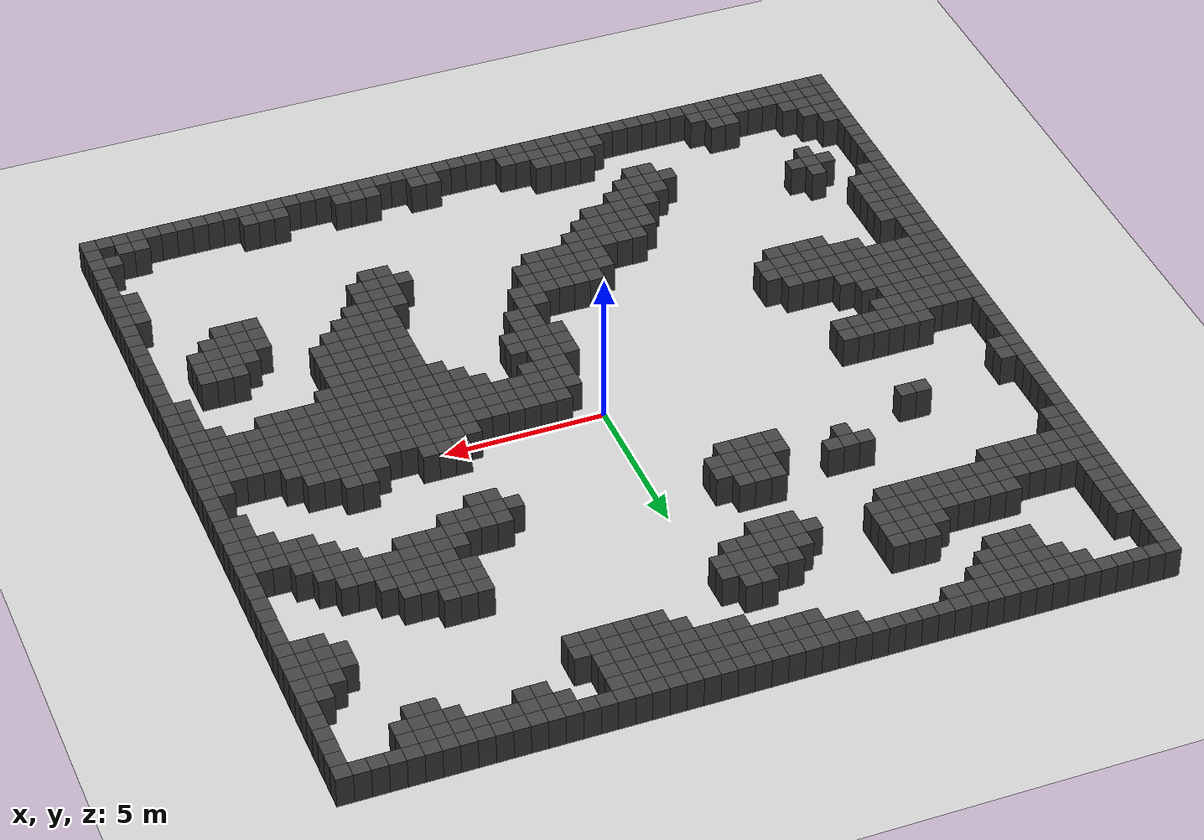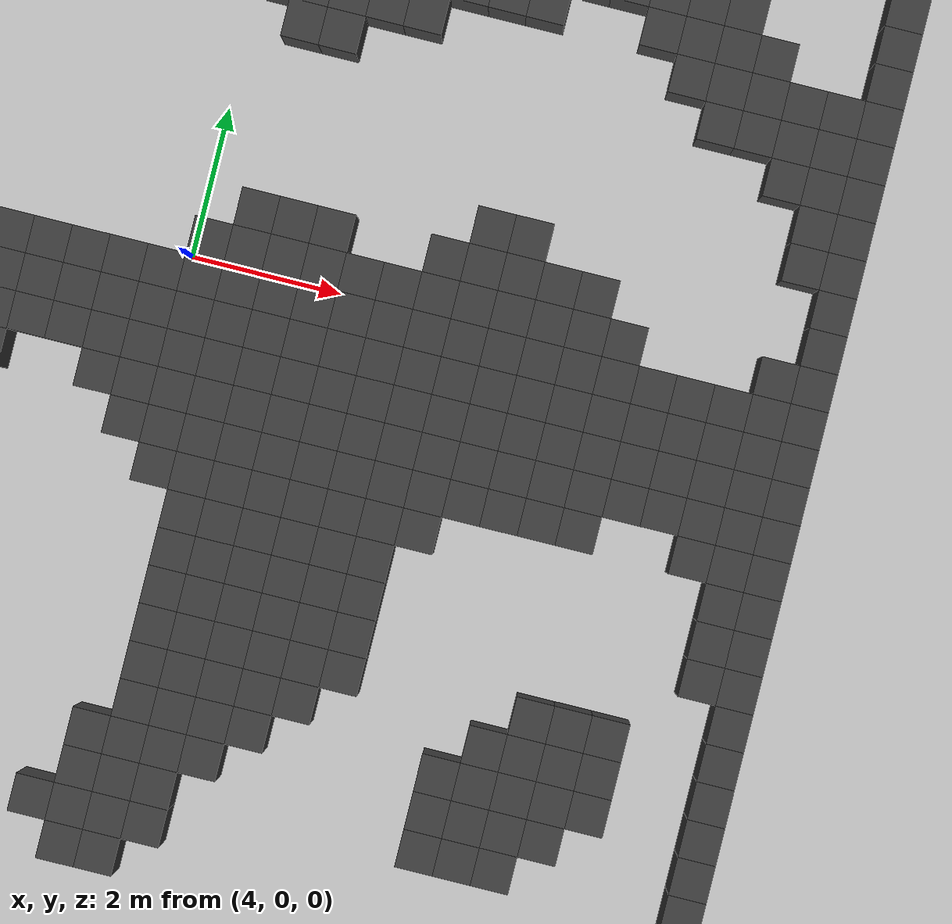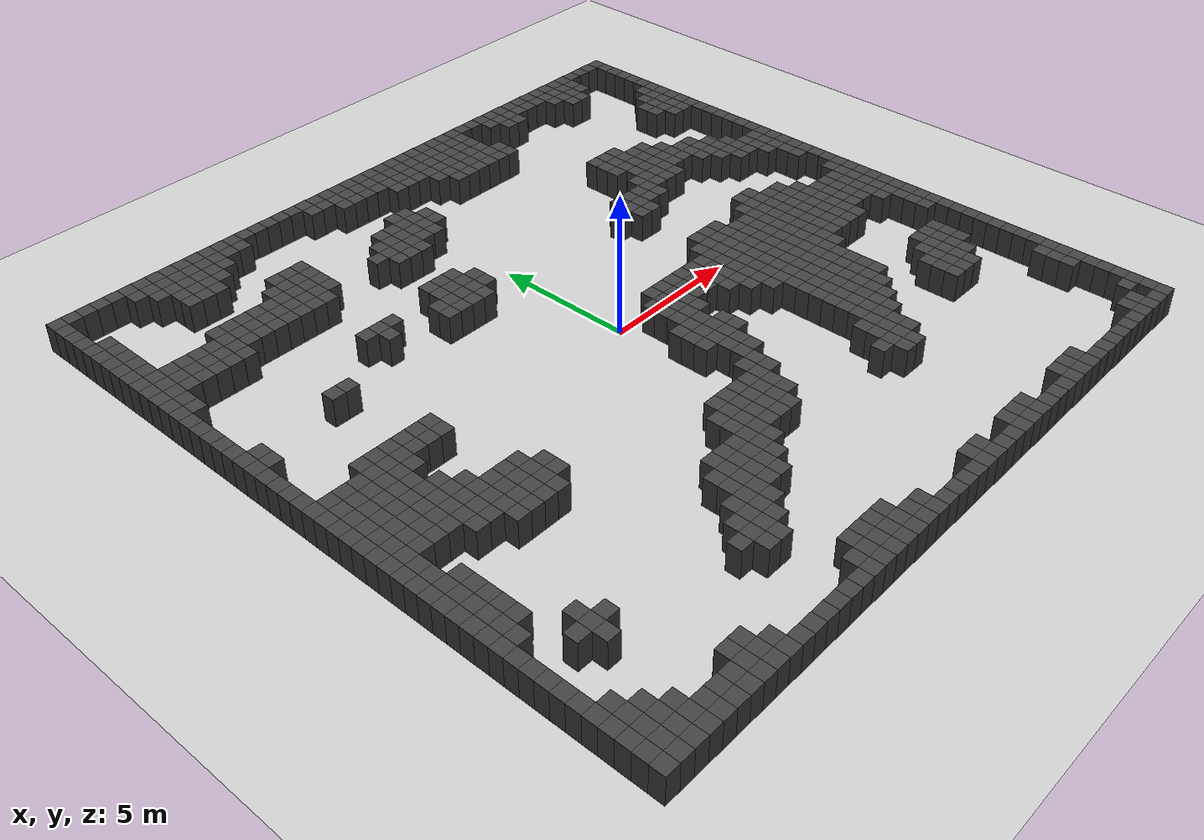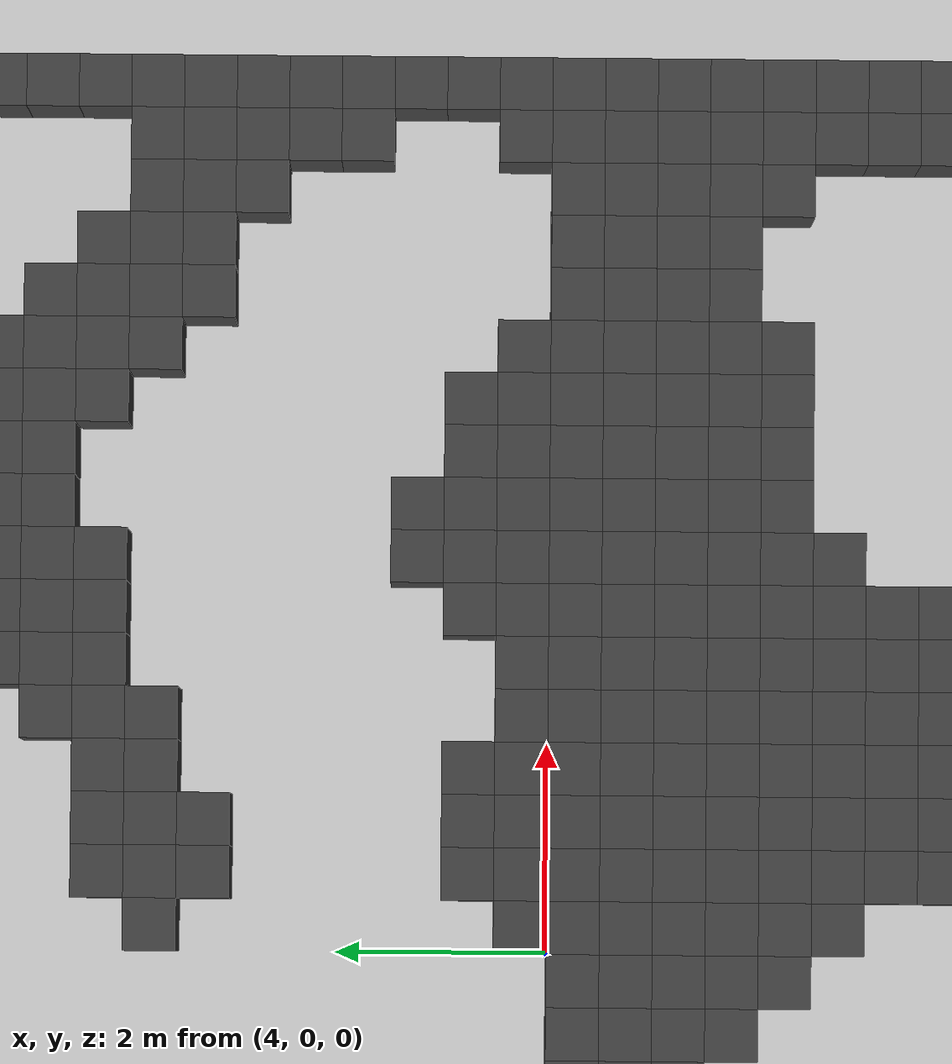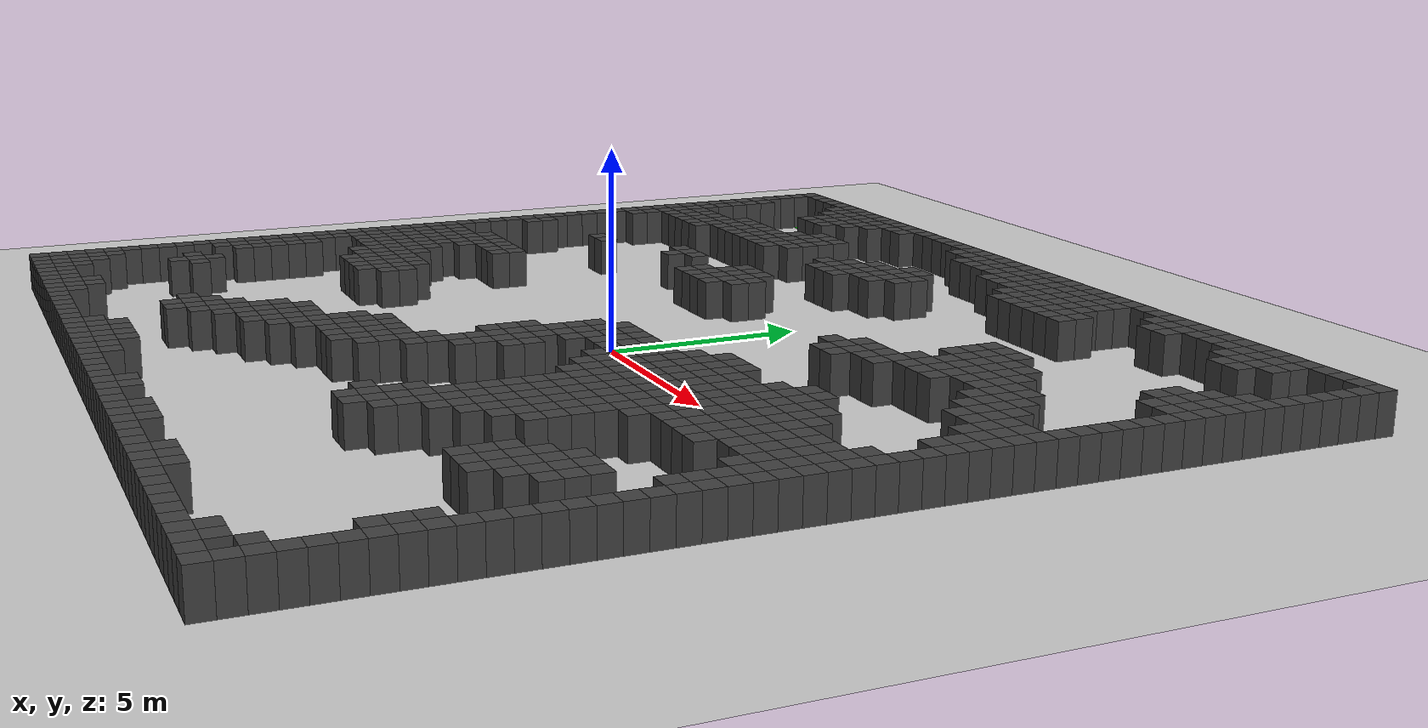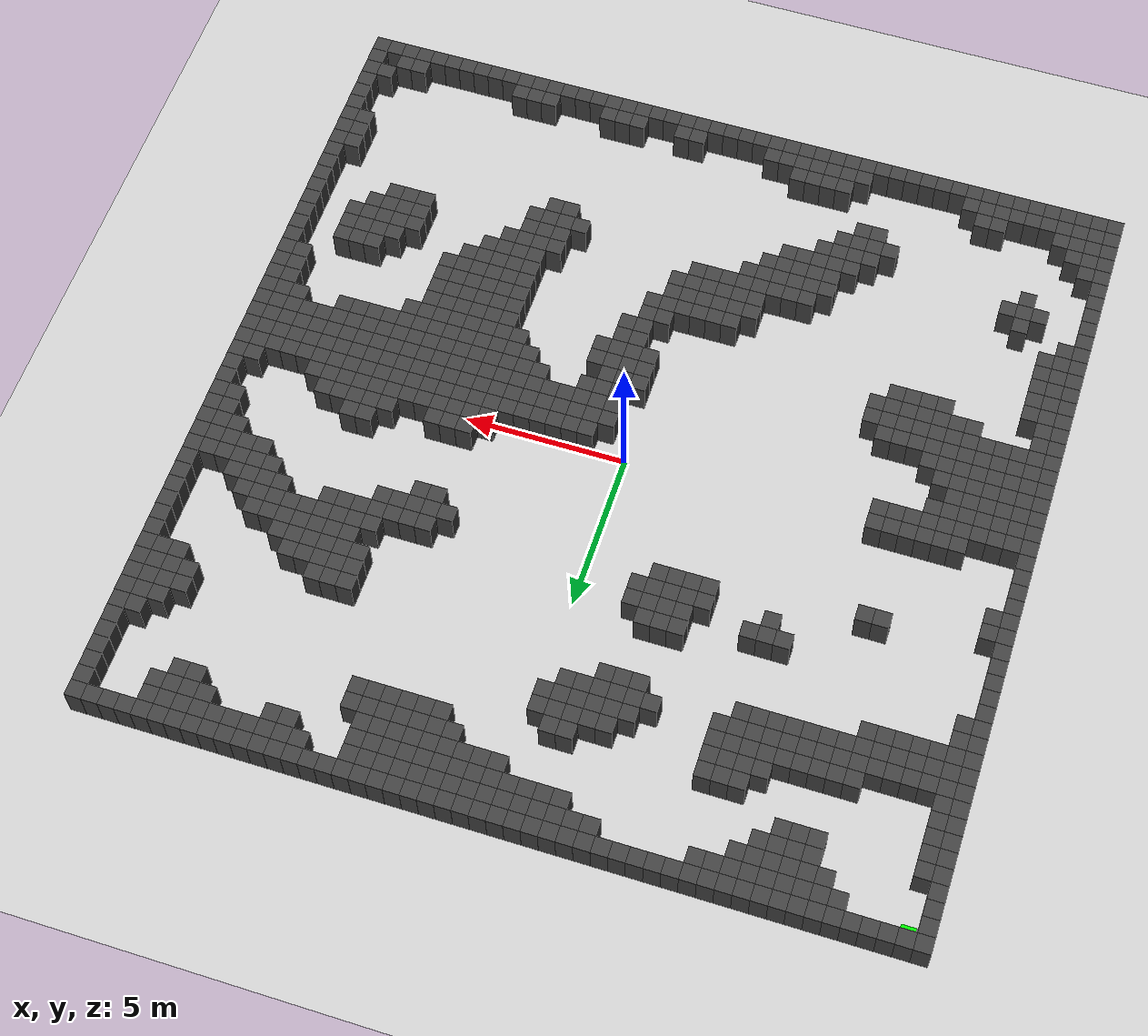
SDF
<?xml version="1.0" ?>
<sdf version="1.7">
  <world name="map_7972">

    <plugin filename="ignition-gazebo-physics-system"
            name="ignition::gazebo::systems::Physics"/>
    <plugin filename="ignition-gazebo-user-commands-system"
            name="ignition::gazebo::systems::UserCommands"/>
    <plugin filename="ignition-gazebo-scene-broadcaster-system"
            name="ignition::gazebo::systems::SceneBroadcaster"/>
    <plugin filename="ignition-gazebo-sensors-system"
            name="ignition::gazebo::systems::Sensors">
      <render_engine>ogre2</render_engine>
    </plugin>
    <physics name="1ms" type="ignored">
      <max_step_size>0.001</max_step_size>
      <real_time_factor>1.0</real_time_factor>
    </physics>
    <gravity>0 0 -9.8</gravity>
    <scene>
      <ambient>0.4 0.4 0.4 1</ambient>
      <background>0.7 0.7 0.7 1</background>
      <shadows>true</shadows>
    </scene>
    <light type="directional" name="sun">
      <cast_shadows>true</cast_shadows>
      <pose>0 0 10 0 0 0</pose>
      <diffuse>0.8 0.8 0.8 1</diffuse>
      <specular>0.2 0.2 0.2 1</specular>
      <attenuation>
        <range>1000</range><constant>0.9</constant>
        <linear>0.01</linear><quadratic>0.001</quadratic>
      </attenuation>
      <direction>-0.5 0.1 -0.9</direction>
    </light>
    <model name="ground_plane">
      <static>true</static>
      <link name="link">
        <collision name="collision">
          <geometry><plane><normal>0 0 1</normal><size>200 200</size></plane></geometry>
        </collision>
        <visual name="visual">
          <geometry><plane><normal>0 0 1</normal><size>200 200</size></plane></geometry>
          <material>
            <ambient>0.8 0.8 0.8 1</ambient>
            <diffuse>0.8 0.8 0.8 1</diffuse>
          </material>
        </visual>
      </link>
    </model>

    <!-- Map: map_7972.png  Category: Rooms  Difficulty: Hard  Obstacles: 863  A*_Mem: 1087 -->
    <model name="maze_environment">
      <static>true</static>

      <!-- ── WALLS ─────────────────────────────────── -->
      <link name="wall_0">
        <pose>-12.250 12.250 0.500 0 0 0</pose>
        <collision name="col">
          <geometry><box><size>0.5 0.5 1.0</size></box></geometry>
        </collision>
        <visual name="vis">
          <geometry><box><size>0.5 0.5 1.0</size></box></geometry>
          <material>
            <ambient>0.15 0.15 0.15 1</ambient>
            <diffuse>0.25 0.25 0.25 1</diffuse>
          </material>
        </visual>
      </link>
      <link name="wall_1">
        <pose>-11.750 12.250 0.500 0 0 0</pose>
        <collision name="col">
          <geometry><box><size>0.5 0.5 1.0</size></box></geometry>
        </collision>
        <visual name="vis">
          <geometry><box><size>0.5 0.5 1.0</size></box></geometry>
          <material>
            <ambient>0.15 0.15 0.15 1</ambient>
            <diffuse>0.25 0.25 0.25 1</diffuse>
          </material>
        </visual>
      </link>
      <link name="wall_2">
        <pose>-11.250 12.250 0.500 0 0 0</pose>
        <collision name="col">
          <geometry><box><size>0.5 0.5 1.0</size></box></geometry>
        </collision>
        <visual name="vis">
          <geometry><box><size>0.5 0.5 1.0</size></box></geometry>
          <material>
            <ambient>0.15 0.15 0.15 1</ambient>
            <diffuse>0.25 0.25 0.25 1</diffuse>
          </material>
        </visual>
      </link>
      <link name="wall_3">
        <pose>-10.750 12.250 0.500 0 0 0</pose>
        <collision name="col">
          <geometry><box><size>0.5 0.5 1.0</size></box></geometry>
        </collision>
        <visual name="vis">
          <geometry><box><size>0.5 0.5 1.0</size></box></geometry>
          <material>
            <ambient>0.15 0.15 0.15 1</ambient>
            <diffuse>0.25 0.25 0.25 1</diffuse>
          </material>
        </visual>
      </link>
      <link name="wall_4">
        <pose>-10.250 12.250 0.500 0 0 0</pose>
        <collision name="col">
          <geometry><box><size>0.5 0.5 1.0</size></box></geometry>
        </collision>
        <visual name="vis">
          <geometry><box><size>0.5 0.5 1.0</size></box></geometry>
          <material>
            <ambient>0.15 0.15 0.15 1</ambient>
            <diffuse>0.25 0.25 0.25 1</diffuse>
          </material>
        </visual>
      </link>
      <link name="wall_5">
        <pose>-9.750 12.250 0.500 0 0 0</pose>
        <collision name="col">
          <geometry><box><size>0.5 0.5 1.0</size></box></geometry>
        </collision>
        <visual name="vis">
          <geometry><box><size>0.5 0.5 1.0</size></box></geometry>
          <material>
            <ambient>0.15 0.15 0.15 1</ambient>
            <diffuse>0.25 0.25 0.25 1</diffuse>
          </material>
        </visual>
      </link>
      <link name="wall_6">
        <pose>-9.250 12.250 0.500 0 0 0</pose>
        <collision name="col">
          <geometry><box><size>0.5 0.5 1.0</size></box></geometry>
        </collision>
        <visual name="vis">
          <geometry><box><size>0.5 0.5 1.0</size></box></geometry>
          <material>
            <ambient>0.15 0.15 0.15 1</ambient>
            <diffuse>0.25 0.25 0.25 1</diffuse>
          </material>
        </visual>
      </link>
      <link name="wall_7">
        <pose>-8.750 12.250 0.500 0 0 0</pose>
        <collision name="col">
          <geometry><box><size>0.5 0.5 1.0</size></box></geometry>
        </collision>
        <visual name="vis">
          <geometry><box><size>0.5 0.5 1.0</size></box></geometry>
          <material>
            <ambient>0.15 0.15 0.15 1</ambient>
            <diffuse>0.25 0.25 0.25 1</diffuse>
          </material>
        </visual>
      </link>
      <link name="wall_8">
        <pose>-8.250 12.250 0.500 0 0 0</pose>
        <collision name="col">
          <geometry><box><size>0.5 0.5 1.0</size></box></geometry>
        </collision>
        <visual name="vis">
          <geometry><box><size>0.5 0.5 1.0</size></box></geometry>
          <material>
            <ambient>0.15 0.15 0.15 1</ambient>
            <diffuse>0.25 0.25 0.25 1</diffuse>
          </material>
        </visual>
      </link>
      <link name="wall_9">
        <pose>-7.750 12.250 0.500 0 0 0</pose>
        <collision name="col">
          <geometry><box><size>0.5 0.5 1.0</size></box></geometry>
        </collision>
        <visual name="vis">
          <geometry><box><size>0.5 0.5 1.0</size></box></geometry>
          <material>
            <ambient>0.15 0.15 0.15 1</ambient>
            <diffuse>0.25 0.25 0.25 1</diffuse>
          </material>
        </visual>
      </link>
      <link name="wall_10">
        <pose>-7.250 12.250 0.500 0 0 0</pose>
        <collision name="col">
          <geometry><box><size>0.5 0.5 1.0</size></box></geometry>
        </collision>
        <visual name="vis">
          <geometry><box><size>0.5 0.5 1.0</size></box></geometry>
          <material>
            <ambient>0.15 0.15 0.15 1</ambient>
            <diffuse>0.25 0.25 0.25 1</diffuse>
          </material>
        </visual>
      </link>
      <link name="wall_11">
        <pose>-6.750 12.250 0.500 0 0 0</pose>
        <collision name="col">
          <geometry><box><size>0.5 0.5 1.0</size></box></geometry>
        </collision>
        <visual name="vis">
          <geometry><box><size>0.5 0.5 1.0</size></box></geometry>
          <material>
            <ambient>0.15 0.15 0.15 1</ambient>
            <diffuse>0.25 0.25 0.25 1</diffuse>
          </material>
        </visual>
      </link>
      <link name="wall_12">
        <pose>-6.250 12.250 0.500 0 0 0</pose>
        <collision name="col">
          <geometry><box><size>0.5 0.5 1.0</size></box></geometry>
        </collision>
        <visual name="vis">
          <geometry><box><size>0.5 0.5 1.0</size></box></geometry>
          <material>
            <ambient>0.15 0.15 0.15 1</ambient>
            <diffuse>0.25 0.25 0.25 1</diffuse>
          </material>
        </visual>
      </link>
      <link name="wall_13">
        <pose>-5.750 12.250 0.500 0 0 0</pose>
        <collision name="col">
          <geometry><box><size>0.5 0.5 1.0</size></box></geometry>
        </collision>
        <visual name="vis">
          <geometry><box><size>0.5 0.5 1.0</size></box></geometry>
          <material>
            <ambient>0.15 0.15 0.15 1</ambient>
            <diffuse>0.25 0.25 0.25 1</diffuse>
          </material>
        </visual>
      </link>
      <link name="wall_14">
        <pose>-5.250 12.250 0.500 0 0 0</pose>
        <collision name="col">
          <geometry><box><size>0.5 0.5 1.0</size></box></geometry>
        </collision>
        <visual name="vis">
          <geometry><box><size>0.5 0.5 1.0</size></box></geometry>
          <material>
            <ambient>0.15 0.15 0.15 1</ambient>
            <diffuse>0.25 0.25 0.25 1</diffuse>
          </material>
        </visual>
      </link>
      <link name="wall_15">
        <pose>-4.750 12.250 0.500 0 0 0</pose>
        <collision name="col">
          <geometry><box><size>0.5 0.5 1.0</size></box></geometry>
        </collision>
        <visual name="vis">
          <geometry><box><size>0.5 0.5 1.0</size></box></geometry>
          <material>
            <ambient>0.15 0.15 0.15 1</ambient>
            <diffuse>0.25 0.25 0.25 1</diffuse>
          </material>
        </visual>
      </link>
      <link name="wall_16">
        <pose>-4.250 12.250 0.500 0 0 0</pose>
        <collision name="col">
          <geometry><box><size>0.5 0.5 1.0</size></box></geometry>
        </collision>
        <visual name="vis">
          <geometry><box><size>0.5 0.5 1.0</size></box></geometry>
          <material>
            <ambient>0.15 0.15 0.15 1</ambient>
            <diffuse>0.25 0.25 0.25 1</diffuse>
          </material>
        </visual>
      </link>
      <link name="wall_17">
        <pose>-3.750 12.250 0.500 0 0 0</pose>
        <collision name="col">
          <geometry><box><size>0.5 0.5 1.0</size></box></geometry>
        </collision>
        <visual name="vis">
          <geometry><box><size>0.5 0.5 1.0</size></box></geometry>
          <material>
            <ambient>0.15 0.15 0.15 1</ambient>
            <diffuse>0.25 0.25 0.25 1</diffuse>
          </material>
        </visual>
      </link>
      <link name="wall_18">
        <pose>-3.250 12.250 0.500 0 0 0</pose>
        <collision name="col">
          <geometry><box><size>0.5 0.5 1.0</size></box></geometry>
        </collision>
        <visual name="vis">
          <geometry><box><size>0.5 0.5 1.0</size></box></geometry>
          <material>
            <ambient>0.15 0.15 0.15 1</ambient>
            <diffuse>0.25 0.25 0.25 1</diffuse>
          </material>
        </visual>
      </link>
      <link name="wall_19">
        <pose>-2.750 12.250 0.500 0 0 0</pose>
        <collision name="col">
          <geometry><box><size>0.5 0.5 1.0</size></box></geometry>
        </collision>
        <visual name="vis">
          <geometry><box><size>0.5 0.5 1.0</size></box></geometry>
          <material>
            <ambient>0.15 0.15 0.15 1</ambient>
            <diffuse>0.25 0.25 0.25 1</diffuse>
          </material>
        </visual>
      </link>
      <link name="wall_20">
        <pose>-2.250 12.250 0.500 0 0 0</pose>
        <collision name="col">
          <geometry><box><size>0.5 0.5 1.0</size></box></geometry>
        </collision>
        <visual name="vis">
          <geometry><box><size>0.5 0.5 1.0</size></box></geometry>
          <material>
            <ambient>0.15 0.15 0.15 1</ambient>
            <diffuse>0.25 0.25 0.25 1</diffuse>
          </material>
        </visual>
      </link>
      <link name="wall_21">
        <pose>-1.750 12.250 0.500 0 0 0</pose>
        <collision name="col">
          <geometry><box><size>0.5 0.5 1.0</size></box></geometry>
        </collision>
        <visual name="vis">
          <geometry><box><size>0.5 0.5 1.0</size></box></geometry>
          <material>
            <ambient>0.15 0.15 0.15 1</ambient>
            <diffuse>0.25 0.25 0.25 1</diffuse>
          </material>
        </visual>
      </link>
      <link name="wall_22">
        <pose>-1.250 12.250 0.500 0 0 0</pose>
        <collision name="col">
          <geometry><box><size>0.5 0.5 1.0</size></box></geometry>
        </collision>
        <visual name="vis">
          <geometry><box><size>0.5 0.5 1.0</size></box></geometry>
          <material>
            <ambient>0.15 0.15 0.15 1</ambient>
            <diffuse>0.25 0.25 0.25 1</diffuse>
          </material>
        </visual>
      </link>
      <link name="wall_23">
        <pose>-0.750 12.250 0.500 0 0 0</pose>
        <collision name="col">
          <geometry><box><size>0.5 0.5 1.0</size></box></geometry>
        </collision>
        <visual name="vis">
          <geometry><box><size>0.5 0.5 1.0</size></box></geometry>
          <material>
            <ambient>0.15 0.15 0.15 1</ambient>
            <diffuse>0.25 0.25 0.25 1</diffuse>
          </material>
        </visual>
      </link>
      <link name="wall_24">
        <pose>-0.250 12.250 0.500 0 0 0</pose>
        <collision name="col">
          <geometry><box><size>0.5 0.5 1.0</size></box></geometry>
        </collision>
        <visual name="vis">
          <geometry><box><size>0.5 0.5 1.0</size></box></geometry>
          <material>
            <ambient>0.15 0.15 0.15 1</ambient>
            <diffuse>0.25 0.25 0.25 1</diffuse>
          </material>
        </visual>
      </link>
      <link name="wall_25">
        <pose>0.250 12.250 0.500 0 0 0</pose>
        <collision name="col">
          <geometry><box><size>0.5 0.5 1.0</size></box></geometry>
        </collision>
        <visual name="vis">
          <geometry><box><size>0.5 0.5 1.0</size></box></geometry>
          <material>
            <ambient>0.15 0.15 0.15 1</ambient>
            <diffuse>0.25 0.25 0.25 1</diffuse>
          </material>
        </visual>
      </link>
      <link name="wall_26">
        <pose>0.750 12.250 0.500 0 0 0</pose>
        <collision name="col">
          <geometry><box><size>0.5 0.5 1.0</size></box></geometry>
        </collision>
        <visual name="vis">
          <geometry><box><size>0.5 0.5 1.0</size></box></geometry>
          <material>
            <ambient>0.15 0.15 0.15 1</ambient>
            <diffuse>0.25 0.25 0.25 1</diffuse>
          </material>
        </visual>
      </link>
      <link name="wall_27">
        <pose>1.250 12.250 0.500 0 0 0</pose>
        <collision name="col">
          <geometry><box><size>0.5 0.5 1.0</size></box></geometry>
        </collision>
        <visual name="vis">
          <geometry><box><size>0.5 0.5 1.0</size></box></geometry>
          <material>
            <ambient>0.15 0.15 0.15 1</ambient>
            <diffuse>0.25 0.25 0.25 1</diffuse>
          </material>
        </visual>
      </link>
      <link name="wall_28">
        <pose>1.750 12.250 0.500 0 0 0</pose>
        <collision name="col">
          <geometry><box><size>0.5 0.5 1.0</size></box></geometry>
        </collision>
        <visual name="vis">
          <geometry><box><size>0.5 0.5 1.0</size></box></geometry>
          <material>
            <ambient>0.15 0.15 0.15 1</ambient>
            <diffuse>0.25 0.25 0.25 1</diffuse>
          </material>
        </visual>
      </link>
      <link name="wall_29">
        <pose>2.250 12.250 0.500 0 0 0</pose>
        <collision name="col">
          <geometry><box><size>0.5 0.5 1.0</size></box></geometry>
        </collision>
        <visual name="vis">
          <geometry><box><size>0.5 0.5 1.0</size></box></geometry>
          <material>
            <ambient>0.15 0.15 0.15 1</ambient>
            <diffuse>0.25 0.25 0.25 1</diffuse>
          </material>
        </visual>
      </link>
      <link name="wall_30">
        <pose>2.750 12.250 0.500 0 0 0</pose>
        <collision name="col">
          <geometry><box><size>0.5 0.5 1.0</size></box></geometry>
        </collision>
        <visual name="vis">
          <geometry><box><size>0.5 0.5 1.0</size></box></geometry>
          <material>
            <ambient>0.15 0.15 0.15 1</ambient>
            <diffuse>0.25 0.25 0.25 1</diffuse>
          </material>
        </visual>
      </link>
      <link name="wall_31">
        <pose>3.250 12.250 0.500 0 0 0</pose>
        <collision name="col">
          <geometry><box><size>0.5 0.5 1.0</size></box></geometry>
        </collision>
        <visual name="vis">
          <geometry><box><size>0.5 0.5 1.0</size></box></geometry>
          <material>
            <ambient>0.15 0.15 0.15 1</ambient>
            <diffuse>0.25 0.25 0.25 1</diffuse>
          </material>
        </visual>
      </link>
      <link name="wall_32">
        <pose>3.750 12.250 0.500 0 0 0</pose>
        <collision name="col">
          <geometry><box><size>0.5 0.5 1.0</size></box></geometry>
        </collision>
        <visual name="vis">
          <geometry><box><size>0.5 0.5 1.0</size></box></geometry>
          <material>
            <ambient>0.15 0.15 0.15 1</ambient>
            <diffuse>0.25 0.25 0.25 1</diffuse>
          </material>
        </visual>
      </link>
      <link name="wall_33">
        <pose>4.250 12.250 0.500 0 0 0</pose>
        <collision name="col">
          <geometry><box><size>0.5 0.5 1.0</size></box></geometry>
        </collision>
        <visual name="vis">
          <geometry><box><size>0.5 0.5 1.0</size></box></geometry>
          <material>
            <ambient>0.15 0.15 0.15 1</ambient>
            <diffuse>0.25 0.25 0.25 1</diffuse>
          </material>
        </visual>
      </link>
      <link name="wall_34">
        <pose>4.750 12.250 0.500 0 0 0</pose>
        <collision name="col">
          <geometry><box><size>0.5 0.5 1.0</size></box></geometry>
        </collision>
        <visual name="vis">
          <geometry><box><size>0.5 0.5 1.0</size></box></geometry>
          <material>
            <ambient>0.15 0.15 0.15 1</ambient>
            <diffuse>0.25 0.25 0.25 1</diffuse>
          </material>
        </visual>
      </link>
      <link name="wall_35">
        <pose>5.250 12.250 0.500 0 0 0</pose>
        <collision name="col">
          <geometry><box><size>0.5 0.5 1.0</size></box></geometry>
        </collision>
        <visual name="vis">
          <geometry><box><size>0.5 0.5 1.0</size></box></geometry>
          <material>
            <ambient>0.15 0.15 0.15 1</ambient>
            <diffuse>0.25 0.25 0.25 1</diffuse>
          </material>
        </visual>
      </link>
      <link name="wall_36">
        <pose>5.750 12.250 0.500 0 0 0</pose>
        <collision name="col">
          <geometry><box><size>0.5 0.5 1.0</size></box></geometry>
        </collision>
        <visual name="vis">
          <geometry><box><size>0.5 0.5 1.0</size></box></geometry>
          <material>
            <ambient>0.15 0.15 0.15 1</ambient>
            <diffuse>0.25 0.25 0.25 1</diffuse>
          </material>
        </visual>
      </link>
      <link name="wall_37">
        <pose>6.250 12.250 0.500 0 0 0</pose>
        <collision name="col">
          <geometry><box><size>0.5 0.5 1.0</size></box></geometry>
        </collision>
        <visual name="vis">
          <geometry><box><size>0.5 0.5 1.0</size></box></geometry>
          <material>
            <ambient>0.15 0.15 0.15 1</ambient>
            <diffuse>0.25 0.25 0.25 1</diffuse>
          </material>
        </visual>
      </link>
      <link name="wall_38">
        <pose>6.750 12.250 0.500 0 0 0</pose>
        <collision name="col">
          <geometry><box><size>0.5 0.5 1.0</size></box></geometry>
        </collision>
        <visual name="vis">
          <geometry><box><size>0.5 0.5 1.0</size></box></geometry>
          <material>
            <ambient>0.15 0.15 0.15 1</ambient>
            <diffuse>0.25 0.25 0.25 1</diffuse>
          </material>
        </visual>
      </link>
      <link name="wall_39">
        <pose>7.250 12.250 0.500 0 0 0</pose>
        <collision name="col">
          <geometry><box><size>0.5 0.5 1.0</size></box></geometry>
        </collision>
        <visual name="vis">
          <geometry><box><size>0.5 0.5 1.0</size></box></geometry>
          <material>
            <ambient>0.15 0.15 0.15 1</ambient>
            <diffuse>0.25 0.25 0.25 1</diffuse>
          </material>
        </visual>
      </link>
      <link name="wall_40">
        <pose>7.750 12.250 0.500 0 0 0</pose>
        <collision name="col">
          <geometry><box><size>0.5 0.5 1.0</size></box></geometry>
        </collision>
        <visual name="vis">
          <geometry><box><size>0.5 0.5 1.0</size></box></geometry>
          <material>
            <ambient>0.15 0.15 0.15 1</ambient>
            <diffuse>0.25 0.25 0.25 1</diffuse>
          </material>
        </visual>
      </link>
      <link name="wall_41">
        <pose>8.250 12.250 0.500 0 0 0</pose>
        <collision name="col">
          <geometry><box><size>0.5 0.5 1.0</size></box></geometry>
        </collision>
        <visual name="vis">
          <geometry><box><size>0.5 0.5 1.0</size></box></geometry>
          <material>
            <ambient>0.15 0.15 0.15 1</ambient>
            <diffuse>0.25 0.25 0.25 1</diffuse>
          </material>
        </visual>
      </link>
      <link name="wall_42">
        <pose>8.750 12.250 0.500 0 0 0</pose>
        <collision name="col">
          <geometry><box><size>0.5 0.5 1.0</size></box></geometry>
        </collision>
        <visual name="vis">
          <geometry><box><size>0.5 0.5 1.0</size></box></geometry>
          <material>
            <ambient>0.15 0.15 0.15 1</ambient>
            <diffuse>0.25 0.25 0.25 1</diffuse>
          </material>
        </visual>
      </link>
      <link name="wall_43">
        <pose>9.250 12.250 0.500 0 0 0</pose>
        <collision name="col">
          <geometry><box><size>0.5 0.5 1.0</size></box></geometry>
        </collision>
        <visual name="vis">
          <geometry><box><size>0.5 0.5 1.0</size></box></geometry>
          <material>
            <ambient>0.15 0.15 0.15 1</ambient>
            <diffuse>0.25 0.25 0.25 1</diffuse>
          </material>
        </visual>
      </link>
      <link name="wall_44">
        <pose>9.750 12.250 0.500 0 0 0</pose>
        <collision name="col">
          <geometry><box><size>0.5 0.5 1.0</size></box></geometry>
        </collision>
        <visual name="vis">
          <geometry><box><size>0.5 0.5 1.0</size></box></geometry>
          <material>
            <ambient>0.15 0.15 0.15 1</ambient>
            <diffuse>0.25 0.25 0.25 1</diffuse>
          </material>
        </visual>
      </link>
      <link name="wall_45">
        <pose>10.250 12.250 0.500 0 0 0</pose>
        <collision name="col">
          <geometry><box><size>0.5 0.5 1.0</size></box></geometry>
        </collision>
        <visual name="vis">
          <geometry><box><size>0.5 0.5 1.0</size></box></geometry>
          <material>
            <ambient>0.15 0.15 0.15 1</ambient>
            <diffuse>0.25 0.25 0.25 1</diffuse>
          </material>
        </visual>
      </link>
      <link name="wall_46">
        <pose>10.750 12.250 0.500 0 0 0</pose>
        <collision name="col">
          <geometry><box><size>0.5 0.5 1.0</size></box></geometry>
        </collision>
        <visual name="vis">
          <geometry><box><size>0.5 0.5 1.0</size></box></geometry>
          <material>
            <ambient>0.15 0.15 0.15 1</ambient>
            <diffuse>0.25 0.25 0.25 1</diffuse>
          </material>
        </visual>
      </link>
      <link name="wall_47">
        <pose>11.250 12.250 0.500 0 0 0</pose>
        <collision name="col">
          <geometry><box><size>0.5 0.5 1.0</size></box></geometry>
        </collision>
        <visual name="vis">
          <geometry><box><size>0.5 0.5 1.0</size></box></geometry>
          <material>
            <ambient>0.15 0.15 0.15 1</ambient>
            <diffuse>0.25 0.25 0.25 1</diffuse>
          </material>
        </visual>
      </link>
      <link name="wall_48">
        <pose>11.750 12.250 0.500 0 0 0</pose>
        <collision name="col">
          <geometry><box><size>0.5 0.5 1.0</size></box></geometry>
        </collision>
        <visual name="vis">
          <geometry><box><size>0.5 0.5 1.0</size></box></geometry>
          <material>
            <ambient>0.15 0.15 0.15 1</ambient>
            <diffuse>0.25 0.25 0.25 1</diffuse>
          </material>
        </visual>
      </link>
      <link name="wall_49">
        <pose>12.250 12.250 0.500 0 0 0</pose>
        <collision name="col">
          <geometry><box><size>0.5 0.5 1.0</size></box></geometry>
        </collision>
        <visual name="vis">
          <geometry><box><size>0.5 0.5 1.0</size></box></geometry>
          <material>
            <ambient>0.15 0.15 0.15 1</ambient>
            <diffuse>0.25 0.25 0.25 1</diffuse>
          </material>
        </visual>
      </link>
      <link name="wall_50">
        <pose>-12.250 11.750 0.500 0 0 0</pose>
        <collision name="col">
          <geometry><box><size>0.5 0.5 1.0</size></box></geometry>
        </collision>
        <visual name="vis">
          <geometry><box><size>0.5 0.5 1.0</size></box></geometry>
          <material>
            <ambient>0.15 0.15 0.15 1</ambient>
            <diffuse>0.25 0.25 0.25 1</diffuse>
          </material>
        </visual>
      </link>
      <link name="wall_51">
        <pose>-9.750 11.750 0.500 0 0 0</pose>
        <collision name="col">
          <geometry><box><size>0.5 0.5 1.0</size></box></geometry>
        </collision>
        <visual name="vis">
          <geometry><box><size>0.5 0.5 1.0</size></box></geometry>
          <material>
            <ambient>0.15 0.15 0.15 1</ambient>
            <diffuse>0.25 0.25 0.25 1</diffuse>
          </material>
        </visual>
      </link>
      <link name="wall_52">
        <pose>-9.250 11.750 0.500 0 0 0</pose>
        <collision name="col">
          <geometry><box><size>0.5 0.5 1.0</size></box></geometry>
        </collision>
        <visual name="vis">
          <geometry><box><size>0.5 0.5 1.0</size></box></geometry>
          <material>
            <ambient>0.15 0.15 0.15 1</ambient>
            <diffuse>0.25 0.25 0.25 1</diffuse>
          </material>
        </visual>
      </link>
      <link name="wall_53">
        <pose>-8.750 11.750 0.500 0 0 0</pose>
        <collision name="col">
          <geometry><box><size>0.5 0.5 1.0</size></box></geometry>
        </collision>
        <visual name="vis">
          <geometry><box><size>0.5 0.5 1.0</size></box></geometry>
          <material>
            <ambient>0.15 0.15 0.15 1</ambient>
            <diffuse>0.25 0.25 0.25 1</diffuse>
          </material>
        </visual>
      </link>
      <link name="wall_54">
        <pose>-8.250 11.750 0.500 0 0 0</pose>
        <collision name="col">
          <geometry><box><size>0.5 0.5 1.0</size></box></geometry>
        </collision>
        <visual name="vis">
          <geometry><box><size>0.5 0.5 1.0</size></box></geometry>
          <material>
            <ambient>0.15 0.15 0.15 1</ambient>
            <diffuse>0.25 0.25 0.25 1</diffuse>
          </material>
        </visual>
      </link>
      <link name="wall_55">
        <pose>-7.750 11.750 0.500 0 0 0</pose>
        <collision name="col">
          <geometry><box><size>0.5 0.5 1.0</size></box></geometry>
        </collision>
        <visual name="vis">
          <geometry><box><size>0.5 0.5 1.0</size></box></geometry>
          <material>
            <ambient>0.15 0.15 0.15 1</ambient>
            <diffuse>0.25 0.25 0.25 1</diffuse>
          </material>
        </visual>
      </link>
      <link name="wall_56">
        <pose>-7.250 11.750 0.500 0 0 0</pose>
        <collision name="col">
          <geometry><box><size>0.5 0.5 1.0</size></box></geometry>
        </collision>
        <visual name="vis">
          <geometry><box><size>0.5 0.5 1.0</size></box></geometry>
          <material>
            <ambient>0.15 0.15 0.15 1</ambient>
            <diffuse>0.25 0.25 0.25 1</diffuse>
          </material>
        </visual>
      </link>
      <link name="wall_57">
        <pose>-6.750 11.750 0.500 0 0 0</pose>
        <collision name="col">
          <geometry><box><size>0.5 0.5 1.0</size></box></geometry>
        </collision>
        <visual name="vis">
          <geometry><box><size>0.5 0.5 1.0</size></box></geometry>
          <material>
            <ambient>0.15 0.15 0.15 1</ambient>
            <diffuse>0.25 0.25 0.25 1</diffuse>
          </material>
        </visual>
      </link>
      <link name="wall_58">
        <pose>-6.250 11.750 0.500 0 0 0</pose>
        <collision name="col">
          <geometry><box><size>0.5 0.5 1.0</size></box></geometry>
        </collision>
        <visual name="vis">
          <geometry><box><size>0.5 0.5 1.0</size></box></geometry>
          <material>
            <ambient>0.15 0.15 0.15 1</ambient>
            <diffuse>0.25 0.25 0.25 1</diffuse>
          </material>
        </visual>
      </link>
      <link name="wall_59">
        <pose>-5.750 11.750 0.500 0 0 0</pose>
        <collision name="col">
          <geometry><box><size>0.5 0.5 1.0</size></box></geometry>
        </collision>
        <visual name="vis">
          <geometry><box><size>0.5 0.5 1.0</size></box></geometry>
          <material>
            <ambient>0.15 0.15 0.15 1</ambient>
            <diffuse>0.25 0.25 0.25 1</diffuse>
          </material>
        </visual>
      </link>
      <link name="wall_60">
        <pose>-2.750 11.750 0.500 0 0 0</pose>
        <collision name="col">
          <geometry><box><size>0.5 0.5 1.0</size></box></geometry>
        </collision>
        <visual name="vis">
          <geometry><box><size>0.5 0.5 1.0</size></box></geometry>
          <material>
            <ambient>0.15 0.15 0.15 1</ambient>
            <diffuse>0.25 0.25 0.25 1</diffuse>
          </material>
        </visual>
      </link>
      <link name="wall_61">
        <pose>-2.250 11.750 0.500 0 0 0</pose>
        <collision name="col">
          <geometry><box><size>0.5 0.5 1.0</size></box></geometry>
        </collision>
        <visual name="vis">
          <geometry><box><size>0.5 0.5 1.0</size></box></geometry>
          <material>
            <ambient>0.15 0.15 0.15 1</ambient>
            <diffuse>0.25 0.25 0.25 1</diffuse>
          </material>
        </visual>
      </link>
      <link name="wall_62">
        <pose>-1.750 11.750 0.500 0 0 0</pose>
        <collision name="col">
          <geometry><box><size>0.5 0.5 1.0</size></box></geometry>
        </collision>
        <visual name="vis">
          <geometry><box><size>0.5 0.5 1.0</size></box></geometry>
          <material>
            <ambient>0.15 0.15 0.15 1</ambient>
            <diffuse>0.25 0.25 0.25 1</diffuse>
          </material>
        </visual>
      </link>
      <link name="wall_63">
        <pose>-1.250 11.750 0.500 0 0 0</pose>
        <collision name="col">
          <geometry><box><size>0.5 0.5 1.0</size></box></geometry>
        </collision>
        <visual name="vis">
          <geometry><box><size>0.5 0.5 1.0</size></box></geometry>
          <material>
            <ambient>0.15 0.15 0.15 1</ambient>
            <diffuse>0.25 0.25 0.25 1</diffuse>
          </material>
        </visual>
      </link>
      <link name="wall_64">
        <pose>-0.750 11.750 0.500 0 0 0</pose>
        <collision name="col">
          <geometry><box><size>0.5 0.5 1.0</size></box></geometry>
        </collision>
        <visual name="vis">
          <geometry><box><size>0.5 0.5 1.0</size></box></geometry>
          <material>
            <ambient>0.15 0.15 0.15 1</ambient>
            <diffuse>0.25 0.25 0.25 1</diffuse>
          </material>
        </visual>
      </link>
      <link name="wall_65">
        <pose>-0.250 11.750 0.500 0 0 0</pose>
        <collision name="col">
          <geometry><box><size>0.5 0.5 1.0</size></box></geometry>
        </collision>
        <visual name="vis">
          <geometry><box><size>0.5 0.5 1.0</size></box></geometry>
          <material>
            <ambient>0.15 0.15 0.15 1</ambient>
            <diffuse>0.25 0.25 0.25 1</diffuse>
          </material>
        </visual>
      </link>
      <link name="wall_66">
        <pose>0.250 11.750 0.500 0 0 0</pose>
        <collision name="col">
          <geometry><box><size>0.5 0.5 1.0</size></box></geometry>
        </collision>
        <visual name="vis">
          <geometry><box><size>0.5 0.5 1.0</size></box></geometry>
          <material>
            <ambient>0.15 0.15 0.15 1</ambient>
            <diffuse>0.25 0.25 0.25 1</diffuse>
          </material>
        </visual>
      </link>
      <link name="wall_67">
        <pose>0.750 11.750 0.500 0 0 0</pose>
        <collision name="col">
          <geometry><box><size>0.5 0.5 1.0</size></box></geometry>
        </collision>
        <visual name="vis">
          <geometry><box><size>0.5 0.5 1.0</size></box></geometry>
          <material>
            <ambient>0.15 0.15 0.15 1</ambient>
            <diffuse>0.25 0.25 0.25 1</diffuse>
          </material>
        </visual>
      </link>
      <link name="wall_68">
        <pose>1.250 11.750 0.500 0 0 0</pose>
        <collision name="col">
          <geometry><box><size>0.5 0.5 1.0</size></box></geometry>
        </collision>
        <visual name="vis">
          <geometry><box><size>0.5 0.5 1.0</size></box></geometry>
          <material>
            <ambient>0.15 0.15 0.15 1</ambient>
            <diffuse>0.25 0.25 0.25 1</diffuse>
          </material>
        </visual>
      </link>
      <link name="wall_69">
        <pose>1.750 11.750 0.500 0 0 0</pose>
        <collision name="col">
          <geometry><box><size>0.5 0.5 1.0</size></box></geometry>
        </collision>
        <visual name="vis">
          <geometry><box><size>0.5 0.5 1.0</size></box></geometry>
          <material>
            <ambient>0.15 0.15 0.15 1</ambient>
            <diffuse>0.25 0.25 0.25 1</diffuse>
          </material>
        </visual>
      </link>
      <link name="wall_70">
        <pose>2.250 11.750 0.500 0 0 0</pose>
        <collision name="col">
          <geometry><box><size>0.5 0.5 1.0</size></box></geometry>
        </collision>
        <visual name="vis">
          <geometry><box><size>0.5 0.5 1.0</size></box></geometry>
          <material>
            <ambient>0.15 0.15 0.15 1</ambient>
            <diffuse>0.25 0.25 0.25 1</diffuse>
          </material>
        </visual>
      </link>
      <link name="wall_71">
        <pose>2.750 11.750 0.500 0 0 0</pose>
        <collision name="col">
          <geometry><box><size>0.5 0.5 1.0</size></box></geometry>
        </collision>
        <visual name="vis">
          <geometry><box><size>0.5 0.5 1.0</size></box></geometry>
          <material>
            <ambient>0.15 0.15 0.15 1</ambient>
            <diffuse>0.25 0.25 0.25 1</diffuse>
          </material>
        </visual>
      </link>
      <link name="wall_72">
        <pose>3.250 11.750 0.500 0 0 0</pose>
        <collision name="col">
          <geometry><box><size>0.5 0.5 1.0</size></box></geometry>
        </collision>
        <visual name="vis">
          <geometry><box><size>0.5 0.5 1.0</size></box></geometry>
          <material>
            <ambient>0.15 0.15 0.15 1</ambient>
            <diffuse>0.25 0.25 0.25 1</diffuse>
          </material>
        </visual>
      </link>
      <link name="wall_73">
        <pose>3.750 11.750 0.500 0 0 0</pose>
        <collision name="col">
          <geometry><box><size>0.5 0.5 1.0</size></box></geometry>
        </collision>
        <visual name="vis">
          <geometry><box><size>0.5 0.5 1.0</size></box></geometry>
          <material>
            <ambient>0.15 0.15 0.15 1</ambient>
            <diffuse>0.25 0.25 0.25 1</diffuse>
          </material>
        </visual>
      </link>
      <link name="wall_74">
        <pose>4.250 11.750 0.500 0 0 0</pose>
        <collision name="col">
          <geometry><box><size>0.5 0.5 1.0</size></box></geometry>
        </collision>
        <visual name="vis">
          <geometry><box><size>0.5 0.5 1.0</size></box></geometry>
          <material>
            <ambient>0.15 0.15 0.15 1</ambient>
            <diffuse>0.25 0.25 0.25 1</diffuse>
          </material>
        </visual>
      </link>
      <link name="wall_75">
        <pose>5.750 11.750 0.500 0 0 0</pose>
        <collision name="col">
          <geometry><box><size>0.5 0.5 1.0</size></box></geometry>
        </collision>
        <visual name="vis">
          <geometry><box><size>0.5 0.5 1.0</size></box></geometry>
          <material>
            <ambient>0.15 0.15 0.15 1</ambient>
            <diffuse>0.25 0.25 0.25 1</diffuse>
          </material>
        </visual>
      </link>
      <link name="wall_76">
        <pose>6.250 11.750 0.500 0 0 0</pose>
        <collision name="col">
          <geometry><box><size>0.5 0.5 1.0</size></box></geometry>
        </collision>
        <visual name="vis">
          <geometry><box><size>0.5 0.5 1.0</size></box></geometry>
          <material>
            <ambient>0.15 0.15 0.15 1</ambient>
            <diffuse>0.25 0.25 0.25 1</diffuse>
          </material>
        </visual>
      </link>
      <link name="wall_77">
        <pose>6.750 11.750 0.500 0 0 0</pose>
        <collision name="col">
          <geometry><box><size>0.5 0.5 1.0</size></box></geometry>
        </collision>
        <visual name="vis">
          <geometry><box><size>0.5 0.5 1.0</size></box></geometry>
          <material>
            <ambient>0.15 0.15 0.15 1</ambient>
            <diffuse>0.25 0.25 0.25 1</diffuse>
          </material>
        </visual>
      </link>
      <link name="wall_78">
        <pose>7.250 11.750 0.500 0 0 0</pose>
        <collision name="col">
          <geometry><box><size>0.5 0.5 1.0</size></box></geometry>
        </collision>
        <visual name="vis">
          <geometry><box><size>0.5 0.5 1.0</size></box></geometry>
          <material>
            <ambient>0.15 0.15 0.15 1</ambient>
            <diffuse>0.25 0.25 0.25 1</diffuse>
          </material>
        </visual>
      </link>
      <link name="wall_79">
        <pose>7.750 11.750 0.500 0 0 0</pose>
        <collision name="col">
          <geometry><box><size>0.5 0.5 1.0</size></box></geometry>
        </collision>
        <visual name="vis">
          <geometry><box><size>0.5 0.5 1.0</size></box></geometry>
          <material>
            <ambient>0.15 0.15 0.15 1</ambient>
            <diffuse>0.25 0.25 0.25 1</diffuse>
          </material>
        </visual>
      </link>
      <link name="wall_80">
        <pose>8.250 11.750 0.500 0 0 0</pose>
        <collision name="col">
          <geometry><box><size>0.5 0.5 1.0</size></box></geometry>
        </collision>
        <visual name="vis">
          <geometry><box><size>0.5 0.5 1.0</size></box></geometry>
          <material>
            <ambient>0.15 0.15 0.15 1</ambient>
            <diffuse>0.25 0.25 0.25 1</diffuse>
          </material>
        </visual>
      </link>
      <link name="wall_81">
        <pose>8.750 11.750 0.500 0 0 0</pose>
        <collision name="col">
          <geometry><box><size>0.5 0.5 1.0</size></box></geometry>
        </collision>
        <visual name="vis">
          <geometry><box><size>0.5 0.5 1.0</size></box></geometry>
          <material>
            <ambient>0.15 0.15 0.15 1</ambient>
            <diffuse>0.25 0.25 0.25 1</diffuse>
          </material>
        </visual>
      </link>
      <link name="wall_82">
        <pose>9.250 11.750 0.500 0 0 0</pose>
        <collision name="col">
          <geometry><box><size>0.5 0.5 1.0</size></box></geometry>
        </collision>
        <visual name="vis">
          <geometry><box><size>0.5 0.5 1.0</size></box></geometry>
          <material>
            <ambient>0.15 0.15 0.15 1</ambient>
            <diffuse>0.25 0.25 0.25 1</diffuse>
          </material>
        </visual>
      </link>
      <link name="wall_83">
        <pose>9.750 11.750 0.500 0 0 0</pose>
        <collision name="col">
          <geometry><box><size>0.5 0.5 1.0</size></box></geometry>
        </collision>
        <visual name="vis">
          <geometry><box><size>0.5 0.5 1.0</size></box></geometry>
          <material>
            <ambient>0.15 0.15 0.15 1</ambient>
            <diffuse>0.25 0.25 0.25 1</diffuse>
          </material>
        </visual>
      </link>
      <link name="wall_84">
        <pose>10.250 11.750 0.500 0 0 0</pose>
        <collision name="col">
          <geometry><box><size>0.5 0.5 1.0</size></box></geometry>
        </collision>
        <visual name="vis">
          <geometry><box><size>0.5 0.5 1.0</size></box></geometry>
          <material>
            <ambient>0.15 0.15 0.15 1</ambient>
            <diffuse>0.25 0.25 0.25 1</diffuse>
          </material>
        </visual>
      </link>
      <link name="wall_85">
        <pose>12.250 11.750 0.500 0 0 0</pose>
        <collision name="col">
          <geometry><box><size>0.5 0.5 1.0</size></box></geometry>
        </collision>
        <visual name="vis">
          <geometry><box><size>0.5 0.5 1.0</size></box></geometry>
          <material>
            <ambient>0.15 0.15 0.15 1</ambient>
            <diffuse>0.25 0.25 0.25 1</diffuse>
          </material>
        </visual>
      </link>
      <link name="wall_86">
        <pose>-12.250 11.250 0.500 0 0 0</pose>
        <collision name="col">
          <geometry><box><size>0.5 0.5 1.0</size></box></geometry>
        </collision>
        <visual name="vis">
          <geometry><box><size>0.5 0.5 1.0</size></box></geometry>
          <material>
            <ambient>0.15 0.15 0.15 1</ambient>
            <diffuse>0.25 0.25 0.25 1</diffuse>
          </material>
        </visual>
      </link>
      <link name="wall_87">
        <pose>-9.250 11.250 0.500 0 0 0</pose>
        <collision name="col">
          <geometry><box><size>0.5 0.5 1.0</size></box></geometry>
        </collision>
        <visual name="vis">
          <geometry><box><size>0.5 0.5 1.0</size></box></geometry>
          <material>
            <ambient>0.15 0.15 0.15 1</ambient>
            <diffuse>0.25 0.25 0.25 1</diffuse>
          </material>
        </visual>
      </link>
      <link name="wall_88">
        <pose>-8.750 11.250 0.500 0 0 0</pose>
        <collision name="col">
          <geometry><box><size>0.5 0.5 1.0</size></box></geometry>
        </collision>
        <visual name="vis">
          <geometry><box><size>0.5 0.5 1.0</size></box></geometry>
          <material>
            <ambient>0.15 0.15 0.15 1</ambient>
            <diffuse>0.25 0.25 0.25 1</diffuse>
          </material>
        </visual>
      </link>
      <link name="wall_89">
        <pose>-8.250 11.250 0.500 0 0 0</pose>
        <collision name="col">
          <geometry><box><size>0.5 0.5 1.0</size></box></geometry>
        </collision>
        <visual name="vis">
          <geometry><box><size>0.5 0.5 1.0</size></box></geometry>
          <material>
            <ambient>0.15 0.15 0.15 1</ambient>
            <diffuse>0.25 0.25 0.25 1</diffuse>
          </material>
        </visual>
      </link>
      <link name="wall_90">
        <pose>-7.750 11.250 0.500 0 0 0</pose>
        <collision name="col">
          <geometry><box><size>0.5 0.5 1.0</size></box></geometry>
        </collision>
        <visual name="vis">
          <geometry><box><size>0.5 0.5 1.0</size></box></geometry>
          <material>
            <ambient>0.15 0.15 0.15 1</ambient>
            <diffuse>0.25 0.25 0.25 1</diffuse>
          </material>
        </visual>
      </link>
      <link name="wall_91">
        <pose>-7.250 11.250 0.500 0 0 0</pose>
        <collision name="col">
          <geometry><box><size>0.5 0.5 1.0</size></box></geometry>
        </collision>
        <visual name="vis">
          <geometry><box><size>0.5 0.5 1.0</size></box></geometry>
          <material>
            <ambient>0.15 0.15 0.15 1</ambient>
            <diffuse>0.25 0.25 0.25 1</diffuse>
          </material>
        </visual>
      </link>
      <link name="wall_92">
        <pose>-6.750 11.250 0.500 0 0 0</pose>
        <collision name="col">
          <geometry><box><size>0.5 0.5 1.0</size></box></geometry>
        </collision>
        <visual name="vis">
          <geometry><box><size>0.5 0.5 1.0</size></box></geometry>
          <material>
            <ambient>0.15 0.15 0.15 1</ambient>
            <diffuse>0.25 0.25 0.25 1</diffuse>
          </material>
        </visual>
      </link>
      <link name="wall_93">
        <pose>-1.750 11.250 0.500 0 0 0</pose>
        <collision name="col">
          <geometry><box><size>0.5 0.5 1.0</size></box></geometry>
        </collision>
        <visual name="vis">
          <geometry><box><size>0.5 0.5 1.0</size></box></geometry>
          <material>
            <ambient>0.15 0.15 0.15 1</ambient>
            <diffuse>0.25 0.25 0.25 1</diffuse>
          </material>
        </visual>
      </link>
      <link name="wall_94">
        <pose>-1.250 11.250 0.500 0 0 0</pose>
        <collision name="col">
          <geometry><box><size>0.5 0.5 1.0</size></box></geometry>
        </collision>
        <visual name="vis">
          <geometry><box><size>0.5 0.5 1.0</size></box></geometry>
          <material>
            <ambient>0.15 0.15 0.15 1</ambient>
            <diffuse>0.25 0.25 0.25 1</diffuse>
          </material>
        </visual>
      </link>
      <link name="wall_95">
        <pose>-0.750 11.250 0.500 0 0 0</pose>
        <collision name="col">
          <geometry><box><size>0.5 0.5 1.0</size></box></geometry>
        </collision>
        <visual name="vis">
          <geometry><box><size>0.5 0.5 1.0</size></box></geometry>
          <material>
            <ambient>0.15 0.15 0.15 1</ambient>
            <diffuse>0.25 0.25 0.25 1</diffuse>
          </material>
        </visual>
      </link>
      <link name="wall_96">
        <pose>-0.250 11.250 0.500 0 0 0</pose>
        <collision name="col">
          <geometry><box><size>0.5 0.5 1.0</size></box></geometry>
        </collision>
        <visual name="vis">
          <geometry><box><size>0.5 0.5 1.0</size></box></geometry>
          <material>
            <ambient>0.15 0.15 0.15 1</ambient>
            <diffuse>0.25 0.25 0.25 1</diffuse>
          </material>
        </visual>
      </link>
      <link name="wall_97">
        <pose>0.250 11.250 0.500 0 0 0</pose>
        <collision name="col">
          <geometry><box><size>0.5 0.5 1.0</size></box></geometry>
        </collision>
        <visual name="vis">
          <geometry><box><size>0.5 0.5 1.0</size></box></geometry>
          <material>
            <ambient>0.15 0.15 0.15 1</ambient>
            <diffuse>0.25 0.25 0.25 1</diffuse>
          </material>
        </visual>
      </link>
      <link name="wall_98">
        <pose>0.750 11.250 0.500 0 0 0</pose>
        <collision name="col">
          <geometry><box><size>0.5 0.5 1.0</size></box></geometry>
        </collision>
        <visual name="vis">
          <geometry><box><size>0.5 0.5 1.0</size></box></geometry>
          <material>
            <ambient>0.15 0.15 0.15 1</ambient>
            <diffuse>0.25 0.25 0.25 1</diffuse>
          </material>
        </visual>
      </link>
      <link name="wall_99">
        <pose>1.250 11.250 0.500 0 0 0</pose>
        <collision name="col">
          <geometry><box><size>0.5 0.5 1.0</size></box></geometry>
        </collision>
        <visual name="vis">
          <geometry><box><size>0.5 0.5 1.0</size></box></geometry>
          <material>
            <ambient>0.15 0.15 0.15 1</ambient>
            <diffuse>0.25 0.25 0.25 1</diffuse>
          </material>
        </visual>
      </link>
      <link name="wall_100">
        <pose>1.750 11.250 0.500 0 0 0</pose>
        <collision name="col">
          <geometry><box><size>0.5 0.5 1.0</size></box></geometry>
        </collision>
        <visual name="vis">
          <geometry><box><size>0.5 0.5 1.0</size></box></geometry>
          <material>
            <ambient>0.15 0.15 0.15 1</ambient>
            <diffuse>0.25 0.25 0.25 1</diffuse>
          </material>
        </visual>
      </link>
      <link name="wall_101">
        <pose>2.250 11.250 0.500 0 0 0</pose>
        <collision name="col">
          <geometry><box><size>0.5 0.5 1.0</size></box></geometry>
        </collision>
        <visual name="vis">
          <geometry><box><size>0.5 0.5 1.0</size></box></geometry>
          <material>
            <ambient>0.15 0.15 0.15 1</ambient>
            <diffuse>0.25 0.25 0.25 1</diffuse>
          </material>
        </visual>
      </link>
      <link name="wall_102">
        <pose>2.750 11.250 0.500 0 0 0</pose>
        <collision name="col">
          <geometry><box><size>0.5 0.5 1.0</size></box></geometry>
        </collision>
        <visual name="vis">
          <geometry><box><size>0.5 0.5 1.0</size></box></geometry>
          <material>
            <ambient>0.15 0.15 0.15 1</ambient>
            <diffuse>0.25 0.25 0.25 1</diffuse>
          </material>
        </visual>
      </link>
      <link name="wall_103">
        <pose>3.250 11.250 0.500 0 0 0</pose>
        <collision name="col">
          <geometry><box><size>0.5 0.5 1.0</size></box></geometry>
        </collision>
        <visual name="vis">
          <geometry><box><size>0.5 0.5 1.0</size></box></geometry>
          <material>
            <ambient>0.15 0.15 0.15 1</ambient>
            <diffuse>0.25 0.25 0.25 1</diffuse>
          </material>
        </visual>
      </link>
      <link name="wall_104">
        <pose>3.750 11.250 0.500 0 0 0</pose>
        <collision name="col">
          <geometry><box><size>0.5 0.5 1.0</size></box></geometry>
        </collision>
        <visual name="vis">
          <geometry><box><size>0.5 0.5 1.0</size></box></geometry>
          <material>
            <ambient>0.15 0.15 0.15 1</ambient>
            <diffuse>0.25 0.25 0.25 1</diffuse>
          </material>
        </visual>
      </link>
      <link name="wall_105">
        <pose>4.250 11.250 0.500 0 0 0</pose>
        <collision name="col">
          <geometry><box><size>0.5 0.5 1.0</size></box></geometry>
        </collision>
        <visual name="vis">
          <geometry><box><size>0.5 0.5 1.0</size></box></geometry>
          <material>
            <ambient>0.15 0.15 0.15 1</ambient>
            <diffuse>0.25 0.25 0.25 1</diffuse>
          </material>
        </visual>
      </link>
      <link name="wall_106">
        <pose>6.250 11.250 0.500 0 0 0</pose>
        <collision name="col">
          <geometry><box><size>0.5 0.5 1.0</size></box></geometry>
        </collision>
        <visual name="vis">
          <geometry><box><size>0.5 0.5 1.0</size></box></geometry>
          <material>
            <ambient>0.15 0.15 0.15 1</ambient>
            <diffuse>0.25 0.25 0.25 1</diffuse>
          </material>
        </visual>
      </link>
      <link name="wall_107">
        <pose>6.750 11.250 0.500 0 0 0</pose>
        <collision name="col">
          <geometry><box><size>0.5 0.5 1.0</size></box></geometry>
        </collision>
        <visual name="vis">
          <geometry><box><size>0.5 0.5 1.0</size></box></geometry>
          <material>
            <ambient>0.15 0.15 0.15 1</ambient>
            <diffuse>0.25 0.25 0.25 1</diffuse>
          </material>
        </visual>
      </link>
      <link name="wall_108">
        <pose>8.750 11.250 0.500 0 0 0</pose>
        <collision name="col">
          <geometry><box><size>0.5 0.5 1.0</size></box></geometry>
        </collision>
        <visual name="vis">
          <geometry><box><size>0.5 0.5 1.0</size></box></geometry>
          <material>
            <ambient>0.15 0.15 0.15 1</ambient>
            <diffuse>0.25 0.25 0.25 1</diffuse>
          </material>
        </visual>
      </link>
      <link name="wall_109">
        <pose>9.250 11.250 0.500 0 0 0</pose>
        <collision name="col">
          <geometry><box><size>0.5 0.5 1.0</size></box></geometry>
        </collision>
        <visual name="vis">
          <geometry><box><size>0.5 0.5 1.0</size></box></geometry>
          <material>
            <ambient>0.15 0.15 0.15 1</ambient>
            <diffuse>0.25 0.25 0.25 1</diffuse>
          </material>
        </visual>
      </link>
      <link name="wall_110">
        <pose>9.750 11.250 0.500 0 0 0</pose>
        <collision name="col">
          <geometry><box><size>0.5 0.5 1.0</size></box></geometry>
        </collision>
        <visual name="vis">
          <geometry><box><size>0.5 0.5 1.0</size></box></geometry>
          <material>
            <ambient>0.15 0.15 0.15 1</ambient>
            <diffuse>0.25 0.25 0.25 1</diffuse>
          </material>
        </visual>
      </link>
      <link name="wall_111">
        <pose>10.250 11.250 0.500 0 0 0</pose>
        <collision name="col">
          <geometry><box><size>0.5 0.5 1.0</size></box></geometry>
        </collision>
        <visual name="vis">
          <geometry><box><size>0.5 0.5 1.0</size></box></geometry>
          <material>
            <ambient>0.15 0.15 0.15 1</ambient>
            <diffuse>0.25 0.25 0.25 1</diffuse>
          </material>
        </visual>
      </link>
      <link name="wall_112">
        <pose>12.250 11.250 0.500 0 0 0</pose>
        <collision name="col">
          <geometry><box><size>0.5 0.5 1.0</size></box></geometry>
        </collision>
        <visual name="vis">
          <geometry><box><size>0.5 0.5 1.0</size></box></geometry>
          <material>
            <ambient>0.15 0.15 0.15 1</ambient>
            <diffuse>0.25 0.25 0.25 1</diffuse>
          </material>
        </visual>
      </link>
      <link name="wall_113">
        <pose>-12.250 10.750 0.500 0 0 0</pose>
        <collision name="col">
          <geometry><box><size>0.5 0.5 1.0</size></box></geometry>
        </collision>
        <visual name="vis">
          <geometry><box><size>0.5 0.5 1.0</size></box></geometry>
          <material>
            <ambient>0.15 0.15 0.15 1</ambient>
            <diffuse>0.25 0.25 0.25 1</diffuse>
          </material>
        </visual>
      </link>
      <link name="wall_114">
        <pose>-8.750 10.750 0.500 0 0 0</pose>
        <collision name="col">
          <geometry><box><size>0.5 0.5 1.0</size></box></geometry>
        </collision>
        <visual name="vis">
          <geometry><box><size>0.5 0.5 1.0</size></box></geometry>
          <material>
            <ambient>0.15 0.15 0.15 1</ambient>
            <diffuse>0.25 0.25 0.25 1</diffuse>
          </material>
        </visual>
      </link>
      <link name="wall_115">
        <pose>-8.250 10.750 0.500 0 0 0</pose>
        <collision name="col">
          <geometry><box><size>0.5 0.5 1.0</size></box></geometry>
        </collision>
        <visual name="vis">
          <geometry><box><size>0.5 0.5 1.0</size></box></geometry>
          <material>
            <ambient>0.15 0.15 0.15 1</ambient>
            <diffuse>0.25 0.25 0.25 1</diffuse>
          </material>
        </visual>
      </link>
      <link name="wall_116">
        <pose>-7.750 10.750 0.500 0 0 0</pose>
        <collision name="col">
          <geometry><box><size>0.5 0.5 1.0</size></box></geometry>
        </collision>
        <visual name="vis">
          <geometry><box><size>0.5 0.5 1.0</size></box></geometry>
          <material>
            <ambient>0.15 0.15 0.15 1</ambient>
            <diffuse>0.25 0.25 0.25 1</diffuse>
          </material>
        </visual>
      </link>
      <link name="wall_117">
        <pose>-7.250 10.750 0.500 0 0 0</pose>
        <collision name="col">
          <geometry><box><size>0.5 0.5 1.0</size></box></geometry>
        </collision>
        <visual name="vis">
          <geometry><box><size>0.5 0.5 1.0</size></box></geometry>
          <material>
            <ambient>0.15 0.15 0.15 1</ambient>
            <diffuse>0.25 0.25 0.25 1</diffuse>
          </material>
        </visual>
      </link>
      <link name="wall_118">
        <pose>0.250 10.750 0.500 0 0 0</pose>
        <collision name="col">
          <geometry><box><size>0.5 0.5 1.0</size></box></geometry>
        </collision>
        <visual name="vis">
          <geometry><box><size>0.5 0.5 1.0</size></box></geometry>
          <material>
            <ambient>0.15 0.15 0.15 1</ambient>
            <diffuse>0.25 0.25 0.25 1</diffuse>
          </material>
        </visual>
      </link>
      <link name="wall_119">
        <pose>0.750 10.750 0.500 0 0 0</pose>
        <collision name="col">
          <geometry><box><size>0.5 0.5 1.0</size></box></geometry>
        </collision>
        <visual name="vis">
          <geometry><box><size>0.5 0.5 1.0</size></box></geometry>
          <material>
            <ambient>0.15 0.15 0.15 1</ambient>
            <diffuse>0.25 0.25 0.25 1</diffuse>
          </material>
        </visual>
      </link>
      <link name="wall_120">
        <pose>1.250 10.750 0.500 0 0 0</pose>
        <collision name="col">
          <geometry><box><size>0.5 0.5 1.0</size></box></geometry>
        </collision>
        <visual name="vis">
          <geometry><box><size>0.5 0.5 1.0</size></box></geometry>
          <material>
            <ambient>0.15 0.15 0.15 1</ambient>
            <diffuse>0.25 0.25 0.25 1</diffuse>
          </material>
        </visual>
      </link>
      <link name="wall_121">
        <pose>1.750 10.750 0.500 0 0 0</pose>
        <collision name="col">
          <geometry><box><size>0.5 0.5 1.0</size></box></geometry>
        </collision>
        <visual name="vis">
          <geometry><box><size>0.5 0.5 1.0</size></box></geometry>
          <material>
            <ambient>0.15 0.15 0.15 1</ambient>
            <diffuse>0.25 0.25 0.25 1</diffuse>
          </material>
        </visual>
      </link>
      <link name="wall_122">
        <pose>2.250 10.750 0.500 0 0 0</pose>
        <collision name="col">
          <geometry><box><size>0.5 0.5 1.0</size></box></geometry>
        </collision>
        <visual name="vis">
          <geometry><box><size>0.5 0.5 1.0</size></box></geometry>
          <material>
            <ambient>0.15 0.15 0.15 1</ambient>
            <diffuse>0.25 0.25 0.25 1</diffuse>
          </material>
        </visual>
      </link>
      <link name="wall_123">
        <pose>2.750 10.750 0.500 0 0 0</pose>
        <collision name="col">
          <geometry><box><size>0.5 0.5 1.0</size></box></geometry>
        </collision>
        <visual name="vis">
          <geometry><box><size>0.5 0.5 1.0</size></box></geometry>
          <material>
            <ambient>0.15 0.15 0.15 1</ambient>
            <diffuse>0.25 0.25 0.25 1</diffuse>
          </material>
        </visual>
      </link>
      <link name="wall_124">
        <pose>3.250 10.750 0.500 0 0 0</pose>
        <collision name="col">
          <geometry><box><size>0.5 0.5 1.0</size></box></geometry>
        </collision>
        <visual name="vis">
          <geometry><box><size>0.5 0.5 1.0</size></box></geometry>
          <material>
            <ambient>0.15 0.15 0.15 1</ambient>
            <diffuse>0.25 0.25 0.25 1</diffuse>
          </material>
        </visual>
      </link>
      <link name="wall_125">
        <pose>3.750 10.750 0.500 0 0 0</pose>
        <collision name="col">
          <geometry><box><size>0.5 0.5 1.0</size></box></geometry>
        </collision>
        <visual name="vis">
          <geometry><box><size>0.5 0.5 1.0</size></box></geometry>
          <material>
            <ambient>0.15 0.15 0.15 1</ambient>
            <diffuse>0.25 0.25 0.25 1</diffuse>
          </material>
        </visual>
      </link>
      <link name="wall_126">
        <pose>4.250 10.750 0.500 0 0 0</pose>
        <collision name="col">
          <geometry><box><size>0.5 0.5 1.0</size></box></geometry>
        </collision>
        <visual name="vis">
          <geometry><box><size>0.5 0.5 1.0</size></box></geometry>
          <material>
            <ambient>0.15 0.15 0.15 1</ambient>
            <diffuse>0.25 0.25 0.25 1</diffuse>
          </material>
        </visual>
      </link>
      <link name="wall_127">
        <pose>9.250 10.750 0.500 0 0 0</pose>
        <collision name="col">
          <geometry><box><size>0.5 0.5 1.0</size></box></geometry>
        </collision>
        <visual name="vis">
          <geometry><box><size>0.5 0.5 1.0</size></box></geometry>
          <material>
            <ambient>0.15 0.15 0.15 1</ambient>
            <diffuse>0.25 0.25 0.25 1</diffuse>
          </material>
        </visual>
      </link>
      <link name="wall_128">
        <pose>9.750 10.750 0.500 0 0 0</pose>
        <collision name="col">
          <geometry><box><size>0.5 0.5 1.0</size></box></geometry>
        </collision>
        <visual name="vis">
          <geometry><box><size>0.5 0.5 1.0</size></box></geometry>
          <material>
            <ambient>0.15 0.15 0.15 1</ambient>
            <diffuse>0.25 0.25 0.25 1</diffuse>
          </material>
        </visual>
      </link>
      <link name="wall_129">
        <pose>12.250 10.750 0.500 0 0 0</pose>
        <collision name="col">
          <geometry><box><size>0.5 0.5 1.0</size></box></geometry>
        </collision>
        <visual name="vis">
          <geometry><box><size>0.5 0.5 1.0</size></box></geometry>
          <material>
            <ambient>0.15 0.15 0.15 1</ambient>
            <diffuse>0.25 0.25 0.25 1</diffuse>
          </material>
        </visual>
      </link>
      <link name="wall_130">
        <pose>-12.250 10.250 0.500 0 0 0</pose>
        <collision name="col">
          <geometry><box><size>0.5 0.5 1.0</size></box></geometry>
        </collision>
        <visual name="vis">
          <geometry><box><size>0.5 0.5 1.0</size></box></geometry>
          <material>
            <ambient>0.15 0.15 0.15 1</ambient>
            <diffuse>0.25 0.25 0.25 1</diffuse>
          </material>
        </visual>
      </link>
      <link name="wall_131">
        <pose>-11.750 10.250 0.500 0 0 0</pose>
        <collision name="col">
          <geometry><box><size>0.5 0.5 1.0</size></box></geometry>
        </collision>
        <visual name="vis">
          <geometry><box><size>0.5 0.5 1.0</size></box></geometry>
          <material>
            <ambient>0.15 0.15 0.15 1</ambient>
            <diffuse>0.25 0.25 0.25 1</diffuse>
          </material>
        </visual>
      </link>
      <link name="wall_132">
        <pose>-8.750 10.250 0.500 0 0 0</pose>
        <collision name="col">
          <geometry><box><size>0.5 0.5 1.0</size></box></geometry>
        </collision>
        <visual name="vis">
          <geometry><box><size>0.5 0.5 1.0</size></box></geometry>
          <material>
            <ambient>0.15 0.15 0.15 1</ambient>
            <diffuse>0.25 0.25 0.25 1</diffuse>
          </material>
        </visual>
      </link>
      <link name="wall_133">
        <pose>-8.250 10.250 0.500 0 0 0</pose>
        <collision name="col">
          <geometry><box><size>0.5 0.5 1.0</size></box></geometry>
        </collision>
        <visual name="vis">
          <geometry><box><size>0.5 0.5 1.0</size></box></geometry>
          <material>
            <ambient>0.15 0.15 0.15 1</ambient>
            <diffuse>0.25 0.25 0.25 1</diffuse>
          </material>
        </visual>
      </link>
      <link name="wall_134">
        <pose>-7.750 10.250 0.500 0 0 0</pose>
        <collision name="col">
          <geometry><box><size>0.5 0.5 1.0</size></box></geometry>
        </collision>
        <visual name="vis">
          <geometry><box><size>0.5 0.5 1.0</size></box></geometry>
          <material>
            <ambient>0.15 0.15 0.15 1</ambient>
            <diffuse>0.25 0.25 0.25 1</diffuse>
          </material>
        </visual>
      </link>
      <link name="wall_135">
        <pose>1.750 10.250 0.500 0 0 0</pose>
        <collision name="col">
          <geometry><box><size>0.5 0.5 1.0</size></box></geometry>
        </collision>
        <visual name="vis">
          <geometry><box><size>0.5 0.5 1.0</size></box></geometry>
          <material>
            <ambient>0.15 0.15 0.15 1</ambient>
            <diffuse>0.25 0.25 0.25 1</diffuse>
          </material>
        </visual>
      </link>
      <link name="wall_136">
        <pose>2.250 10.250 0.500 0 0 0</pose>
        <collision name="col">
          <geometry><box><size>0.5 0.5 1.0</size></box></geometry>
        </collision>
        <visual name="vis">
          <geometry><box><size>0.5 0.5 1.0</size></box></geometry>
          <material>
            <ambient>0.15 0.15 0.15 1</ambient>
            <diffuse>0.25 0.25 0.25 1</diffuse>
          </material>
        </visual>
      </link>
      <link name="wall_137">
        <pose>2.750 10.250 0.500 0 0 0</pose>
        <collision name="col">
          <geometry><box><size>0.5 0.5 1.0</size></box></geometry>
        </collision>
        <visual name="vis">
          <geometry><box><size>0.5 0.5 1.0</size></box></geometry>
          <material>
            <ambient>0.15 0.15 0.15 1</ambient>
            <diffuse>0.25 0.25 0.25 1</diffuse>
          </material>
        </visual>
      </link>
      <link name="wall_138">
        <pose>3.250 10.250 0.500 0 0 0</pose>
        <collision name="col">
          <geometry><box><size>0.5 0.5 1.0</size></box></geometry>
        </collision>
        <visual name="vis">
          <geometry><box><size>0.5 0.5 1.0</size></box></geometry>
          <material>
            <ambient>0.15 0.15 0.15 1</ambient>
            <diffuse>0.25 0.25 0.25 1</diffuse>
          </material>
        </visual>
      </link>
      <link name="wall_139">
        <pose>3.750 10.250 0.500 0 0 0</pose>
        <collision name="col">
          <geometry><box><size>0.5 0.5 1.0</size></box></geometry>
        </collision>
        <visual name="vis">
          <geometry><box><size>0.5 0.5 1.0</size></box></geometry>
          <material>
            <ambient>0.15 0.15 0.15 1</ambient>
            <diffuse>0.25 0.25 0.25 1</diffuse>
          </material>
        </visual>
      </link>
      <link name="wall_140">
        <pose>4.250 10.250 0.500 0 0 0</pose>
        <collision name="col">
          <geometry><box><size>0.5 0.5 1.0</size></box></geometry>
        </collision>
        <visual name="vis">
          <geometry><box><size>0.5 0.5 1.0</size></box></geometry>
          <material>
            <ambient>0.15 0.15 0.15 1</ambient>
            <diffuse>0.25 0.25 0.25 1</diffuse>
          </material>
        </visual>
      </link>
      <link name="wall_141">
        <pose>4.750 10.250 0.500 0 0 0</pose>
        <collision name="col">
          <geometry><box><size>0.5 0.5 1.0</size></box></geometry>
        </collision>
        <visual name="vis">
          <geometry><box><size>0.5 0.5 1.0</size></box></geometry>
          <material>
            <ambient>0.15 0.15 0.15 1</ambient>
            <diffuse>0.25 0.25 0.25 1</diffuse>
          </material>
        </visual>
      </link>
      <link name="wall_142">
        <pose>12.250 10.250 0.500 0 0 0</pose>
        <collision name="col">
          <geometry><box><size>0.5 0.5 1.0</size></box></geometry>
        </collision>
        <visual name="vis">
          <geometry><box><size>0.5 0.5 1.0</size></box></geometry>
          <material>
            <ambient>0.15 0.15 0.15 1</ambient>
            <diffuse>0.25 0.25 0.25 1</diffuse>
          </material>
        </visual>
      </link>
      <link name="wall_143">
        <pose>-12.250 9.750 0.500 0 0 0</pose>
        <collision name="col">
          <geometry><box><size>0.5 0.5 1.0</size></box></geometry>
        </collision>
        <visual name="vis">
          <geometry><box><size>0.5 0.5 1.0</size></box></geometry>
          <material>
            <ambient>0.15 0.15 0.15 1</ambient>
            <diffuse>0.25 0.25 0.25 1</diffuse>
          </material>
        </visual>
      </link>
      <link name="wall_144">
        <pose>-11.750 9.750 0.500 0 0 0</pose>
        <collision name="col">
          <geometry><box><size>0.5 0.5 1.0</size></box></geometry>
        </collision>
        <visual name="vis">
          <geometry><box><size>0.5 0.5 1.0</size></box></geometry>
          <material>
            <ambient>0.15 0.15 0.15 1</ambient>
            <diffuse>0.25 0.25 0.25 1</diffuse>
          </material>
        </visual>
      </link>
      <link name="wall_145">
        <pose>2.250 9.750 0.500 0 0 0</pose>
        <collision name="col">
          <geometry><box><size>0.5 0.5 1.0</size></box></geometry>
        </collision>
        <visual name="vis">
          <geometry><box><size>0.5 0.5 1.0</size></box></geometry>
          <material>
            <ambient>0.15 0.15 0.15 1</ambient>
            <diffuse>0.25 0.25 0.25 1</diffuse>
          </material>
        </visual>
      </link>
      <link name="wall_146">
        <pose>2.750 9.750 0.500 0 0 0</pose>
        <collision name="col">
          <geometry><box><size>0.5 0.5 1.0</size></box></geometry>
        </collision>
        <visual name="vis">
          <geometry><box><size>0.5 0.5 1.0</size></box></geometry>
          <material>
            <ambient>0.15 0.15 0.15 1</ambient>
            <diffuse>0.25 0.25 0.25 1</diffuse>
          </material>
        </visual>
      </link>
      <link name="wall_147">
        <pose>3.250 9.750 0.500 0 0 0</pose>
        <collision name="col">
          <geometry><box><size>0.5 0.5 1.0</size></box></geometry>
        </collision>
        <visual name="vis">
          <geometry><box><size>0.5 0.5 1.0</size></box></geometry>
          <material>
            <ambient>0.15 0.15 0.15 1</ambient>
            <diffuse>0.25 0.25 0.25 1</diffuse>
          </material>
        </visual>
      </link>
      <link name="wall_148">
        <pose>3.750 9.750 0.500 0 0 0</pose>
        <collision name="col">
          <geometry><box><size>0.5 0.5 1.0</size></box></geometry>
        </collision>
        <visual name="vis">
          <geometry><box><size>0.5 0.5 1.0</size></box></geometry>
          <material>
            <ambient>0.15 0.15 0.15 1</ambient>
            <diffuse>0.25 0.25 0.25 1</diffuse>
          </material>
        </visual>
      </link>
      <link name="wall_149">
        <pose>4.250 9.750 0.500 0 0 0</pose>
        <collision name="col">
          <geometry><box><size>0.5 0.5 1.0</size></box></geometry>
        </collision>
        <visual name="vis">
          <geometry><box><size>0.5 0.5 1.0</size></box></geometry>
          <material>
            <ambient>0.15 0.15 0.15 1</ambient>
            <diffuse>0.25 0.25 0.25 1</diffuse>
          </material>
        </visual>
      </link>
      <link name="wall_150">
        <pose>4.750 9.750 0.500 0 0 0</pose>
        <collision name="col">
          <geometry><box><size>0.5 0.5 1.0</size></box></geometry>
        </collision>
        <visual name="vis">
          <geometry><box><size>0.5 0.5 1.0</size></box></geometry>
          <material>
            <ambient>0.15 0.15 0.15 1</ambient>
            <diffuse>0.25 0.25 0.25 1</diffuse>
          </material>
        </visual>
      </link>
      <link name="wall_151">
        <pose>12.250 9.750 0.500 0 0 0</pose>
        <collision name="col">
          <geometry><box><size>0.5 0.5 1.0</size></box></geometry>
        </collision>
        <visual name="vis">
          <geometry><box><size>0.5 0.5 1.0</size></box></geometry>
          <material>
            <ambient>0.15 0.15 0.15 1</ambient>
            <diffuse>0.25 0.25 0.25 1</diffuse>
          </material>
        </visual>
      </link>
      <link name="wall_152">
        <pose>-12.250 9.250 0.500 0 0 0</pose>
        <collision name="col">
          <geometry><box><size>0.5 0.5 1.0</size></box></geometry>
        </collision>
        <visual name="vis">
          <geometry><box><size>0.5 0.5 1.0</size></box></geometry>
          <material>
            <ambient>0.15 0.15 0.15 1</ambient>
            <diffuse>0.25 0.25 0.25 1</diffuse>
          </material>
        </visual>
      </link>
      <link name="wall_153">
        <pose>-11.750 9.250 0.500 0 0 0</pose>
        <collision name="col">
          <geometry><box><size>0.5 0.5 1.0</size></box></geometry>
        </collision>
        <visual name="vis">
          <geometry><box><size>0.5 0.5 1.0</size></box></geometry>
          <material>
            <ambient>0.15 0.15 0.15 1</ambient>
            <diffuse>0.25 0.25 0.25 1</diffuse>
          </material>
        </visual>
      </link>
      <link name="wall_154">
        <pose>-6.250 9.250 0.500 0 0 0</pose>
        <collision name="col">
          <geometry><box><size>0.5 0.5 1.0</size></box></geometry>
        </collision>
        <visual name="vis">
          <geometry><box><size>0.5 0.5 1.0</size></box></geometry>
          <material>
            <ambient>0.15 0.15 0.15 1</ambient>
            <diffuse>0.25 0.25 0.25 1</diffuse>
          </material>
        </visual>
      </link>
      <link name="wall_155">
        <pose>-5.750 9.250 0.500 0 0 0</pose>
        <collision name="col">
          <geometry><box><size>0.5 0.5 1.0</size></box></geometry>
        </collision>
        <visual name="vis">
          <geometry><box><size>0.5 0.5 1.0</size></box></geometry>
          <material>
            <ambient>0.15 0.15 0.15 1</ambient>
            <diffuse>0.25 0.25 0.25 1</diffuse>
          </material>
        </visual>
      </link>
      <link name="wall_156">
        <pose>-5.250 9.250 0.500 0 0 0</pose>
        <collision name="col">
          <geometry><box><size>0.5 0.5 1.0</size></box></geometry>
        </collision>
        <visual name="vis">
          <geometry><box><size>0.5 0.5 1.0</size></box></geometry>
          <material>
            <ambient>0.15 0.15 0.15 1</ambient>
            <diffuse>0.25 0.25 0.25 1</diffuse>
          </material>
        </visual>
      </link>
      <link name="wall_157">
        <pose>-1.250 9.250 0.500 0 0 0</pose>
        <collision name="col">
          <geometry><box><size>0.5 0.5 1.0</size></box></geometry>
        </collision>
        <visual name="vis">
          <geometry><box><size>0.5 0.5 1.0</size></box></geometry>
          <material>
            <ambient>0.15 0.15 0.15 1</ambient>
            <diffuse>0.25 0.25 0.25 1</diffuse>
          </material>
        </visual>
      </link>
      <link name="wall_158">
        <pose>-0.750 9.250 0.500 0 0 0</pose>
        <collision name="col">
          <geometry><box><size>0.5 0.5 1.0</size></box></geometry>
        </collision>
        <visual name="vis">
          <geometry><box><size>0.5 0.5 1.0</size></box></geometry>
          <material>
            <ambient>0.15 0.15 0.15 1</ambient>
            <diffuse>0.25 0.25 0.25 1</diffuse>
          </material>
        </visual>
      </link>
      <link name="wall_159">
        <pose>11.750 9.250 0.500 0 0 0</pose>
        <collision name="col">
          <geometry><box><size>0.5 0.5 1.0</size></box></geometry>
        </collision>
        <visual name="vis">
          <geometry><box><size>0.5 0.5 1.0</size></box></geometry>
          <material>
            <ambient>0.15 0.15 0.15 1</ambient>
            <diffuse>0.25 0.25 0.25 1</diffuse>
          </material>
        </visual>
      </link>
      <link name="wall_160">
        <pose>12.250 9.250 0.500 0 0 0</pose>
        <collision name="col">
          <geometry><box><size>0.5 0.5 1.0</size></box></geometry>
        </collision>
        <visual name="vis">
          <geometry><box><size>0.5 0.5 1.0</size></box></geometry>
          <material>
            <ambient>0.15 0.15 0.15 1</ambient>
            <diffuse>0.25 0.25 0.25 1</diffuse>
          </material>
        </visual>
      </link>
      <link name="wall_161">
        <pose>-12.250 8.750 0.500 0 0 0</pose>
        <collision name="col">
          <geometry><box><size>0.5 0.5 1.0</size></box></geometry>
        </collision>
        <visual name="vis">
          <geometry><box><size>0.5 0.5 1.0</size></box></geometry>
          <material>
            <ambient>0.15 0.15 0.15 1</ambient>
            <diffuse>0.25 0.25 0.25 1</diffuse>
          </material>
        </visual>
      </link>
      <link name="wall_162">
        <pose>-11.750 8.750 0.500 0 0 0</pose>
        <collision name="col">
          <geometry><box><size>0.5 0.5 1.0</size></box></geometry>
        </collision>
        <visual name="vis">
          <geometry><box><size>0.5 0.5 1.0</size></box></geometry>
          <material>
            <ambient>0.15 0.15 0.15 1</ambient>
            <diffuse>0.25 0.25 0.25 1</diffuse>
          </material>
        </visual>
      </link>
      <link name="wall_163">
        <pose>-6.750 8.750 0.500 0 0 0</pose>
        <collision name="col">
          <geometry><box><size>0.5 0.5 1.0</size></box></geometry>
        </collision>
        <visual name="vis">
          <geometry><box><size>0.5 0.5 1.0</size></box></geometry>
          <material>
            <ambient>0.15 0.15 0.15 1</ambient>
            <diffuse>0.25 0.25 0.25 1</diffuse>
          </material>
        </visual>
      </link>
      <link name="wall_164">
        <pose>-6.250 8.750 0.500 0 0 0</pose>
        <collision name="col">
          <geometry><box><size>0.5 0.5 1.0</size></box></geometry>
        </collision>
        <visual name="vis">
          <geometry><box><size>0.5 0.5 1.0</size></box></geometry>
          <material>
            <ambient>0.15 0.15 0.15 1</ambient>
            <diffuse>0.25 0.25 0.25 1</diffuse>
          </material>
        </visual>
      </link>
      <link name="wall_165">
        <pose>-5.750 8.750 0.500 0 0 0</pose>
        <collision name="col">
          <geometry><box><size>0.5 0.5 1.0</size></box></geometry>
        </collision>
        <visual name="vis">
          <geometry><box><size>0.5 0.5 1.0</size></box></geometry>
          <material>
            <ambient>0.15 0.15 0.15 1</ambient>
            <diffuse>0.25 0.25 0.25 1</diffuse>
          </material>
        </visual>
      </link>
      <link name="wall_166">
        <pose>-5.250 8.750 0.500 0 0 0</pose>
        <collision name="col">
          <geometry><box><size>0.5 0.5 1.0</size></box></geometry>
        </collision>
        <visual name="vis">
          <geometry><box><size>0.5 0.5 1.0</size></box></geometry>
          <material>
            <ambient>0.15 0.15 0.15 1</ambient>
            <diffuse>0.25 0.25 0.25 1</diffuse>
          </material>
        </visual>
      </link>
      <link name="wall_167">
        <pose>-2.250 8.750 0.500 0 0 0</pose>
        <collision name="col">
          <geometry><box><size>0.5 0.5 1.0</size></box></geometry>
        </collision>
        <visual name="vis">
          <geometry><box><size>0.5 0.5 1.0</size></box></geometry>
          <material>
            <ambient>0.15 0.15 0.15 1</ambient>
            <diffuse>0.25 0.25 0.25 1</diffuse>
          </material>
        </visual>
      </link>
      <link name="wall_168">
        <pose>-1.750 8.750 0.500 0 0 0</pose>
        <collision name="col">
          <geometry><box><size>0.5 0.5 1.0</size></box></geometry>
        </collision>
        <visual name="vis">
          <geometry><box><size>0.5 0.5 1.0</size></box></geometry>
          <material>
            <ambient>0.15 0.15 0.15 1</ambient>
            <diffuse>0.25 0.25 0.25 1</diffuse>
          </material>
        </visual>
      </link>
      <link name="wall_169">
        <pose>-1.250 8.750 0.500 0 0 0</pose>
        <collision name="col">
          <geometry><box><size>0.5 0.5 1.0</size></box></geometry>
        </collision>
        <visual name="vis">
          <geometry><box><size>0.5 0.5 1.0</size></box></geometry>
          <material>
            <ambient>0.15 0.15 0.15 1</ambient>
            <diffuse>0.25 0.25 0.25 1</diffuse>
          </material>
        </visual>
      </link>
      <link name="wall_170">
        <pose>-0.750 8.750 0.500 0 0 0</pose>
        <collision name="col">
          <geometry><box><size>0.5 0.5 1.0</size></box></geometry>
        </collision>
        <visual name="vis">
          <geometry><box><size>0.5 0.5 1.0</size></box></geometry>
          <material>
            <ambient>0.15 0.15 0.15 1</ambient>
            <diffuse>0.25 0.25 0.25 1</diffuse>
          </material>
        </visual>
      </link>
      <link name="wall_171">
        <pose>-0.250 8.750 0.500 0 0 0</pose>
        <collision name="col">
          <geometry><box><size>0.5 0.5 1.0</size></box></geometry>
        </collision>
        <visual name="vis">
          <geometry><box><size>0.5 0.5 1.0</size></box></geometry>
          <material>
            <ambient>0.15 0.15 0.15 1</ambient>
            <diffuse>0.25 0.25 0.25 1</diffuse>
          </material>
        </visual>
      </link>
      <link name="wall_172">
        <pose>11.250 8.750 0.500 0 0 0</pose>
        <collision name="col">
          <geometry><box><size>0.5 0.5 1.0</size></box></geometry>
        </collision>
        <visual name="vis">
          <geometry><box><size>0.5 0.5 1.0</size></box></geometry>
          <material>
            <ambient>0.15 0.15 0.15 1</ambient>
            <diffuse>0.25 0.25 0.25 1</diffuse>
          </material>
        </visual>
      </link>
      <link name="wall_173">
        <pose>11.750 8.750 0.500 0 0 0</pose>
        <collision name="col">
          <geometry><box><size>0.5 0.5 1.0</size></box></geometry>
        </collision>
        <visual name="vis">
          <geometry><box><size>0.5 0.5 1.0</size></box></geometry>
          <material>
            <ambient>0.15 0.15 0.15 1</ambient>
            <diffuse>0.25 0.25 0.25 1</diffuse>
          </material>
        </visual>
      </link>
      <link name="wall_174">
        <pose>12.250 8.750 0.500 0 0 0</pose>
        <collision name="col">
          <geometry><box><size>0.5 0.5 1.0</size></box></geometry>
        </collision>
        <visual name="vis">
          <geometry><box><size>0.5 0.5 1.0</size></box></geometry>
          <material>
            <ambient>0.15 0.15 0.15 1</ambient>
            <diffuse>0.25 0.25 0.25 1</diffuse>
          </material>
        </visual>
      </link>
      <link name="wall_175">
        <pose>-12.250 8.250 0.500 0 0 0</pose>
        <collision name="col">
          <geometry><box><size>0.5 0.5 1.0</size></box></geometry>
        </collision>
        <visual name="vis">
          <geometry><box><size>0.5 0.5 1.0</size></box></geometry>
          <material>
            <ambient>0.15 0.15 0.15 1</ambient>
            <diffuse>0.25 0.25 0.25 1</diffuse>
          </material>
        </visual>
      </link>
      <link name="wall_176">
        <pose>-11.750 8.250 0.500 0 0 0</pose>
        <collision name="col">
          <geometry><box><size>0.5 0.5 1.0</size></box></geometry>
        </collision>
        <visual name="vis">
          <geometry><box><size>0.5 0.5 1.0</size></box></geometry>
          <material>
            <ambient>0.15 0.15 0.15 1</ambient>
            <diffuse>0.25 0.25 0.25 1</diffuse>
          </material>
        </visual>
      </link>
      <link name="wall_177">
        <pose>-9.250 8.250 0.500 0 0 0</pose>
        <collision name="col">
          <geometry><box><size>0.5 0.5 1.0</size></box></geometry>
        </collision>
        <visual name="vis">
          <geometry><box><size>0.5 0.5 1.0</size></box></geometry>
          <material>
            <ambient>0.15 0.15 0.15 1</ambient>
            <diffuse>0.25 0.25 0.25 1</diffuse>
          </material>
        </visual>
      </link>
      <link name="wall_178">
        <pose>-8.750 8.250 0.500 0 0 0</pose>
        <collision name="col">
          <geometry><box><size>0.5 0.5 1.0</size></box></geometry>
        </collision>
        <visual name="vis">
          <geometry><box><size>0.5 0.5 1.0</size></box></geometry>
          <material>
            <ambient>0.15 0.15 0.15 1</ambient>
            <diffuse>0.25 0.25 0.25 1</diffuse>
          </material>
        </visual>
      </link>
      <link name="wall_179">
        <pose>-8.250 8.250 0.500 0 0 0</pose>
        <collision name="col">
          <geometry><box><size>0.5 0.5 1.0</size></box></geometry>
        </collision>
        <visual name="vis">
          <geometry><box><size>0.5 0.5 1.0</size></box></geometry>
          <material>
            <ambient>0.15 0.15 0.15 1</ambient>
            <diffuse>0.25 0.25 0.25 1</diffuse>
          </material>
        </visual>
      </link>
      <link name="wall_180">
        <pose>-7.750 8.250 0.500 0 0 0</pose>
        <collision name="col">
          <geometry><box><size>0.5 0.5 1.0</size></box></geometry>
        </collision>
        <visual name="vis">
          <geometry><box><size>0.5 0.5 1.0</size></box></geometry>
          <material>
            <ambient>0.15 0.15 0.15 1</ambient>
            <diffuse>0.25 0.25 0.25 1</diffuse>
          </material>
        </visual>
      </link>
      <link name="wall_181">
        <pose>-7.250 8.250 0.500 0 0 0</pose>
        <collision name="col">
          <geometry><box><size>0.5 0.5 1.0</size></box></geometry>
        </collision>
        <visual name="vis">
          <geometry><box><size>0.5 0.5 1.0</size></box></geometry>
          <material>
            <ambient>0.15 0.15 0.15 1</ambient>
            <diffuse>0.25 0.25 0.25 1</diffuse>
          </material>
        </visual>
      </link>
      <link name="wall_182">
        <pose>-6.750 8.250 0.500 0 0 0</pose>
        <collision name="col">
          <geometry><box><size>0.5 0.5 1.0</size></box></geometry>
        </collision>
        <visual name="vis">
          <geometry><box><size>0.5 0.5 1.0</size></box></geometry>
          <material>
            <ambient>0.15 0.15 0.15 1</ambient>
            <diffuse>0.25 0.25 0.25 1</diffuse>
          </material>
        </visual>
      </link>
      <link name="wall_183">
        <pose>-6.250 8.250 0.500 0 0 0</pose>
        <collision name="col">
          <geometry><box><size>0.5 0.5 1.0</size></box></geometry>
        </collision>
        <visual name="vis">
          <geometry><box><size>0.5 0.5 1.0</size></box></geometry>
          <material>
            <ambient>0.15 0.15 0.15 1</ambient>
            <diffuse>0.25 0.25 0.25 1</diffuse>
          </material>
        </visual>
      </link>
      <link name="wall_184">
        <pose>-5.750 8.250 0.500 0 0 0</pose>
        <collision name="col">
          <geometry><box><size>0.5 0.5 1.0</size></box></geometry>
        </collision>
        <visual name="vis">
          <geometry><box><size>0.5 0.5 1.0</size></box></geometry>
          <material>
            <ambient>0.15 0.15 0.15 1</ambient>
            <diffuse>0.25 0.25 0.25 1</diffuse>
          </material>
        </visual>
      </link>
      <link name="wall_185">
        <pose>-5.250 8.250 0.500 0 0 0</pose>
        <collision name="col">
          <geometry><box><size>0.5 0.5 1.0</size></box></geometry>
        </collision>
        <visual name="vis">
          <geometry><box><size>0.5 0.5 1.0</size></box></geometry>
          <material>
            <ambient>0.15 0.15 0.15 1</ambient>
            <diffuse>0.25 0.25 0.25 1</diffuse>
          </material>
        </visual>
      </link>
      <link name="wall_186">
        <pose>-2.750 8.250 0.500 0 0 0</pose>
        <collision name="col">
          <geometry><box><size>0.5 0.5 1.0</size></box></geometry>
        </collision>
        <visual name="vis">
          <geometry><box><size>0.5 0.5 1.0</size></box></geometry>
          <material>
            <ambient>0.15 0.15 0.15 1</ambient>
            <diffuse>0.25 0.25 0.25 1</diffuse>
          </material>
        </visual>
      </link>
      <link name="wall_187">
        <pose>-2.250 8.250 0.500 0 0 0</pose>
        <collision name="col">
          <geometry><box><size>0.5 0.5 1.0</size></box></geometry>
        </collision>
        <visual name="vis">
          <geometry><box><size>0.5 0.5 1.0</size></box></geometry>
          <material>
            <ambient>0.15 0.15 0.15 1</ambient>
            <diffuse>0.25 0.25 0.25 1</diffuse>
          </material>
        </visual>
      </link>
      <link name="wall_188">
        <pose>-1.750 8.250 0.500 0 0 0</pose>
        <collision name="col">
          <geometry><box><size>0.5 0.5 1.0</size></box></geometry>
        </collision>
        <visual name="vis">
          <geometry><box><size>0.5 0.5 1.0</size></box></geometry>
          <material>
            <ambient>0.15 0.15 0.15 1</ambient>
            <diffuse>0.25 0.25 0.25 1</diffuse>
          </material>
        </visual>
      </link>
      <link name="wall_189">
        <pose>-1.250 8.250 0.500 0 0 0</pose>
        <collision name="col">
          <geometry><box><size>0.5 0.5 1.0</size></box></geometry>
        </collision>
        <visual name="vis">
          <geometry><box><size>0.5 0.5 1.0</size></box></geometry>
          <material>
            <ambient>0.15 0.15 0.15 1</ambient>
            <diffuse>0.25 0.25 0.25 1</diffuse>
          </material>
        </visual>
      </link>
      <link name="wall_190">
        <pose>-0.750 8.250 0.500 0 0 0</pose>
        <collision name="col">
          <geometry><box><size>0.5 0.5 1.0</size></box></geometry>
        </collision>
        <visual name="vis">
          <geometry><box><size>0.5 0.5 1.0</size></box></geometry>
          <material>
            <ambient>0.15 0.15 0.15 1</ambient>
            <diffuse>0.25 0.25 0.25 1</diffuse>
          </material>
        </visual>
      </link>
      <link name="wall_191">
        <pose>-0.250 8.250 0.500 0 0 0</pose>
        <collision name="col">
          <geometry><box><size>0.5 0.5 1.0</size></box></geometry>
        </collision>
        <visual name="vis">
          <geometry><box><size>0.5 0.5 1.0</size></box></geometry>
          <material>
            <ambient>0.15 0.15 0.15 1</ambient>
            <diffuse>0.25 0.25 0.25 1</diffuse>
          </material>
        </visual>
      </link>
      <link name="wall_192">
        <pose>10.750 8.250 0.500 0 0 0</pose>
        <collision name="col">
          <geometry><box><size>0.5 0.5 1.0</size></box></geometry>
        </collision>
        <visual name="vis">
          <geometry><box><size>0.5 0.5 1.0</size></box></geometry>
          <material>
            <ambient>0.15 0.15 0.15 1</ambient>
            <diffuse>0.25 0.25 0.25 1</diffuse>
          </material>
        </visual>
      </link>
      <link name="wall_193">
        <pose>11.250 8.250 0.500 0 0 0</pose>
        <collision name="col">
          <geometry><box><size>0.5 0.5 1.0</size></box></geometry>
        </collision>
        <visual name="vis">
          <geometry><box><size>0.5 0.5 1.0</size></box></geometry>
          <material>
            <ambient>0.15 0.15 0.15 1</ambient>
            <diffuse>0.25 0.25 0.25 1</diffuse>
          </material>
        </visual>
      </link>
      <link name="wall_194">
        <pose>11.750 8.250 0.500 0 0 0</pose>
        <collision name="col">
          <geometry><box><size>0.5 0.5 1.0</size></box></geometry>
        </collision>
        <visual name="vis">
          <geometry><box><size>0.5 0.5 1.0</size></box></geometry>
          <material>
            <ambient>0.15 0.15 0.15 1</ambient>
            <diffuse>0.25 0.25 0.25 1</diffuse>
          </material>
        </visual>
      </link>
      <link name="wall_195">
        <pose>12.250 8.250 0.500 0 0 0</pose>
        <collision name="col">
          <geometry><box><size>0.5 0.5 1.0</size></box></geometry>
        </collision>
        <visual name="vis">
          <geometry><box><size>0.5 0.5 1.0</size></box></geometry>
          <material>
            <ambient>0.15 0.15 0.15 1</ambient>
            <diffuse>0.25 0.25 0.25 1</diffuse>
          </material>
        </visual>
      </link>
      <link name="wall_196">
        <pose>-12.250 7.750 0.500 0 0 0</pose>
        <collision name="col">
          <geometry><box><size>0.5 0.5 1.0</size></box></geometry>
        </collision>
        <visual name="vis">
          <geometry><box><size>0.5 0.5 1.0</size></box></geometry>
          <material>
            <ambient>0.15 0.15 0.15 1</ambient>
            <diffuse>0.25 0.25 0.25 1</diffuse>
          </material>
        </visual>
      </link>
      <link name="wall_197">
        <pose>-11.750 7.750 0.500 0 0 0</pose>
        <collision name="col">
          <geometry><box><size>0.5 0.5 1.0</size></box></geometry>
        </collision>
        <visual name="vis">
          <geometry><box><size>0.5 0.5 1.0</size></box></geometry>
          <material>
            <ambient>0.15 0.15 0.15 1</ambient>
            <diffuse>0.25 0.25 0.25 1</diffuse>
          </material>
        </visual>
      </link>
      <link name="wall_198">
        <pose>-11.250 7.750 0.500 0 0 0</pose>
        <collision name="col">
          <geometry><box><size>0.5 0.5 1.0</size></box></geometry>
        </collision>
        <visual name="vis">
          <geometry><box><size>0.5 0.5 1.0</size></box></geometry>
          <material>
            <ambient>0.15 0.15 0.15 1</ambient>
            <diffuse>0.25 0.25 0.25 1</diffuse>
          </material>
        </visual>
      </link>
      <link name="wall_199">
        <pose>-10.750 7.750 0.500 0 0 0</pose>
        <collision name="col">
          <geometry><box><size>0.5 0.5 1.0</size></box></geometry>
        </collision>
        <visual name="vis">
          <geometry><box><size>0.5 0.5 1.0</size></box></geometry>
          <material>
            <ambient>0.15 0.15 0.15 1</ambient>
            <diffuse>0.25 0.25 0.25 1</diffuse>
          </material>
        </visual>
      </link>
      <link name="wall_200">
        <pose>-10.250 7.750 0.500 0 0 0</pose>
        <collision name="col">
          <geometry><box><size>0.5 0.5 1.0</size></box></geometry>
        </collision>
        <visual name="vis">
          <geometry><box><size>0.5 0.5 1.0</size></box></geometry>
          <material>
            <ambient>0.15 0.15 0.15 1</ambient>
            <diffuse>0.25 0.25 0.25 1</diffuse>
          </material>
        </visual>
      </link>
      <link name="wall_201">
        <pose>-9.750 7.750 0.500 0 0 0</pose>
        <collision name="col">
          <geometry><box><size>0.5 0.5 1.0</size></box></geometry>
        </collision>
        <visual name="vis">
          <geometry><box><size>0.5 0.5 1.0</size></box></geometry>
          <material>
            <ambient>0.15 0.15 0.15 1</ambient>
            <diffuse>0.25 0.25 0.25 1</diffuse>
          </material>
        </visual>
      </link>
      <link name="wall_202">
        <pose>-9.250 7.750 0.500 0 0 0</pose>
        <collision name="col">
          <geometry><box><size>0.5 0.5 1.0</size></box></geometry>
        </collision>
        <visual name="vis">
          <geometry><box><size>0.5 0.5 1.0</size></box></geometry>
          <material>
            <ambient>0.15 0.15 0.15 1</ambient>
            <diffuse>0.25 0.25 0.25 1</diffuse>
          </material>
        </visual>
      </link>
      <link name="wall_203">
        <pose>-8.750 7.750 0.500 0 0 0</pose>
        <collision name="col">
          <geometry><box><size>0.5 0.5 1.0</size></box></geometry>
        </collision>
        <visual name="vis">
          <geometry><box><size>0.5 0.5 1.0</size></box></geometry>
          <material>
            <ambient>0.15 0.15 0.15 1</ambient>
            <diffuse>0.25 0.25 0.25 1</diffuse>
          </material>
        </visual>
      </link>
      <link name="wall_204">
        <pose>-8.250 7.750 0.500 0 0 0</pose>
        <collision name="col">
          <geometry><box><size>0.5 0.5 1.0</size></box></geometry>
        </collision>
        <visual name="vis">
          <geometry><box><size>0.5 0.5 1.0</size></box></geometry>
          <material>
            <ambient>0.15 0.15 0.15 1</ambient>
            <diffuse>0.25 0.25 0.25 1</diffuse>
          </material>
        </visual>
      </link>
      <link name="wall_205">
        <pose>-7.750 7.750 0.500 0 0 0</pose>
        <collision name="col">
          <geometry><box><size>0.5 0.5 1.0</size></box></geometry>
        </collision>
        <visual name="vis">
          <geometry><box><size>0.5 0.5 1.0</size></box></geometry>
          <material>
            <ambient>0.15 0.15 0.15 1</ambient>
            <diffuse>0.25 0.25 0.25 1</diffuse>
          </material>
        </visual>
      </link>
      <link name="wall_206">
        <pose>-7.250 7.750 0.500 0 0 0</pose>
        <collision name="col">
          <geometry><box><size>0.5 0.5 1.0</size></box></geometry>
        </collision>
        <visual name="vis">
          <geometry><box><size>0.5 0.5 1.0</size></box></geometry>
          <material>
            <ambient>0.15 0.15 0.15 1</ambient>
            <diffuse>0.25 0.25 0.25 1</diffuse>
          </material>
        </visual>
      </link>
      <link name="wall_207">
        <pose>-6.750 7.750 0.500 0 0 0</pose>
        <collision name="col">
          <geometry><box><size>0.5 0.5 1.0</size></box></geometry>
        </collision>
        <visual name="vis">
          <geometry><box><size>0.5 0.5 1.0</size></box></geometry>
          <material>
            <ambient>0.15 0.15 0.15 1</ambient>
            <diffuse>0.25 0.25 0.25 1</diffuse>
          </material>
        </visual>
      </link>
      <link name="wall_208">
        <pose>-6.250 7.750 0.500 0 0 0</pose>
        <collision name="col">
          <geometry><box><size>0.5 0.5 1.0</size></box></geometry>
        </collision>
        <visual name="vis">
          <geometry><box><size>0.5 0.5 1.0</size></box></geometry>
          <material>
            <ambient>0.15 0.15 0.15 1</ambient>
            <diffuse>0.25 0.25 0.25 1</diffuse>
          </material>
        </visual>
      </link>
      <link name="wall_209">
        <pose>-5.750 7.750 0.500 0 0 0</pose>
        <collision name="col">
          <geometry><box><size>0.5 0.5 1.0</size></box></geometry>
        </collision>
        <visual name="vis">
          <geometry><box><size>0.5 0.5 1.0</size></box></geometry>
          <material>
            <ambient>0.15 0.15 0.15 1</ambient>
            <diffuse>0.25 0.25 0.25 1</diffuse>
          </material>
        </visual>
      </link>
      <link name="wall_210">
        <pose>-5.250 7.750 0.500 0 0 0</pose>
        <collision name="col">
          <geometry><box><size>0.5 0.5 1.0</size></box></geometry>
        </collision>
        <visual name="vis">
          <geometry><box><size>0.5 0.5 1.0</size></box></geometry>
          <material>
            <ambient>0.15 0.15 0.15 1</ambient>
            <diffuse>0.25 0.25 0.25 1</diffuse>
          </material>
        </visual>
      </link>
      <link name="wall_211">
        <pose>-3.250 7.750 0.500 0 0 0</pose>
        <collision name="col">
          <geometry><box><size>0.5 0.5 1.0</size></box></geometry>
        </collision>
        <visual name="vis">
          <geometry><box><size>0.5 0.5 1.0</size></box></geometry>
          <material>
            <ambient>0.15 0.15 0.15 1</ambient>
            <diffuse>0.25 0.25 0.25 1</diffuse>
          </material>
        </visual>
      </link>
      <link name="wall_212">
        <pose>-2.750 7.750 0.500 0 0 0</pose>
        <collision name="col">
          <geometry><box><size>0.5 0.5 1.0</size></box></geometry>
        </collision>
        <visual name="vis">
          <geometry><box><size>0.5 0.5 1.0</size></box></geometry>
          <material>
            <ambient>0.15 0.15 0.15 1</ambient>
            <diffuse>0.25 0.25 0.25 1</diffuse>
          </material>
        </visual>
      </link>
      <link name="wall_213">
        <pose>-2.250 7.750 0.500 0 0 0</pose>
        <collision name="col">
          <geometry><box><size>0.5 0.5 1.0</size></box></geometry>
        </collision>
        <visual name="vis">
          <geometry><box><size>0.5 0.5 1.0</size></box></geometry>
          <material>
            <ambient>0.15 0.15 0.15 1</ambient>
            <diffuse>0.25 0.25 0.25 1</diffuse>
          </material>
        </visual>
      </link>
      <link name="wall_214">
        <pose>-1.750 7.750 0.500 0 0 0</pose>
        <collision name="col">
          <geometry><box><size>0.5 0.5 1.0</size></box></geometry>
        </collision>
        <visual name="vis">
          <geometry><box><size>0.5 0.5 1.0</size></box></geometry>
          <material>
            <ambient>0.15 0.15 0.15 1</ambient>
            <diffuse>0.25 0.25 0.25 1</diffuse>
          </material>
        </visual>
      </link>
      <link name="wall_215">
        <pose>-1.250 7.750 0.500 0 0 0</pose>
        <collision name="col">
          <geometry><box><size>0.5 0.5 1.0</size></box></geometry>
        </collision>
        <visual name="vis">
          <geometry><box><size>0.5 0.5 1.0</size></box></geometry>
          <material>
            <ambient>0.15 0.15 0.15 1</ambient>
            <diffuse>0.25 0.25 0.25 1</diffuse>
          </material>
        </visual>
      </link>
      <link name="wall_216">
        <pose>-0.750 7.750 0.500 0 0 0</pose>
        <collision name="col">
          <geometry><box><size>0.5 0.5 1.0</size></box></geometry>
        </collision>
        <visual name="vis">
          <geometry><box><size>0.5 0.5 1.0</size></box></geometry>
          <material>
            <ambient>0.15 0.15 0.15 1</ambient>
            <diffuse>0.25 0.25 0.25 1</diffuse>
          </material>
        </visual>
      </link>
      <link name="wall_217">
        <pose>10.750 7.750 0.500 0 0 0</pose>
        <collision name="col">
          <geometry><box><size>0.5 0.5 1.0</size></box></geometry>
        </collision>
        <visual name="vis">
          <geometry><box><size>0.5 0.5 1.0</size></box></geometry>
          <material>
            <ambient>0.15 0.15 0.15 1</ambient>
            <diffuse>0.25 0.25 0.25 1</diffuse>
          </material>
        </visual>
      </link>
      <link name="wall_218">
        <pose>11.250 7.750 0.500 0 0 0</pose>
        <collision name="col">
          <geometry><box><size>0.5 0.5 1.0</size></box></geometry>
        </collision>
        <visual name="vis">
          <geometry><box><size>0.5 0.5 1.0</size></box></geometry>
          <material>
            <ambient>0.15 0.15 0.15 1</ambient>
            <diffuse>0.25 0.25 0.25 1</diffuse>
          </material>
        </visual>
      </link>
      <link name="wall_219">
        <pose>11.750 7.750 0.500 0 0 0</pose>
        <collision name="col">
          <geometry><box><size>0.5 0.5 1.0</size></box></geometry>
        </collision>
        <visual name="vis">
          <geometry><box><size>0.5 0.5 1.0</size></box></geometry>
          <material>
            <ambient>0.15 0.15 0.15 1</ambient>
            <diffuse>0.25 0.25 0.25 1</diffuse>
          </material>
        </visual>
      </link>
      <link name="wall_220">
        <pose>12.250 7.750 0.500 0 0 0</pose>
        <collision name="col">
          <geometry><box><size>0.5 0.5 1.0</size></box></geometry>
        </collision>
        <visual name="vis">
          <geometry><box><size>0.5 0.5 1.0</size></box></geometry>
          <material>
            <ambient>0.15 0.15 0.15 1</ambient>
            <diffuse>0.25 0.25 0.25 1</diffuse>
          </material>
        </visual>
      </link>
      <link name="wall_221">
        <pose>-12.250 7.250 0.500 0 0 0</pose>
        <collision name="col">
          <geometry><box><size>0.5 0.5 1.0</size></box></geometry>
        </collision>
        <visual name="vis">
          <geometry><box><size>0.5 0.5 1.0</size></box></geometry>
          <material>
            <ambient>0.15 0.15 0.15 1</ambient>
            <diffuse>0.25 0.25 0.25 1</diffuse>
          </material>
        </visual>
      </link>
      <link name="wall_222">
        <pose>-11.750 7.250 0.500 0 0 0</pose>
        <collision name="col">
          <geometry><box><size>0.5 0.5 1.0</size></box></geometry>
        </collision>
        <visual name="vis">
          <geometry><box><size>0.5 0.5 1.0</size></box></geometry>
          <material>
            <ambient>0.15 0.15 0.15 1</ambient>
            <diffuse>0.25 0.25 0.25 1</diffuse>
          </material>
        </visual>
      </link>
      <link name="wall_223">
        <pose>-11.250 7.250 0.500 0 0 0</pose>
        <collision name="col">
          <geometry><box><size>0.5 0.5 1.0</size></box></geometry>
        </collision>
        <visual name="vis">
          <geometry><box><size>0.5 0.5 1.0</size></box></geometry>
          <material>
            <ambient>0.15 0.15 0.15 1</ambient>
            <diffuse>0.25 0.25 0.25 1</diffuse>
          </material>
        </visual>
      </link>
      <link name="wall_224">
        <pose>-10.750 7.250 0.500 0 0 0</pose>
        <collision name="col">
          <geometry><box><size>0.5 0.5 1.0</size></box></geometry>
        </collision>
        <visual name="vis">
          <geometry><box><size>0.5 0.5 1.0</size></box></geometry>
          <material>
            <ambient>0.15 0.15 0.15 1</ambient>
            <diffuse>0.25 0.25 0.25 1</diffuse>
          </material>
        </visual>
      </link>
      <link name="wall_225">
        <pose>-10.250 7.250 0.500 0 0 0</pose>
        <collision name="col">
          <geometry><box><size>0.5 0.5 1.0</size></box></geometry>
        </collision>
        <visual name="vis">
          <geometry><box><size>0.5 0.5 1.0</size></box></geometry>
          <material>
            <ambient>0.15 0.15 0.15 1</ambient>
            <diffuse>0.25 0.25 0.25 1</diffuse>
          </material>
        </visual>
      </link>
      <link name="wall_226">
        <pose>-9.750 7.250 0.500 0 0 0</pose>
        <collision name="col">
          <geometry><box><size>0.5 0.5 1.0</size></box></geometry>
        </collision>
        <visual name="vis">
          <geometry><box><size>0.5 0.5 1.0</size></box></geometry>
          <material>
            <ambient>0.15 0.15 0.15 1</ambient>
            <diffuse>0.25 0.25 0.25 1</diffuse>
          </material>
        </visual>
      </link>
      <link name="wall_227">
        <pose>-9.250 7.250 0.500 0 0 0</pose>
        <collision name="col">
          <geometry><box><size>0.5 0.5 1.0</size></box></geometry>
        </collision>
        <visual name="vis">
          <geometry><box><size>0.5 0.5 1.0</size></box></geometry>
          <material>
            <ambient>0.15 0.15 0.15 1</ambient>
            <diffuse>0.25 0.25 0.25 1</diffuse>
          </material>
        </visual>
      </link>
      <link name="wall_228">
        <pose>-8.750 7.250 0.500 0 0 0</pose>
        <collision name="col">
          <geometry><box><size>0.5 0.5 1.0</size></box></geometry>
        </collision>
        <visual name="vis">
          <geometry><box><size>0.5 0.5 1.0</size></box></geometry>
          <material>
            <ambient>0.15 0.15 0.15 1</ambient>
            <diffuse>0.25 0.25 0.25 1</diffuse>
          </material>
        </visual>
      </link>
      <link name="wall_229">
        <pose>-8.250 7.250 0.500 0 0 0</pose>
        <collision name="col">
          <geometry><box><size>0.5 0.5 1.0</size></box></geometry>
        </collision>
        <visual name="vis">
          <geometry><box><size>0.5 0.5 1.0</size></box></geometry>
          <material>
            <ambient>0.15 0.15 0.15 1</ambient>
            <diffuse>0.25 0.25 0.25 1</diffuse>
          </material>
        </visual>
      </link>
      <link name="wall_230">
        <pose>-7.750 7.250 0.500 0 0 0</pose>
        <collision name="col">
          <geometry><box><size>0.5 0.5 1.0</size></box></geometry>
        </collision>
        <visual name="vis">
          <geometry><box><size>0.5 0.5 1.0</size></box></geometry>
          <material>
            <ambient>0.15 0.15 0.15 1</ambient>
            <diffuse>0.25 0.25 0.25 1</diffuse>
          </material>
        </visual>
      </link>
      <link name="wall_231">
        <pose>-7.250 7.250 0.500 0 0 0</pose>
        <collision name="col">
          <geometry><box><size>0.5 0.5 1.0</size></box></geometry>
        </collision>
        <visual name="vis">
          <geometry><box><size>0.5 0.5 1.0</size></box></geometry>
          <material>
            <ambient>0.15 0.15 0.15 1</ambient>
            <diffuse>0.25 0.25 0.25 1</diffuse>
          </material>
        </visual>
      </link>
      <link name="wall_232">
        <pose>-6.750 7.250 0.500 0 0 0</pose>
        <collision name="col">
          <geometry><box><size>0.5 0.5 1.0</size></box></geometry>
        </collision>
        <visual name="vis">
          <geometry><box><size>0.5 0.5 1.0</size></box></geometry>
          <material>
            <ambient>0.15 0.15 0.15 1</ambient>
            <diffuse>0.25 0.25 0.25 1</diffuse>
          </material>
        </visual>
      </link>
      <link name="wall_233">
        <pose>-6.250 7.250 0.500 0 0 0</pose>
        <collision name="col">
          <geometry><box><size>0.5 0.5 1.0</size></box></geometry>
        </collision>
        <visual name="vis">
          <geometry><box><size>0.5 0.5 1.0</size></box></geometry>
          <material>
            <ambient>0.15 0.15 0.15 1</ambient>
            <diffuse>0.25 0.25 0.25 1</diffuse>
          </material>
        </visual>
      </link>
      <link name="wall_234">
        <pose>-5.750 7.250 0.500 0 0 0</pose>
        <collision name="col">
          <geometry><box><size>0.5 0.5 1.0</size></box></geometry>
        </collision>
        <visual name="vis">
          <geometry><box><size>0.5 0.5 1.0</size></box></geometry>
          <material>
            <ambient>0.15 0.15 0.15 1</ambient>
            <diffuse>0.25 0.25 0.25 1</diffuse>
          </material>
        </visual>
      </link>
      <link name="wall_235">
        <pose>-2.750 7.250 0.500 0 0 0</pose>
        <collision name="col">
          <geometry><box><size>0.5 0.5 1.0</size></box></geometry>
        </collision>
        <visual name="vis">
          <geometry><box><size>0.5 0.5 1.0</size></box></geometry>
          <material>
            <ambient>0.15 0.15 0.15 1</ambient>
            <diffuse>0.25 0.25 0.25 1</diffuse>
          </material>
        </visual>
      </link>
      <link name="wall_236">
        <pose>-2.250 7.250 0.500 0 0 0</pose>
        <collision name="col">
          <geometry><box><size>0.5 0.5 1.0</size></box></geometry>
        </collision>
        <visual name="vis">
          <geometry><box><size>0.5 0.5 1.0</size></box></geometry>
          <material>
            <ambient>0.15 0.15 0.15 1</ambient>
            <diffuse>0.25 0.25 0.25 1</diffuse>
          </material>
        </visual>
      </link>
      <link name="wall_237">
        <pose>-1.750 7.250 0.500 0 0 0</pose>
        <collision name="col">
          <geometry><box><size>0.5 0.5 1.0</size></box></geometry>
        </collision>
        <visual name="vis">
          <geometry><box><size>0.5 0.5 1.0</size></box></geometry>
          <material>
            <ambient>0.15 0.15 0.15 1</ambient>
            <diffuse>0.25 0.25 0.25 1</diffuse>
          </material>
        </visual>
      </link>
      <link name="wall_238">
        <pose>11.250 7.250 0.500 0 0 0</pose>
        <collision name="col">
          <geometry><box><size>0.5 0.5 1.0</size></box></geometry>
        </collision>
        <visual name="vis">
          <geometry><box><size>0.5 0.5 1.0</size></box></geometry>
          <material>
            <ambient>0.15 0.15 0.15 1</ambient>
            <diffuse>0.25 0.25 0.25 1</diffuse>
          </material>
        </visual>
      </link>
      <link name="wall_239">
        <pose>11.750 7.250 0.500 0 0 0</pose>
        <collision name="col">
          <geometry><box><size>0.5 0.5 1.0</size></box></geometry>
        </collision>
        <visual name="vis">
          <geometry><box><size>0.5 0.5 1.0</size></box></geometry>
          <material>
            <ambient>0.15 0.15 0.15 1</ambient>
            <diffuse>0.25 0.25 0.25 1</diffuse>
          </material>
        </visual>
      </link>
      <link name="wall_240">
        <pose>12.250 7.250 0.500 0 0 0</pose>
        <collision name="col">
          <geometry><box><size>0.5 0.5 1.0</size></box></geometry>
        </collision>
        <visual name="vis">
          <geometry><box><size>0.5 0.5 1.0</size></box></geometry>
          <material>
            <ambient>0.15 0.15 0.15 1</ambient>
            <diffuse>0.25 0.25 0.25 1</diffuse>
          </material>
        </visual>
      </link>
      <link name="wall_241">
        <pose>-12.250 6.750 0.500 0 0 0</pose>
        <collision name="col">
          <geometry><box><size>0.5 0.5 1.0</size></box></geometry>
        </collision>
        <visual name="vis">
          <geometry><box><size>0.5 0.5 1.0</size></box></geometry>
          <material>
            <ambient>0.15 0.15 0.15 1</ambient>
            <diffuse>0.25 0.25 0.25 1</diffuse>
          </material>
        </visual>
      </link>
      <link name="wall_242">
        <pose>-11.750 6.750 0.500 0 0 0</pose>
        <collision name="col">
          <geometry><box><size>0.5 0.5 1.0</size></box></geometry>
        </collision>
        <visual name="vis">
          <geometry><box><size>0.5 0.5 1.0</size></box></geometry>
          <material>
            <ambient>0.15 0.15 0.15 1</ambient>
            <diffuse>0.25 0.25 0.25 1</diffuse>
          </material>
        </visual>
      </link>
      <link name="wall_243">
        <pose>-11.250 6.750 0.500 0 0 0</pose>
        <collision name="col">
          <geometry><box><size>0.5 0.5 1.0</size></box></geometry>
        </collision>
        <visual name="vis">
          <geometry><box><size>0.5 0.5 1.0</size></box></geometry>
          <material>
            <ambient>0.15 0.15 0.15 1</ambient>
            <diffuse>0.25 0.25 0.25 1</diffuse>
          </material>
        </visual>
      </link>
      <link name="wall_244">
        <pose>-10.750 6.750 0.500 0 0 0</pose>
        <collision name="col">
          <geometry><box><size>0.5 0.5 1.0</size></box></geometry>
        </collision>
        <visual name="vis">
          <geometry><box><size>0.5 0.5 1.0</size></box></geometry>
          <material>
            <ambient>0.15 0.15 0.15 1</ambient>
            <diffuse>0.25 0.25 0.25 1</diffuse>
          </material>
        </visual>
      </link>
      <link name="wall_245">
        <pose>-10.250 6.750 0.500 0 0 0</pose>
        <collision name="col">
          <geometry><box><size>0.5 0.5 1.0</size></box></geometry>
        </collision>
        <visual name="vis">
          <geometry><box><size>0.5 0.5 1.0</size></box></geometry>
          <material>
            <ambient>0.15 0.15 0.15 1</ambient>
            <diffuse>0.25 0.25 0.25 1</diffuse>
          </material>
        </visual>
      </link>
      <link name="wall_246">
        <pose>-9.750 6.750 0.500 0 0 0</pose>
        <collision name="col">
          <geometry><box><size>0.5 0.5 1.0</size></box></geometry>
        </collision>
        <visual name="vis">
          <geometry><box><size>0.5 0.5 1.0</size></box></geometry>
          <material>
            <ambient>0.15 0.15 0.15 1</ambient>
            <diffuse>0.25 0.25 0.25 1</diffuse>
          </material>
        </visual>
      </link>
      <link name="wall_247">
        <pose>-9.250 6.750 0.500 0 0 0</pose>
        <collision name="col">
          <geometry><box><size>0.5 0.5 1.0</size></box></geometry>
        </collision>
        <visual name="vis">
          <geometry><box><size>0.5 0.5 1.0</size></box></geometry>
          <material>
            <ambient>0.15 0.15 0.15 1</ambient>
            <diffuse>0.25 0.25 0.25 1</diffuse>
          </material>
        </visual>
      </link>
      <link name="wall_248">
        <pose>6.250 6.750 0.500 0 0 0</pose>
        <collision name="col">
          <geometry><box><size>0.5 0.5 1.0</size></box></geometry>
        </collision>
        <visual name="vis">
          <geometry><box><size>0.5 0.5 1.0</size></box></geometry>
          <material>
            <ambient>0.15 0.15 0.15 1</ambient>
            <diffuse>0.25 0.25 0.25 1</diffuse>
          </material>
        </visual>
      </link>
      <link name="wall_249">
        <pose>6.750 6.750 0.500 0 0 0</pose>
        <collision name="col">
          <geometry><box><size>0.5 0.5 1.0</size></box></geometry>
        </collision>
        <visual name="vis">
          <geometry><box><size>0.5 0.5 1.0</size></box></geometry>
          <material>
            <ambient>0.15 0.15 0.15 1</ambient>
            <diffuse>0.25 0.25 0.25 1</diffuse>
          </material>
        </visual>
      </link>
      <link name="wall_250">
        <pose>7.250 6.750 0.500 0 0 0</pose>
        <collision name="col">
          <geometry><box><size>0.5 0.5 1.0</size></box></geometry>
        </collision>
        <visual name="vis">
          <geometry><box><size>0.5 0.5 1.0</size></box></geometry>
          <material>
            <ambient>0.15 0.15 0.15 1</ambient>
            <diffuse>0.25 0.25 0.25 1</diffuse>
          </material>
        </visual>
      </link>
      <link name="wall_251">
        <pose>12.250 6.750 0.500 0 0 0</pose>
        <collision name="col">
          <geometry><box><size>0.5 0.5 1.0</size></box></geometry>
        </collision>
        <visual name="vis">
          <geometry><box><size>0.5 0.5 1.0</size></box></geometry>
          <material>
            <ambient>0.15 0.15 0.15 1</ambient>
            <diffuse>0.25 0.25 0.25 1</diffuse>
          </material>
        </visual>
      </link>
      <link name="wall_252">
        <pose>-12.250 6.250 0.500 0 0 0</pose>
        <collision name="col">
          <geometry><box><size>0.5 0.5 1.0</size></box></geometry>
        </collision>
        <visual name="vis">
          <geometry><box><size>0.5 0.5 1.0</size></box></geometry>
          <material>
            <ambient>0.15 0.15 0.15 1</ambient>
            <diffuse>0.25 0.25 0.25 1</diffuse>
          </material>
        </visual>
      </link>
      <link name="wall_253">
        <pose>-11.750 6.250 0.500 0 0 0</pose>
        <collision name="col">
          <geometry><box><size>0.5 0.5 1.0</size></box></geometry>
        </collision>
        <visual name="vis">
          <geometry><box><size>0.5 0.5 1.0</size></box></geometry>
          <material>
            <ambient>0.15 0.15 0.15 1</ambient>
            <diffuse>0.25 0.25 0.25 1</diffuse>
          </material>
        </visual>
      </link>
      <link name="wall_254">
        <pose>6.250 6.250 0.500 0 0 0</pose>
        <collision name="col">
          <geometry><box><size>0.5 0.5 1.0</size></box></geometry>
        </collision>
        <visual name="vis">
          <geometry><box><size>0.5 0.5 1.0</size></box></geometry>
          <material>
            <ambient>0.15 0.15 0.15 1</ambient>
            <diffuse>0.25 0.25 0.25 1</diffuse>
          </material>
        </visual>
      </link>
      <link name="wall_255">
        <pose>6.750 6.250 0.500 0 0 0</pose>
        <collision name="col">
          <geometry><box><size>0.5 0.5 1.0</size></box></geometry>
        </collision>
        <visual name="vis">
          <geometry><box><size>0.5 0.5 1.0</size></box></geometry>
          <material>
            <ambient>0.15 0.15 0.15 1</ambient>
            <diffuse>0.25 0.25 0.25 1</diffuse>
          </material>
        </visual>
      </link>
      <link name="wall_256">
        <pose>7.250 6.250 0.500 0 0 0</pose>
        <collision name="col">
          <geometry><box><size>0.5 0.5 1.0</size></box></geometry>
        </collision>
        <visual name="vis">
          <geometry><box><size>0.5 0.5 1.0</size></box></geometry>
          <material>
            <ambient>0.15 0.15 0.15 1</ambient>
            <diffuse>0.25 0.25 0.25 1</diffuse>
          </material>
        </visual>
      </link>
      <link name="wall_257">
        <pose>7.750 6.250 0.500 0 0 0</pose>
        <collision name="col">
          <geometry><box><size>0.5 0.5 1.0</size></box></geometry>
        </collision>
        <visual name="vis">
          <geometry><box><size>0.5 0.5 1.0</size></box></geometry>
          <material>
            <ambient>0.15 0.15 0.15 1</ambient>
            <diffuse>0.25 0.25 0.25 1</diffuse>
          </material>
        </visual>
      </link>
      <link name="wall_258">
        <pose>8.250 6.250 0.500 0 0 0</pose>
        <collision name="col">
          <geometry><box><size>0.5 0.5 1.0</size></box></geometry>
        </collision>
        <visual name="vis">
          <geometry><box><size>0.5 0.5 1.0</size></box></geometry>
          <material>
            <ambient>0.15 0.15 0.15 1</ambient>
            <diffuse>0.25 0.25 0.25 1</diffuse>
          </material>
        </visual>
      </link>
      <link name="wall_259">
        <pose>12.250 6.250 0.500 0 0 0</pose>
        <collision name="col">
          <geometry><box><size>0.5 0.5 1.0</size></box></geometry>
        </collision>
        <visual name="vis">
          <geometry><box><size>0.5 0.5 1.0</size></box></geometry>
          <material>
            <ambient>0.15 0.15 0.15 1</ambient>
            <diffuse>0.25 0.25 0.25 1</diffuse>
          </material>
        </visual>
      </link>
      <link name="wall_260">
        <pose>-12.250 5.750 0.500 0 0 0</pose>
        <collision name="col">
          <geometry><box><size>0.5 0.5 1.0</size></box></geometry>
        </collision>
        <visual name="vis">
          <geometry><box><size>0.5 0.5 1.0</size></box></geometry>
          <material>
            <ambient>0.15 0.15 0.15 1</ambient>
            <diffuse>0.25 0.25 0.25 1</diffuse>
          </material>
        </visual>
      </link>
      <link name="wall_261">
        <pose>-11.750 5.750 0.500 0 0 0</pose>
        <collision name="col">
          <geometry><box><size>0.5 0.5 1.0</size></box></geometry>
        </collision>
        <visual name="vis">
          <geometry><box><size>0.5 0.5 1.0</size></box></geometry>
          <material>
            <ambient>0.15 0.15 0.15 1</ambient>
            <diffuse>0.25 0.25 0.25 1</diffuse>
          </material>
        </visual>
      </link>
      <link name="wall_262">
        <pose>6.250 5.750 0.500 0 0 0</pose>
        <collision name="col">
          <geometry><box><size>0.5 0.5 1.0</size></box></geometry>
        </collision>
        <visual name="vis">
          <geometry><box><size>0.5 0.5 1.0</size></box></geometry>
          <material>
            <ambient>0.15 0.15 0.15 1</ambient>
            <diffuse>0.25 0.25 0.25 1</diffuse>
          </material>
        </visual>
      </link>
      <link name="wall_263">
        <pose>6.750 5.750 0.500 0 0 0</pose>
        <collision name="col">
          <geometry><box><size>0.5 0.5 1.0</size></box></geometry>
        </collision>
        <visual name="vis">
          <geometry><box><size>0.5 0.5 1.0</size></box></geometry>
          <material>
            <ambient>0.15 0.15 0.15 1</ambient>
            <diffuse>0.25 0.25 0.25 1</diffuse>
          </material>
        </visual>
      </link>
      <link name="wall_264">
        <pose>7.250 5.750 0.500 0 0 0</pose>
        <collision name="col">
          <geometry><box><size>0.5 0.5 1.0</size></box></geometry>
        </collision>
        <visual name="vis">
          <geometry><box><size>0.5 0.5 1.0</size></box></geometry>
          <material>
            <ambient>0.15 0.15 0.15 1</ambient>
            <diffuse>0.25 0.25 0.25 1</diffuse>
          </material>
        </visual>
      </link>
      <link name="wall_265">
        <pose>7.750 5.750 0.500 0 0 0</pose>
        <collision name="col">
          <geometry><box><size>0.5 0.5 1.0</size></box></geometry>
        </collision>
        <visual name="vis">
          <geometry><box><size>0.5 0.5 1.0</size></box></geometry>
          <material>
            <ambient>0.15 0.15 0.15 1</ambient>
            <diffuse>0.25 0.25 0.25 1</diffuse>
          </material>
        </visual>
      </link>
      <link name="wall_266">
        <pose>8.250 5.750 0.500 0 0 0</pose>
        <collision name="col">
          <geometry><box><size>0.5 0.5 1.0</size></box></geometry>
        </collision>
        <visual name="vis">
          <geometry><box><size>0.5 0.5 1.0</size></box></geometry>
          <material>
            <ambient>0.15 0.15 0.15 1</ambient>
            <diffuse>0.25 0.25 0.25 1</diffuse>
          </material>
        </visual>
      </link>
      <link name="wall_267">
        <pose>8.750 5.750 0.500 0 0 0</pose>
        <collision name="col">
          <geometry><box><size>0.5 0.5 1.0</size></box></geometry>
        </collision>
        <visual name="vis">
          <geometry><box><size>0.5 0.5 1.0</size></box></geometry>
          <material>
            <ambient>0.15 0.15 0.15 1</ambient>
            <diffuse>0.25 0.25 0.25 1</diffuse>
          </material>
        </visual>
      </link>
      <link name="wall_268">
        <pose>12.250 5.750 0.500 0 0 0</pose>
        <collision name="col">
          <geometry><box><size>0.5 0.5 1.0</size></box></geometry>
        </collision>
        <visual name="vis">
          <geometry><box><size>0.5 0.5 1.0</size></box></geometry>
          <material>
            <ambient>0.15 0.15 0.15 1</ambient>
            <diffuse>0.25 0.25 0.25 1</diffuse>
          </material>
        </visual>
      </link>
      <link name="wall_269">
        <pose>-12.250 5.250 0.500 0 0 0</pose>
        <collision name="col">
          <geometry><box><size>0.5 0.5 1.0</size></box></geometry>
        </collision>
        <visual name="vis">
          <geometry><box><size>0.5 0.5 1.0</size></box></geometry>
          <material>
            <ambient>0.15 0.15 0.15 1</ambient>
            <diffuse>0.25 0.25 0.25 1</diffuse>
          </material>
        </visual>
      </link>
      <link name="wall_270">
        <pose>-3.250 5.250 0.500 0 0 0</pose>
        <collision name="col">
          <geometry><box><size>0.5 0.5 1.0</size></box></geometry>
        </collision>
        <visual name="vis">
          <geometry><box><size>0.5 0.5 1.0</size></box></geometry>
          <material>
            <ambient>0.15 0.15 0.15 1</ambient>
            <diffuse>0.25 0.25 0.25 1</diffuse>
          </material>
        </visual>
      </link>
      <link name="wall_271">
        <pose>-2.750 5.250 0.500 0 0 0</pose>
        <collision name="col">
          <geometry><box><size>0.5 0.5 1.0</size></box></geometry>
        </collision>
        <visual name="vis">
          <geometry><box><size>0.5 0.5 1.0</size></box></geometry>
          <material>
            <ambient>0.15 0.15 0.15 1</ambient>
            <diffuse>0.25 0.25 0.25 1</diffuse>
          </material>
        </visual>
      </link>
      <link name="wall_272">
        <pose>-2.250 5.250 0.500 0 0 0</pose>
        <collision name="col">
          <geometry><box><size>0.5 0.5 1.0</size></box></geometry>
        </collision>
        <visual name="vis">
          <geometry><box><size>0.5 0.5 1.0</size></box></geometry>
          <material>
            <ambient>0.15 0.15 0.15 1</ambient>
            <diffuse>0.25 0.25 0.25 1</diffuse>
          </material>
        </visual>
      </link>
      <link name="wall_273">
        <pose>6.750 5.250 0.500 0 0 0</pose>
        <collision name="col">
          <geometry><box><size>0.5 0.5 1.0</size></box></geometry>
        </collision>
        <visual name="vis">
          <geometry><box><size>0.5 0.5 1.0</size></box></geometry>
          <material>
            <ambient>0.15 0.15 0.15 1</ambient>
            <diffuse>0.25 0.25 0.25 1</diffuse>
          </material>
        </visual>
      </link>
      <link name="wall_274">
        <pose>7.250 5.250 0.500 0 0 0</pose>
        <collision name="col">
          <geometry><box><size>0.5 0.5 1.0</size></box></geometry>
        </collision>
        <visual name="vis">
          <geometry><box><size>0.5 0.5 1.0</size></box></geometry>
          <material>
            <ambient>0.15 0.15 0.15 1</ambient>
            <diffuse>0.25 0.25 0.25 1</diffuse>
          </material>
        </visual>
      </link>
      <link name="wall_275">
        <pose>7.750 5.250 0.500 0 0 0</pose>
        <collision name="col">
          <geometry><box><size>0.5 0.5 1.0</size></box></geometry>
        </collision>
        <visual name="vis">
          <geometry><box><size>0.5 0.5 1.0</size></box></geometry>
          <material>
            <ambient>0.15 0.15 0.15 1</ambient>
            <diffuse>0.25 0.25 0.25 1</diffuse>
          </material>
        </visual>
      </link>
      <link name="wall_276">
        <pose>8.250 5.250 0.500 0 0 0</pose>
        <collision name="col">
          <geometry><box><size>0.5 0.5 1.0</size></box></geometry>
        </collision>
        <visual name="vis">
          <geometry><box><size>0.5 0.5 1.0</size></box></geometry>
          <material>
            <ambient>0.15 0.15 0.15 1</ambient>
            <diffuse>0.25 0.25 0.25 1</diffuse>
          </material>
        </visual>
      </link>
      <link name="wall_277">
        <pose>8.750 5.250 0.500 0 0 0</pose>
        <collision name="col">
          <geometry><box><size>0.5 0.5 1.0</size></box></geometry>
        </collision>
        <visual name="vis">
          <geometry><box><size>0.5 0.5 1.0</size></box></geometry>
          <material>
            <ambient>0.15 0.15 0.15 1</ambient>
            <diffuse>0.25 0.25 0.25 1</diffuse>
          </material>
        </visual>
      </link>
      <link name="wall_278">
        <pose>9.250 5.250 0.500 0 0 0</pose>
        <collision name="col">
          <geometry><box><size>0.5 0.5 1.0</size></box></geometry>
        </collision>
        <visual name="vis">
          <geometry><box><size>0.5 0.5 1.0</size></box></geometry>
          <material>
            <ambient>0.15 0.15 0.15 1</ambient>
            <diffuse>0.25 0.25 0.25 1</diffuse>
          </material>
        </visual>
      </link>
      <link name="wall_279">
        <pose>9.750 5.250 0.500 0 0 0</pose>
        <collision name="col">
          <geometry><box><size>0.5 0.5 1.0</size></box></geometry>
        </collision>
        <visual name="vis">
          <geometry><box><size>0.5 0.5 1.0</size></box></geometry>
          <material>
            <ambient>0.15 0.15 0.15 1</ambient>
            <diffuse>0.25 0.25 0.25 1</diffuse>
          </material>
        </visual>
      </link>
      <link name="wall_280">
        <pose>12.250 5.250 0.500 0 0 0</pose>
        <collision name="col">
          <geometry><box><size>0.5 0.5 1.0</size></box></geometry>
        </collision>
        <visual name="vis">
          <geometry><box><size>0.5 0.5 1.0</size></box></geometry>
          <material>
            <ambient>0.15 0.15 0.15 1</ambient>
            <diffuse>0.25 0.25 0.25 1</diffuse>
          </material>
        </visual>
      </link>
      <link name="wall_281">
        <pose>-12.250 4.750 0.500 0 0 0</pose>
        <collision name="col">
          <geometry><box><size>0.5 0.5 1.0</size></box></geometry>
        </collision>
        <visual name="vis">
          <geometry><box><size>0.5 0.5 1.0</size></box></geometry>
          <material>
            <ambient>0.15 0.15 0.15 1</ambient>
            <diffuse>0.25 0.25 0.25 1</diffuse>
          </material>
        </visual>
      </link>
      <link name="wall_282">
        <pose>-6.250 4.750 0.500 0 0 0</pose>
        <collision name="col">
          <geometry><box><size>0.5 0.5 1.0</size></box></geometry>
        </collision>
        <visual name="vis">
          <geometry><box><size>0.5 0.5 1.0</size></box></geometry>
          <material>
            <ambient>0.15 0.15 0.15 1</ambient>
            <diffuse>0.25 0.25 0.25 1</diffuse>
          </material>
        </visual>
      </link>
      <link name="wall_283">
        <pose>-5.750 4.750 0.500 0 0 0</pose>
        <collision name="col">
          <geometry><box><size>0.5 0.5 1.0</size></box></geometry>
        </collision>
        <visual name="vis">
          <geometry><box><size>0.5 0.5 1.0</size></box></geometry>
          <material>
            <ambient>0.15 0.15 0.15 1</ambient>
            <diffuse>0.25 0.25 0.25 1</diffuse>
          </material>
        </visual>
      </link>
      <link name="wall_284">
        <pose>-5.250 4.750 0.500 0 0 0</pose>
        <collision name="col">
          <geometry><box><size>0.5 0.5 1.0</size></box></geometry>
        </collision>
        <visual name="vis">
          <geometry><box><size>0.5 0.5 1.0</size></box></geometry>
          <material>
            <ambient>0.15 0.15 0.15 1</ambient>
            <diffuse>0.25 0.25 0.25 1</diffuse>
          </material>
        </visual>
      </link>
      <link name="wall_285">
        <pose>-3.250 4.750 0.500 0 0 0</pose>
        <collision name="col">
          <geometry><box><size>0.5 0.5 1.0</size></box></geometry>
        </collision>
        <visual name="vis">
          <geometry><box><size>0.5 0.5 1.0</size></box></geometry>
          <material>
            <ambient>0.15 0.15 0.15 1</ambient>
            <diffuse>0.25 0.25 0.25 1</diffuse>
          </material>
        </visual>
      </link>
      <link name="wall_286">
        <pose>-2.750 4.750 0.500 0 0 0</pose>
        <collision name="col">
          <geometry><box><size>0.5 0.5 1.0</size></box></geometry>
        </collision>
        <visual name="vis">
          <geometry><box><size>0.5 0.5 1.0</size></box></geometry>
          <material>
            <ambient>0.15 0.15 0.15 1</ambient>
            <diffuse>0.25 0.25 0.25 1</diffuse>
          </material>
        </visual>
      </link>
      <link name="wall_287">
        <pose>-2.250 4.750 0.500 0 0 0</pose>
        <collision name="col">
          <geometry><box><size>0.5 0.5 1.0</size></box></geometry>
        </collision>
        <visual name="vis">
          <geometry><box><size>0.5 0.5 1.0</size></box></geometry>
          <material>
            <ambient>0.15 0.15 0.15 1</ambient>
            <diffuse>0.25 0.25 0.25 1</diffuse>
          </material>
        </visual>
      </link>
      <link name="wall_288">
        <pose>-1.750 4.750 0.500 0 0 0</pose>
        <collision name="col">
          <geometry><box><size>0.5 0.5 1.0</size></box></geometry>
        </collision>
        <visual name="vis">
          <geometry><box><size>0.5 0.5 1.0</size></box></geometry>
          <material>
            <ambient>0.15 0.15 0.15 1</ambient>
            <diffuse>0.25 0.25 0.25 1</diffuse>
          </material>
        </visual>
      </link>
      <link name="wall_289">
        <pose>6.250 4.750 0.500 0 0 0</pose>
        <collision name="col">
          <geometry><box><size>0.5 0.5 1.0</size></box></geometry>
        </collision>
        <visual name="vis">
          <geometry><box><size>0.5 0.5 1.0</size></box></geometry>
          <material>
            <ambient>0.15 0.15 0.15 1</ambient>
            <diffuse>0.25 0.25 0.25 1</diffuse>
          </material>
        </visual>
      </link>
      <link name="wall_290">
        <pose>6.750 4.750 0.500 0 0 0</pose>
        <collision name="col">
          <geometry><box><size>0.5 0.5 1.0</size></box></geometry>
        </collision>
        <visual name="vis">
          <geometry><box><size>0.5 0.5 1.0</size></box></geometry>
          <material>
            <ambient>0.15 0.15 0.15 1</ambient>
            <diffuse>0.25 0.25 0.25 1</diffuse>
          </material>
        </visual>
      </link>
      <link name="wall_291">
        <pose>7.250 4.750 0.500 0 0 0</pose>
        <collision name="col">
          <geometry><box><size>0.5 0.5 1.0</size></box></geometry>
        </collision>
        <visual name="vis">
          <geometry><box><size>0.5 0.5 1.0</size></box></geometry>
          <material>
            <ambient>0.15 0.15 0.15 1</ambient>
            <diffuse>0.25 0.25 0.25 1</diffuse>
          </material>
        </visual>
      </link>
      <link name="wall_292">
        <pose>7.750 4.750 0.500 0 0 0</pose>
        <collision name="col">
          <geometry><box><size>0.5 0.5 1.0</size></box></geometry>
        </collision>
        <visual name="vis">
          <geometry><box><size>0.5 0.5 1.0</size></box></geometry>
          <material>
            <ambient>0.15 0.15 0.15 1</ambient>
            <diffuse>0.25 0.25 0.25 1</diffuse>
          </material>
        </visual>
      </link>
      <link name="wall_293">
        <pose>8.250 4.750 0.500 0 0 0</pose>
        <collision name="col">
          <geometry><box><size>0.5 0.5 1.0</size></box></geometry>
        </collision>
        <visual name="vis">
          <geometry><box><size>0.5 0.5 1.0</size></box></geometry>
          <material>
            <ambient>0.15 0.15 0.15 1</ambient>
            <diffuse>0.25 0.25 0.25 1</diffuse>
          </material>
        </visual>
      </link>
      <link name="wall_294">
        <pose>8.750 4.750 0.500 0 0 0</pose>
        <collision name="col">
          <geometry><box><size>0.5 0.5 1.0</size></box></geometry>
        </collision>
        <visual name="vis">
          <geometry><box><size>0.5 0.5 1.0</size></box></geometry>
          <material>
            <ambient>0.15 0.15 0.15 1</ambient>
            <diffuse>0.25 0.25 0.25 1</diffuse>
          </material>
        </visual>
      </link>
      <link name="wall_295">
        <pose>9.250 4.750 0.500 0 0 0</pose>
        <collision name="col">
          <geometry><box><size>0.5 0.5 1.0</size></box></geometry>
        </collision>
        <visual name="vis">
          <geometry><box><size>0.5 0.5 1.0</size></box></geometry>
          <material>
            <ambient>0.15 0.15 0.15 1</ambient>
            <diffuse>0.25 0.25 0.25 1</diffuse>
          </material>
        </visual>
      </link>
      <link name="wall_296">
        <pose>9.750 4.750 0.500 0 0 0</pose>
        <collision name="col">
          <geometry><box><size>0.5 0.5 1.0</size></box></geometry>
        </collision>
        <visual name="vis">
          <geometry><box><size>0.5 0.5 1.0</size></box></geometry>
          <material>
            <ambient>0.15 0.15 0.15 1</ambient>
            <diffuse>0.25 0.25 0.25 1</diffuse>
          </material>
        </visual>
      </link>
      <link name="wall_297">
        <pose>10.250 4.750 0.500 0 0 0</pose>
        <collision name="col">
          <geometry><box><size>0.5 0.5 1.0</size></box></geometry>
        </collision>
        <visual name="vis">
          <geometry><box><size>0.5 0.5 1.0</size></box></geometry>
          <material>
            <ambient>0.15 0.15 0.15 1</ambient>
            <diffuse>0.25 0.25 0.25 1</diffuse>
          </material>
        </visual>
      </link>
      <link name="wall_298">
        <pose>12.250 4.750 0.500 0 0 0</pose>
        <collision name="col">
          <geometry><box><size>0.5 0.5 1.0</size></box></geometry>
        </collision>
        <visual name="vis">
          <geometry><box><size>0.5 0.5 1.0</size></box></geometry>
          <material>
            <ambient>0.15 0.15 0.15 1</ambient>
            <diffuse>0.25 0.25 0.25 1</diffuse>
          </material>
        </visual>
      </link>
      <link name="wall_299">
        <pose>-12.250 4.250 0.500 0 0 0</pose>
        <collision name="col">
          <geometry><box><size>0.5 0.5 1.0</size></box></geometry>
        </collision>
        <visual name="vis">
          <geometry><box><size>0.5 0.5 1.0</size></box></geometry>
          <material>
            <ambient>0.15 0.15 0.15 1</ambient>
            <diffuse>0.25 0.25 0.25 1</diffuse>
          </material>
        </visual>
      </link>
      <link name="wall_300">
        <pose>-5.750 4.250 0.500 0 0 0</pose>
        <collision name="col">
          <geometry><box><size>0.5 0.5 1.0</size></box></geometry>
        </collision>
        <visual name="vis">
          <geometry><box><size>0.5 0.5 1.0</size></box></geometry>
          <material>
            <ambient>0.15 0.15 0.15 1</ambient>
            <diffuse>0.25 0.25 0.25 1</diffuse>
          </material>
        </visual>
      </link>
      <link name="wall_301">
        <pose>-3.750 4.250 0.500 0 0 0</pose>
        <collision name="col">
          <geometry><box><size>0.5 0.5 1.0</size></box></geometry>
        </collision>
        <visual name="vis">
          <geometry><box><size>0.5 0.5 1.0</size></box></geometry>
          <material>
            <ambient>0.15 0.15 0.15 1</ambient>
            <diffuse>0.25 0.25 0.25 1</diffuse>
          </material>
        </visual>
      </link>
      <link name="wall_302">
        <pose>-3.250 4.250 0.500 0 0 0</pose>
        <collision name="col">
          <geometry><box><size>0.5 0.5 1.0</size></box></geometry>
        </collision>
        <visual name="vis">
          <geometry><box><size>0.5 0.5 1.0</size></box></geometry>
          <material>
            <ambient>0.15 0.15 0.15 1</ambient>
            <diffuse>0.25 0.25 0.25 1</diffuse>
          </material>
        </visual>
      </link>
      <link name="wall_303">
        <pose>-2.750 4.250 0.500 0 0 0</pose>
        <collision name="col">
          <geometry><box><size>0.5 0.5 1.0</size></box></geometry>
        </collision>
        <visual name="vis">
          <geometry><box><size>0.5 0.5 1.0</size></box></geometry>
          <material>
            <ambient>0.15 0.15 0.15 1</ambient>
            <diffuse>0.25 0.25 0.25 1</diffuse>
          </material>
        </visual>
      </link>
      <link name="wall_304">
        <pose>-2.250 4.250 0.500 0 0 0</pose>
        <collision name="col">
          <geometry><box><size>0.5 0.5 1.0</size></box></geometry>
        </collision>
        <visual name="vis">
          <geometry><box><size>0.5 0.5 1.0</size></box></geometry>
          <material>
            <ambient>0.15 0.15 0.15 1</ambient>
            <diffuse>0.25 0.25 0.25 1</diffuse>
          </material>
        </visual>
      </link>
      <link name="wall_305">
        <pose>-1.750 4.250 0.500 0 0 0</pose>
        <collision name="col">
          <geometry><box><size>0.5 0.5 1.0</size></box></geometry>
        </collision>
        <visual name="vis">
          <geometry><box><size>0.5 0.5 1.0</size></box></geometry>
          <material>
            <ambient>0.15 0.15 0.15 1</ambient>
            <diffuse>0.25 0.25 0.25 1</diffuse>
          </material>
        </visual>
      </link>
      <link name="wall_306">
        <pose>4.750 4.250 0.500 0 0 0</pose>
        <collision name="col">
          <geometry><box><size>0.5 0.5 1.0</size></box></geometry>
        </collision>
        <visual name="vis">
          <geometry><box><size>0.5 0.5 1.0</size></box></geometry>
          <material>
            <ambient>0.15 0.15 0.15 1</ambient>
            <diffuse>0.25 0.25 0.25 1</diffuse>
          </material>
        </visual>
      </link>
      <link name="wall_307">
        <pose>5.250 4.250 0.500 0 0 0</pose>
        <collision name="col">
          <geometry><box><size>0.5 0.5 1.0</size></box></geometry>
        </collision>
        <visual name="vis">
          <geometry><box><size>0.5 0.5 1.0</size></box></geometry>
          <material>
            <ambient>0.15 0.15 0.15 1</ambient>
            <diffuse>0.25 0.25 0.25 1</diffuse>
          </material>
        </visual>
      </link>
      <link name="wall_308">
        <pose>5.750 4.250 0.500 0 0 0</pose>
        <collision name="col">
          <geometry><box><size>0.5 0.5 1.0</size></box></geometry>
        </collision>
        <visual name="vis">
          <geometry><box><size>0.5 0.5 1.0</size></box></geometry>
          <material>
            <ambient>0.15 0.15 0.15 1</ambient>
            <diffuse>0.25 0.25 0.25 1</diffuse>
          </material>
        </visual>
      </link>
      <link name="wall_309">
        <pose>6.250 4.250 0.500 0 0 0</pose>
        <collision name="col">
          <geometry><box><size>0.5 0.5 1.0</size></box></geometry>
        </collision>
        <visual name="vis">
          <geometry><box><size>0.5 0.5 1.0</size></box></geometry>
          <material>
            <ambient>0.15 0.15 0.15 1</ambient>
            <diffuse>0.25 0.25 0.25 1</diffuse>
          </material>
        </visual>
      </link>
      <link name="wall_310">
        <pose>6.750 4.250 0.500 0 0 0</pose>
        <collision name="col">
          <geometry><box><size>0.5 0.5 1.0</size></box></geometry>
        </collision>
        <visual name="vis">
          <geometry><box><size>0.5 0.5 1.0</size></box></geometry>
          <material>
            <ambient>0.15 0.15 0.15 1</ambient>
            <diffuse>0.25 0.25 0.25 1</diffuse>
          </material>
        </visual>
      </link>
      <link name="wall_311">
        <pose>7.250 4.250 0.500 0 0 0</pose>
        <collision name="col">
          <geometry><box><size>0.5 0.5 1.0</size></box></geometry>
        </collision>
        <visual name="vis">
          <geometry><box><size>0.5 0.5 1.0</size></box></geometry>
          <material>
            <ambient>0.15 0.15 0.15 1</ambient>
            <diffuse>0.25 0.25 0.25 1</diffuse>
          </material>
        </visual>
      </link>
      <link name="wall_312">
        <pose>7.750 4.250 0.500 0 0 0</pose>
        <collision name="col">
          <geometry><box><size>0.5 0.5 1.0</size></box></geometry>
        </collision>
        <visual name="vis">
          <geometry><box><size>0.5 0.5 1.0</size></box></geometry>
          <material>
            <ambient>0.15 0.15 0.15 1</ambient>
            <diffuse>0.25 0.25 0.25 1</diffuse>
          </material>
        </visual>
      </link>
      <link name="wall_313">
        <pose>9.250 4.250 0.500 0 0 0</pose>
        <collision name="col">
          <geometry><box><size>0.5 0.5 1.0</size></box></geometry>
        </collision>
        <visual name="vis">
          <geometry><box><size>0.5 0.5 1.0</size></box></geometry>
          <material>
            <ambient>0.15 0.15 0.15 1</ambient>
            <diffuse>0.25 0.25 0.25 1</diffuse>
          </material>
        </visual>
      </link>
      <link name="wall_314">
        <pose>9.750 4.250 0.500 0 0 0</pose>
        <collision name="col">
          <geometry><box><size>0.5 0.5 1.0</size></box></geometry>
        </collision>
        <visual name="vis">
          <geometry><box><size>0.5 0.5 1.0</size></box></geometry>
          <material>
            <ambient>0.15 0.15 0.15 1</ambient>
            <diffuse>0.25 0.25 0.25 1</diffuse>
          </material>
        </visual>
      </link>
      <link name="wall_315">
        <pose>10.250 4.250 0.500 0 0 0</pose>
        <collision name="col">
          <geometry><box><size>0.5 0.5 1.0</size></box></geometry>
        </collision>
        <visual name="vis">
          <geometry><box><size>0.5 0.5 1.0</size></box></geometry>
          <material>
            <ambient>0.15 0.15 0.15 1</ambient>
            <diffuse>0.25 0.25 0.25 1</diffuse>
          </material>
        </visual>
      </link>
      <link name="wall_316">
        <pose>10.750 4.250 0.500 0 0 0</pose>
        <collision name="col">
          <geometry><box><size>0.5 0.5 1.0</size></box></geometry>
        </collision>
        <visual name="vis">
          <geometry><box><size>0.5 0.5 1.0</size></box></geometry>
          <material>
            <ambient>0.15 0.15 0.15 1</ambient>
            <diffuse>0.25 0.25 0.25 1</diffuse>
          </material>
        </visual>
      </link>
      <link name="wall_317">
        <pose>12.250 4.250 0.500 0 0 0</pose>
        <collision name="col">
          <geometry><box><size>0.5 0.5 1.0</size></box></geometry>
        </collision>
        <visual name="vis">
          <geometry><box><size>0.5 0.5 1.0</size></box></geometry>
          <material>
            <ambient>0.15 0.15 0.15 1</ambient>
            <diffuse>0.25 0.25 0.25 1</diffuse>
          </material>
        </visual>
      </link>
      <link name="wall_318">
        <pose>-12.250 3.750 0.500 0 0 0</pose>
        <collision name="col">
          <geometry><box><size>0.5 0.5 1.0</size></box></geometry>
        </collision>
        <visual name="vis">
          <geometry><box><size>0.5 0.5 1.0</size></box></geometry>
          <material>
            <ambient>0.15 0.15 0.15 1</ambient>
            <diffuse>0.25 0.25 0.25 1</diffuse>
          </material>
        </visual>
      </link>
      <link name="wall_319">
        <pose>-3.750 3.750 0.500 0 0 0</pose>
        <collision name="col">
          <geometry><box><size>0.5 0.5 1.0</size></box></geometry>
        </collision>
        <visual name="vis">
          <geometry><box><size>0.5 0.5 1.0</size></box></geometry>
          <material>
            <ambient>0.15 0.15 0.15 1</ambient>
            <diffuse>0.25 0.25 0.25 1</diffuse>
          </material>
        </visual>
      </link>
      <link name="wall_320">
        <pose>-3.250 3.750 0.500 0 0 0</pose>
        <collision name="col">
          <geometry><box><size>0.5 0.5 1.0</size></box></geometry>
        </collision>
        <visual name="vis">
          <geometry><box><size>0.5 0.5 1.0</size></box></geometry>
          <material>
            <ambient>0.15 0.15 0.15 1</ambient>
            <diffuse>0.25 0.25 0.25 1</diffuse>
          </material>
        </visual>
      </link>
      <link name="wall_321">
        <pose>-2.750 3.750 0.500 0 0 0</pose>
        <collision name="col">
          <geometry><box><size>0.5 0.5 1.0</size></box></geometry>
        </collision>
        <visual name="vis">
          <geometry><box><size>0.5 0.5 1.0</size></box></geometry>
          <material>
            <ambient>0.15 0.15 0.15 1</ambient>
            <diffuse>0.25 0.25 0.25 1</diffuse>
          </material>
        </visual>
      </link>
      <link name="wall_322">
        <pose>-2.250 3.750 0.500 0 0 0</pose>
        <collision name="col">
          <geometry><box><size>0.5 0.5 1.0</size></box></geometry>
        </collision>
        <visual name="vis">
          <geometry><box><size>0.5 0.5 1.0</size></box></geometry>
          <material>
            <ambient>0.15 0.15 0.15 1</ambient>
            <diffuse>0.25 0.25 0.25 1</diffuse>
          </material>
        </visual>
      </link>
      <link name="wall_323">
        <pose>4.250 3.750 0.500 0 0 0</pose>
        <collision name="col">
          <geometry><box><size>0.5 0.5 1.0</size></box></geometry>
        </collision>
        <visual name="vis">
          <geometry><box><size>0.5 0.5 1.0</size></box></geometry>
          <material>
            <ambient>0.15 0.15 0.15 1</ambient>
            <diffuse>0.25 0.25 0.25 1</diffuse>
          </material>
        </visual>
      </link>
      <link name="wall_324">
        <pose>4.750 3.750 0.500 0 0 0</pose>
        <collision name="col">
          <geometry><box><size>0.5 0.5 1.0</size></box></geometry>
        </collision>
        <visual name="vis">
          <geometry><box><size>0.5 0.5 1.0</size></box></geometry>
          <material>
            <ambient>0.15 0.15 0.15 1</ambient>
            <diffuse>0.25 0.25 0.25 1</diffuse>
          </material>
        </visual>
      </link>
      <link name="wall_325">
        <pose>5.250 3.750 0.500 0 0 0</pose>
        <collision name="col">
          <geometry><box><size>0.5 0.5 1.0</size></box></geometry>
        </collision>
        <visual name="vis">
          <geometry><box><size>0.5 0.5 1.0</size></box></geometry>
          <material>
            <ambient>0.15 0.15 0.15 1</ambient>
            <diffuse>0.25 0.25 0.25 1</diffuse>
          </material>
        </visual>
      </link>
      <link name="wall_326">
        <pose>5.750 3.750 0.500 0 0 0</pose>
        <collision name="col">
          <geometry><box><size>0.5 0.5 1.0</size></box></geometry>
        </collision>
        <visual name="vis">
          <geometry><box><size>0.5 0.5 1.0</size></box></geometry>
          <material>
            <ambient>0.15 0.15 0.15 1</ambient>
            <diffuse>0.25 0.25 0.25 1</diffuse>
          </material>
        </visual>
      </link>
      <link name="wall_327">
        <pose>6.250 3.750 0.500 0 0 0</pose>
        <collision name="col">
          <geometry><box><size>0.5 0.5 1.0</size></box></geometry>
        </collision>
        <visual name="vis">
          <geometry><box><size>0.5 0.5 1.0</size></box></geometry>
          <material>
            <ambient>0.15 0.15 0.15 1</ambient>
            <diffuse>0.25 0.25 0.25 1</diffuse>
          </material>
        </visual>
      </link>
      <link name="wall_328">
        <pose>9.750 3.750 0.500 0 0 0</pose>
        <collision name="col">
          <geometry><box><size>0.5 0.5 1.0</size></box></geometry>
        </collision>
        <visual name="vis">
          <geometry><box><size>0.5 0.5 1.0</size></box></geometry>
          <material>
            <ambient>0.15 0.15 0.15 1</ambient>
            <diffuse>0.25 0.25 0.25 1</diffuse>
          </material>
        </visual>
      </link>
      <link name="wall_329">
        <pose>10.250 3.750 0.500 0 0 0</pose>
        <collision name="col">
          <geometry><box><size>0.5 0.5 1.0</size></box></geometry>
        </collision>
        <visual name="vis">
          <geometry><box><size>0.5 0.5 1.0</size></box></geometry>
          <material>
            <ambient>0.15 0.15 0.15 1</ambient>
            <diffuse>0.25 0.25 0.25 1</diffuse>
          </material>
        </visual>
      </link>
      <link name="wall_330">
        <pose>10.750 3.750 0.500 0 0 0</pose>
        <collision name="col">
          <geometry><box><size>0.5 0.5 1.0</size></box></geometry>
        </collision>
        <visual name="vis">
          <geometry><box><size>0.5 0.5 1.0</size></box></geometry>
          <material>
            <ambient>0.15 0.15 0.15 1</ambient>
            <diffuse>0.25 0.25 0.25 1</diffuse>
          </material>
        </visual>
      </link>
      <link name="wall_331">
        <pose>11.250 3.750 0.500 0 0 0</pose>
        <collision name="col">
          <geometry><box><size>0.5 0.5 1.0</size></box></geometry>
        </collision>
        <visual name="vis">
          <geometry><box><size>0.5 0.5 1.0</size></box></geometry>
          <material>
            <ambient>0.15 0.15 0.15 1</ambient>
            <diffuse>0.25 0.25 0.25 1</diffuse>
          </material>
        </visual>
      </link>
      <link name="wall_332">
        <pose>11.750 3.750 0.500 0 0 0</pose>
        <collision name="col">
          <geometry><box><size>0.5 0.5 1.0</size></box></geometry>
        </collision>
        <visual name="vis">
          <geometry><box><size>0.5 0.5 1.0</size></box></geometry>
          <material>
            <ambient>0.15 0.15 0.15 1</ambient>
            <diffuse>0.25 0.25 0.25 1</diffuse>
          </material>
        </visual>
      </link>
      <link name="wall_333">
        <pose>12.250 3.750 0.500 0 0 0</pose>
        <collision name="col">
          <geometry><box><size>0.5 0.5 1.0</size></box></geometry>
        </collision>
        <visual name="vis">
          <geometry><box><size>0.5 0.5 1.0</size></box></geometry>
          <material>
            <ambient>0.15 0.15 0.15 1</ambient>
            <diffuse>0.25 0.25 0.25 1</diffuse>
          </material>
        </visual>
      </link>
      <link name="wall_334">
        <pose>-12.250 3.250 0.500 0 0 0</pose>
        <collision name="col">
          <geometry><box><size>0.5 0.5 1.0</size></box></geometry>
        </collision>
        <visual name="vis">
          <geometry><box><size>0.5 0.5 1.0</size></box></geometry>
          <material>
            <ambient>0.15 0.15 0.15 1</ambient>
            <diffuse>0.25 0.25 0.25 1</diffuse>
          </material>
        </visual>
      </link>
      <link name="wall_335">
        <pose>-8.750 3.250 0.500 0 0 0</pose>
        <collision name="col">
          <geometry><box><size>0.5 0.5 1.0</size></box></geometry>
        </collision>
        <visual name="vis">
          <geometry><box><size>0.5 0.5 1.0</size></box></geometry>
          <material>
            <ambient>0.15 0.15 0.15 1</ambient>
            <diffuse>0.25 0.25 0.25 1</diffuse>
          </material>
        </visual>
      </link>
      <link name="wall_336">
        <pose>-8.250 3.250 0.500 0 0 0</pose>
        <collision name="col">
          <geometry><box><size>0.5 0.5 1.0</size></box></geometry>
        </collision>
        <visual name="vis">
          <geometry><box><size>0.5 0.5 1.0</size></box></geometry>
          <material>
            <ambient>0.15 0.15 0.15 1</ambient>
            <diffuse>0.25 0.25 0.25 1</diffuse>
          </material>
        </visual>
      </link>
      <link name="wall_337">
        <pose>4.750 3.250 0.500 0 0 0</pose>
        <collision name="col">
          <geometry><box><size>0.5 0.5 1.0</size></box></geometry>
        </collision>
        <visual name="vis">
          <geometry><box><size>0.5 0.5 1.0</size></box></geometry>
          <material>
            <ambient>0.15 0.15 0.15 1</ambient>
            <diffuse>0.25 0.25 0.25 1</diffuse>
          </material>
        </visual>
      </link>
      <link name="wall_338">
        <pose>5.250 3.250 0.500 0 0 0</pose>
        <collision name="col">
          <geometry><box><size>0.5 0.5 1.0</size></box></geometry>
        </collision>
        <visual name="vis">
          <geometry><box><size>0.5 0.5 1.0</size></box></geometry>
          <material>
            <ambient>0.15 0.15 0.15 1</ambient>
            <diffuse>0.25 0.25 0.25 1</diffuse>
          </material>
        </visual>
      </link>
      <link name="wall_339">
        <pose>10.250 3.250 0.500 0 0 0</pose>
        <collision name="col">
          <geometry><box><size>0.5 0.5 1.0</size></box></geometry>
        </collision>
        <visual name="vis">
          <geometry><box><size>0.5 0.5 1.0</size></box></geometry>
          <material>
            <ambient>0.15 0.15 0.15 1</ambient>
            <diffuse>0.25 0.25 0.25 1</diffuse>
          </material>
        </visual>
      </link>
      <link name="wall_340">
        <pose>10.750 3.250 0.500 0 0 0</pose>
        <collision name="col">
          <geometry><box><size>0.5 0.5 1.0</size></box></geometry>
        </collision>
        <visual name="vis">
          <geometry><box><size>0.5 0.5 1.0</size></box></geometry>
          <material>
            <ambient>0.15 0.15 0.15 1</ambient>
            <diffuse>0.25 0.25 0.25 1</diffuse>
          </material>
        </visual>
      </link>
      <link name="wall_341">
        <pose>11.250 3.250 0.500 0 0 0</pose>
        <collision name="col">
          <geometry><box><size>0.5 0.5 1.0</size></box></geometry>
        </collision>
        <visual name="vis">
          <geometry><box><size>0.5 0.5 1.0</size></box></geometry>
          <material>
            <ambient>0.15 0.15 0.15 1</ambient>
            <diffuse>0.25 0.25 0.25 1</diffuse>
          </material>
        </visual>
      </link>
      <link name="wall_342">
        <pose>11.750 3.250 0.500 0 0 0</pose>
        <collision name="col">
          <geometry><box><size>0.5 0.5 1.0</size></box></geometry>
        </collision>
        <visual name="vis">
          <geometry><box><size>0.5 0.5 1.0</size></box></geometry>
          <material>
            <ambient>0.15 0.15 0.15 1</ambient>
            <diffuse>0.25 0.25 0.25 1</diffuse>
          </material>
        </visual>
      </link>
      <link name="wall_343">
        <pose>12.250 3.250 0.500 0 0 0</pose>
        <collision name="col">
          <geometry><box><size>0.5 0.5 1.0</size></box></geometry>
        </collision>
        <visual name="vis">
          <geometry><box><size>0.5 0.5 1.0</size></box></geometry>
          <material>
            <ambient>0.15 0.15 0.15 1</ambient>
            <diffuse>0.25 0.25 0.25 1</diffuse>
          </material>
        </visual>
      </link>
      <link name="wall_344">
        <pose>-12.250 2.750 0.500 0 0 0</pose>
        <collision name="col">
          <geometry><box><size>0.5 0.5 1.0</size></box></geometry>
        </collision>
        <visual name="vis">
          <geometry><box><size>0.5 0.5 1.0</size></box></geometry>
          <material>
            <ambient>0.15 0.15 0.15 1</ambient>
            <diffuse>0.25 0.25 0.25 1</diffuse>
          </material>
        </visual>
      </link>
      <link name="wall_345">
        <pose>-11.750 2.750 0.500 0 0 0</pose>
        <collision name="col">
          <geometry><box><size>0.5 0.5 1.0</size></box></geometry>
        </collision>
        <visual name="vis">
          <geometry><box><size>0.5 0.5 1.0</size></box></geometry>
          <material>
            <ambient>0.15 0.15 0.15 1</ambient>
            <diffuse>0.25 0.25 0.25 1</diffuse>
          </material>
        </visual>
      </link>
      <link name="wall_346">
        <pose>11.250 2.750 0.500 0 0 0</pose>
        <collision name="col">
          <geometry><box><size>0.5 0.5 1.0</size></box></geometry>
        </collision>
        <visual name="vis">
          <geometry><box><size>0.5 0.5 1.0</size></box></geometry>
          <material>
            <ambient>0.15 0.15 0.15 1</ambient>
            <diffuse>0.25 0.25 0.25 1</diffuse>
          </material>
        </visual>
      </link>
      <link name="wall_347">
        <pose>11.750 2.750 0.500 0 0 0</pose>
        <collision name="col">
          <geometry><box><size>0.5 0.5 1.0</size></box></geometry>
        </collision>
        <visual name="vis">
          <geometry><box><size>0.5 0.5 1.0</size></box></geometry>
          <material>
            <ambient>0.15 0.15 0.15 1</ambient>
            <diffuse>0.25 0.25 0.25 1</diffuse>
          </material>
        </visual>
      </link>
      <link name="wall_348">
        <pose>12.250 2.750 0.500 0 0 0</pose>
        <collision name="col">
          <geometry><box><size>0.5 0.5 1.0</size></box></geometry>
        </collision>
        <visual name="vis">
          <geometry><box><size>0.5 0.5 1.0</size></box></geometry>
          <material>
            <ambient>0.15 0.15 0.15 1</ambient>
            <diffuse>0.25 0.25 0.25 1</diffuse>
          </material>
        </visual>
      </link>
      <link name="wall_349">
        <pose>-12.250 2.250 0.500 0 0 0</pose>
        <collision name="col">
          <geometry><box><size>0.5 0.5 1.0</size></box></geometry>
        </collision>
        <visual name="vis">
          <geometry><box><size>0.5 0.5 1.0</size></box></geometry>
          <material>
            <ambient>0.15 0.15 0.15 1</ambient>
            <diffuse>0.25 0.25 0.25 1</diffuse>
          </material>
        </visual>
      </link>
      <link name="wall_350">
        <pose>-11.750 2.250 0.500 0 0 0</pose>
        <collision name="col">
          <geometry><box><size>0.5 0.5 1.0</size></box></geometry>
        </collision>
        <visual name="vis">
          <geometry><box><size>0.5 0.5 1.0</size></box></geometry>
          <material>
            <ambient>0.15 0.15 0.15 1</ambient>
            <diffuse>0.25 0.25 0.25 1</diffuse>
          </material>
        </visual>
      </link>
      <link name="wall_351">
        <pose>11.750 2.250 0.500 0 0 0</pose>
        <collision name="col">
          <geometry><box><size>0.5 0.5 1.0</size></box></geometry>
        </collision>
        <visual name="vis">
          <geometry><box><size>0.5 0.5 1.0</size></box></geometry>
          <material>
            <ambient>0.15 0.15 0.15 1</ambient>
            <diffuse>0.25 0.25 0.25 1</diffuse>
          </material>
        </visual>
      </link>
      <link name="wall_352">
        <pose>12.250 2.250 0.500 0 0 0</pose>
        <collision name="col">
          <geometry><box><size>0.5 0.5 1.0</size></box></geometry>
        </collision>
        <visual name="vis">
          <geometry><box><size>0.5 0.5 1.0</size></box></geometry>
          <material>
            <ambient>0.15 0.15 0.15 1</ambient>
            <diffuse>0.25 0.25 0.25 1</diffuse>
          </material>
        </visual>
      </link>
      <link name="wall_353">
        <pose>-12.250 1.750 0.500 0 0 0</pose>
        <collision name="col">
          <geometry><box><size>0.5 0.5 1.0</size></box></geometry>
        </collision>
        <visual name="vis">
          <geometry><box><size>0.5 0.5 1.0</size></box></geometry>
          <material>
            <ambient>0.15 0.15 0.15 1</ambient>
            <diffuse>0.25 0.25 0.25 1</diffuse>
          </material>
        </visual>
      </link>
      <link name="wall_354">
        <pose>11.750 1.750 0.500 0 0 0</pose>
        <collision name="col">
          <geometry><box><size>0.5 0.5 1.0</size></box></geometry>
        </collision>
        <visual name="vis">
          <geometry><box><size>0.5 0.5 1.0</size></box></geometry>
          <material>
            <ambient>0.15 0.15 0.15 1</ambient>
            <diffuse>0.25 0.25 0.25 1</diffuse>
          </material>
        </visual>
      </link>
      <link name="wall_355">
        <pose>12.250 1.750 0.500 0 0 0</pose>
        <collision name="col">
          <geometry><box><size>0.5 0.5 1.0</size></box></geometry>
        </collision>
        <visual name="vis">
          <geometry><box><size>0.5 0.5 1.0</size></box></geometry>
          <material>
            <ambient>0.15 0.15 0.15 1</ambient>
            <diffuse>0.25 0.25 0.25 1</diffuse>
          </material>
        </visual>
      </link>
      <link name="wall_356">
        <pose>-12.250 1.250 0.500 0 0 0</pose>
        <collision name="col">
          <geometry><box><size>0.5 0.5 1.0</size></box></geometry>
        </collision>
        <visual name="vis">
          <geometry><box><size>0.5 0.5 1.0</size></box></geometry>
          <material>
            <ambient>0.15 0.15 0.15 1</ambient>
            <diffuse>0.25 0.25 0.25 1</diffuse>
          </material>
        </visual>
      </link>
      <link name="wall_357">
        <pose>7.750 1.250 0.500 0 0 0</pose>
        <collision name="col">
          <geometry><box><size>0.5 0.5 1.0</size></box></geometry>
        </collision>
        <visual name="vis">
          <geometry><box><size>0.5 0.5 1.0</size></box></geometry>
          <material>
            <ambient>0.15 0.15 0.15 1</ambient>
            <diffuse>0.25 0.25 0.25 1</diffuse>
          </material>
        </visual>
      </link>
      <link name="wall_358">
        <pose>8.250 1.250 0.500 0 0 0</pose>
        <collision name="col">
          <geometry><box><size>0.5 0.5 1.0</size></box></geometry>
        </collision>
        <visual name="vis">
          <geometry><box><size>0.5 0.5 1.0</size></box></geometry>
          <material>
            <ambient>0.15 0.15 0.15 1</ambient>
            <diffuse>0.25 0.25 0.25 1</diffuse>
          </material>
        </visual>
      </link>
      <link name="wall_359">
        <pose>12.250 1.250 0.500 0 0 0</pose>
        <collision name="col">
          <geometry><box><size>0.5 0.5 1.0</size></box></geometry>
        </collision>
        <visual name="vis">
          <geometry><box><size>0.5 0.5 1.0</size></box></geometry>
          <material>
            <ambient>0.15 0.15 0.15 1</ambient>
            <diffuse>0.25 0.25 0.25 1</diffuse>
          </material>
        </visual>
      </link>
      <link name="wall_360">
        <pose>-12.250 0.750 0.500 0 0 0</pose>
        <collision name="col">
          <geometry><box><size>0.5 0.5 1.0</size></box></geometry>
        </collision>
        <visual name="vis">
          <geometry><box><size>0.5 0.5 1.0</size></box></geometry>
          <material>
            <ambient>0.15 0.15 0.15 1</ambient>
            <diffuse>0.25 0.25 0.25 1</diffuse>
          </material>
        </visual>
      </link>
      <link name="wall_361">
        <pose>4.750 0.750 0.500 0 0 0</pose>
        <collision name="col">
          <geometry><box><size>0.5 0.5 1.0</size></box></geometry>
        </collision>
        <visual name="vis">
          <geometry><box><size>0.5 0.5 1.0</size></box></geometry>
          <material>
            <ambient>0.15 0.15 0.15 1</ambient>
            <diffuse>0.25 0.25 0.25 1</diffuse>
          </material>
        </visual>
      </link>
      <link name="wall_362">
        <pose>5.250 0.750 0.500 0 0 0</pose>
        <collision name="col">
          <geometry><box><size>0.5 0.5 1.0</size></box></geometry>
        </collision>
        <visual name="vis">
          <geometry><box><size>0.5 0.5 1.0</size></box></geometry>
          <material>
            <ambient>0.15 0.15 0.15 1</ambient>
            <diffuse>0.25 0.25 0.25 1</diffuse>
          </material>
        </visual>
      </link>
      <link name="wall_363">
        <pose>5.750 0.750 0.500 0 0 0</pose>
        <collision name="col">
          <geometry><box><size>0.5 0.5 1.0</size></box></geometry>
        </collision>
        <visual name="vis">
          <geometry><box><size>0.5 0.5 1.0</size></box></geometry>
          <material>
            <ambient>0.15 0.15 0.15 1</ambient>
            <diffuse>0.25 0.25 0.25 1</diffuse>
          </material>
        </visual>
      </link>
      <link name="wall_364">
        <pose>7.250 0.750 0.500 0 0 0</pose>
        <collision name="col">
          <geometry><box><size>0.5 0.5 1.0</size></box></geometry>
        </collision>
        <visual name="vis">
          <geometry><box><size>0.5 0.5 1.0</size></box></geometry>
          <material>
            <ambient>0.15 0.15 0.15 1</ambient>
            <diffuse>0.25 0.25 0.25 1</diffuse>
          </material>
        </visual>
      </link>
      <link name="wall_365">
        <pose>7.750 0.750 0.500 0 0 0</pose>
        <collision name="col">
          <geometry><box><size>0.5 0.5 1.0</size></box></geometry>
        </collision>
        <visual name="vis">
          <geometry><box><size>0.5 0.5 1.0</size></box></geometry>
          <material>
            <ambient>0.15 0.15 0.15 1</ambient>
            <diffuse>0.25 0.25 0.25 1</diffuse>
          </material>
        </visual>
      </link>
      <link name="wall_366">
        <pose>8.250 0.750 0.500 0 0 0</pose>
        <collision name="col">
          <geometry><box><size>0.5 0.5 1.0</size></box></geometry>
        </collision>
        <visual name="vis">
          <geometry><box><size>0.5 0.5 1.0</size></box></geometry>
          <material>
            <ambient>0.15 0.15 0.15 1</ambient>
            <diffuse>0.25 0.25 0.25 1</diffuse>
          </material>
        </visual>
      </link>
      <link name="wall_367">
        <pose>8.750 0.750 0.500 0 0 0</pose>
        <collision name="col">
          <geometry><box><size>0.5 0.5 1.0</size></box></geometry>
        </collision>
        <visual name="vis">
          <geometry><box><size>0.5 0.5 1.0</size></box></geometry>
          <material>
            <ambient>0.15 0.15 0.15 1</ambient>
            <diffuse>0.25 0.25 0.25 1</diffuse>
          </material>
        </visual>
      </link>
      <link name="wall_368">
        <pose>9.250 0.750 0.500 0 0 0</pose>
        <collision name="col">
          <geometry><box><size>0.5 0.5 1.0</size></box></geometry>
        </collision>
        <visual name="vis">
          <geometry><box><size>0.5 0.5 1.0</size></box></geometry>
          <material>
            <ambient>0.15 0.15 0.15 1</ambient>
            <diffuse>0.25 0.25 0.25 1</diffuse>
          </material>
        </visual>
      </link>
      <link name="wall_369">
        <pose>12.250 0.750 0.500 0 0 0</pose>
        <collision name="col">
          <geometry><box><size>0.5 0.5 1.0</size></box></geometry>
        </collision>
        <visual name="vis">
          <geometry><box><size>0.5 0.5 1.0</size></box></geometry>
          <material>
            <ambient>0.15 0.15 0.15 1</ambient>
            <diffuse>0.25 0.25 0.25 1</diffuse>
          </material>
        </visual>
      </link>
      <link name="wall_370">
        <pose>-12.250 0.250 0.500 0 0 0</pose>
        <collision name="col">
          <geometry><box><size>0.5 0.5 1.0</size></box></geometry>
        </collision>
        <visual name="vis">
          <geometry><box><size>0.5 0.5 1.0</size></box></geometry>
          <material>
            <ambient>0.15 0.15 0.15 1</ambient>
            <diffuse>0.25 0.25 0.25 1</diffuse>
          </material>
        </visual>
      </link>
      <link name="wall_371">
        <pose>-10.250 0.250 0.500 0 0 0</pose>
        <collision name="col">
          <geometry><box><size>0.5 0.5 1.0</size></box></geometry>
        </collision>
        <visual name="vis">
          <geometry><box><size>0.5 0.5 1.0</size></box></geometry>
          <material>
            <ambient>0.15 0.15 0.15 1</ambient>
            <diffuse>0.25 0.25 0.25 1</diffuse>
          </material>
        </visual>
      </link>
      <link name="wall_372">
        <pose>-9.750 0.250 0.500 0 0 0</pose>
        <collision name="col">
          <geometry><box><size>0.5 0.5 1.0</size></box></geometry>
        </collision>
        <visual name="vis">
          <geometry><box><size>0.5 0.5 1.0</size></box></geometry>
          <material>
            <ambient>0.15 0.15 0.15 1</ambient>
            <diffuse>0.25 0.25 0.25 1</diffuse>
          </material>
        </visual>
      </link>
      <link name="wall_373">
        <pose>-9.250 0.250 0.500 0 0 0</pose>
        <collision name="col">
          <geometry><box><size>0.5 0.5 1.0</size></box></geometry>
        </collision>
        <visual name="vis">
          <geometry><box><size>0.5 0.5 1.0</size></box></geometry>
          <material>
            <ambient>0.15 0.15 0.15 1</ambient>
            <diffuse>0.25 0.25 0.25 1</diffuse>
          </material>
        </visual>
      </link>
      <link name="wall_374">
        <pose>-8.750 0.250 0.500 0 0 0</pose>
        <collision name="col">
          <geometry><box><size>0.5 0.5 1.0</size></box></geometry>
        </collision>
        <visual name="vis">
          <geometry><box><size>0.5 0.5 1.0</size></box></geometry>
          <material>
            <ambient>0.15 0.15 0.15 1</ambient>
            <diffuse>0.25 0.25 0.25 1</diffuse>
          </material>
        </visual>
      </link>
      <link name="wall_375">
        <pose>-8.250 0.250 0.500 0 0 0</pose>
        <collision name="col">
          <geometry><box><size>0.5 0.5 1.0</size></box></geometry>
        </collision>
        <visual name="vis">
          <geometry><box><size>0.5 0.5 1.0</size></box></geometry>
          <material>
            <ambient>0.15 0.15 0.15 1</ambient>
            <diffuse>0.25 0.25 0.25 1</diffuse>
          </material>
        </visual>
      </link>
      <link name="wall_376">
        <pose>-7.750 0.250 0.500 0 0 0</pose>
        <collision name="col">
          <geometry><box><size>0.5 0.5 1.0</size></box></geometry>
        </collision>
        <visual name="vis">
          <geometry><box><size>0.5 0.5 1.0</size></box></geometry>
          <material>
            <ambient>0.15 0.15 0.15 1</ambient>
            <diffuse>0.25 0.25 0.25 1</diffuse>
          </material>
        </visual>
      </link>
      <link name="wall_377">
        <pose>4.250 0.250 0.500 0 0 0</pose>
        <collision name="col">
          <geometry><box><size>0.5 0.5 1.0</size></box></geometry>
        </collision>
        <visual name="vis">
          <geometry><box><size>0.5 0.5 1.0</size></box></geometry>
          <material>
            <ambient>0.15 0.15 0.15 1</ambient>
            <diffuse>0.25 0.25 0.25 1</diffuse>
          </material>
        </visual>
      </link>
      <link name="wall_378">
        <pose>4.750 0.250 0.500 0 0 0</pose>
        <collision name="col">
          <geometry><box><size>0.5 0.5 1.0</size></box></geometry>
        </collision>
        <visual name="vis">
          <geometry><box><size>0.5 0.5 1.0</size></box></geometry>
          <material>
            <ambient>0.15 0.15 0.15 1</ambient>
            <diffuse>0.25 0.25 0.25 1</diffuse>
          </material>
        </visual>
      </link>
      <link name="wall_379">
        <pose>5.250 0.250 0.500 0 0 0</pose>
        <collision name="col">
          <geometry><box><size>0.5 0.5 1.0</size></box></geometry>
        </collision>
        <visual name="vis">
          <geometry><box><size>0.5 0.5 1.0</size></box></geometry>
          <material>
            <ambient>0.15 0.15 0.15 1</ambient>
            <diffuse>0.25 0.25 0.25 1</diffuse>
          </material>
        </visual>
      </link>
      <link name="wall_380">
        <pose>5.750 0.250 0.500 0 0 0</pose>
        <collision name="col">
          <geometry><box><size>0.5 0.5 1.0</size></box></geometry>
        </collision>
        <visual name="vis">
          <geometry><box><size>0.5 0.5 1.0</size></box></geometry>
          <material>
            <ambient>0.15 0.15 0.15 1</ambient>
            <diffuse>0.25 0.25 0.25 1</diffuse>
          </material>
        </visual>
      </link>
      <link name="wall_381">
        <pose>6.250 0.250 0.500 0 0 0</pose>
        <collision name="col">
          <geometry><box><size>0.5 0.5 1.0</size></box></geometry>
        </collision>
        <visual name="vis">
          <geometry><box><size>0.5 0.5 1.0</size></box></geometry>
          <material>
            <ambient>0.15 0.15 0.15 1</ambient>
            <diffuse>0.25 0.25 0.25 1</diffuse>
          </material>
        </visual>
      </link>
      <link name="wall_382">
        <pose>6.750 0.250 0.500 0 0 0</pose>
        <collision name="col">
          <geometry><box><size>0.5 0.5 1.0</size></box></geometry>
        </collision>
        <visual name="vis">
          <geometry><box><size>0.5 0.5 1.0</size></box></geometry>
          <material>
            <ambient>0.15 0.15 0.15 1</ambient>
            <diffuse>0.25 0.25 0.25 1</diffuse>
          </material>
        </visual>
      </link>
      <link name="wall_383">
        <pose>7.250 0.250 0.500 0 0 0</pose>
        <collision name="col">
          <geometry><box><size>0.5 0.5 1.0</size></box></geometry>
        </collision>
        <visual name="vis">
          <geometry><box><size>0.5 0.5 1.0</size></box></geometry>
          <material>
            <ambient>0.15 0.15 0.15 1</ambient>
            <diffuse>0.25 0.25 0.25 1</diffuse>
          </material>
        </visual>
      </link>
      <link name="wall_384">
        <pose>7.750 0.250 0.500 0 0 0</pose>
        <collision name="col">
          <geometry><box><size>0.5 0.5 1.0</size></box></geometry>
        </collision>
        <visual name="vis">
          <geometry><box><size>0.5 0.5 1.0</size></box></geometry>
          <material>
            <ambient>0.15 0.15 0.15 1</ambient>
            <diffuse>0.25 0.25 0.25 1</diffuse>
          </material>
        </visual>
      </link>
      <link name="wall_385">
        <pose>8.250 0.250 0.500 0 0 0</pose>
        <collision name="col">
          <geometry><box><size>0.5 0.5 1.0</size></box></geometry>
        </collision>
        <visual name="vis">
          <geometry><box><size>0.5 0.5 1.0</size></box></geometry>
          <material>
            <ambient>0.15 0.15 0.15 1</ambient>
            <diffuse>0.25 0.25 0.25 1</diffuse>
          </material>
        </visual>
      </link>
      <link name="wall_386">
        <pose>8.750 0.250 0.500 0 0 0</pose>
        <collision name="col">
          <geometry><box><size>0.5 0.5 1.0</size></box></geometry>
        </collision>
        <visual name="vis">
          <geometry><box><size>0.5 0.5 1.0</size></box></geometry>
          <material>
            <ambient>0.15 0.15 0.15 1</ambient>
            <diffuse>0.25 0.25 0.25 1</diffuse>
          </material>
        </visual>
      </link>
      <link name="wall_387">
        <pose>9.250 0.250 0.500 0 0 0</pose>
        <collision name="col">
          <geometry><box><size>0.5 0.5 1.0</size></box></geometry>
        </collision>
        <visual name="vis">
          <geometry><box><size>0.5 0.5 1.0</size></box></geometry>
          <material>
            <ambient>0.15 0.15 0.15 1</ambient>
            <diffuse>0.25 0.25 0.25 1</diffuse>
          </material>
        </visual>
      </link>
      <link name="wall_388">
        <pose>9.750 0.250 0.500 0 0 0</pose>
        <collision name="col">
          <geometry><box><size>0.5 0.5 1.0</size></box></geometry>
        </collision>
        <visual name="vis">
          <geometry><box><size>0.5 0.5 1.0</size></box></geometry>
          <material>
            <ambient>0.15 0.15 0.15 1</ambient>
            <diffuse>0.25 0.25 0.25 1</diffuse>
          </material>
        </visual>
      </link>
      <link name="wall_389">
        <pose>11.750 0.250 0.500 0 0 0</pose>
        <collision name="col">
          <geometry><box><size>0.5 0.5 1.0</size></box></geometry>
        </collision>
        <visual name="vis">
          <geometry><box><size>0.5 0.5 1.0</size></box></geometry>
          <material>
            <ambient>0.15 0.15 0.15 1</ambient>
            <diffuse>0.25 0.25 0.25 1</diffuse>
          </material>
        </visual>
      </link>
      <link name="wall_390">
        <pose>12.250 0.250 0.500 0 0 0</pose>
        <collision name="col">
          <geometry><box><size>0.5 0.5 1.0</size></box></geometry>
        </collision>
        <visual name="vis">
          <geometry><box><size>0.5 0.5 1.0</size></box></geometry>
          <material>
            <ambient>0.15 0.15 0.15 1</ambient>
            <diffuse>0.25 0.25 0.25 1</diffuse>
          </material>
        </visual>
      </link>
      <link name="wall_391">
        <pose>-12.250 -0.250 0.500 0 0 0</pose>
        <collision name="col">
          <geometry><box><size>0.5 0.5 1.0</size></box></geometry>
        </collision>
        <visual name="vis">
          <geometry><box><size>0.5 0.5 1.0</size></box></geometry>
          <material>
            <ambient>0.15 0.15 0.15 1</ambient>
            <diffuse>0.25 0.25 0.25 1</diffuse>
          </material>
        </visual>
      </link>
      <link name="wall_392">
        <pose>-11.750 -0.250 0.500 0 0 0</pose>
        <collision name="col">
          <geometry><box><size>0.5 0.5 1.0</size></box></geometry>
        </collision>
        <visual name="vis">
          <geometry><box><size>0.5 0.5 1.0</size></box></geometry>
          <material>
            <ambient>0.15 0.15 0.15 1</ambient>
            <diffuse>0.25 0.25 0.25 1</diffuse>
          </material>
        </visual>
      </link>
      <link name="wall_393">
        <pose>-11.250 -0.250 0.500 0 0 0</pose>
        <collision name="col">
          <geometry><box><size>0.5 0.5 1.0</size></box></geometry>
        </collision>
        <visual name="vis">
          <geometry><box><size>0.5 0.5 1.0</size></box></geometry>
          <material>
            <ambient>0.15 0.15 0.15 1</ambient>
            <diffuse>0.25 0.25 0.25 1</diffuse>
          </material>
        </visual>
      </link>
      <link name="wall_394">
        <pose>-10.750 -0.250 0.500 0 0 0</pose>
        <collision name="col">
          <geometry><box><size>0.5 0.5 1.0</size></box></geometry>
        </collision>
        <visual name="vis">
          <geometry><box><size>0.5 0.5 1.0</size></box></geometry>
          <material>
            <ambient>0.15 0.15 0.15 1</ambient>
            <diffuse>0.25 0.25 0.25 1</diffuse>
          </material>
        </visual>
      </link>
      <link name="wall_395">
        <pose>-10.250 -0.250 0.500 0 0 0</pose>
        <collision name="col">
          <geometry><box><size>0.5 0.5 1.0</size></box></geometry>
        </collision>
        <visual name="vis">
          <geometry><box><size>0.5 0.5 1.0</size></box></geometry>
          <material>
            <ambient>0.15 0.15 0.15 1</ambient>
            <diffuse>0.25 0.25 0.25 1</diffuse>
          </material>
        </visual>
      </link>
      <link name="wall_396">
        <pose>-9.750 -0.250 0.500 0 0 0</pose>
        <collision name="col">
          <geometry><box><size>0.5 0.5 1.0</size></box></geometry>
        </collision>
        <visual name="vis">
          <geometry><box><size>0.5 0.5 1.0</size></box></geometry>
          <material>
            <ambient>0.15 0.15 0.15 1</ambient>
            <diffuse>0.25 0.25 0.25 1</diffuse>
          </material>
        </visual>
      </link>
      <link name="wall_397">
        <pose>-9.250 -0.250 0.500 0 0 0</pose>
        <collision name="col">
          <geometry><box><size>0.5 0.5 1.0</size></box></geometry>
        </collision>
        <visual name="vis">
          <geometry><box><size>0.5 0.5 1.0</size></box></geometry>
          <material>
            <ambient>0.15 0.15 0.15 1</ambient>
            <diffuse>0.25 0.25 0.25 1</diffuse>
          </material>
        </visual>
      </link>
      <link name="wall_398">
        <pose>-8.750 -0.250 0.500 0 0 0</pose>
        <collision name="col">
          <geometry><box><size>0.5 0.5 1.0</size></box></geometry>
        </collision>
        <visual name="vis">
          <geometry><box><size>0.5 0.5 1.0</size></box></geometry>
          <material>
            <ambient>0.15 0.15 0.15 1</ambient>
            <diffuse>0.25 0.25 0.25 1</diffuse>
          </material>
        </visual>
      </link>
      <link name="wall_399">
        <pose>-8.250 -0.250 0.500 0 0 0</pose>
        <collision name="col">
          <geometry><box><size>0.5 0.5 1.0</size></box></geometry>
        </collision>
        <visual name="vis">
          <geometry><box><size>0.5 0.5 1.0</size></box></geometry>
          <material>
            <ambient>0.15 0.15 0.15 1</ambient>
            <diffuse>0.25 0.25 0.25 1</diffuse>
          </material>
        </visual>
      </link>
      <link name="wall_400">
        <pose>-7.750 -0.250 0.500 0 0 0</pose>
        <collision name="col">
          <geometry><box><size>0.5 0.5 1.0</size></box></geometry>
        </collision>
        <visual name="vis">
          <geometry><box><size>0.5 0.5 1.0</size></box></geometry>
          <material>
            <ambient>0.15 0.15 0.15 1</ambient>
            <diffuse>0.25 0.25 0.25 1</diffuse>
          </material>
        </visual>
      </link>
      <link name="wall_401">
        <pose>1.250 -0.250 0.500 0 0 0</pose>
        <collision name="col">
          <geometry><box><size>0.5 0.5 1.0</size></box></geometry>
        </collision>
        <visual name="vis">
          <geometry><box><size>0.5 0.5 1.0</size></box></geometry>
          <material>
            <ambient>0.15 0.15 0.15 1</ambient>
            <diffuse>0.25 0.25 0.25 1</diffuse>
          </material>
        </visual>
      </link>
      <link name="wall_402">
        <pose>1.750 -0.250 0.500 0 0 0</pose>
        <collision name="col">
          <geometry><box><size>0.5 0.5 1.0</size></box></geometry>
        </collision>
        <visual name="vis">
          <geometry><box><size>0.5 0.5 1.0</size></box></geometry>
          <material>
            <ambient>0.15 0.15 0.15 1</ambient>
            <diffuse>0.25 0.25 0.25 1</diffuse>
          </material>
        </visual>
      </link>
      <link name="wall_403">
        <pose>2.250 -0.250 0.500 0 0 0</pose>
        <collision name="col">
          <geometry><box><size>0.5 0.5 1.0</size></box></geometry>
        </collision>
        <visual name="vis">
          <geometry><box><size>0.5 0.5 1.0</size></box></geometry>
          <material>
            <ambient>0.15 0.15 0.15 1</ambient>
            <diffuse>0.25 0.25 0.25 1</diffuse>
          </material>
        </visual>
      </link>
      <link name="wall_404">
        <pose>2.750 -0.250 0.500 0 0 0</pose>
        <collision name="col">
          <geometry><box><size>0.5 0.5 1.0</size></box></geometry>
        </collision>
        <visual name="vis">
          <geometry><box><size>0.5 0.5 1.0</size></box></geometry>
          <material>
            <ambient>0.15 0.15 0.15 1</ambient>
            <diffuse>0.25 0.25 0.25 1</diffuse>
          </material>
        </visual>
      </link>
      <link name="wall_405">
        <pose>3.250 -0.250 0.500 0 0 0</pose>
        <collision name="col">
          <geometry><box><size>0.5 0.5 1.0</size></box></geometry>
        </collision>
        <visual name="vis">
          <geometry><box><size>0.5 0.5 1.0</size></box></geometry>
          <material>
            <ambient>0.15 0.15 0.15 1</ambient>
            <diffuse>0.25 0.25 0.25 1</diffuse>
          </material>
        </visual>
      </link>
      <link name="wall_406">
        <pose>3.750 -0.250 0.500 0 0 0</pose>
        <collision name="col">
          <geometry><box><size>0.5 0.5 1.0</size></box></geometry>
        </collision>
        <visual name="vis">
          <geometry><box><size>0.5 0.5 1.0</size></box></geometry>
          <material>
            <ambient>0.15 0.15 0.15 1</ambient>
            <diffuse>0.25 0.25 0.25 1</diffuse>
          </material>
        </visual>
      </link>
      <link name="wall_407">
        <pose>4.250 -0.250 0.500 0 0 0</pose>
        <collision name="col">
          <geometry><box><size>0.5 0.5 1.0</size></box></geometry>
        </collision>
        <visual name="vis">
          <geometry><box><size>0.5 0.5 1.0</size></box></geometry>
          <material>
            <ambient>0.15 0.15 0.15 1</ambient>
            <diffuse>0.25 0.25 0.25 1</diffuse>
          </material>
        </visual>
      </link>
      <link name="wall_408">
        <pose>4.750 -0.250 0.500 0 0 0</pose>
        <collision name="col">
          <geometry><box><size>0.5 0.5 1.0</size></box></geometry>
        </collision>
        <visual name="vis">
          <geometry><box><size>0.5 0.5 1.0</size></box></geometry>
          <material>
            <ambient>0.15 0.15 0.15 1</ambient>
            <diffuse>0.25 0.25 0.25 1</diffuse>
          </material>
        </visual>
      </link>
      <link name="wall_409">
        <pose>5.250 -0.250 0.500 0 0 0</pose>
        <collision name="col">
          <geometry><box><size>0.5 0.5 1.0</size></box></geometry>
        </collision>
        <visual name="vis">
          <geometry><box><size>0.5 0.5 1.0</size></box></geometry>
          <material>
            <ambient>0.15 0.15 0.15 1</ambient>
            <diffuse>0.25 0.25 0.25 1</diffuse>
          </material>
        </visual>
      </link>
      <link name="wall_410">
        <pose>5.750 -0.250 0.500 0 0 0</pose>
        <collision name="col">
          <geometry><box><size>0.5 0.5 1.0</size></box></geometry>
        </collision>
        <visual name="vis">
          <geometry><box><size>0.5 0.5 1.0</size></box></geometry>
          <material>
            <ambient>0.15 0.15 0.15 1</ambient>
            <diffuse>0.25 0.25 0.25 1</diffuse>
          </material>
        </visual>
      </link>
      <link name="wall_411">
        <pose>6.250 -0.250 0.500 0 0 0</pose>
        <collision name="col">
          <geometry><box><size>0.5 0.5 1.0</size></box></geometry>
        </collision>
        <visual name="vis">
          <geometry><box><size>0.5 0.5 1.0</size></box></geometry>
          <material>
            <ambient>0.15 0.15 0.15 1</ambient>
            <diffuse>0.25 0.25 0.25 1</diffuse>
          </material>
        </visual>
      </link>
      <link name="wall_412">
        <pose>6.750 -0.250 0.500 0 0 0</pose>
        <collision name="col">
          <geometry><box><size>0.5 0.5 1.0</size></box></geometry>
        </collision>
        <visual name="vis">
          <geometry><box><size>0.5 0.5 1.0</size></box></geometry>
          <material>
            <ambient>0.15 0.15 0.15 1</ambient>
            <diffuse>0.25 0.25 0.25 1</diffuse>
          </material>
        </visual>
      </link>
      <link name="wall_413">
        <pose>7.250 -0.250 0.500 0 0 0</pose>
        <collision name="col">
          <geometry><box><size>0.5 0.5 1.0</size></box></geometry>
        </collision>
        <visual name="vis">
          <geometry><box><size>0.5 0.5 1.0</size></box></geometry>
          <material>
            <ambient>0.15 0.15 0.15 1</ambient>
            <diffuse>0.25 0.25 0.25 1</diffuse>
          </material>
        </visual>
      </link>
      <link name="wall_414">
        <pose>7.750 -0.250 0.500 0 0 0</pose>
        <collision name="col">
          <geometry><box><size>0.5 0.5 1.0</size></box></geometry>
        </collision>
        <visual name="vis">
          <geometry><box><size>0.5 0.5 1.0</size></box></geometry>
          <material>
            <ambient>0.15 0.15 0.15 1</ambient>
            <diffuse>0.25 0.25 0.25 1</diffuse>
          </material>
        </visual>
      </link>
      <link name="wall_415">
        <pose>8.250 -0.250 0.500 0 0 0</pose>
        <collision name="col">
          <geometry><box><size>0.5 0.5 1.0</size></box></geometry>
        </collision>
        <visual name="vis">
          <geometry><box><size>0.5 0.5 1.0</size></box></geometry>
          <material>
            <ambient>0.15 0.15 0.15 1</ambient>
            <diffuse>0.25 0.25 0.25 1</diffuse>
          </material>
        </visual>
      </link>
      <link name="wall_416">
        <pose>8.750 -0.250 0.500 0 0 0</pose>
        <collision name="col">
          <geometry><box><size>0.5 0.5 1.0</size></box></geometry>
        </collision>
        <visual name="vis">
          <geometry><box><size>0.5 0.5 1.0</size></box></geometry>
          <material>
            <ambient>0.15 0.15 0.15 1</ambient>
            <diffuse>0.25 0.25 0.25 1</diffuse>
          </material>
        </visual>
      </link>
      <link name="wall_417">
        <pose>9.250 -0.250 0.500 0 0 0</pose>
        <collision name="col">
          <geometry><box><size>0.5 0.5 1.0</size></box></geometry>
        </collision>
        <visual name="vis">
          <geometry><box><size>0.5 0.5 1.0</size></box></geometry>
          <material>
            <ambient>0.15 0.15 0.15 1</ambient>
            <diffuse>0.25 0.25 0.25 1</diffuse>
          </material>
        </visual>
      </link>
      <link name="wall_418">
        <pose>9.750 -0.250 0.500 0 0 0</pose>
        <collision name="col">
          <geometry><box><size>0.5 0.5 1.0</size></box></geometry>
        </collision>
        <visual name="vis">
          <geometry><box><size>0.5 0.5 1.0</size></box></geometry>
          <material>
            <ambient>0.15 0.15 0.15 1</ambient>
            <diffuse>0.25 0.25 0.25 1</diffuse>
          </material>
        </visual>
      </link>
      <link name="wall_419">
        <pose>10.250 -0.250 0.500 0 0 0</pose>
        <collision name="col">
          <geometry><box><size>0.5 0.5 1.0</size></box></geometry>
        </collision>
        <visual name="vis">
          <geometry><box><size>0.5 0.5 1.0</size></box></geometry>
          <material>
            <ambient>0.15 0.15 0.15 1</ambient>
            <diffuse>0.25 0.25 0.25 1</diffuse>
          </material>
        </visual>
      </link>
      <link name="wall_420">
        <pose>10.750 -0.250 0.500 0 0 0</pose>
        <collision name="col">
          <geometry><box><size>0.5 0.5 1.0</size></box></geometry>
        </collision>
        <visual name="vis">
          <geometry><box><size>0.5 0.5 1.0</size></box></geometry>
          <material>
            <ambient>0.15 0.15 0.15 1</ambient>
            <diffuse>0.25 0.25 0.25 1</diffuse>
          </material>
        </visual>
      </link>
      <link name="wall_421">
        <pose>11.250 -0.250 0.500 0 0 0</pose>
        <collision name="col">
          <geometry><box><size>0.5 0.5 1.0</size></box></geometry>
        </collision>
        <visual name="vis">
          <geometry><box><size>0.5 0.5 1.0</size></box></geometry>
          <material>
            <ambient>0.15 0.15 0.15 1</ambient>
            <diffuse>0.25 0.25 0.25 1</diffuse>
          </material>
        </visual>
      </link>
      <link name="wall_422">
        <pose>11.750 -0.250 0.500 0 0 0</pose>
        <collision name="col">
          <geometry><box><size>0.5 0.5 1.0</size></box></geometry>
        </collision>
        <visual name="vis">
          <geometry><box><size>0.5 0.5 1.0</size></box></geometry>
          <material>
            <ambient>0.15 0.15 0.15 1</ambient>
            <diffuse>0.25 0.25 0.25 1</diffuse>
          </material>
        </visual>
      </link>
      <link name="wall_423">
        <pose>12.250 -0.250 0.500 0 0 0</pose>
        <collision name="col">
          <geometry><box><size>0.5 0.5 1.0</size></box></geometry>
        </collision>
        <visual name="vis">
          <geometry><box><size>0.5 0.5 1.0</size></box></geometry>
          <material>
            <ambient>0.15 0.15 0.15 1</ambient>
            <diffuse>0.25 0.25 0.25 1</diffuse>
          </material>
        </visual>
      </link>
      <link name="wall_424">
        <pose>-12.250 -0.750 0.500 0 0 0</pose>
        <collision name="col">
          <geometry><box><size>0.5 0.5 1.0</size></box></geometry>
        </collision>
        <visual name="vis">
          <geometry><box><size>0.5 0.5 1.0</size></box></geometry>
          <material>
            <ambient>0.15 0.15 0.15 1</ambient>
            <diffuse>0.25 0.25 0.25 1</diffuse>
          </material>
        </visual>
      </link>
      <link name="wall_425">
        <pose>-11.750 -0.750 0.500 0 0 0</pose>
        <collision name="col">
          <geometry><box><size>0.5 0.5 1.0</size></box></geometry>
        </collision>
        <visual name="vis">
          <geometry><box><size>0.5 0.5 1.0</size></box></geometry>
          <material>
            <ambient>0.15 0.15 0.15 1</ambient>
            <diffuse>0.25 0.25 0.25 1</diffuse>
          </material>
        </visual>
      </link>
      <link name="wall_426">
        <pose>-11.250 -0.750 0.500 0 0 0</pose>
        <collision name="col">
          <geometry><box><size>0.5 0.5 1.0</size></box></geometry>
        </collision>
        <visual name="vis">
          <geometry><box><size>0.5 0.5 1.0</size></box></geometry>
          <material>
            <ambient>0.15 0.15 0.15 1</ambient>
            <diffuse>0.25 0.25 0.25 1</diffuse>
          </material>
        </visual>
      </link>
      <link name="wall_427">
        <pose>-10.750 -0.750 0.500 0 0 0</pose>
        <collision name="col">
          <geometry><box><size>0.5 0.5 1.0</size></box></geometry>
        </collision>
        <visual name="vis">
          <geometry><box><size>0.5 0.5 1.0</size></box></geometry>
          <material>
            <ambient>0.15 0.15 0.15 1</ambient>
            <diffuse>0.25 0.25 0.25 1</diffuse>
          </material>
        </visual>
      </link>
      <link name="wall_428">
        <pose>-10.250 -0.750 0.500 0 0 0</pose>
        <collision name="col">
          <geometry><box><size>0.5 0.5 1.0</size></box></geometry>
        </collision>
        <visual name="vis">
          <geometry><box><size>0.5 0.5 1.0</size></box></geometry>
          <material>
            <ambient>0.15 0.15 0.15 1</ambient>
            <diffuse>0.25 0.25 0.25 1</diffuse>
          </material>
        </visual>
      </link>
      <link name="wall_429">
        <pose>-9.750 -0.750 0.500 0 0 0</pose>
        <collision name="col">
          <geometry><box><size>0.5 0.5 1.0</size></box></geometry>
        </collision>
        <visual name="vis">
          <geometry><box><size>0.5 0.5 1.0</size></box></geometry>
          <material>
            <ambient>0.15 0.15 0.15 1</ambient>
            <diffuse>0.25 0.25 0.25 1</diffuse>
          </material>
        </visual>
      </link>
      <link name="wall_430">
        <pose>-9.250 -0.750 0.500 0 0 0</pose>
        <collision name="col">
          <geometry><box><size>0.5 0.5 1.0</size></box></geometry>
        </collision>
        <visual name="vis">
          <geometry><box><size>0.5 0.5 1.0</size></box></geometry>
          <material>
            <ambient>0.15 0.15 0.15 1</ambient>
            <diffuse>0.25 0.25 0.25 1</diffuse>
          </material>
        </visual>
      </link>
      <link name="wall_431">
        <pose>0.750 -0.750 0.500 0 0 0</pose>
        <collision name="col">
          <geometry><box><size>0.5 0.5 1.0</size></box></geometry>
        </collision>
        <visual name="vis">
          <geometry><box><size>0.5 0.5 1.0</size></box></geometry>
          <material>
            <ambient>0.15 0.15 0.15 1</ambient>
            <diffuse>0.25 0.25 0.25 1</diffuse>
          </material>
        </visual>
      </link>
      <link name="wall_432">
        <pose>1.250 -0.750 0.500 0 0 0</pose>
        <collision name="col">
          <geometry><box><size>0.5 0.5 1.0</size></box></geometry>
        </collision>
        <visual name="vis">
          <geometry><box><size>0.5 0.5 1.0</size></box></geometry>
          <material>
            <ambient>0.15 0.15 0.15 1</ambient>
            <diffuse>0.25 0.25 0.25 1</diffuse>
          </material>
        </visual>
      </link>
      <link name="wall_433">
        <pose>1.750 -0.750 0.500 0 0 0</pose>
        <collision name="col">
          <geometry><box><size>0.5 0.5 1.0</size></box></geometry>
        </collision>
        <visual name="vis">
          <geometry><box><size>0.5 0.5 1.0</size></box></geometry>
          <material>
            <ambient>0.15 0.15 0.15 1</ambient>
            <diffuse>0.25 0.25 0.25 1</diffuse>
          </material>
        </visual>
      </link>
      <link name="wall_434">
        <pose>2.250 -0.750 0.500 0 0 0</pose>
        <collision name="col">
          <geometry><box><size>0.5 0.5 1.0</size></box></geometry>
        </collision>
        <visual name="vis">
          <geometry><box><size>0.5 0.5 1.0</size></box></geometry>
          <material>
            <ambient>0.15 0.15 0.15 1</ambient>
            <diffuse>0.25 0.25 0.25 1</diffuse>
          </material>
        </visual>
      </link>
      <link name="wall_435">
        <pose>2.750 -0.750 0.500 0 0 0</pose>
        <collision name="col">
          <geometry><box><size>0.5 0.5 1.0</size></box></geometry>
        </collision>
        <visual name="vis">
          <geometry><box><size>0.5 0.5 1.0</size></box></geometry>
          <material>
            <ambient>0.15 0.15 0.15 1</ambient>
            <diffuse>0.25 0.25 0.25 1</diffuse>
          </material>
        </visual>
      </link>
      <link name="wall_436">
        <pose>3.250 -0.750 0.500 0 0 0</pose>
        <collision name="col">
          <geometry><box><size>0.5 0.5 1.0</size></box></geometry>
        </collision>
        <visual name="vis">
          <geometry><box><size>0.5 0.5 1.0</size></box></geometry>
          <material>
            <ambient>0.15 0.15 0.15 1</ambient>
            <diffuse>0.25 0.25 0.25 1</diffuse>
          </material>
        </visual>
      </link>
      <link name="wall_437">
        <pose>3.750 -0.750 0.500 0 0 0</pose>
        <collision name="col">
          <geometry><box><size>0.5 0.5 1.0</size></box></geometry>
        </collision>
        <visual name="vis">
          <geometry><box><size>0.5 0.5 1.0</size></box></geometry>
          <material>
            <ambient>0.15 0.15 0.15 1</ambient>
            <diffuse>0.25 0.25 0.25 1</diffuse>
          </material>
        </visual>
      </link>
      <link name="wall_438">
        <pose>4.250 -0.750 0.500 0 0 0</pose>
        <collision name="col">
          <geometry><box><size>0.5 0.5 1.0</size></box></geometry>
        </collision>
        <visual name="vis">
          <geometry><box><size>0.5 0.5 1.0</size></box></geometry>
          <material>
            <ambient>0.15 0.15 0.15 1</ambient>
            <diffuse>0.25 0.25 0.25 1</diffuse>
          </material>
        </visual>
      </link>
      <link name="wall_439">
        <pose>4.750 -0.750 0.500 0 0 0</pose>
        <collision name="col">
          <geometry><box><size>0.5 0.5 1.0</size></box></geometry>
        </collision>
        <visual name="vis">
          <geometry><box><size>0.5 0.5 1.0</size></box></geometry>
          <material>
            <ambient>0.15 0.15 0.15 1</ambient>
            <diffuse>0.25 0.25 0.25 1</diffuse>
          </material>
        </visual>
      </link>
      <link name="wall_440">
        <pose>5.250 -0.750 0.500 0 0 0</pose>
        <collision name="col">
          <geometry><box><size>0.5 0.5 1.0</size></box></geometry>
        </collision>
        <visual name="vis">
          <geometry><box><size>0.5 0.5 1.0</size></box></geometry>
          <material>
            <ambient>0.15 0.15 0.15 1</ambient>
            <diffuse>0.25 0.25 0.25 1</diffuse>
          </material>
        </visual>
      </link>
      <link name="wall_441">
        <pose>5.750 -0.750 0.500 0 0 0</pose>
        <collision name="col">
          <geometry><box><size>0.5 0.5 1.0</size></box></geometry>
        </collision>
        <visual name="vis">
          <geometry><box><size>0.5 0.5 1.0</size></box></geometry>
          <material>
            <ambient>0.15 0.15 0.15 1</ambient>
            <diffuse>0.25 0.25 0.25 1</diffuse>
          </material>
        </visual>
      </link>
      <link name="wall_442">
        <pose>6.250 -0.750 0.500 0 0 0</pose>
        <collision name="col">
          <geometry><box><size>0.5 0.5 1.0</size></box></geometry>
        </collision>
        <visual name="vis">
          <geometry><box><size>0.5 0.5 1.0</size></box></geometry>
          <material>
            <ambient>0.15 0.15 0.15 1</ambient>
            <diffuse>0.25 0.25 0.25 1</diffuse>
          </material>
        </visual>
      </link>
      <link name="wall_443">
        <pose>6.750 -0.750 0.500 0 0 0</pose>
        <collision name="col">
          <geometry><box><size>0.5 0.5 1.0</size></box></geometry>
        </collision>
        <visual name="vis">
          <geometry><box><size>0.5 0.5 1.0</size></box></geometry>
          <material>
            <ambient>0.15 0.15 0.15 1</ambient>
            <diffuse>0.25 0.25 0.25 1</diffuse>
          </material>
        </visual>
      </link>
      <link name="wall_444">
        <pose>7.250 -0.750 0.500 0 0 0</pose>
        <collision name="col">
          <geometry><box><size>0.5 0.5 1.0</size></box></geometry>
        </collision>
        <visual name="vis">
          <geometry><box><size>0.5 0.5 1.0</size></box></geometry>
          <material>
            <ambient>0.15 0.15 0.15 1</ambient>
            <diffuse>0.25 0.25 0.25 1</diffuse>
          </material>
        </visual>
      </link>
      <link name="wall_445">
        <pose>7.750 -0.750 0.500 0 0 0</pose>
        <collision name="col">
          <geometry><box><size>0.5 0.5 1.0</size></box></geometry>
        </collision>
        <visual name="vis">
          <geometry><box><size>0.5 0.5 1.0</size></box></geometry>
          <material>
            <ambient>0.15 0.15 0.15 1</ambient>
            <diffuse>0.25 0.25 0.25 1</diffuse>
          </material>
        </visual>
      </link>
      <link name="wall_446">
        <pose>8.250 -0.750 0.500 0 0 0</pose>
        <collision name="col">
          <geometry><box><size>0.5 0.5 1.0</size></box></geometry>
        </collision>
        <visual name="vis">
          <geometry><box><size>0.5 0.5 1.0</size></box></geometry>
          <material>
            <ambient>0.15 0.15 0.15 1</ambient>
            <diffuse>0.25 0.25 0.25 1</diffuse>
          </material>
        </visual>
      </link>
      <link name="wall_447">
        <pose>8.750 -0.750 0.500 0 0 0</pose>
        <collision name="col">
          <geometry><box><size>0.5 0.5 1.0</size></box></geometry>
        </collision>
        <visual name="vis">
          <geometry><box><size>0.5 0.5 1.0</size></box></geometry>
          <material>
            <ambient>0.15 0.15 0.15 1</ambient>
            <diffuse>0.25 0.25 0.25 1</diffuse>
          </material>
        </visual>
      </link>
      <link name="wall_448">
        <pose>9.250 -0.750 0.500 0 0 0</pose>
        <collision name="col">
          <geometry><box><size>0.5 0.5 1.0</size></box></geometry>
        </collision>
        <visual name="vis">
          <geometry><box><size>0.5 0.5 1.0</size></box></geometry>
          <material>
            <ambient>0.15 0.15 0.15 1</ambient>
            <diffuse>0.25 0.25 0.25 1</diffuse>
          </material>
        </visual>
      </link>
      <link name="wall_449">
        <pose>9.750 -0.750 0.500 0 0 0</pose>
        <collision name="col">
          <geometry><box><size>0.5 0.5 1.0</size></box></geometry>
        </collision>
        <visual name="vis">
          <geometry><box><size>0.5 0.5 1.0</size></box></geometry>
          <material>
            <ambient>0.15 0.15 0.15 1</ambient>
            <diffuse>0.25 0.25 0.25 1</diffuse>
          </material>
        </visual>
      </link>
      <link name="wall_450">
        <pose>10.250 -0.750 0.500 0 0 0</pose>
        <collision name="col">
          <geometry><box><size>0.5 0.5 1.0</size></box></geometry>
        </collision>
        <visual name="vis">
          <geometry><box><size>0.5 0.5 1.0</size></box></geometry>
          <material>
            <ambient>0.15 0.15 0.15 1</ambient>
            <diffuse>0.25 0.25 0.25 1</diffuse>
          </material>
        </visual>
      </link>
      <link name="wall_451">
        <pose>10.750 -0.750 0.500 0 0 0</pose>
        <collision name="col">
          <geometry><box><size>0.5 0.5 1.0</size></box></geometry>
        </collision>
        <visual name="vis">
          <geometry><box><size>0.5 0.5 1.0</size></box></geometry>
          <material>
            <ambient>0.15 0.15 0.15 1</ambient>
            <diffuse>0.25 0.25 0.25 1</diffuse>
          </material>
        </visual>
      </link>
      <link name="wall_452">
        <pose>11.250 -0.750 0.500 0 0 0</pose>
        <collision name="col">
          <geometry><box><size>0.5 0.5 1.0</size></box></geometry>
        </collision>
        <visual name="vis">
          <geometry><box><size>0.5 0.5 1.0</size></box></geometry>
          <material>
            <ambient>0.15 0.15 0.15 1</ambient>
            <diffuse>0.25 0.25 0.25 1</diffuse>
          </material>
        </visual>
      </link>
      <link name="wall_453">
        <pose>11.750 -0.750 0.500 0 0 0</pose>
        <collision name="col">
          <geometry><box><size>0.5 0.5 1.0</size></box></geometry>
        </collision>
        <visual name="vis">
          <geometry><box><size>0.5 0.5 1.0</size></box></geometry>
          <material>
            <ambient>0.15 0.15 0.15 1</ambient>
            <diffuse>0.25 0.25 0.25 1</diffuse>
          </material>
        </visual>
      </link>
      <link name="wall_454">
        <pose>12.250 -0.750 0.500 0 0 0</pose>
        <collision name="col">
          <geometry><box><size>0.5 0.5 1.0</size></box></geometry>
        </collision>
        <visual name="vis">
          <geometry><box><size>0.5 0.5 1.0</size></box></geometry>
          <material>
            <ambient>0.15 0.15 0.15 1</ambient>
            <diffuse>0.25 0.25 0.25 1</diffuse>
          </material>
        </visual>
      </link>
      <link name="wall_455">
        <pose>-12.250 -1.250 0.500 0 0 0</pose>
        <collision name="col">
          <geometry><box><size>0.5 0.5 1.0</size></box></geometry>
        </collision>
        <visual name="vis">
          <geometry><box><size>0.5 0.5 1.0</size></box></geometry>
          <material>
            <ambient>0.15 0.15 0.15 1</ambient>
            <diffuse>0.25 0.25 0.25 1</diffuse>
          </material>
        </visual>
      </link>
      <link name="wall_456">
        <pose>-11.750 -1.250 0.500 0 0 0</pose>
        <collision name="col">
          <geometry><box><size>0.5 0.5 1.0</size></box></geometry>
        </collision>
        <visual name="vis">
          <geometry><box><size>0.5 0.5 1.0</size></box></geometry>
          <material>
            <ambient>0.15 0.15 0.15 1</ambient>
            <diffuse>0.25 0.25 0.25 1</diffuse>
          </material>
        </visual>
      </link>
      <link name="wall_457">
        <pose>-11.250 -1.250 0.500 0 0 0</pose>
        <collision name="col">
          <geometry><box><size>0.5 0.5 1.0</size></box></geometry>
        </collision>
        <visual name="vis">
          <geometry><box><size>0.5 0.5 1.0</size></box></geometry>
          <material>
            <ambient>0.15 0.15 0.15 1</ambient>
            <diffuse>0.25 0.25 0.25 1</diffuse>
          </material>
        </visual>
      </link>
      <link name="wall_458">
        <pose>-10.750 -1.250 0.500 0 0 0</pose>
        <collision name="col">
          <geometry><box><size>0.5 0.5 1.0</size></box></geometry>
        </collision>
        <visual name="vis">
          <geometry><box><size>0.5 0.5 1.0</size></box></geometry>
          <material>
            <ambient>0.15 0.15 0.15 1</ambient>
            <diffuse>0.25 0.25 0.25 1</diffuse>
          </material>
        </visual>
      </link>
      <link name="wall_459">
        <pose>-10.250 -1.250 0.500 0 0 0</pose>
        <collision name="col">
          <geometry><box><size>0.5 0.5 1.0</size></box></geometry>
        </collision>
        <visual name="vis">
          <geometry><box><size>0.5 0.5 1.0</size></box></geometry>
          <material>
            <ambient>0.15 0.15 0.15 1</ambient>
            <diffuse>0.25 0.25 0.25 1</diffuse>
          </material>
        </visual>
      </link>
      <link name="wall_460">
        <pose>-9.750 -1.250 0.500 0 0 0</pose>
        <collision name="col">
          <geometry><box><size>0.5 0.5 1.0</size></box></geometry>
        </collision>
        <visual name="vis">
          <geometry><box><size>0.5 0.5 1.0</size></box></geometry>
          <material>
            <ambient>0.15 0.15 0.15 1</ambient>
            <diffuse>0.25 0.25 0.25 1</diffuse>
          </material>
        </visual>
      </link>
      <link name="wall_461">
        <pose>0.750 -1.250 0.500 0 0 0</pose>
        <collision name="col">
          <geometry><box><size>0.5 0.5 1.0</size></box></geometry>
        </collision>
        <visual name="vis">
          <geometry><box><size>0.5 0.5 1.0</size></box></geometry>
          <material>
            <ambient>0.15 0.15 0.15 1</ambient>
            <diffuse>0.25 0.25 0.25 1</diffuse>
          </material>
        </visual>
      </link>
      <link name="wall_462">
        <pose>1.250 -1.250 0.500 0 0 0</pose>
        <collision name="col">
          <geometry><box><size>0.5 0.5 1.0</size></box></geometry>
        </collision>
        <visual name="vis">
          <geometry><box><size>0.5 0.5 1.0</size></box></geometry>
          <material>
            <ambient>0.15 0.15 0.15 1</ambient>
            <diffuse>0.25 0.25 0.25 1</diffuse>
          </material>
        </visual>
      </link>
      <link name="wall_463">
        <pose>1.750 -1.250 0.500 0 0 0</pose>
        <collision name="col">
          <geometry><box><size>0.5 0.5 1.0</size></box></geometry>
        </collision>
        <visual name="vis">
          <geometry><box><size>0.5 0.5 1.0</size></box></geometry>
          <material>
            <ambient>0.15 0.15 0.15 1</ambient>
            <diffuse>0.25 0.25 0.25 1</diffuse>
          </material>
        </visual>
      </link>
      <link name="wall_464">
        <pose>2.250 -1.250 0.500 0 0 0</pose>
        <collision name="col">
          <geometry><box><size>0.5 0.5 1.0</size></box></geometry>
        </collision>
        <visual name="vis">
          <geometry><box><size>0.5 0.5 1.0</size></box></geometry>
          <material>
            <ambient>0.15 0.15 0.15 1</ambient>
            <diffuse>0.25 0.25 0.25 1</diffuse>
          </material>
        </visual>
      </link>
      <link name="wall_465">
        <pose>2.750 -1.250 0.500 0 0 0</pose>
        <collision name="col">
          <geometry><box><size>0.5 0.5 1.0</size></box></geometry>
        </collision>
        <visual name="vis">
          <geometry><box><size>0.5 0.5 1.0</size></box></geometry>
          <material>
            <ambient>0.15 0.15 0.15 1</ambient>
            <diffuse>0.25 0.25 0.25 1</diffuse>
          </material>
        </visual>
      </link>
      <link name="wall_466">
        <pose>3.250 -1.250 0.500 0 0 0</pose>
        <collision name="col">
          <geometry><box><size>0.5 0.5 1.0</size></box></geometry>
        </collision>
        <visual name="vis">
          <geometry><box><size>0.5 0.5 1.0</size></box></geometry>
          <material>
            <ambient>0.15 0.15 0.15 1</ambient>
            <diffuse>0.25 0.25 0.25 1</diffuse>
          </material>
        </visual>
      </link>
      <link name="wall_467">
        <pose>3.750 -1.250 0.500 0 0 0</pose>
        <collision name="col">
          <geometry><box><size>0.5 0.5 1.0</size></box></geometry>
        </collision>
        <visual name="vis">
          <geometry><box><size>0.5 0.5 1.0</size></box></geometry>
          <material>
            <ambient>0.15 0.15 0.15 1</ambient>
            <diffuse>0.25 0.25 0.25 1</diffuse>
          </material>
        </visual>
      </link>
      <link name="wall_468">
        <pose>4.250 -1.250 0.500 0 0 0</pose>
        <collision name="col">
          <geometry><box><size>0.5 0.5 1.0</size></box></geometry>
        </collision>
        <visual name="vis">
          <geometry><box><size>0.5 0.5 1.0</size></box></geometry>
          <material>
            <ambient>0.15 0.15 0.15 1</ambient>
            <diffuse>0.25 0.25 0.25 1</diffuse>
          </material>
        </visual>
      </link>
      <link name="wall_469">
        <pose>4.750 -1.250 0.500 0 0 0</pose>
        <collision name="col">
          <geometry><box><size>0.5 0.5 1.0</size></box></geometry>
        </collision>
        <visual name="vis">
          <geometry><box><size>0.5 0.5 1.0</size></box></geometry>
          <material>
            <ambient>0.15 0.15 0.15 1</ambient>
            <diffuse>0.25 0.25 0.25 1</diffuse>
          </material>
        </visual>
      </link>
      <link name="wall_470">
        <pose>5.250 -1.250 0.500 0 0 0</pose>
        <collision name="col">
          <geometry><box><size>0.5 0.5 1.0</size></box></geometry>
        </collision>
        <visual name="vis">
          <geometry><box><size>0.5 0.5 1.0</size></box></geometry>
          <material>
            <ambient>0.15 0.15 0.15 1</ambient>
            <diffuse>0.25 0.25 0.25 1</diffuse>
          </material>
        </visual>
      </link>
      <link name="wall_471">
        <pose>5.750 -1.250 0.500 0 0 0</pose>
        <collision name="col">
          <geometry><box><size>0.5 0.5 1.0</size></box></geometry>
        </collision>
        <visual name="vis">
          <geometry><box><size>0.5 0.5 1.0</size></box></geometry>
          <material>
            <ambient>0.15 0.15 0.15 1</ambient>
            <diffuse>0.25 0.25 0.25 1</diffuse>
          </material>
        </visual>
      </link>
      <link name="wall_472">
        <pose>6.250 -1.250 0.500 0 0 0</pose>
        <collision name="col">
          <geometry><box><size>0.5 0.5 1.0</size></box></geometry>
        </collision>
        <visual name="vis">
          <geometry><box><size>0.5 0.5 1.0</size></box></geometry>
          <material>
            <ambient>0.15 0.15 0.15 1</ambient>
            <diffuse>0.25 0.25 0.25 1</diffuse>
          </material>
        </visual>
      </link>
      <link name="wall_473">
        <pose>6.750 -1.250 0.500 0 0 0</pose>
        <collision name="col">
          <geometry><box><size>0.5 0.5 1.0</size></box></geometry>
        </collision>
        <visual name="vis">
          <geometry><box><size>0.5 0.5 1.0</size></box></geometry>
          <material>
            <ambient>0.15 0.15 0.15 1</ambient>
            <diffuse>0.25 0.25 0.25 1</diffuse>
          </material>
        </visual>
      </link>
      <link name="wall_474">
        <pose>7.250 -1.250 0.500 0 0 0</pose>
        <collision name="col">
          <geometry><box><size>0.5 0.5 1.0</size></box></geometry>
        </collision>
        <visual name="vis">
          <geometry><box><size>0.5 0.5 1.0</size></box></geometry>
          <material>
            <ambient>0.15 0.15 0.15 1</ambient>
            <diffuse>0.25 0.25 0.25 1</diffuse>
          </material>
        </visual>
      </link>
      <link name="wall_475">
        <pose>7.750 -1.250 0.500 0 0 0</pose>
        <collision name="col">
          <geometry><box><size>0.5 0.5 1.0</size></box></geometry>
        </collision>
        <visual name="vis">
          <geometry><box><size>0.5 0.5 1.0</size></box></geometry>
          <material>
            <ambient>0.15 0.15 0.15 1</ambient>
            <diffuse>0.25 0.25 0.25 1</diffuse>
          </material>
        </visual>
      </link>
      <link name="wall_476">
        <pose>8.250 -1.250 0.500 0 0 0</pose>
        <collision name="col">
          <geometry><box><size>0.5 0.5 1.0</size></box></geometry>
        </collision>
        <visual name="vis">
          <geometry><box><size>0.5 0.5 1.0</size></box></geometry>
          <material>
            <ambient>0.15 0.15 0.15 1</ambient>
            <diffuse>0.25 0.25 0.25 1</diffuse>
          </material>
        </visual>
      </link>
      <link name="wall_477">
        <pose>8.750 -1.250 0.500 0 0 0</pose>
        <collision name="col">
          <geometry><box><size>0.5 0.5 1.0</size></box></geometry>
        </collision>
        <visual name="vis">
          <geometry><box><size>0.5 0.5 1.0</size></box></geometry>
          <material>
            <ambient>0.15 0.15 0.15 1</ambient>
            <diffuse>0.25 0.25 0.25 1</diffuse>
          </material>
        </visual>
      </link>
      <link name="wall_478">
        <pose>9.250 -1.250 0.500 0 0 0</pose>
        <collision name="col">
          <geometry><box><size>0.5 0.5 1.0</size></box></geometry>
        </collision>
        <visual name="vis">
          <geometry><box><size>0.5 0.5 1.0</size></box></geometry>
          <material>
            <ambient>0.15 0.15 0.15 1</ambient>
            <diffuse>0.25 0.25 0.25 1</diffuse>
          </material>
        </visual>
      </link>
      <link name="wall_479">
        <pose>9.750 -1.250 0.500 0 0 0</pose>
        <collision name="col">
          <geometry><box><size>0.5 0.5 1.0</size></box></geometry>
        </collision>
        <visual name="vis">
          <geometry><box><size>0.5 0.5 1.0</size></box></geometry>
          <material>
            <ambient>0.15 0.15 0.15 1</ambient>
            <diffuse>0.25 0.25 0.25 1</diffuse>
          </material>
        </visual>
      </link>
      <link name="wall_480">
        <pose>10.250 -1.250 0.500 0 0 0</pose>
        <collision name="col">
          <geometry><box><size>0.5 0.5 1.0</size></box></geometry>
        </collision>
        <visual name="vis">
          <geometry><box><size>0.5 0.5 1.0</size></box></geometry>
          <material>
            <ambient>0.15 0.15 0.15 1</ambient>
            <diffuse>0.25 0.25 0.25 1</diffuse>
          </material>
        </visual>
      </link>
      <link name="wall_481">
        <pose>10.750 -1.250 0.500 0 0 0</pose>
        <collision name="col">
          <geometry><box><size>0.5 0.5 1.0</size></box></geometry>
        </collision>
        <visual name="vis">
          <geometry><box><size>0.5 0.5 1.0</size></box></geometry>
          <material>
            <ambient>0.15 0.15 0.15 1</ambient>
            <diffuse>0.25 0.25 0.25 1</diffuse>
          </material>
        </visual>
      </link>
      <link name="wall_482">
        <pose>11.250 -1.250 0.500 0 0 0</pose>
        <collision name="col">
          <geometry><box><size>0.5 0.5 1.0</size></box></geometry>
        </collision>
        <visual name="vis">
          <geometry><box><size>0.5 0.5 1.0</size></box></geometry>
          <material>
            <ambient>0.15 0.15 0.15 1</ambient>
            <diffuse>0.25 0.25 0.25 1</diffuse>
          </material>
        </visual>
      </link>
      <link name="wall_483">
        <pose>11.750 -1.250 0.500 0 0 0</pose>
        <collision name="col">
          <geometry><box><size>0.5 0.5 1.0</size></box></geometry>
        </collision>
        <visual name="vis">
          <geometry><box><size>0.5 0.5 1.0</size></box></geometry>
          <material>
            <ambient>0.15 0.15 0.15 1</ambient>
            <diffuse>0.25 0.25 0.25 1</diffuse>
          </material>
        </visual>
      </link>
      <link name="wall_484">
        <pose>12.250 -1.250 0.500 0 0 0</pose>
        <collision name="col">
          <geometry><box><size>0.5 0.5 1.0</size></box></geometry>
        </collision>
        <visual name="vis">
          <geometry><box><size>0.5 0.5 1.0</size></box></geometry>
          <material>
            <ambient>0.15 0.15 0.15 1</ambient>
            <diffuse>0.25 0.25 0.25 1</diffuse>
          </material>
        </visual>
      </link>
      <link name="wall_485">
        <pose>-12.250 -1.750 0.500 0 0 0</pose>
        <collision name="col">
          <geometry><box><size>0.5 0.5 1.0</size></box></geometry>
        </collision>
        <visual name="vis">
          <geometry><box><size>0.5 0.5 1.0</size></box></geometry>
          <material>
            <ambient>0.15 0.15 0.15 1</ambient>
            <diffuse>0.25 0.25 0.25 1</diffuse>
          </material>
        </visual>
      </link>
      <link name="wall_486">
        <pose>-11.750 -1.750 0.500 0 0 0</pose>
        <collision name="col">
          <geometry><box><size>0.5 0.5 1.0</size></box></geometry>
        </collision>
        <visual name="vis">
          <geometry><box><size>0.5 0.5 1.0</size></box></geometry>
          <material>
            <ambient>0.15 0.15 0.15 1</ambient>
            <diffuse>0.25 0.25 0.25 1</diffuse>
          </material>
        </visual>
      </link>
      <link name="wall_487">
        <pose>-11.250 -1.750 0.500 0 0 0</pose>
        <collision name="col">
          <geometry><box><size>0.5 0.5 1.0</size></box></geometry>
        </collision>
        <visual name="vis">
          <geometry><box><size>0.5 0.5 1.0</size></box></geometry>
          <material>
            <ambient>0.15 0.15 0.15 1</ambient>
            <diffuse>0.25 0.25 0.25 1</diffuse>
          </material>
        </visual>
      </link>
      <link name="wall_488">
        <pose>-10.750 -1.750 0.500 0 0 0</pose>
        <collision name="col">
          <geometry><box><size>0.5 0.5 1.0</size></box></geometry>
        </collision>
        <visual name="vis">
          <geometry><box><size>0.5 0.5 1.0</size></box></geometry>
          <material>
            <ambient>0.15 0.15 0.15 1</ambient>
            <diffuse>0.25 0.25 0.25 1</diffuse>
          </material>
        </visual>
      </link>
      <link name="wall_489">
        <pose>-10.250 -1.750 0.500 0 0 0</pose>
        <collision name="col">
          <geometry><box><size>0.5 0.5 1.0</size></box></geometry>
        </collision>
        <visual name="vis">
          <geometry><box><size>0.5 0.5 1.0</size></box></geometry>
          <material>
            <ambient>0.15 0.15 0.15 1</ambient>
            <diffuse>0.25 0.25 0.25 1</diffuse>
          </material>
        </visual>
      </link>
      <link name="wall_490">
        <pose>-9.750 -1.750 0.500 0 0 0</pose>
        <collision name="col">
          <geometry><box><size>0.5 0.5 1.0</size></box></geometry>
        </collision>
        <visual name="vis">
          <geometry><box><size>0.5 0.5 1.0</size></box></geometry>
          <material>
            <ambient>0.15 0.15 0.15 1</ambient>
            <diffuse>0.25 0.25 0.25 1</diffuse>
          </material>
        </visual>
      </link>
      <link name="wall_491">
        <pose>-9.250 -1.750 0.500 0 0 0</pose>
        <collision name="col">
          <geometry><box><size>0.5 0.5 1.0</size></box></geometry>
        </collision>
        <visual name="vis">
          <geometry><box><size>0.5 0.5 1.0</size></box></geometry>
          <material>
            <ambient>0.15 0.15 0.15 1</ambient>
            <diffuse>0.25 0.25 0.25 1</diffuse>
          </material>
        </visual>
      </link>
      <link name="wall_492">
        <pose>0.750 -1.750 0.500 0 0 0</pose>
        <collision name="col">
          <geometry><box><size>0.5 0.5 1.0</size></box></geometry>
        </collision>
        <visual name="vis">
          <geometry><box><size>0.5 0.5 1.0</size></box></geometry>
          <material>
            <ambient>0.15 0.15 0.15 1</ambient>
            <diffuse>0.25 0.25 0.25 1</diffuse>
          </material>
        </visual>
      </link>
      <link name="wall_493">
        <pose>1.250 -1.750 0.500 0 0 0</pose>
        <collision name="col">
          <geometry><box><size>0.5 0.5 1.0</size></box></geometry>
        </collision>
        <visual name="vis">
          <geometry><box><size>0.5 0.5 1.0</size></box></geometry>
          <material>
            <ambient>0.15 0.15 0.15 1</ambient>
            <diffuse>0.25 0.25 0.25 1</diffuse>
          </material>
        </visual>
      </link>
      <link name="wall_494">
        <pose>1.750 -1.750 0.500 0 0 0</pose>
        <collision name="col">
          <geometry><box><size>0.5 0.5 1.0</size></box></geometry>
        </collision>
        <visual name="vis">
          <geometry><box><size>0.5 0.5 1.0</size></box></geometry>
          <material>
            <ambient>0.15 0.15 0.15 1</ambient>
            <diffuse>0.25 0.25 0.25 1</diffuse>
          </material>
        </visual>
      </link>
      <link name="wall_495">
        <pose>3.250 -1.750 0.500 0 0 0</pose>
        <collision name="col">
          <geometry><box><size>0.5 0.5 1.0</size></box></geometry>
        </collision>
        <visual name="vis">
          <geometry><box><size>0.5 0.5 1.0</size></box></geometry>
          <material>
            <ambient>0.15 0.15 0.15 1</ambient>
            <diffuse>0.25 0.25 0.25 1</diffuse>
          </material>
        </visual>
      </link>
      <link name="wall_496">
        <pose>3.750 -1.750 0.500 0 0 0</pose>
        <collision name="col">
          <geometry><box><size>0.5 0.5 1.0</size></box></geometry>
        </collision>
        <visual name="vis">
          <geometry><box><size>0.5 0.5 1.0</size></box></geometry>
          <material>
            <ambient>0.15 0.15 0.15 1</ambient>
            <diffuse>0.25 0.25 0.25 1</diffuse>
          </material>
        </visual>
      </link>
      <link name="wall_497">
        <pose>4.250 -1.750 0.500 0 0 0</pose>
        <collision name="col">
          <geometry><box><size>0.5 0.5 1.0</size></box></geometry>
        </collision>
        <visual name="vis">
          <geometry><box><size>0.5 0.5 1.0</size></box></geometry>
          <material>
            <ambient>0.15 0.15 0.15 1</ambient>
            <diffuse>0.25 0.25 0.25 1</diffuse>
          </material>
        </visual>
      </link>
      <link name="wall_498">
        <pose>4.750 -1.750 0.500 0 0 0</pose>
        <collision name="col">
          <geometry><box><size>0.5 0.5 1.0</size></box></geometry>
        </collision>
        <visual name="vis">
          <geometry><box><size>0.5 0.5 1.0</size></box></geometry>
          <material>
            <ambient>0.15 0.15 0.15 1</ambient>
            <diffuse>0.25 0.25 0.25 1</diffuse>
          </material>
        </visual>
      </link>
      <link name="wall_499">
        <pose>5.250 -1.750 0.500 0 0 0</pose>
        <collision name="col">
          <geometry><box><size>0.5 0.5 1.0</size></box></geometry>
        </collision>
        <visual name="vis">
          <geometry><box><size>0.5 0.5 1.0</size></box></geometry>
          <material>
            <ambient>0.15 0.15 0.15 1</ambient>
            <diffuse>0.25 0.25 0.25 1</diffuse>
          </material>
        </visual>
      </link>
      <link name="wall_500">
        <pose>5.750 -1.750 0.500 0 0 0</pose>
        <collision name="col">
          <geometry><box><size>0.5 0.5 1.0</size></box></geometry>
        </collision>
        <visual name="vis">
          <geometry><box><size>0.5 0.5 1.0</size></box></geometry>
          <material>
            <ambient>0.15 0.15 0.15 1</ambient>
            <diffuse>0.25 0.25 0.25 1</diffuse>
          </material>
        </visual>
      </link>
      <link name="wall_501">
        <pose>6.250 -1.750 0.500 0 0 0</pose>
        <collision name="col">
          <geometry><box><size>0.5 0.5 1.0</size></box></geometry>
        </collision>
        <visual name="vis">
          <geometry><box><size>0.5 0.5 1.0</size></box></geometry>
          <material>
            <ambient>0.15 0.15 0.15 1</ambient>
            <diffuse>0.25 0.25 0.25 1</diffuse>
          </material>
        </visual>
      </link>
      <link name="wall_502">
        <pose>6.750 -1.750 0.500 0 0 0</pose>
        <collision name="col">
          <geometry><box><size>0.5 0.5 1.0</size></box></geometry>
        </collision>
        <visual name="vis">
          <geometry><box><size>0.5 0.5 1.0</size></box></geometry>
          <material>
            <ambient>0.15 0.15 0.15 1</ambient>
            <diffuse>0.25 0.25 0.25 1</diffuse>
          </material>
        </visual>
      </link>
      <link name="wall_503">
        <pose>7.250 -1.750 0.500 0 0 0</pose>
        <collision name="col">
          <geometry><box><size>0.5 0.5 1.0</size></box></geometry>
        </collision>
        <visual name="vis">
          <geometry><box><size>0.5 0.5 1.0</size></box></geometry>
          <material>
            <ambient>0.15 0.15 0.15 1</ambient>
            <diffuse>0.25 0.25 0.25 1</diffuse>
          </material>
        </visual>
      </link>
      <link name="wall_504">
        <pose>7.750 -1.750 0.500 0 0 0</pose>
        <collision name="col">
          <geometry><box><size>0.5 0.5 1.0</size></box></geometry>
        </collision>
        <visual name="vis">
          <geometry><box><size>0.5 0.5 1.0</size></box></geometry>
          <material>
            <ambient>0.15 0.15 0.15 1</ambient>
            <diffuse>0.25 0.25 0.25 1</diffuse>
          </material>
        </visual>
      </link>
      <link name="wall_505">
        <pose>8.250 -1.750 0.500 0 0 0</pose>
        <collision name="col">
          <geometry><box><size>0.5 0.5 1.0</size></box></geometry>
        </collision>
        <visual name="vis">
          <geometry><box><size>0.5 0.5 1.0</size></box></geometry>
          <material>
            <ambient>0.15 0.15 0.15 1</ambient>
            <diffuse>0.25 0.25 0.25 1</diffuse>
          </material>
        </visual>
      </link>
      <link name="wall_506">
        <pose>8.750 -1.750 0.500 0 0 0</pose>
        <collision name="col">
          <geometry><box><size>0.5 0.5 1.0</size></box></geometry>
        </collision>
        <visual name="vis">
          <geometry><box><size>0.5 0.5 1.0</size></box></geometry>
          <material>
            <ambient>0.15 0.15 0.15 1</ambient>
            <diffuse>0.25 0.25 0.25 1</diffuse>
          </material>
        </visual>
      </link>
      <link name="wall_507">
        <pose>9.250 -1.750 0.500 0 0 0</pose>
        <collision name="col">
          <geometry><box><size>0.5 0.5 1.0</size></box></geometry>
        </collision>
        <visual name="vis">
          <geometry><box><size>0.5 0.5 1.0</size></box></geometry>
          <material>
            <ambient>0.15 0.15 0.15 1</ambient>
            <diffuse>0.25 0.25 0.25 1</diffuse>
          </material>
        </visual>
      </link>
      <link name="wall_508">
        <pose>9.750 -1.750 0.500 0 0 0</pose>
        <collision name="col">
          <geometry><box><size>0.5 0.5 1.0</size></box></geometry>
        </collision>
        <visual name="vis">
          <geometry><box><size>0.5 0.5 1.0</size></box></geometry>
          <material>
            <ambient>0.15 0.15 0.15 1</ambient>
            <diffuse>0.25 0.25 0.25 1</diffuse>
          </material>
        </visual>
      </link>
      <link name="wall_509">
        <pose>10.250 -1.750 0.500 0 0 0</pose>
        <collision name="col">
          <geometry><box><size>0.5 0.5 1.0</size></box></geometry>
        </collision>
        <visual name="vis">
          <geometry><box><size>0.5 0.5 1.0</size></box></geometry>
          <material>
            <ambient>0.15 0.15 0.15 1</ambient>
            <diffuse>0.25 0.25 0.25 1</diffuse>
          </material>
        </visual>
      </link>
      <link name="wall_510">
        <pose>10.750 -1.750 0.500 0 0 0</pose>
        <collision name="col">
          <geometry><box><size>0.5 0.5 1.0</size></box></geometry>
        </collision>
        <visual name="vis">
          <geometry><box><size>0.5 0.5 1.0</size></box></geometry>
          <material>
            <ambient>0.15 0.15 0.15 1</ambient>
            <diffuse>0.25 0.25 0.25 1</diffuse>
          </material>
        </visual>
      </link>
      <link name="wall_511">
        <pose>11.250 -1.750 0.500 0 0 0</pose>
        <collision name="col">
          <geometry><box><size>0.5 0.5 1.0</size></box></geometry>
        </collision>
        <visual name="vis">
          <geometry><box><size>0.5 0.5 1.0</size></box></geometry>
          <material>
            <ambient>0.15 0.15 0.15 1</ambient>
            <diffuse>0.25 0.25 0.25 1</diffuse>
          </material>
        </visual>
      </link>
      <link name="wall_512">
        <pose>11.750 -1.750 0.500 0 0 0</pose>
        <collision name="col">
          <geometry><box><size>0.5 0.5 1.0</size></box></geometry>
        </collision>
        <visual name="vis">
          <geometry><box><size>0.5 0.5 1.0</size></box></geometry>
          <material>
            <ambient>0.15 0.15 0.15 1</ambient>
            <diffuse>0.25 0.25 0.25 1</diffuse>
          </material>
        </visual>
      </link>
      <link name="wall_513">
        <pose>12.250 -1.750 0.500 0 0 0</pose>
        <collision name="col">
          <geometry><box><size>0.5 0.5 1.0</size></box></geometry>
        </collision>
        <visual name="vis">
          <geometry><box><size>0.5 0.5 1.0</size></box></geometry>
          <material>
            <ambient>0.15 0.15 0.15 1</ambient>
            <diffuse>0.25 0.25 0.25 1</diffuse>
          </material>
        </visual>
      </link>
      <link name="wall_514">
        <pose>-12.250 -2.250 0.500 0 0 0</pose>
        <collision name="col">
          <geometry><box><size>0.5 0.5 1.0</size></box></geometry>
        </collision>
        <visual name="vis">
          <geometry><box><size>0.5 0.5 1.0</size></box></geometry>
          <material>
            <ambient>0.15 0.15 0.15 1</ambient>
            <diffuse>0.25 0.25 0.25 1</diffuse>
          </material>
        </visual>
      </link>
      <link name="wall_515">
        <pose>-11.750 -2.250 0.500 0 0 0</pose>
        <collision name="col">
          <geometry><box><size>0.5 0.5 1.0</size></box></geometry>
        </collision>
        <visual name="vis">
          <geometry><box><size>0.5 0.5 1.0</size></box></geometry>
          <material>
            <ambient>0.15 0.15 0.15 1</ambient>
            <diffuse>0.25 0.25 0.25 1</diffuse>
          </material>
        </visual>
      </link>
      <link name="wall_516">
        <pose>-11.250 -2.250 0.500 0 0 0</pose>
        <collision name="col">
          <geometry><box><size>0.5 0.5 1.0</size></box></geometry>
        </collision>
        <visual name="vis">
          <geometry><box><size>0.5 0.5 1.0</size></box></geometry>
          <material>
            <ambient>0.15 0.15 0.15 1</ambient>
            <diffuse>0.25 0.25 0.25 1</diffuse>
          </material>
        </visual>
      </link>
      <link name="wall_517">
        <pose>-10.750 -2.250 0.500 0 0 0</pose>
        <collision name="col">
          <geometry><box><size>0.5 0.5 1.0</size></box></geometry>
        </collision>
        <visual name="vis">
          <geometry><box><size>0.5 0.5 1.0</size></box></geometry>
          <material>
            <ambient>0.15 0.15 0.15 1</ambient>
            <diffuse>0.25 0.25 0.25 1</diffuse>
          </material>
        </visual>
      </link>
      <link name="wall_518">
        <pose>-10.250 -2.250 0.500 0 0 0</pose>
        <collision name="col">
          <geometry><box><size>0.5 0.5 1.0</size></box></geometry>
        </collision>
        <visual name="vis">
          <geometry><box><size>0.5 0.5 1.0</size></box></geometry>
          <material>
            <ambient>0.15 0.15 0.15 1</ambient>
            <diffuse>0.25 0.25 0.25 1</diffuse>
          </material>
        </visual>
      </link>
      <link name="wall_519">
        <pose>-9.750 -2.250 0.500 0 0 0</pose>
        <collision name="col">
          <geometry><box><size>0.5 0.5 1.0</size></box></geometry>
        </collision>
        <visual name="vis">
          <geometry><box><size>0.5 0.5 1.0</size></box></geometry>
          <material>
            <ambient>0.15 0.15 0.15 1</ambient>
            <diffuse>0.25 0.25 0.25 1</diffuse>
          </material>
        </visual>
      </link>
      <link name="wall_520">
        <pose>-9.250 -2.250 0.500 0 0 0</pose>
        <collision name="col">
          <geometry><box><size>0.5 0.5 1.0</size></box></geometry>
        </collision>
        <visual name="vis">
          <geometry><box><size>0.5 0.5 1.0</size></box></geometry>
          <material>
            <ambient>0.15 0.15 0.15 1</ambient>
            <diffuse>0.25 0.25 0.25 1</diffuse>
          </material>
        </visual>
      </link>
      <link name="wall_521">
        <pose>-8.750 -2.250 0.500 0 0 0</pose>
        <collision name="col">
          <geometry><box><size>0.5 0.5 1.0</size></box></geometry>
        </collision>
        <visual name="vis">
          <geometry><box><size>0.5 0.5 1.0</size></box></geometry>
          <material>
            <ambient>0.15 0.15 0.15 1</ambient>
            <diffuse>0.25 0.25 0.25 1</diffuse>
          </material>
        </visual>
      </link>
      <link name="wall_522">
        <pose>0.250 -2.250 0.500 0 0 0</pose>
        <collision name="col">
          <geometry><box><size>0.5 0.5 1.0</size></box></geometry>
        </collision>
        <visual name="vis">
          <geometry><box><size>0.5 0.5 1.0</size></box></geometry>
          <material>
            <ambient>0.15 0.15 0.15 1</ambient>
            <diffuse>0.25 0.25 0.25 1</diffuse>
          </material>
        </visual>
      </link>
      <link name="wall_523">
        <pose>0.750 -2.250 0.500 0 0 0</pose>
        <collision name="col">
          <geometry><box><size>0.5 0.5 1.0</size></box></geometry>
        </collision>
        <visual name="vis">
          <geometry><box><size>0.5 0.5 1.0</size></box></geometry>
          <material>
            <ambient>0.15 0.15 0.15 1</ambient>
            <diffuse>0.25 0.25 0.25 1</diffuse>
          </material>
        </visual>
      </link>
      <link name="wall_524">
        <pose>1.250 -2.250 0.500 0 0 0</pose>
        <collision name="col">
          <geometry><box><size>0.5 0.5 1.0</size></box></geometry>
        </collision>
        <visual name="vis">
          <geometry><box><size>0.5 0.5 1.0</size></box></geometry>
          <material>
            <ambient>0.15 0.15 0.15 1</ambient>
            <diffuse>0.25 0.25 0.25 1</diffuse>
          </material>
        </visual>
      </link>
      <link name="wall_525">
        <pose>3.750 -2.250 0.500 0 0 0</pose>
        <collision name="col">
          <geometry><box><size>0.5 0.5 1.0</size></box></geometry>
        </collision>
        <visual name="vis">
          <geometry><box><size>0.5 0.5 1.0</size></box></geometry>
          <material>
            <ambient>0.15 0.15 0.15 1</ambient>
            <diffuse>0.25 0.25 0.25 1</diffuse>
          </material>
        </visual>
      </link>
      <link name="wall_526">
        <pose>4.250 -2.250 0.500 0 0 0</pose>
        <collision name="col">
          <geometry><box><size>0.5 0.5 1.0</size></box></geometry>
        </collision>
        <visual name="vis">
          <geometry><box><size>0.5 0.5 1.0</size></box></geometry>
          <material>
            <ambient>0.15 0.15 0.15 1</ambient>
            <diffuse>0.25 0.25 0.25 1</diffuse>
          </material>
        </visual>
      </link>
      <link name="wall_527">
        <pose>4.750 -2.250 0.500 0 0 0</pose>
        <collision name="col">
          <geometry><box><size>0.5 0.5 1.0</size></box></geometry>
        </collision>
        <visual name="vis">
          <geometry><box><size>0.5 0.5 1.0</size></box></geometry>
          <material>
            <ambient>0.15 0.15 0.15 1</ambient>
            <diffuse>0.25 0.25 0.25 1</diffuse>
          </material>
        </visual>
      </link>
      <link name="wall_528">
        <pose>5.250 -2.250 0.500 0 0 0</pose>
        <collision name="col">
          <geometry><box><size>0.5 0.5 1.0</size></box></geometry>
        </collision>
        <visual name="vis">
          <geometry><box><size>0.5 0.5 1.0</size></box></geometry>
          <material>
            <ambient>0.15 0.15 0.15 1</ambient>
            <diffuse>0.25 0.25 0.25 1</diffuse>
          </material>
        </visual>
      </link>
      <link name="wall_529">
        <pose>5.750 -2.250 0.500 0 0 0</pose>
        <collision name="col">
          <geometry><box><size>0.5 0.5 1.0</size></box></geometry>
        </collision>
        <visual name="vis">
          <geometry><box><size>0.5 0.5 1.0</size></box></geometry>
          <material>
            <ambient>0.15 0.15 0.15 1</ambient>
            <diffuse>0.25 0.25 0.25 1</diffuse>
          </material>
        </visual>
      </link>
      <link name="wall_530">
        <pose>6.250 -2.250 0.500 0 0 0</pose>
        <collision name="col">
          <geometry><box><size>0.5 0.5 1.0</size></box></geometry>
        </collision>
        <visual name="vis">
          <geometry><box><size>0.5 0.5 1.0</size></box></geometry>
          <material>
            <ambient>0.15 0.15 0.15 1</ambient>
            <diffuse>0.25 0.25 0.25 1</diffuse>
          </material>
        </visual>
      </link>
      <link name="wall_531">
        <pose>6.750 -2.250 0.500 0 0 0</pose>
        <collision name="col">
          <geometry><box><size>0.5 0.5 1.0</size></box></geometry>
        </collision>
        <visual name="vis">
          <geometry><box><size>0.5 0.5 1.0</size></box></geometry>
          <material>
            <ambient>0.15 0.15 0.15 1</ambient>
            <diffuse>0.25 0.25 0.25 1</diffuse>
          </material>
        </visual>
      </link>
      <link name="wall_532">
        <pose>7.250 -2.250 0.500 0 0 0</pose>
        <collision name="col">
          <geometry><box><size>0.5 0.5 1.0</size></box></geometry>
        </collision>
        <visual name="vis">
          <geometry><box><size>0.5 0.5 1.0</size></box></geometry>
          <material>
            <ambient>0.15 0.15 0.15 1</ambient>
            <diffuse>0.25 0.25 0.25 1</diffuse>
          </material>
        </visual>
      </link>
      <link name="wall_533">
        <pose>7.750 -2.250 0.500 0 0 0</pose>
        <collision name="col">
          <geometry><box><size>0.5 0.5 1.0</size></box></geometry>
        </collision>
        <visual name="vis">
          <geometry><box><size>0.5 0.5 1.0</size></box></geometry>
          <material>
            <ambient>0.15 0.15 0.15 1</ambient>
            <diffuse>0.25 0.25 0.25 1</diffuse>
          </material>
        </visual>
      </link>
      <link name="wall_534">
        <pose>8.250 -2.250 0.500 0 0 0</pose>
        <collision name="col">
          <geometry><box><size>0.5 0.5 1.0</size></box></geometry>
        </collision>
        <visual name="vis">
          <geometry><box><size>0.5 0.5 1.0</size></box></geometry>
          <material>
            <ambient>0.15 0.15 0.15 1</ambient>
            <diffuse>0.25 0.25 0.25 1</diffuse>
          </material>
        </visual>
      </link>
      <link name="wall_535">
        <pose>8.750 -2.250 0.500 0 0 0</pose>
        <collision name="col">
          <geometry><box><size>0.5 0.5 1.0</size></box></geometry>
        </collision>
        <visual name="vis">
          <geometry><box><size>0.5 0.5 1.0</size></box></geometry>
          <material>
            <ambient>0.15 0.15 0.15 1</ambient>
            <diffuse>0.25 0.25 0.25 1</diffuse>
          </material>
        </visual>
      </link>
      <link name="wall_536">
        <pose>9.250 -2.250 0.500 0 0 0</pose>
        <collision name="col">
          <geometry><box><size>0.5 0.5 1.0</size></box></geometry>
        </collision>
        <visual name="vis">
          <geometry><box><size>0.5 0.5 1.0</size></box></geometry>
          <material>
            <ambient>0.15 0.15 0.15 1</ambient>
            <diffuse>0.25 0.25 0.25 1</diffuse>
          </material>
        </visual>
      </link>
      <link name="wall_537">
        <pose>9.750 -2.250 0.500 0 0 0</pose>
        <collision name="col">
          <geometry><box><size>0.5 0.5 1.0</size></box></geometry>
        </collision>
        <visual name="vis">
          <geometry><box><size>0.5 0.5 1.0</size></box></geometry>
          <material>
            <ambient>0.15 0.15 0.15 1</ambient>
            <diffuse>0.25 0.25 0.25 1</diffuse>
          </material>
        </visual>
      </link>
      <link name="wall_538">
        <pose>11.250 -2.250 0.500 0 0 0</pose>
        <collision name="col">
          <geometry><box><size>0.5 0.5 1.0</size></box></geometry>
        </collision>
        <visual name="vis">
          <geometry><box><size>0.5 0.5 1.0</size></box></geometry>
          <material>
            <ambient>0.15 0.15 0.15 1</ambient>
            <diffuse>0.25 0.25 0.25 1</diffuse>
          </material>
        </visual>
      </link>
      <link name="wall_539">
        <pose>11.750 -2.250 0.500 0 0 0</pose>
        <collision name="col">
          <geometry><box><size>0.5 0.5 1.0</size></box></geometry>
        </collision>
        <visual name="vis">
          <geometry><box><size>0.5 0.5 1.0</size></box></geometry>
          <material>
            <ambient>0.15 0.15 0.15 1</ambient>
            <diffuse>0.25 0.25 0.25 1</diffuse>
          </material>
        </visual>
      </link>
      <link name="wall_540">
        <pose>12.250 -2.250 0.500 0 0 0</pose>
        <collision name="col">
          <geometry><box><size>0.5 0.5 1.0</size></box></geometry>
        </collision>
        <visual name="vis">
          <geometry><box><size>0.5 0.5 1.0</size></box></geometry>
          <material>
            <ambient>0.15 0.15 0.15 1</ambient>
            <diffuse>0.25 0.25 0.25 1</diffuse>
          </material>
        </visual>
      </link>
      <link name="wall_541">
        <pose>-12.250 -2.750 0.500 0 0 0</pose>
        <collision name="col">
          <geometry><box><size>0.5 0.5 1.0</size></box></geometry>
        </collision>
        <visual name="vis">
          <geometry><box><size>0.5 0.5 1.0</size></box></geometry>
          <material>
            <ambient>0.15 0.15 0.15 1</ambient>
            <diffuse>0.25 0.25 0.25 1</diffuse>
          </material>
        </visual>
      </link>
      <link name="wall_542">
        <pose>-11.750 -2.750 0.500 0 0 0</pose>
        <collision name="col">
          <geometry><box><size>0.5 0.5 1.0</size></box></geometry>
        </collision>
        <visual name="vis">
          <geometry><box><size>0.5 0.5 1.0</size></box></geometry>
          <material>
            <ambient>0.15 0.15 0.15 1</ambient>
            <diffuse>0.25 0.25 0.25 1</diffuse>
          </material>
        </visual>
      </link>
      <link name="wall_543">
        <pose>-11.250 -2.750 0.500 0 0 0</pose>
        <collision name="col">
          <geometry><box><size>0.5 0.5 1.0</size></box></geometry>
        </collision>
        <visual name="vis">
          <geometry><box><size>0.5 0.5 1.0</size></box></geometry>
          <material>
            <ambient>0.15 0.15 0.15 1</ambient>
            <diffuse>0.25 0.25 0.25 1</diffuse>
          </material>
        </visual>
      </link>
      <link name="wall_544">
        <pose>-10.750 -2.750 0.500 0 0 0</pose>
        <collision name="col">
          <geometry><box><size>0.5 0.5 1.0</size></box></geometry>
        </collision>
        <visual name="vis">
          <geometry><box><size>0.5 0.5 1.0</size></box></geometry>
          <material>
            <ambient>0.15 0.15 0.15 1</ambient>
            <diffuse>0.25 0.25 0.25 1</diffuse>
          </material>
        </visual>
      </link>
      <link name="wall_545">
        <pose>-10.250 -2.750 0.500 0 0 0</pose>
        <collision name="col">
          <geometry><box><size>0.5 0.5 1.0</size></box></geometry>
        </collision>
        <visual name="vis">
          <geometry><box><size>0.5 0.5 1.0</size></box></geometry>
          <material>
            <ambient>0.15 0.15 0.15 1</ambient>
            <diffuse>0.25 0.25 0.25 1</diffuse>
          </material>
        </visual>
      </link>
      <link name="wall_546">
        <pose>-9.750 -2.750 0.500 0 0 0</pose>
        <collision name="col">
          <geometry><box><size>0.5 0.5 1.0</size></box></geometry>
        </collision>
        <visual name="vis">
          <geometry><box><size>0.5 0.5 1.0</size></box></geometry>
          <material>
            <ambient>0.15 0.15 0.15 1</ambient>
            <diffuse>0.25 0.25 0.25 1</diffuse>
          </material>
        </visual>
      </link>
      <link name="wall_547">
        <pose>-9.250 -2.750 0.500 0 0 0</pose>
        <collision name="col">
          <geometry><box><size>0.5 0.5 1.0</size></box></geometry>
        </collision>
        <visual name="vis">
          <geometry><box><size>0.5 0.5 1.0</size></box></geometry>
          <material>
            <ambient>0.15 0.15 0.15 1</ambient>
            <diffuse>0.25 0.25 0.25 1</diffuse>
          </material>
        </visual>
      </link>
      <link name="wall_548">
        <pose>-8.750 -2.750 0.500 0 0 0</pose>
        <collision name="col">
          <geometry><box><size>0.5 0.5 1.0</size></box></geometry>
        </collision>
        <visual name="vis">
          <geometry><box><size>0.5 0.5 1.0</size></box></geometry>
          <material>
            <ambient>0.15 0.15 0.15 1</ambient>
            <diffuse>0.25 0.25 0.25 1</diffuse>
          </material>
        </visual>
      </link>
      <link name="wall_549">
        <pose>-8.250 -2.750 0.500 0 0 0</pose>
        <collision name="col">
          <geometry><box><size>0.5 0.5 1.0</size></box></geometry>
        </collision>
        <visual name="vis">
          <geometry><box><size>0.5 0.5 1.0</size></box></geometry>
          <material>
            <ambient>0.15 0.15 0.15 1</ambient>
            <diffuse>0.25 0.25 0.25 1</diffuse>
          </material>
        </visual>
      </link>
      <link name="wall_550">
        <pose>-7.750 -2.750 0.500 0 0 0</pose>
        <collision name="col">
          <geometry><box><size>0.5 0.5 1.0</size></box></geometry>
        </collision>
        <visual name="vis">
          <geometry><box><size>0.5 0.5 1.0</size></box></geometry>
          <material>
            <ambient>0.15 0.15 0.15 1</ambient>
            <diffuse>0.25 0.25 0.25 1</diffuse>
          </material>
        </visual>
      </link>
      <link name="wall_551">
        <pose>-7.250 -2.750 0.500 0 0 0</pose>
        <collision name="col">
          <geometry><box><size>0.5 0.5 1.0</size></box></geometry>
        </collision>
        <visual name="vis">
          <geometry><box><size>0.5 0.5 1.0</size></box></geometry>
          <material>
            <ambient>0.15 0.15 0.15 1</ambient>
            <diffuse>0.25 0.25 0.25 1</diffuse>
          </material>
        </visual>
      </link>
      <link name="wall_552">
        <pose>0.250 -2.750 0.500 0 0 0</pose>
        <collision name="col">
          <geometry><box><size>0.5 0.5 1.0</size></box></geometry>
        </collision>
        <visual name="vis">
          <geometry><box><size>0.5 0.5 1.0</size></box></geometry>
          <material>
            <ambient>0.15 0.15 0.15 1</ambient>
            <diffuse>0.25 0.25 0.25 1</diffuse>
          </material>
        </visual>
      </link>
      <link name="wall_553">
        <pose>0.750 -2.750 0.500 0 0 0</pose>
        <collision name="col">
          <geometry><box><size>0.5 0.5 1.0</size></box></geometry>
        </collision>
        <visual name="vis">
          <geometry><box><size>0.5 0.5 1.0</size></box></geometry>
          <material>
            <ambient>0.15 0.15 0.15 1</ambient>
            <diffuse>0.25 0.25 0.25 1</diffuse>
          </material>
        </visual>
      </link>
      <link name="wall_554">
        <pose>1.250 -2.750 0.500 0 0 0</pose>
        <collision name="col">
          <geometry><box><size>0.5 0.5 1.0</size></box></geometry>
        </collision>
        <visual name="vis">
          <geometry><box><size>0.5 0.5 1.0</size></box></geometry>
          <material>
            <ambient>0.15 0.15 0.15 1</ambient>
            <diffuse>0.25 0.25 0.25 1</diffuse>
          </material>
        </visual>
      </link>
      <link name="wall_555">
        <pose>1.750 -2.750 0.500 0 0 0</pose>
        <collision name="col">
          <geometry><box><size>0.5 0.5 1.0</size></box></geometry>
        </collision>
        <visual name="vis">
          <geometry><box><size>0.5 0.5 1.0</size></box></geometry>
          <material>
            <ambient>0.15 0.15 0.15 1</ambient>
            <diffuse>0.25 0.25 0.25 1</diffuse>
          </material>
        </visual>
      </link>
      <link name="wall_556">
        <pose>4.250 -2.750 0.500 0 0 0</pose>
        <collision name="col">
          <geometry><box><size>0.5 0.5 1.0</size></box></geometry>
        </collision>
        <visual name="vis">
          <geometry><box><size>0.5 0.5 1.0</size></box></geometry>
          <material>
            <ambient>0.15 0.15 0.15 1</ambient>
            <diffuse>0.25 0.25 0.25 1</diffuse>
          </material>
        </visual>
      </link>
      <link name="wall_557">
        <pose>4.750 -2.750 0.500 0 0 0</pose>
        <collision name="col">
          <geometry><box><size>0.5 0.5 1.0</size></box></geometry>
        </collision>
        <visual name="vis">
          <geometry><box><size>0.5 0.5 1.0</size></box></geometry>
          <material>
            <ambient>0.15 0.15 0.15 1</ambient>
            <diffuse>0.25 0.25 0.25 1</diffuse>
          </material>
        </visual>
      </link>
      <link name="wall_558">
        <pose>5.250 -2.750 0.500 0 0 0</pose>
        <collision name="col">
          <geometry><box><size>0.5 0.5 1.0</size></box></geometry>
        </collision>
        <visual name="vis">
          <geometry><box><size>0.5 0.5 1.0</size></box></geometry>
          <material>
            <ambient>0.15 0.15 0.15 1</ambient>
            <diffuse>0.25 0.25 0.25 1</diffuse>
          </material>
        </visual>
      </link>
      <link name="wall_559">
        <pose>5.750 -2.750 0.500 0 0 0</pose>
        <collision name="col">
          <geometry><box><size>0.5 0.5 1.0</size></box></geometry>
        </collision>
        <visual name="vis">
          <geometry><box><size>0.5 0.5 1.0</size></box></geometry>
          <material>
            <ambient>0.15 0.15 0.15 1</ambient>
            <diffuse>0.25 0.25 0.25 1</diffuse>
          </material>
        </visual>
      </link>
      <link name="wall_560">
        <pose>6.250 -2.750 0.500 0 0 0</pose>
        <collision name="col">
          <geometry><box><size>0.5 0.5 1.0</size></box></geometry>
        </collision>
        <visual name="vis">
          <geometry><box><size>0.5 0.5 1.0</size></box></geometry>
          <material>
            <ambient>0.15 0.15 0.15 1</ambient>
            <diffuse>0.25 0.25 0.25 1</diffuse>
          </material>
        </visual>
      </link>
      <link name="wall_561">
        <pose>6.750 -2.750 0.500 0 0 0</pose>
        <collision name="col">
          <geometry><box><size>0.5 0.5 1.0</size></box></geometry>
        </collision>
        <visual name="vis">
          <geometry><box><size>0.5 0.5 1.0</size></box></geometry>
          <material>
            <ambient>0.15 0.15 0.15 1</ambient>
            <diffuse>0.25 0.25 0.25 1</diffuse>
          </material>
        </visual>
      </link>
      <link name="wall_562">
        <pose>7.250 -2.750 0.500 0 0 0</pose>
        <collision name="col">
          <geometry><box><size>0.5 0.5 1.0</size></box></geometry>
        </collision>
        <visual name="vis">
          <geometry><box><size>0.5 0.5 1.0</size></box></geometry>
          <material>
            <ambient>0.15 0.15 0.15 1</ambient>
            <diffuse>0.25 0.25 0.25 1</diffuse>
          </material>
        </visual>
      </link>
      <link name="wall_563">
        <pose>7.750 -2.750 0.500 0 0 0</pose>
        <collision name="col">
          <geometry><box><size>0.5 0.5 1.0</size></box></geometry>
        </collision>
        <visual name="vis">
          <geometry><box><size>0.5 0.5 1.0</size></box></geometry>
          <material>
            <ambient>0.15 0.15 0.15 1</ambient>
            <diffuse>0.25 0.25 0.25 1</diffuse>
          </material>
        </visual>
      </link>
      <link name="wall_564">
        <pose>11.750 -2.750 0.500 0 0 0</pose>
        <collision name="col">
          <geometry><box><size>0.5 0.5 1.0</size></box></geometry>
        </collision>
        <visual name="vis">
          <geometry><box><size>0.5 0.5 1.0</size></box></geometry>
          <material>
            <ambient>0.15 0.15 0.15 1</ambient>
            <diffuse>0.25 0.25 0.25 1</diffuse>
          </material>
        </visual>
      </link>
      <link name="wall_565">
        <pose>12.250 -2.750 0.500 0 0 0</pose>
        <collision name="col">
          <geometry><box><size>0.5 0.5 1.0</size></box></geometry>
        </collision>
        <visual name="vis">
          <geometry><box><size>0.5 0.5 1.0</size></box></geometry>
          <material>
            <ambient>0.15 0.15 0.15 1</ambient>
            <diffuse>0.25 0.25 0.25 1</diffuse>
          </material>
        </visual>
      </link>
      <link name="wall_566">
        <pose>-12.250 -3.250 0.500 0 0 0</pose>
        <collision name="col">
          <geometry><box><size>0.5 0.5 1.0</size></box></geometry>
        </collision>
        <visual name="vis">
          <geometry><box><size>0.5 0.5 1.0</size></box></geometry>
          <material>
            <ambient>0.15 0.15 0.15 1</ambient>
            <diffuse>0.25 0.25 0.25 1</diffuse>
          </material>
        </visual>
      </link>
      <link name="wall_567">
        <pose>-11.750 -3.250 0.500 0 0 0</pose>
        <collision name="col">
          <geometry><box><size>0.5 0.5 1.0</size></box></geometry>
        </collision>
        <visual name="vis">
          <geometry><box><size>0.5 0.5 1.0</size></box></geometry>
          <material>
            <ambient>0.15 0.15 0.15 1</ambient>
            <diffuse>0.25 0.25 0.25 1</diffuse>
          </material>
        </visual>
      </link>
      <link name="wall_568">
        <pose>-11.250 -3.250 0.500 0 0 0</pose>
        <collision name="col">
          <geometry><box><size>0.5 0.5 1.0</size></box></geometry>
        </collision>
        <visual name="vis">
          <geometry><box><size>0.5 0.5 1.0</size></box></geometry>
          <material>
            <ambient>0.15 0.15 0.15 1</ambient>
            <diffuse>0.25 0.25 0.25 1</diffuse>
          </material>
        </visual>
      </link>
      <link name="wall_569">
        <pose>-10.750 -3.250 0.500 0 0 0</pose>
        <collision name="col">
          <geometry><box><size>0.5 0.5 1.0</size></box></geometry>
        </collision>
        <visual name="vis">
          <geometry><box><size>0.5 0.5 1.0</size></box></geometry>
          <material>
            <ambient>0.15 0.15 0.15 1</ambient>
            <diffuse>0.25 0.25 0.25 1</diffuse>
          </material>
        </visual>
      </link>
      <link name="wall_570">
        <pose>-10.250 -3.250 0.500 0 0 0</pose>
        <collision name="col">
          <geometry><box><size>0.5 0.5 1.0</size></box></geometry>
        </collision>
        <visual name="vis">
          <geometry><box><size>0.5 0.5 1.0</size></box></geometry>
          <material>
            <ambient>0.15 0.15 0.15 1</ambient>
            <diffuse>0.25 0.25 0.25 1</diffuse>
          </material>
        </visual>
      </link>
      <link name="wall_571">
        <pose>-9.750 -3.250 0.500 0 0 0</pose>
        <collision name="col">
          <geometry><box><size>0.5 0.5 1.0</size></box></geometry>
        </collision>
        <visual name="vis">
          <geometry><box><size>0.5 0.5 1.0</size></box></geometry>
          <material>
            <ambient>0.15 0.15 0.15 1</ambient>
            <diffuse>0.25 0.25 0.25 1</diffuse>
          </material>
        </visual>
      </link>
      <link name="wall_572">
        <pose>-9.250 -3.250 0.500 0 0 0</pose>
        <collision name="col">
          <geometry><box><size>0.5 0.5 1.0</size></box></geometry>
        </collision>
        <visual name="vis">
          <geometry><box><size>0.5 0.5 1.0</size></box></geometry>
          <material>
            <ambient>0.15 0.15 0.15 1</ambient>
            <diffuse>0.25 0.25 0.25 1</diffuse>
          </material>
        </visual>
      </link>
      <link name="wall_573">
        <pose>-8.750 -3.250 0.500 0 0 0</pose>
        <collision name="col">
          <geometry><box><size>0.5 0.5 1.0</size></box></geometry>
        </collision>
        <visual name="vis">
          <geometry><box><size>0.5 0.5 1.0</size></box></geometry>
          <material>
            <ambient>0.15 0.15 0.15 1</ambient>
            <diffuse>0.25 0.25 0.25 1</diffuse>
          </material>
        </visual>
      </link>
      <link name="wall_574">
        <pose>-8.250 -3.250 0.500 0 0 0</pose>
        <collision name="col">
          <geometry><box><size>0.5 0.5 1.0</size></box></geometry>
        </collision>
        <visual name="vis">
          <geometry><box><size>0.5 0.5 1.0</size></box></geometry>
          <material>
            <ambient>0.15 0.15 0.15 1</ambient>
            <diffuse>0.25 0.25 0.25 1</diffuse>
          </material>
        </visual>
      </link>
      <link name="wall_575">
        <pose>-7.750 -3.250 0.500 0 0 0</pose>
        <collision name="col">
          <geometry><box><size>0.5 0.5 1.0</size></box></geometry>
        </collision>
        <visual name="vis">
          <geometry><box><size>0.5 0.5 1.0</size></box></geometry>
          <material>
            <ambient>0.15 0.15 0.15 1</ambient>
            <diffuse>0.25 0.25 0.25 1</diffuse>
          </material>
        </visual>
      </link>
      <link name="wall_576">
        <pose>-7.250 -3.250 0.500 0 0 0</pose>
        <collision name="col">
          <geometry><box><size>0.5 0.5 1.0</size></box></geometry>
        </collision>
        <visual name="vis">
          <geometry><box><size>0.5 0.5 1.0</size></box></geometry>
          <material>
            <ambient>0.15 0.15 0.15 1</ambient>
            <diffuse>0.25 0.25 0.25 1</diffuse>
          </material>
        </visual>
      </link>
      <link name="wall_577">
        <pose>-6.750 -3.250 0.500 0 0 0</pose>
        <collision name="col">
          <geometry><box><size>0.5 0.5 1.0</size></box></geometry>
        </collision>
        <visual name="vis">
          <geometry><box><size>0.5 0.5 1.0</size></box></geometry>
          <material>
            <ambient>0.15 0.15 0.15 1</ambient>
            <diffuse>0.25 0.25 0.25 1</diffuse>
          </material>
        </visual>
      </link>
      <link name="wall_578">
        <pose>0.250 -3.250 0.500 0 0 0</pose>
        <collision name="col">
          <geometry><box><size>0.5 0.5 1.0</size></box></geometry>
        </collision>
        <visual name="vis">
          <geometry><box><size>0.5 0.5 1.0</size></box></geometry>
          <material>
            <ambient>0.15 0.15 0.15 1</ambient>
            <diffuse>0.25 0.25 0.25 1</diffuse>
          </material>
        </visual>
      </link>
      <link name="wall_579">
        <pose>0.750 -3.250 0.500 0 0 0</pose>
        <collision name="col">
          <geometry><box><size>0.5 0.5 1.0</size></box></geometry>
        </collision>
        <visual name="vis">
          <geometry><box><size>0.5 0.5 1.0</size></box></geometry>
          <material>
            <ambient>0.15 0.15 0.15 1</ambient>
            <diffuse>0.25 0.25 0.25 1</diffuse>
          </material>
        </visual>
      </link>
      <link name="wall_580">
        <pose>1.250 -3.250 0.500 0 0 0</pose>
        <collision name="col">
          <geometry><box><size>0.5 0.5 1.0</size></box></geometry>
        </collision>
        <visual name="vis">
          <geometry><box><size>0.5 0.5 1.0</size></box></geometry>
          <material>
            <ambient>0.15 0.15 0.15 1</ambient>
            <diffuse>0.25 0.25 0.25 1</diffuse>
          </material>
        </visual>
      </link>
      <link name="wall_581">
        <pose>1.750 -3.250 0.500 0 0 0</pose>
        <collision name="col">
          <geometry><box><size>0.5 0.5 1.0</size></box></geometry>
        </collision>
        <visual name="vis">
          <geometry><box><size>0.5 0.5 1.0</size></box></geometry>
          <material>
            <ambient>0.15 0.15 0.15 1</ambient>
            <diffuse>0.25 0.25 0.25 1</diffuse>
          </material>
        </visual>
      </link>
      <link name="wall_582">
        <pose>4.750 -3.250 0.500 0 0 0</pose>
        <collision name="col">
          <geometry><box><size>0.5 0.5 1.0</size></box></geometry>
        </collision>
        <visual name="vis">
          <geometry><box><size>0.5 0.5 1.0</size></box></geometry>
          <material>
            <ambient>0.15 0.15 0.15 1</ambient>
            <diffuse>0.25 0.25 0.25 1</diffuse>
          </material>
        </visual>
      </link>
      <link name="wall_583">
        <pose>5.250 -3.250 0.500 0 0 0</pose>
        <collision name="col">
          <geometry><box><size>0.5 0.5 1.0</size></box></geometry>
        </collision>
        <visual name="vis">
          <geometry><box><size>0.5 0.5 1.0</size></box></geometry>
          <material>
            <ambient>0.15 0.15 0.15 1</ambient>
            <diffuse>0.25 0.25 0.25 1</diffuse>
          </material>
        </visual>
      </link>
      <link name="wall_584">
        <pose>5.750 -3.250 0.500 0 0 0</pose>
        <collision name="col">
          <geometry><box><size>0.5 0.5 1.0</size></box></geometry>
        </collision>
        <visual name="vis">
          <geometry><box><size>0.5 0.5 1.0</size></box></geometry>
          <material>
            <ambient>0.15 0.15 0.15 1</ambient>
            <diffuse>0.25 0.25 0.25 1</diffuse>
          </material>
        </visual>
      </link>
      <link name="wall_585">
        <pose>6.250 -3.250 0.500 0 0 0</pose>
        <collision name="col">
          <geometry><box><size>0.5 0.5 1.0</size></box></geometry>
        </collision>
        <visual name="vis">
          <geometry><box><size>0.5 0.5 1.0</size></box></geometry>
          <material>
            <ambient>0.15 0.15 0.15 1</ambient>
            <diffuse>0.25 0.25 0.25 1</diffuse>
          </material>
        </visual>
      </link>
      <link name="wall_586">
        <pose>6.750 -3.250 0.500 0 0 0</pose>
        <collision name="col">
          <geometry><box><size>0.5 0.5 1.0</size></box></geometry>
        </collision>
        <visual name="vis">
          <geometry><box><size>0.5 0.5 1.0</size></box></geometry>
          <material>
            <ambient>0.15 0.15 0.15 1</ambient>
            <diffuse>0.25 0.25 0.25 1</diffuse>
          </material>
        </visual>
      </link>
      <link name="wall_587">
        <pose>7.250 -3.250 0.500 0 0 0</pose>
        <collision name="col">
          <geometry><box><size>0.5 0.5 1.0</size></box></geometry>
        </collision>
        <visual name="vis">
          <geometry><box><size>0.5 0.5 1.0</size></box></geometry>
          <material>
            <ambient>0.15 0.15 0.15 1</ambient>
            <diffuse>0.25 0.25 0.25 1</diffuse>
          </material>
        </visual>
      </link>
      <link name="wall_588">
        <pose>11.750 -3.250 0.500 0 0 0</pose>
        <collision name="col">
          <geometry><box><size>0.5 0.5 1.0</size></box></geometry>
        </collision>
        <visual name="vis">
          <geometry><box><size>0.5 0.5 1.0</size></box></geometry>
          <material>
            <ambient>0.15 0.15 0.15 1</ambient>
            <diffuse>0.25 0.25 0.25 1</diffuse>
          </material>
        </visual>
      </link>
      <link name="wall_589">
        <pose>12.250 -3.250 0.500 0 0 0</pose>
        <collision name="col">
          <geometry><box><size>0.5 0.5 1.0</size></box></geometry>
        </collision>
        <visual name="vis">
          <geometry><box><size>0.5 0.5 1.0</size></box></geometry>
          <material>
            <ambient>0.15 0.15 0.15 1</ambient>
            <diffuse>0.25 0.25 0.25 1</diffuse>
          </material>
        </visual>
      </link>
      <link name="wall_590">
        <pose>-12.250 -3.750 0.500 0 0 0</pose>
        <collision name="col">
          <geometry><box><size>0.5 0.5 1.0</size></box></geometry>
        </collision>
        <visual name="vis">
          <geometry><box><size>0.5 0.5 1.0</size></box></geometry>
          <material>
            <ambient>0.15 0.15 0.15 1</ambient>
            <diffuse>0.25 0.25 0.25 1</diffuse>
          </material>
        </visual>
      </link>
      <link name="wall_591">
        <pose>-11.750 -3.750 0.500 0 0 0</pose>
        <collision name="col">
          <geometry><box><size>0.5 0.5 1.0</size></box></geometry>
        </collision>
        <visual name="vis">
          <geometry><box><size>0.5 0.5 1.0</size></box></geometry>
          <material>
            <ambient>0.15 0.15 0.15 1</ambient>
            <diffuse>0.25 0.25 0.25 1</diffuse>
          </material>
        </visual>
      </link>
      <link name="wall_592">
        <pose>-9.750 -3.750 0.500 0 0 0</pose>
        <collision name="col">
          <geometry><box><size>0.5 0.5 1.0</size></box></geometry>
        </collision>
        <visual name="vis">
          <geometry><box><size>0.5 0.5 1.0</size></box></geometry>
          <material>
            <ambient>0.15 0.15 0.15 1</ambient>
            <diffuse>0.25 0.25 0.25 1</diffuse>
          </material>
        </visual>
      </link>
      <link name="wall_593">
        <pose>-9.250 -3.750 0.500 0 0 0</pose>
        <collision name="col">
          <geometry><box><size>0.5 0.5 1.0</size></box></geometry>
        </collision>
        <visual name="vis">
          <geometry><box><size>0.5 0.5 1.0</size></box></geometry>
          <material>
            <ambient>0.15 0.15 0.15 1</ambient>
            <diffuse>0.25 0.25 0.25 1</diffuse>
          </material>
        </visual>
      </link>
      <link name="wall_594">
        <pose>-8.750 -3.750 0.500 0 0 0</pose>
        <collision name="col">
          <geometry><box><size>0.5 0.5 1.0</size></box></geometry>
        </collision>
        <visual name="vis">
          <geometry><box><size>0.5 0.5 1.0</size></box></geometry>
          <material>
            <ambient>0.15 0.15 0.15 1</ambient>
            <diffuse>0.25 0.25 0.25 1</diffuse>
          </material>
        </visual>
      </link>
      <link name="wall_595">
        <pose>-8.250 -3.750 0.500 0 0 0</pose>
        <collision name="col">
          <geometry><box><size>0.5 0.5 1.0</size></box></geometry>
        </collision>
        <visual name="vis">
          <geometry><box><size>0.5 0.5 1.0</size></box></geometry>
          <material>
            <ambient>0.15 0.15 0.15 1</ambient>
            <diffuse>0.25 0.25 0.25 1</diffuse>
          </material>
        </visual>
      </link>
      <link name="wall_596">
        <pose>-7.750 -3.750 0.500 0 0 0</pose>
        <collision name="col">
          <geometry><box><size>0.5 0.5 1.0</size></box></geometry>
        </collision>
        <visual name="vis">
          <geometry><box><size>0.5 0.5 1.0</size></box></geometry>
          <material>
            <ambient>0.15 0.15 0.15 1</ambient>
            <diffuse>0.25 0.25 0.25 1</diffuse>
          </material>
        </visual>
      </link>
      <link name="wall_597">
        <pose>-7.250 -3.750 0.500 0 0 0</pose>
        <collision name="col">
          <geometry><box><size>0.5 0.5 1.0</size></box></geometry>
        </collision>
        <visual name="vis">
          <geometry><box><size>0.5 0.5 1.0</size></box></geometry>
          <material>
            <ambient>0.15 0.15 0.15 1</ambient>
            <diffuse>0.25 0.25 0.25 1</diffuse>
          </material>
        </visual>
      </link>
      <link name="wall_598">
        <pose>-6.750 -3.750 0.500 0 0 0</pose>
        <collision name="col">
          <geometry><box><size>0.5 0.5 1.0</size></box></geometry>
        </collision>
        <visual name="vis">
          <geometry><box><size>0.5 0.5 1.0</size></box></geometry>
          <material>
            <ambient>0.15 0.15 0.15 1</ambient>
            <diffuse>0.25 0.25 0.25 1</diffuse>
          </material>
        </visual>
      </link>
      <link name="wall_599">
        <pose>0.750 -3.750 0.500 0 0 0</pose>
        <collision name="col">
          <geometry><box><size>0.5 0.5 1.0</size></box></geometry>
        </collision>
        <visual name="vis">
          <geometry><box><size>0.5 0.5 1.0</size></box></geometry>
          <material>
            <ambient>0.15 0.15 0.15 1</ambient>
            <diffuse>0.25 0.25 0.25 1</diffuse>
          </material>
        </visual>
      </link>
      <link name="wall_600">
        <pose>1.250 -3.750 0.500 0 0 0</pose>
        <collision name="col">
          <geometry><box><size>0.5 0.5 1.0</size></box></geometry>
        </collision>
        <visual name="vis">
          <geometry><box><size>0.5 0.5 1.0</size></box></geometry>
          <material>
            <ambient>0.15 0.15 0.15 1</ambient>
            <diffuse>0.25 0.25 0.25 1</diffuse>
          </material>
        </visual>
      </link>
      <link name="wall_601">
        <pose>4.750 -3.750 0.500 0 0 0</pose>
        <collision name="col">
          <geometry><box><size>0.5 0.5 1.0</size></box></geometry>
        </collision>
        <visual name="vis">
          <geometry><box><size>0.5 0.5 1.0</size></box></geometry>
          <material>
            <ambient>0.15 0.15 0.15 1</ambient>
            <diffuse>0.25 0.25 0.25 1</diffuse>
          </material>
        </visual>
      </link>
      <link name="wall_602">
        <pose>5.250 -3.750 0.500 0 0 0</pose>
        <collision name="col">
          <geometry><box><size>0.5 0.5 1.0</size></box></geometry>
        </collision>
        <visual name="vis">
          <geometry><box><size>0.5 0.5 1.0</size></box></geometry>
          <material>
            <ambient>0.15 0.15 0.15 1</ambient>
            <diffuse>0.25 0.25 0.25 1</diffuse>
          </material>
        </visual>
      </link>
      <link name="wall_603">
        <pose>5.750 -3.750 0.500 0 0 0</pose>
        <collision name="col">
          <geometry><box><size>0.5 0.5 1.0</size></box></geometry>
        </collision>
        <visual name="vis">
          <geometry><box><size>0.5 0.5 1.0</size></box></geometry>
          <material>
            <ambient>0.15 0.15 0.15 1</ambient>
            <diffuse>0.25 0.25 0.25 1</diffuse>
          </material>
        </visual>
      </link>
      <link name="wall_604">
        <pose>6.250 -3.750 0.500 0 0 0</pose>
        <collision name="col">
          <geometry><box><size>0.5 0.5 1.0</size></box></geometry>
        </collision>
        <visual name="vis">
          <geometry><box><size>0.5 0.5 1.0</size></box></geometry>
          <material>
            <ambient>0.15 0.15 0.15 1</ambient>
            <diffuse>0.25 0.25 0.25 1</diffuse>
          </material>
        </visual>
      </link>
      <link name="wall_605">
        <pose>6.750 -3.750 0.500 0 0 0</pose>
        <collision name="col">
          <geometry><box><size>0.5 0.5 1.0</size></box></geometry>
        </collision>
        <visual name="vis">
          <geometry><box><size>0.5 0.5 1.0</size></box></geometry>
          <material>
            <ambient>0.15 0.15 0.15 1</ambient>
            <diffuse>0.25 0.25 0.25 1</diffuse>
          </material>
        </visual>
      </link>
      <link name="wall_606">
        <pose>7.250 -3.750 0.500 0 0 0</pose>
        <collision name="col">
          <geometry><box><size>0.5 0.5 1.0</size></box></geometry>
        </collision>
        <visual name="vis">
          <geometry><box><size>0.5 0.5 1.0</size></box></geometry>
          <material>
            <ambient>0.15 0.15 0.15 1</ambient>
            <diffuse>0.25 0.25 0.25 1</diffuse>
          </material>
        </visual>
      </link>
      <link name="wall_607">
        <pose>11.750 -3.750 0.500 0 0 0</pose>
        <collision name="col">
          <geometry><box><size>0.5 0.5 1.0</size></box></geometry>
        </collision>
        <visual name="vis">
          <geometry><box><size>0.5 0.5 1.0</size></box></geometry>
          <material>
            <ambient>0.15 0.15 0.15 1</ambient>
            <diffuse>0.25 0.25 0.25 1</diffuse>
          </material>
        </visual>
      </link>
      <link name="wall_608">
        <pose>12.250 -3.750 0.500 0 0 0</pose>
        <collision name="col">
          <geometry><box><size>0.5 0.5 1.0</size></box></geometry>
        </collision>
        <visual name="vis">
          <geometry><box><size>0.5 0.5 1.0</size></box></geometry>
          <material>
            <ambient>0.15 0.15 0.15 1</ambient>
            <diffuse>0.25 0.25 0.25 1</diffuse>
          </material>
        </visual>
      </link>
      <link name="wall_609">
        <pose>-12.250 -4.250 0.500 0 0 0</pose>
        <collision name="col">
          <geometry><box><size>0.5 0.5 1.0</size></box></geometry>
        </collision>
        <visual name="vis">
          <geometry><box><size>0.5 0.5 1.0</size></box></geometry>
          <material>
            <ambient>0.15 0.15 0.15 1</ambient>
            <diffuse>0.25 0.25 0.25 1</diffuse>
          </material>
        </visual>
      </link>
      <link name="wall_610">
        <pose>-11.750 -4.250 0.500 0 0 0</pose>
        <collision name="col">
          <geometry><box><size>0.5 0.5 1.0</size></box></geometry>
        </collision>
        <visual name="vis">
          <geometry><box><size>0.5 0.5 1.0</size></box></geometry>
          <material>
            <ambient>0.15 0.15 0.15 1</ambient>
            <diffuse>0.25 0.25 0.25 1</diffuse>
          </material>
        </visual>
      </link>
      <link name="wall_611">
        <pose>-8.750 -4.250 0.500 0 0 0</pose>
        <collision name="col">
          <geometry><box><size>0.5 0.5 1.0</size></box></geometry>
        </collision>
        <visual name="vis">
          <geometry><box><size>0.5 0.5 1.0</size></box></geometry>
          <material>
            <ambient>0.15 0.15 0.15 1</ambient>
            <diffuse>0.25 0.25 0.25 1</diffuse>
          </material>
        </visual>
      </link>
      <link name="wall_612">
        <pose>-8.250 -4.250 0.500 0 0 0</pose>
        <collision name="col">
          <geometry><box><size>0.5 0.5 1.0</size></box></geometry>
        </collision>
        <visual name="vis">
          <geometry><box><size>0.5 0.5 1.0</size></box></geometry>
          <material>
            <ambient>0.15 0.15 0.15 1</ambient>
            <diffuse>0.25 0.25 0.25 1</diffuse>
          </material>
        </visual>
      </link>
      <link name="wall_613">
        <pose>-7.750 -4.250 0.500 0 0 0</pose>
        <collision name="col">
          <geometry><box><size>0.5 0.5 1.0</size></box></geometry>
        </collision>
        <visual name="vis">
          <geometry><box><size>0.5 0.5 1.0</size></box></geometry>
          <material>
            <ambient>0.15 0.15 0.15 1</ambient>
            <diffuse>0.25 0.25 0.25 1</diffuse>
          </material>
        </visual>
      </link>
      <link name="wall_614">
        <pose>-7.250 -4.250 0.500 0 0 0</pose>
        <collision name="col">
          <geometry><box><size>0.5 0.5 1.0</size></box></geometry>
        </collision>
        <visual name="vis">
          <geometry><box><size>0.5 0.5 1.0</size></box></geometry>
          <material>
            <ambient>0.15 0.15 0.15 1</ambient>
            <diffuse>0.25 0.25 0.25 1</diffuse>
          </material>
        </visual>
      </link>
      <link name="wall_615">
        <pose>0.750 -4.250 0.500 0 0 0</pose>
        <collision name="col">
          <geometry><box><size>0.5 0.5 1.0</size></box></geometry>
        </collision>
        <visual name="vis">
          <geometry><box><size>0.5 0.5 1.0</size></box></geometry>
          <material>
            <ambient>0.15 0.15 0.15 1</ambient>
            <diffuse>0.25 0.25 0.25 1</diffuse>
          </material>
        </visual>
      </link>
      <link name="wall_616">
        <pose>1.250 -4.250 0.500 0 0 0</pose>
        <collision name="col">
          <geometry><box><size>0.5 0.5 1.0</size></box></geometry>
        </collision>
        <visual name="vis">
          <geometry><box><size>0.5 0.5 1.0</size></box></geometry>
          <material>
            <ambient>0.15 0.15 0.15 1</ambient>
            <diffuse>0.25 0.25 0.25 1</diffuse>
          </material>
        </visual>
      </link>
      <link name="wall_617">
        <pose>4.750 -4.250 0.500 0 0 0</pose>
        <collision name="col">
          <geometry><box><size>0.5 0.5 1.0</size></box></geometry>
        </collision>
        <visual name="vis">
          <geometry><box><size>0.5 0.5 1.0</size></box></geometry>
          <material>
            <ambient>0.15 0.15 0.15 1</ambient>
            <diffuse>0.25 0.25 0.25 1</diffuse>
          </material>
        </visual>
      </link>
      <link name="wall_618">
        <pose>5.250 -4.250 0.500 0 0 0</pose>
        <collision name="col">
          <geometry><box><size>0.5 0.5 1.0</size></box></geometry>
        </collision>
        <visual name="vis">
          <geometry><box><size>0.5 0.5 1.0</size></box></geometry>
          <material>
            <ambient>0.15 0.15 0.15 1</ambient>
            <diffuse>0.25 0.25 0.25 1</diffuse>
          </material>
        </visual>
      </link>
      <link name="wall_619">
        <pose>5.750 -4.250 0.500 0 0 0</pose>
        <collision name="col">
          <geometry><box><size>0.5 0.5 1.0</size></box></geometry>
        </collision>
        <visual name="vis">
          <geometry><box><size>0.5 0.5 1.0</size></box></geometry>
          <material>
            <ambient>0.15 0.15 0.15 1</ambient>
            <diffuse>0.25 0.25 0.25 1</diffuse>
          </material>
        </visual>
      </link>
      <link name="wall_620">
        <pose>6.250 -4.250 0.500 0 0 0</pose>
        <collision name="col">
          <geometry><box><size>0.5 0.5 1.0</size></box></geometry>
        </collision>
        <visual name="vis">
          <geometry><box><size>0.5 0.5 1.0</size></box></geometry>
          <material>
            <ambient>0.15 0.15 0.15 1</ambient>
            <diffuse>0.25 0.25 0.25 1</diffuse>
          </material>
        </visual>
      </link>
      <link name="wall_621">
        <pose>6.750 -4.250 0.500 0 0 0</pose>
        <collision name="col">
          <geometry><box><size>0.5 0.5 1.0</size></box></geometry>
        </collision>
        <visual name="vis">
          <geometry><box><size>0.5 0.5 1.0</size></box></geometry>
          <material>
            <ambient>0.15 0.15 0.15 1</ambient>
            <diffuse>0.25 0.25 0.25 1</diffuse>
          </material>
        </visual>
      </link>
      <link name="wall_622">
        <pose>7.250 -4.250 0.500 0 0 0</pose>
        <collision name="col">
          <geometry><box><size>0.5 0.5 1.0</size></box></geometry>
        </collision>
        <visual name="vis">
          <geometry><box><size>0.5 0.5 1.0</size></box></geometry>
          <material>
            <ambient>0.15 0.15 0.15 1</ambient>
            <diffuse>0.25 0.25 0.25 1</diffuse>
          </material>
        </visual>
      </link>
      <link name="wall_623">
        <pose>12.250 -4.250 0.500 0 0 0</pose>
        <collision name="col">
          <geometry><box><size>0.5 0.5 1.0</size></box></geometry>
        </collision>
        <visual name="vis">
          <geometry><box><size>0.5 0.5 1.0</size></box></geometry>
          <material>
            <ambient>0.15 0.15 0.15 1</ambient>
            <diffuse>0.25 0.25 0.25 1</diffuse>
          </material>
        </visual>
      </link>
      <link name="wall_624">
        <pose>-12.250 -4.750 0.500 0 0 0</pose>
        <collision name="col">
          <geometry><box><size>0.5 0.5 1.0</size></box></geometry>
        </collision>
        <visual name="vis">
          <geometry><box><size>0.5 0.5 1.0</size></box></geometry>
          <material>
            <ambient>0.15 0.15 0.15 1</ambient>
            <diffuse>0.25 0.25 0.25 1</diffuse>
          </material>
        </visual>
      </link>
      <link name="wall_625">
        <pose>-11.750 -4.750 0.500 0 0 0</pose>
        <collision name="col">
          <geometry><box><size>0.5 0.5 1.0</size></box></geometry>
        </collision>
        <visual name="vis">
          <geometry><box><size>0.5 0.5 1.0</size></box></geometry>
          <material>
            <ambient>0.15 0.15 0.15 1</ambient>
            <diffuse>0.25 0.25 0.25 1</diffuse>
          </material>
        </visual>
      </link>
      <link name="wall_626">
        <pose>-11.250 -4.750 0.500 0 0 0</pose>
        <collision name="col">
          <geometry><box><size>0.5 0.5 1.0</size></box></geometry>
        </collision>
        <visual name="vis">
          <geometry><box><size>0.5 0.5 1.0</size></box></geometry>
          <material>
            <ambient>0.15 0.15 0.15 1</ambient>
            <diffuse>0.25 0.25 0.25 1</diffuse>
          </material>
        </visual>
      </link>
      <link name="wall_627">
        <pose>0.250 -4.750 0.500 0 0 0</pose>
        <collision name="col">
          <geometry><box><size>0.5 0.5 1.0</size></box></geometry>
        </collision>
        <visual name="vis">
          <geometry><box><size>0.5 0.5 1.0</size></box></geometry>
          <material>
            <ambient>0.15 0.15 0.15 1</ambient>
            <diffuse>0.25 0.25 0.25 1</diffuse>
          </material>
        </visual>
      </link>
      <link name="wall_628">
        <pose>0.750 -4.750 0.500 0 0 0</pose>
        <collision name="col">
          <geometry><box><size>0.5 0.5 1.0</size></box></geometry>
        </collision>
        <visual name="vis">
          <geometry><box><size>0.5 0.5 1.0</size></box></geometry>
          <material>
            <ambient>0.15 0.15 0.15 1</ambient>
            <diffuse>0.25 0.25 0.25 1</diffuse>
          </material>
        </visual>
      </link>
      <link name="wall_629">
        <pose>4.750 -4.750 0.500 0 0 0</pose>
        <collision name="col">
          <geometry><box><size>0.5 0.5 1.0</size></box></geometry>
        </collision>
        <visual name="vis">
          <geometry><box><size>0.5 0.5 1.0</size></box></geometry>
          <material>
            <ambient>0.15 0.15 0.15 1</ambient>
            <diffuse>0.25 0.25 0.25 1</diffuse>
          </material>
        </visual>
      </link>
      <link name="wall_630">
        <pose>5.250 -4.750 0.500 0 0 0</pose>
        <collision name="col">
          <geometry><box><size>0.5 0.5 1.0</size></box></geometry>
        </collision>
        <visual name="vis">
          <geometry><box><size>0.5 0.5 1.0</size></box></geometry>
          <material>
            <ambient>0.15 0.15 0.15 1</ambient>
            <diffuse>0.25 0.25 0.25 1</diffuse>
          </material>
        </visual>
      </link>
      <link name="wall_631">
        <pose>5.750 -4.750 0.500 0 0 0</pose>
        <collision name="col">
          <geometry><box><size>0.5 0.5 1.0</size></box></geometry>
        </collision>
        <visual name="vis">
          <geometry><box><size>0.5 0.5 1.0</size></box></geometry>
          <material>
            <ambient>0.15 0.15 0.15 1</ambient>
            <diffuse>0.25 0.25 0.25 1</diffuse>
          </material>
        </visual>
      </link>
      <link name="wall_632">
        <pose>6.250 -4.750 0.500 0 0 0</pose>
        <collision name="col">
          <geometry><box><size>0.5 0.5 1.0</size></box></geometry>
        </collision>
        <visual name="vis">
          <geometry><box><size>0.5 0.5 1.0</size></box></geometry>
          <material>
            <ambient>0.15 0.15 0.15 1</ambient>
            <diffuse>0.25 0.25 0.25 1</diffuse>
          </material>
        </visual>
      </link>
      <link name="wall_633">
        <pose>6.750 -4.750 0.500 0 0 0</pose>
        <collision name="col">
          <geometry><box><size>0.5 0.5 1.0</size></box></geometry>
        </collision>
        <visual name="vis">
          <geometry><box><size>0.5 0.5 1.0</size></box></geometry>
          <material>
            <ambient>0.15 0.15 0.15 1</ambient>
            <diffuse>0.25 0.25 0.25 1</diffuse>
          </material>
        </visual>
      </link>
      <link name="wall_634">
        <pose>7.250 -4.750 0.500 0 0 0</pose>
        <collision name="col">
          <geometry><box><size>0.5 0.5 1.0</size></box></geometry>
        </collision>
        <visual name="vis">
          <geometry><box><size>0.5 0.5 1.0</size></box></geometry>
          <material>
            <ambient>0.15 0.15 0.15 1</ambient>
            <diffuse>0.25 0.25 0.25 1</diffuse>
          </material>
        </visual>
      </link>
      <link name="wall_635">
        <pose>9.750 -4.750 0.500 0 0 0</pose>
        <collision name="col">
          <geometry><box><size>0.5 0.5 1.0</size></box></geometry>
        </collision>
        <visual name="vis">
          <geometry><box><size>0.5 0.5 1.0</size></box></geometry>
          <material>
            <ambient>0.15 0.15 0.15 1</ambient>
            <diffuse>0.25 0.25 0.25 1</diffuse>
          </material>
        </visual>
      </link>
      <link name="wall_636">
        <pose>10.250 -4.750 0.500 0 0 0</pose>
        <collision name="col">
          <geometry><box><size>0.5 0.5 1.0</size></box></geometry>
        </collision>
        <visual name="vis">
          <geometry><box><size>0.5 0.5 1.0</size></box></geometry>
          <material>
            <ambient>0.15 0.15 0.15 1</ambient>
            <diffuse>0.25 0.25 0.25 1</diffuse>
          </material>
        </visual>
      </link>
      <link name="wall_637">
        <pose>10.750 -4.750 0.500 0 0 0</pose>
        <collision name="col">
          <geometry><box><size>0.5 0.5 1.0</size></box></geometry>
        </collision>
        <visual name="vis">
          <geometry><box><size>0.5 0.5 1.0</size></box></geometry>
          <material>
            <ambient>0.15 0.15 0.15 1</ambient>
            <diffuse>0.25 0.25 0.25 1</diffuse>
          </material>
        </visual>
      </link>
      <link name="wall_638">
        <pose>12.250 -4.750 0.500 0 0 0</pose>
        <collision name="col">
          <geometry><box><size>0.5 0.5 1.0</size></box></geometry>
        </collision>
        <visual name="vis">
          <geometry><box><size>0.5 0.5 1.0</size></box></geometry>
          <material>
            <ambient>0.15 0.15 0.15 1</ambient>
            <diffuse>0.25 0.25 0.25 1</diffuse>
          </material>
        </visual>
      </link>
      <link name="wall_639">
        <pose>-12.250 -5.250 0.500 0 0 0</pose>
        <collision name="col">
          <geometry><box><size>0.5 0.5 1.0</size></box></geometry>
        </collision>
        <visual name="vis">
          <geometry><box><size>0.5 0.5 1.0</size></box></geometry>
          <material>
            <ambient>0.15 0.15 0.15 1</ambient>
            <diffuse>0.25 0.25 0.25 1</diffuse>
          </material>
        </visual>
      </link>
      <link name="wall_640">
        <pose>-11.750 -5.250 0.500 0 0 0</pose>
        <collision name="col">
          <geometry><box><size>0.5 0.5 1.0</size></box></geometry>
        </collision>
        <visual name="vis">
          <geometry><box><size>0.5 0.5 1.0</size></box></geometry>
          <material>
            <ambient>0.15 0.15 0.15 1</ambient>
            <diffuse>0.25 0.25 0.25 1</diffuse>
          </material>
        </visual>
      </link>
      <link name="wall_641">
        <pose>-11.250 -5.250 0.500 0 0 0</pose>
        <collision name="col">
          <geometry><box><size>0.5 0.5 1.0</size></box></geometry>
        </collision>
        <visual name="vis">
          <geometry><box><size>0.5 0.5 1.0</size></box></geometry>
          <material>
            <ambient>0.15 0.15 0.15 1</ambient>
            <diffuse>0.25 0.25 0.25 1</diffuse>
          </material>
        </visual>
      </link>
      <link name="wall_642">
        <pose>-1.750 -5.250 0.500 0 0 0</pose>
        <collision name="col">
          <geometry><box><size>0.5 0.5 1.0</size></box></geometry>
        </collision>
        <visual name="vis">
          <geometry><box><size>0.5 0.5 1.0</size></box></geometry>
          <material>
            <ambient>0.15 0.15 0.15 1</ambient>
            <diffuse>0.25 0.25 0.25 1</diffuse>
          </material>
        </visual>
      </link>
      <link name="wall_643">
        <pose>-1.250 -5.250 0.500 0 0 0</pose>
        <collision name="col">
          <geometry><box><size>0.5 0.5 1.0</size></box></geometry>
        </collision>
        <visual name="vis">
          <geometry><box><size>0.5 0.5 1.0</size></box></geometry>
          <material>
            <ambient>0.15 0.15 0.15 1</ambient>
            <diffuse>0.25 0.25 0.25 1</diffuse>
          </material>
        </visual>
      </link>
      <link name="wall_644">
        <pose>-0.750 -5.250 0.500 0 0 0</pose>
        <collision name="col">
          <geometry><box><size>0.5 0.5 1.0</size></box></geometry>
        </collision>
        <visual name="vis">
          <geometry><box><size>0.5 0.5 1.0</size></box></geometry>
          <material>
            <ambient>0.15 0.15 0.15 1</ambient>
            <diffuse>0.25 0.25 0.25 1</diffuse>
          </material>
        </visual>
      </link>
      <link name="wall_645">
        <pose>-0.250 -5.250 0.500 0 0 0</pose>
        <collision name="col">
          <geometry><box><size>0.5 0.5 1.0</size></box></geometry>
        </collision>
        <visual name="vis">
          <geometry><box><size>0.5 0.5 1.0</size></box></geometry>
          <material>
            <ambient>0.15 0.15 0.15 1</ambient>
            <diffuse>0.25 0.25 0.25 1</diffuse>
          </material>
        </visual>
      </link>
      <link name="wall_646">
        <pose>0.250 -5.250 0.500 0 0 0</pose>
        <collision name="col">
          <geometry><box><size>0.5 0.5 1.0</size></box></geometry>
        </collision>
        <visual name="vis">
          <geometry><box><size>0.5 0.5 1.0</size></box></geometry>
          <material>
            <ambient>0.15 0.15 0.15 1</ambient>
            <diffuse>0.25 0.25 0.25 1</diffuse>
          </material>
        </visual>
      </link>
      <link name="wall_647">
        <pose>0.750 -5.250 0.500 0 0 0</pose>
        <collision name="col">
          <geometry><box><size>0.5 0.5 1.0</size></box></geometry>
        </collision>
        <visual name="vis">
          <geometry><box><size>0.5 0.5 1.0</size></box></geometry>
          <material>
            <ambient>0.15 0.15 0.15 1</ambient>
            <diffuse>0.25 0.25 0.25 1</diffuse>
          </material>
        </visual>
      </link>
      <link name="wall_648">
        <pose>4.750 -5.250 0.500 0 0 0</pose>
        <collision name="col">
          <geometry><box><size>0.5 0.5 1.0</size></box></geometry>
        </collision>
        <visual name="vis">
          <geometry><box><size>0.5 0.5 1.0</size></box></geometry>
          <material>
            <ambient>0.15 0.15 0.15 1</ambient>
            <diffuse>0.25 0.25 0.25 1</diffuse>
          </material>
        </visual>
      </link>
      <link name="wall_649">
        <pose>5.250 -5.250 0.500 0 0 0</pose>
        <collision name="col">
          <geometry><box><size>0.5 0.5 1.0</size></box></geometry>
        </collision>
        <visual name="vis">
          <geometry><box><size>0.5 0.5 1.0</size></box></geometry>
          <material>
            <ambient>0.15 0.15 0.15 1</ambient>
            <diffuse>0.25 0.25 0.25 1</diffuse>
          </material>
        </visual>
      </link>
      <link name="wall_650">
        <pose>5.750 -5.250 0.500 0 0 0</pose>
        <collision name="col">
          <geometry><box><size>0.5 0.5 1.0</size></box></geometry>
        </collision>
        <visual name="vis">
          <geometry><box><size>0.5 0.5 1.0</size></box></geometry>
          <material>
            <ambient>0.15 0.15 0.15 1</ambient>
            <diffuse>0.25 0.25 0.25 1</diffuse>
          </material>
        </visual>
      </link>
      <link name="wall_651">
        <pose>6.250 -5.250 0.500 0 0 0</pose>
        <collision name="col">
          <geometry><box><size>0.5 0.5 1.0</size></box></geometry>
        </collision>
        <visual name="vis">
          <geometry><box><size>0.5 0.5 1.0</size></box></geometry>
          <material>
            <ambient>0.15 0.15 0.15 1</ambient>
            <diffuse>0.25 0.25 0.25 1</diffuse>
          </material>
        </visual>
      </link>
      <link name="wall_652">
        <pose>6.750 -5.250 0.500 0 0 0</pose>
        <collision name="col">
          <geometry><box><size>0.5 0.5 1.0</size></box></geometry>
        </collision>
        <visual name="vis">
          <geometry><box><size>0.5 0.5 1.0</size></box></geometry>
          <material>
            <ambient>0.15 0.15 0.15 1</ambient>
            <diffuse>0.25 0.25 0.25 1</diffuse>
          </material>
        </visual>
      </link>
      <link name="wall_653">
        <pose>9.250 -5.250 0.500 0 0 0</pose>
        <collision name="col">
          <geometry><box><size>0.5 0.5 1.0</size></box></geometry>
        </collision>
        <visual name="vis">
          <geometry><box><size>0.5 0.5 1.0</size></box></geometry>
          <material>
            <ambient>0.15 0.15 0.15 1</ambient>
            <diffuse>0.25 0.25 0.25 1</diffuse>
          </material>
        </visual>
      </link>
      <link name="wall_654">
        <pose>9.750 -5.250 0.500 0 0 0</pose>
        <collision name="col">
          <geometry><box><size>0.5 0.5 1.0</size></box></geometry>
        </collision>
        <visual name="vis">
          <geometry><box><size>0.5 0.5 1.0</size></box></geometry>
          <material>
            <ambient>0.15 0.15 0.15 1</ambient>
            <diffuse>0.25 0.25 0.25 1</diffuse>
          </material>
        </visual>
      </link>
      <link name="wall_655">
        <pose>10.250 -5.250 0.500 0 0 0</pose>
        <collision name="col">
          <geometry><box><size>0.5 0.5 1.0</size></box></geometry>
        </collision>
        <visual name="vis">
          <geometry><box><size>0.5 0.5 1.0</size></box></geometry>
          <material>
            <ambient>0.15 0.15 0.15 1</ambient>
            <diffuse>0.25 0.25 0.25 1</diffuse>
          </material>
        </visual>
      </link>
      <link name="wall_656">
        <pose>10.750 -5.250 0.500 0 0 0</pose>
        <collision name="col">
          <geometry><box><size>0.5 0.5 1.0</size></box></geometry>
        </collision>
        <visual name="vis">
          <geometry><box><size>0.5 0.5 1.0</size></box></geometry>
          <material>
            <ambient>0.15 0.15 0.15 1</ambient>
            <diffuse>0.25 0.25 0.25 1</diffuse>
          </material>
        </visual>
      </link>
      <link name="wall_657">
        <pose>12.250 -5.250 0.500 0 0 0</pose>
        <collision name="col">
          <geometry><box><size>0.5 0.5 1.0</size></box></geometry>
        </collision>
        <visual name="vis">
          <geometry><box><size>0.5 0.5 1.0</size></box></geometry>
          <material>
            <ambient>0.15 0.15 0.15 1</ambient>
            <diffuse>0.25 0.25 0.25 1</diffuse>
          </material>
        </visual>
      </link>
      <link name="wall_658">
        <pose>-12.250 -5.750 0.500 0 0 0</pose>
        <collision name="col">
          <geometry><box><size>0.5 0.5 1.0</size></box></geometry>
        </collision>
        <visual name="vis">
          <geometry><box><size>0.5 0.5 1.0</size></box></geometry>
          <material>
            <ambient>0.15 0.15 0.15 1</ambient>
            <diffuse>0.25 0.25 0.25 1</diffuse>
          </material>
        </visual>
      </link>
      <link name="wall_659">
        <pose>-11.750 -5.750 0.500 0 0 0</pose>
        <collision name="col">
          <geometry><box><size>0.5 0.5 1.0</size></box></geometry>
        </collision>
        <visual name="vis">
          <geometry><box><size>0.5 0.5 1.0</size></box></geometry>
          <material>
            <ambient>0.15 0.15 0.15 1</ambient>
            <diffuse>0.25 0.25 0.25 1</diffuse>
          </material>
        </visual>
      </link>
      <link name="wall_660">
        <pose>-11.250 -5.750 0.500 0 0 0</pose>
        <collision name="col">
          <geometry><box><size>0.5 0.5 1.0</size></box></geometry>
        </collision>
        <visual name="vis">
          <geometry><box><size>0.5 0.5 1.0</size></box></geometry>
          <material>
            <ambient>0.15 0.15 0.15 1</ambient>
            <diffuse>0.25 0.25 0.25 1</diffuse>
          </material>
        </visual>
      </link>
      <link name="wall_661">
        <pose>-2.250 -5.750 0.500 0 0 0</pose>
        <collision name="col">
          <geometry><box><size>0.5 0.5 1.0</size></box></geometry>
        </collision>
        <visual name="vis">
          <geometry><box><size>0.5 0.5 1.0</size></box></geometry>
          <material>
            <ambient>0.15 0.15 0.15 1</ambient>
            <diffuse>0.25 0.25 0.25 1</diffuse>
          </material>
        </visual>
      </link>
      <link name="wall_662">
        <pose>-1.750 -5.750 0.500 0 0 0</pose>
        <collision name="col">
          <geometry><box><size>0.5 0.5 1.0</size></box></geometry>
        </collision>
        <visual name="vis">
          <geometry><box><size>0.5 0.5 1.0</size></box></geometry>
          <material>
            <ambient>0.15 0.15 0.15 1</ambient>
            <diffuse>0.25 0.25 0.25 1</diffuse>
          </material>
        </visual>
      </link>
      <link name="wall_663">
        <pose>-1.250 -5.750 0.500 0 0 0</pose>
        <collision name="col">
          <geometry><box><size>0.5 0.5 1.0</size></box></geometry>
        </collision>
        <visual name="vis">
          <geometry><box><size>0.5 0.5 1.0</size></box></geometry>
          <material>
            <ambient>0.15 0.15 0.15 1</ambient>
            <diffuse>0.25 0.25 0.25 1</diffuse>
          </material>
        </visual>
      </link>
      <link name="wall_664">
        <pose>-0.750 -5.750 0.500 0 0 0</pose>
        <collision name="col">
          <geometry><box><size>0.5 0.5 1.0</size></box></geometry>
        </collision>
        <visual name="vis">
          <geometry><box><size>0.5 0.5 1.0</size></box></geometry>
          <material>
            <ambient>0.15 0.15 0.15 1</ambient>
            <diffuse>0.25 0.25 0.25 1</diffuse>
          </material>
        </visual>
      </link>
      <link name="wall_665">
        <pose>-0.250 -5.750 0.500 0 0 0</pose>
        <collision name="col">
          <geometry><box><size>0.5 0.5 1.0</size></box></geometry>
        </collision>
        <visual name="vis">
          <geometry><box><size>0.5 0.5 1.0</size></box></geometry>
          <material>
            <ambient>0.15 0.15 0.15 1</ambient>
            <diffuse>0.25 0.25 0.25 1</diffuse>
          </material>
        </visual>
      </link>
      <link name="wall_666">
        <pose>0.250 -5.750 0.500 0 0 0</pose>
        <collision name="col">
          <geometry><box><size>0.5 0.5 1.0</size></box></geometry>
        </collision>
        <visual name="vis">
          <geometry><box><size>0.5 0.5 1.0</size></box></geometry>
          <material>
            <ambient>0.15 0.15 0.15 1</ambient>
            <diffuse>0.25 0.25 0.25 1</diffuse>
          </material>
        </visual>
      </link>
      <link name="wall_667">
        <pose>4.750 -5.750 0.500 0 0 0</pose>
        <collision name="col">
          <geometry><box><size>0.5 0.5 1.0</size></box></geometry>
        </collision>
        <visual name="vis">
          <geometry><box><size>0.5 0.5 1.0</size></box></geometry>
          <material>
            <ambient>0.15 0.15 0.15 1</ambient>
            <diffuse>0.25 0.25 0.25 1</diffuse>
          </material>
        </visual>
      </link>
      <link name="wall_668">
        <pose>5.250 -5.750 0.500 0 0 0</pose>
        <collision name="col">
          <geometry><box><size>0.5 0.5 1.0</size></box></geometry>
        </collision>
        <visual name="vis">
          <geometry><box><size>0.5 0.5 1.0</size></box></geometry>
          <material>
            <ambient>0.15 0.15 0.15 1</ambient>
            <diffuse>0.25 0.25 0.25 1</diffuse>
          </material>
        </visual>
      </link>
      <link name="wall_669">
        <pose>5.750 -5.750 0.500 0 0 0</pose>
        <collision name="col">
          <geometry><box><size>0.5 0.5 1.0</size></box></geometry>
        </collision>
        <visual name="vis">
          <geometry><box><size>0.5 0.5 1.0</size></box></geometry>
          <material>
            <ambient>0.15 0.15 0.15 1</ambient>
            <diffuse>0.25 0.25 0.25 1</diffuse>
          </material>
        </visual>
      </link>
      <link name="wall_670">
        <pose>6.250 -5.750 0.500 0 0 0</pose>
        <collision name="col">
          <geometry><box><size>0.5 0.5 1.0</size></box></geometry>
        </collision>
        <visual name="vis">
          <geometry><box><size>0.5 0.5 1.0</size></box></geometry>
          <material>
            <ambient>0.15 0.15 0.15 1</ambient>
            <diffuse>0.25 0.25 0.25 1</diffuse>
          </material>
        </visual>
      </link>
      <link name="wall_671">
        <pose>8.750 -5.750 0.500 0 0 0</pose>
        <collision name="col">
          <geometry><box><size>0.5 0.5 1.0</size></box></geometry>
        </collision>
        <visual name="vis">
          <geometry><box><size>0.5 0.5 1.0</size></box></geometry>
          <material>
            <ambient>0.15 0.15 0.15 1</ambient>
            <diffuse>0.25 0.25 0.25 1</diffuse>
          </material>
        </visual>
      </link>
      <link name="wall_672">
        <pose>9.250 -5.750 0.500 0 0 0</pose>
        <collision name="col">
          <geometry><box><size>0.5 0.5 1.0</size></box></geometry>
        </collision>
        <visual name="vis">
          <geometry><box><size>0.5 0.5 1.0</size></box></geometry>
          <material>
            <ambient>0.15 0.15 0.15 1</ambient>
            <diffuse>0.25 0.25 0.25 1</diffuse>
          </material>
        </visual>
      </link>
      <link name="wall_673">
        <pose>9.750 -5.750 0.500 0 0 0</pose>
        <collision name="col">
          <geometry><box><size>0.5 0.5 1.0</size></box></geometry>
        </collision>
        <visual name="vis">
          <geometry><box><size>0.5 0.5 1.0</size></box></geometry>
          <material>
            <ambient>0.15 0.15 0.15 1</ambient>
            <diffuse>0.25 0.25 0.25 1</diffuse>
          </material>
        </visual>
      </link>
      <link name="wall_674">
        <pose>10.250 -5.750 0.500 0 0 0</pose>
        <collision name="col">
          <geometry><box><size>0.5 0.5 1.0</size></box></geometry>
        </collision>
        <visual name="vis">
          <geometry><box><size>0.5 0.5 1.0</size></box></geometry>
          <material>
            <ambient>0.15 0.15 0.15 1</ambient>
            <diffuse>0.25 0.25 0.25 1</diffuse>
          </material>
        </visual>
      </link>
      <link name="wall_675">
        <pose>10.750 -5.750 0.500 0 0 0</pose>
        <collision name="col">
          <geometry><box><size>0.5 0.5 1.0</size></box></geometry>
        </collision>
        <visual name="vis">
          <geometry><box><size>0.5 0.5 1.0</size></box></geometry>
          <material>
            <ambient>0.15 0.15 0.15 1</ambient>
            <diffuse>0.25 0.25 0.25 1</diffuse>
          </material>
        </visual>
      </link>
      <link name="wall_676">
        <pose>12.250 -5.750 0.500 0 0 0</pose>
        <collision name="col">
          <geometry><box><size>0.5 0.5 1.0</size></box></geometry>
        </collision>
        <visual name="vis">
          <geometry><box><size>0.5 0.5 1.0</size></box></geometry>
          <material>
            <ambient>0.15 0.15 0.15 1</ambient>
            <diffuse>0.25 0.25 0.25 1</diffuse>
          </material>
        </visual>
      </link>
      <link name="wall_677">
        <pose>-12.250 -6.250 0.500 0 0 0</pose>
        <collision name="col">
          <geometry><box><size>0.5 0.5 1.0</size></box></geometry>
        </collision>
        <visual name="vis">
          <geometry><box><size>0.5 0.5 1.0</size></box></geometry>
          <material>
            <ambient>0.15 0.15 0.15 1</ambient>
            <diffuse>0.25 0.25 0.25 1</diffuse>
          </material>
        </visual>
      </link>
      <link name="wall_678">
        <pose>-11.750 -6.250 0.500 0 0 0</pose>
        <collision name="col">
          <geometry><box><size>0.5 0.5 1.0</size></box></geometry>
        </collision>
        <visual name="vis">
          <geometry><box><size>0.5 0.5 1.0</size></box></geometry>
          <material>
            <ambient>0.15 0.15 0.15 1</ambient>
            <diffuse>0.25 0.25 0.25 1</diffuse>
          </material>
        </visual>
      </link>
      <link name="wall_679">
        <pose>-11.250 -6.250 0.500 0 0 0</pose>
        <collision name="col">
          <geometry><box><size>0.5 0.5 1.0</size></box></geometry>
        </collision>
        <visual name="vis">
          <geometry><box><size>0.5 0.5 1.0</size></box></geometry>
          <material>
            <ambient>0.15 0.15 0.15 1</ambient>
            <diffuse>0.25 0.25 0.25 1</diffuse>
          </material>
        </visual>
      </link>
      <link name="wall_680">
        <pose>-2.250 -6.250 0.500 0 0 0</pose>
        <collision name="col">
          <geometry><box><size>0.5 0.5 1.0</size></box></geometry>
        </collision>
        <visual name="vis">
          <geometry><box><size>0.5 0.5 1.0</size></box></geometry>
          <material>
            <ambient>0.15 0.15 0.15 1</ambient>
            <diffuse>0.25 0.25 0.25 1</diffuse>
          </material>
        </visual>
      </link>
      <link name="wall_681">
        <pose>-1.750 -6.250 0.500 0 0 0</pose>
        <collision name="col">
          <geometry><box><size>0.5 0.5 1.0</size></box></geometry>
        </collision>
        <visual name="vis">
          <geometry><box><size>0.5 0.5 1.0</size></box></geometry>
          <material>
            <ambient>0.15 0.15 0.15 1</ambient>
            <diffuse>0.25 0.25 0.25 1</diffuse>
          </material>
        </visual>
      </link>
      <link name="wall_682">
        <pose>-1.250 -6.250 0.500 0 0 0</pose>
        <collision name="col">
          <geometry><box><size>0.5 0.5 1.0</size></box></geometry>
        </collision>
        <visual name="vis">
          <geometry><box><size>0.5 0.5 1.0</size></box></geometry>
          <material>
            <ambient>0.15 0.15 0.15 1</ambient>
            <diffuse>0.25 0.25 0.25 1</diffuse>
          </material>
        </visual>
      </link>
      <link name="wall_683">
        <pose>-0.750 -6.250 0.500 0 0 0</pose>
        <collision name="col">
          <geometry><box><size>0.5 0.5 1.0</size></box></geometry>
        </collision>
        <visual name="vis">
          <geometry><box><size>0.5 0.5 1.0</size></box></geometry>
          <material>
            <ambient>0.15 0.15 0.15 1</ambient>
            <diffuse>0.25 0.25 0.25 1</diffuse>
          </material>
        </visual>
      </link>
      <link name="wall_684">
        <pose>-0.250 -6.250 0.500 0 0 0</pose>
        <collision name="col">
          <geometry><box><size>0.5 0.5 1.0</size></box></geometry>
        </collision>
        <visual name="vis">
          <geometry><box><size>0.5 0.5 1.0</size></box></geometry>
          <material>
            <ambient>0.15 0.15 0.15 1</ambient>
            <diffuse>0.25 0.25 0.25 1</diffuse>
          </material>
        </visual>
      </link>
      <link name="wall_685">
        <pose>0.250 -6.250 0.500 0 0 0</pose>
        <collision name="col">
          <geometry><box><size>0.5 0.5 1.0</size></box></geometry>
        </collision>
        <visual name="vis">
          <geometry><box><size>0.5 0.5 1.0</size></box></geometry>
          <material>
            <ambient>0.15 0.15 0.15 1</ambient>
            <diffuse>0.25 0.25 0.25 1</diffuse>
          </material>
        </visual>
      </link>
      <link name="wall_686">
        <pose>4.250 -6.250 0.500 0 0 0</pose>
        <collision name="col">
          <geometry><box><size>0.5 0.5 1.0</size></box></geometry>
        </collision>
        <visual name="vis">
          <geometry><box><size>0.5 0.5 1.0</size></box></geometry>
          <material>
            <ambient>0.15 0.15 0.15 1</ambient>
            <diffuse>0.25 0.25 0.25 1</diffuse>
          </material>
        </visual>
      </link>
      <link name="wall_687">
        <pose>4.750 -6.250 0.500 0 0 0</pose>
        <collision name="col">
          <geometry><box><size>0.5 0.5 1.0</size></box></geometry>
        </collision>
        <visual name="vis">
          <geometry><box><size>0.5 0.5 1.0</size></box></geometry>
          <material>
            <ambient>0.15 0.15 0.15 1</ambient>
            <diffuse>0.25 0.25 0.25 1</diffuse>
          </material>
        </visual>
      </link>
      <link name="wall_688">
        <pose>5.250 -6.250 0.500 0 0 0</pose>
        <collision name="col">
          <geometry><box><size>0.5 0.5 1.0</size></box></geometry>
        </collision>
        <visual name="vis">
          <geometry><box><size>0.5 0.5 1.0</size></box></geometry>
          <material>
            <ambient>0.15 0.15 0.15 1</ambient>
            <diffuse>0.25 0.25 0.25 1</diffuse>
          </material>
        </visual>
      </link>
      <link name="wall_689">
        <pose>5.750 -6.250 0.500 0 0 0</pose>
        <collision name="col">
          <geometry><box><size>0.5 0.5 1.0</size></box></geometry>
        </collision>
        <visual name="vis">
          <geometry><box><size>0.5 0.5 1.0</size></box></geometry>
          <material>
            <ambient>0.15 0.15 0.15 1</ambient>
            <diffuse>0.25 0.25 0.25 1</diffuse>
          </material>
        </visual>
      </link>
      <link name="wall_690">
        <pose>8.750 -6.250 0.500 0 0 0</pose>
        <collision name="col">
          <geometry><box><size>0.5 0.5 1.0</size></box></geometry>
        </collision>
        <visual name="vis">
          <geometry><box><size>0.5 0.5 1.0</size></box></geometry>
          <material>
            <ambient>0.15 0.15 0.15 1</ambient>
            <diffuse>0.25 0.25 0.25 1</diffuse>
          </material>
        </visual>
      </link>
      <link name="wall_691">
        <pose>9.250 -6.250 0.500 0 0 0</pose>
        <collision name="col">
          <geometry><box><size>0.5 0.5 1.0</size></box></geometry>
        </collision>
        <visual name="vis">
          <geometry><box><size>0.5 0.5 1.0</size></box></geometry>
          <material>
            <ambient>0.15 0.15 0.15 1</ambient>
            <diffuse>0.25 0.25 0.25 1</diffuse>
          </material>
        </visual>
      </link>
      <link name="wall_692">
        <pose>9.750 -6.250 0.500 0 0 0</pose>
        <collision name="col">
          <geometry><box><size>0.5 0.5 1.0</size></box></geometry>
        </collision>
        <visual name="vis">
          <geometry><box><size>0.5 0.5 1.0</size></box></geometry>
          <material>
            <ambient>0.15 0.15 0.15 1</ambient>
            <diffuse>0.25 0.25 0.25 1</diffuse>
          </material>
        </visual>
      </link>
      <link name="wall_693">
        <pose>10.250 -6.250 0.500 0 0 0</pose>
        <collision name="col">
          <geometry><box><size>0.5 0.5 1.0</size></box></geometry>
        </collision>
        <visual name="vis">
          <geometry><box><size>0.5 0.5 1.0</size></box></geometry>
          <material>
            <ambient>0.15 0.15 0.15 1</ambient>
            <diffuse>0.25 0.25 0.25 1</diffuse>
          </material>
        </visual>
      </link>
      <link name="wall_694">
        <pose>12.250 -6.250 0.500 0 0 0</pose>
        <collision name="col">
          <geometry><box><size>0.5 0.5 1.0</size></box></geometry>
        </collision>
        <visual name="vis">
          <geometry><box><size>0.5 0.5 1.0</size></box></geometry>
          <material>
            <ambient>0.15 0.15 0.15 1</ambient>
            <diffuse>0.25 0.25 0.25 1</diffuse>
          </material>
        </visual>
      </link>
      <link name="wall_695">
        <pose>-12.250 -6.750 0.500 0 0 0</pose>
        <collision name="col">
          <geometry><box><size>0.5 0.5 1.0</size></box></geometry>
        </collision>
        <visual name="vis">
          <geometry><box><size>0.5 0.5 1.0</size></box></geometry>
          <material>
            <ambient>0.15 0.15 0.15 1</ambient>
            <diffuse>0.25 0.25 0.25 1</diffuse>
          </material>
        </visual>
      </link>
      <link name="wall_696">
        <pose>-11.750 -6.750 0.500 0 0 0</pose>
        <collision name="col">
          <geometry><box><size>0.5 0.5 1.0</size></box></geometry>
        </collision>
        <visual name="vis">
          <geometry><box><size>0.5 0.5 1.0</size></box></geometry>
          <material>
            <ambient>0.15 0.15 0.15 1</ambient>
            <diffuse>0.25 0.25 0.25 1</diffuse>
          </material>
        </visual>
      </link>
      <link name="wall_697">
        <pose>-11.250 -6.750 0.500 0 0 0</pose>
        <collision name="col">
          <geometry><box><size>0.5 0.5 1.0</size></box></geometry>
        </collision>
        <visual name="vis">
          <geometry><box><size>0.5 0.5 1.0</size></box></geometry>
          <material>
            <ambient>0.15 0.15 0.15 1</ambient>
            <diffuse>0.25 0.25 0.25 1</diffuse>
          </material>
        </visual>
      </link>
      <link name="wall_698">
        <pose>-3.750 -6.750 0.500 0 0 0</pose>
        <collision name="col">
          <geometry><box><size>0.5 0.5 1.0</size></box></geometry>
        </collision>
        <visual name="vis">
          <geometry><box><size>0.5 0.5 1.0</size></box></geometry>
          <material>
            <ambient>0.15 0.15 0.15 1</ambient>
            <diffuse>0.25 0.25 0.25 1</diffuse>
          </material>
        </visual>
      </link>
      <link name="wall_699">
        <pose>-3.250 -6.750 0.500 0 0 0</pose>
        <collision name="col">
          <geometry><box><size>0.5 0.5 1.0</size></box></geometry>
        </collision>
        <visual name="vis">
          <geometry><box><size>0.5 0.5 1.0</size></box></geometry>
          <material>
            <ambient>0.15 0.15 0.15 1</ambient>
            <diffuse>0.25 0.25 0.25 1</diffuse>
          </material>
        </visual>
      </link>
      <link name="wall_700">
        <pose>-2.750 -6.750 0.500 0 0 0</pose>
        <collision name="col">
          <geometry><box><size>0.5 0.5 1.0</size></box></geometry>
        </collision>
        <visual name="vis">
          <geometry><box><size>0.5 0.5 1.0</size></box></geometry>
          <material>
            <ambient>0.15 0.15 0.15 1</ambient>
            <diffuse>0.25 0.25 0.25 1</diffuse>
          </material>
        </visual>
      </link>
      <link name="wall_701">
        <pose>-2.250 -6.750 0.500 0 0 0</pose>
        <collision name="col">
          <geometry><box><size>0.5 0.5 1.0</size></box></geometry>
        </collision>
        <visual name="vis">
          <geometry><box><size>0.5 0.5 1.0</size></box></geometry>
          <material>
            <ambient>0.15 0.15 0.15 1</ambient>
            <diffuse>0.25 0.25 0.25 1</diffuse>
          </material>
        </visual>
      </link>
      <link name="wall_702">
        <pose>-1.750 -6.750 0.500 0 0 0</pose>
        <collision name="col">
          <geometry><box><size>0.5 0.5 1.0</size></box></geometry>
        </collision>
        <visual name="vis">
          <geometry><box><size>0.5 0.5 1.0</size></box></geometry>
          <material>
            <ambient>0.15 0.15 0.15 1</ambient>
            <diffuse>0.25 0.25 0.25 1</diffuse>
          </material>
        </visual>
      </link>
      <link name="wall_703">
        <pose>-1.250 -6.750 0.500 0 0 0</pose>
        <collision name="col">
          <geometry><box><size>0.5 0.5 1.0</size></box></geometry>
        </collision>
        <visual name="vis">
          <geometry><box><size>0.5 0.5 1.0</size></box></geometry>
          <material>
            <ambient>0.15 0.15 0.15 1</ambient>
            <diffuse>0.25 0.25 0.25 1</diffuse>
          </material>
        </visual>
      </link>
      <link name="wall_704">
        <pose>-0.750 -6.750 0.500 0 0 0</pose>
        <collision name="col">
          <geometry><box><size>0.5 0.5 1.0</size></box></geometry>
        </collision>
        <visual name="vis">
          <geometry><box><size>0.5 0.5 1.0</size></box></geometry>
          <material>
            <ambient>0.15 0.15 0.15 1</ambient>
            <diffuse>0.25 0.25 0.25 1</diffuse>
          </material>
        </visual>
      </link>
      <link name="wall_705">
        <pose>-0.250 -6.750 0.500 0 0 0</pose>
        <collision name="col">
          <geometry><box><size>0.5 0.5 1.0</size></box></geometry>
        </collision>
        <visual name="vis">
          <geometry><box><size>0.5 0.5 1.0</size></box></geometry>
          <material>
            <ambient>0.15 0.15 0.15 1</ambient>
            <diffuse>0.25 0.25 0.25 1</diffuse>
          </material>
        </visual>
      </link>
      <link name="wall_706">
        <pose>4.250 -6.750 0.500 0 0 0</pose>
        <collision name="col">
          <geometry><box><size>0.5 0.5 1.0</size></box></geometry>
        </collision>
        <visual name="vis">
          <geometry><box><size>0.5 0.5 1.0</size></box></geometry>
          <material>
            <ambient>0.15 0.15 0.15 1</ambient>
            <diffuse>0.25 0.25 0.25 1</diffuse>
          </material>
        </visual>
      </link>
      <link name="wall_707">
        <pose>4.750 -6.750 0.500 0 0 0</pose>
        <collision name="col">
          <geometry><box><size>0.5 0.5 1.0</size></box></geometry>
        </collision>
        <visual name="vis">
          <geometry><box><size>0.5 0.5 1.0</size></box></geometry>
          <material>
            <ambient>0.15 0.15 0.15 1</ambient>
            <diffuse>0.25 0.25 0.25 1</diffuse>
          </material>
        </visual>
      </link>
      <link name="wall_708">
        <pose>5.250 -6.750 0.500 0 0 0</pose>
        <collision name="col">
          <geometry><box><size>0.5 0.5 1.0</size></box></geometry>
        </collision>
        <visual name="vis">
          <geometry><box><size>0.5 0.5 1.0</size></box></geometry>
          <material>
            <ambient>0.15 0.15 0.15 1</ambient>
            <diffuse>0.25 0.25 0.25 1</diffuse>
          </material>
        </visual>
      </link>
      <link name="wall_709">
        <pose>8.750 -6.750 0.500 0 0 0</pose>
        <collision name="col">
          <geometry><box><size>0.5 0.5 1.0</size></box></geometry>
        </collision>
        <visual name="vis">
          <geometry><box><size>0.5 0.5 1.0</size></box></geometry>
          <material>
            <ambient>0.15 0.15 0.15 1</ambient>
            <diffuse>0.25 0.25 0.25 1</diffuse>
          </material>
        </visual>
      </link>
      <link name="wall_710">
        <pose>9.250 -6.750 0.500 0 0 0</pose>
        <collision name="col">
          <geometry><box><size>0.5 0.5 1.0</size></box></geometry>
        </collision>
        <visual name="vis">
          <geometry><box><size>0.5 0.5 1.0</size></box></geometry>
          <material>
            <ambient>0.15 0.15 0.15 1</ambient>
            <diffuse>0.25 0.25 0.25 1</diffuse>
          </material>
        </visual>
      </link>
      <link name="wall_711">
        <pose>9.750 -6.750 0.500 0 0 0</pose>
        <collision name="col">
          <geometry><box><size>0.5 0.5 1.0</size></box></geometry>
        </collision>
        <visual name="vis">
          <geometry><box><size>0.5 0.5 1.0</size></box></geometry>
          <material>
            <ambient>0.15 0.15 0.15 1</ambient>
            <diffuse>0.25 0.25 0.25 1</diffuse>
          </material>
        </visual>
      </link>
      <link name="wall_712">
        <pose>12.250 -6.750 0.500 0 0 0</pose>
        <collision name="col">
          <geometry><box><size>0.5 0.5 1.0</size></box></geometry>
        </collision>
        <visual name="vis">
          <geometry><box><size>0.5 0.5 1.0</size></box></geometry>
          <material>
            <ambient>0.15 0.15 0.15 1</ambient>
            <diffuse>0.25 0.25 0.25 1</diffuse>
          </material>
        </visual>
      </link>
      <link name="wall_713">
        <pose>-12.250 -7.250 0.500 0 0 0</pose>
        <collision name="col">
          <geometry><box><size>0.5 0.5 1.0</size></box></geometry>
        </collision>
        <visual name="vis">
          <geometry><box><size>0.5 0.5 1.0</size></box></geometry>
          <material>
            <ambient>0.15 0.15 0.15 1</ambient>
            <diffuse>0.25 0.25 0.25 1</diffuse>
          </material>
        </visual>
      </link>
      <link name="wall_714">
        <pose>-11.750 -7.250 0.500 0 0 0</pose>
        <collision name="col">
          <geometry><box><size>0.5 0.5 1.0</size></box></geometry>
        </collision>
        <visual name="vis">
          <geometry><box><size>0.5 0.5 1.0</size></box></geometry>
          <material>
            <ambient>0.15 0.15 0.15 1</ambient>
            <diffuse>0.25 0.25 0.25 1</diffuse>
          </material>
        </visual>
      </link>
      <link name="wall_715">
        <pose>-4.250 -7.250 0.500 0 0 0</pose>
        <collision name="col">
          <geometry><box><size>0.5 0.5 1.0</size></box></geometry>
        </collision>
        <visual name="vis">
          <geometry><box><size>0.5 0.5 1.0</size></box></geometry>
          <material>
            <ambient>0.15 0.15 0.15 1</ambient>
            <diffuse>0.25 0.25 0.25 1</diffuse>
          </material>
        </visual>
      </link>
      <link name="wall_716">
        <pose>-3.750 -7.250 0.500 0 0 0</pose>
        <collision name="col">
          <geometry><box><size>0.5 0.5 1.0</size></box></geometry>
        </collision>
        <visual name="vis">
          <geometry><box><size>0.5 0.5 1.0</size></box></geometry>
          <material>
            <ambient>0.15 0.15 0.15 1</ambient>
            <diffuse>0.25 0.25 0.25 1</diffuse>
          </material>
        </visual>
      </link>
      <link name="wall_717">
        <pose>-3.250 -7.250 0.500 0 0 0</pose>
        <collision name="col">
          <geometry><box><size>0.5 0.5 1.0</size></box></geometry>
        </collision>
        <visual name="vis">
          <geometry><box><size>0.5 0.5 1.0</size></box></geometry>
          <material>
            <ambient>0.15 0.15 0.15 1</ambient>
            <diffuse>0.25 0.25 0.25 1</diffuse>
          </material>
        </visual>
      </link>
      <link name="wall_718">
        <pose>-2.750 -7.250 0.500 0 0 0</pose>
        <collision name="col">
          <geometry><box><size>0.5 0.5 1.0</size></box></geometry>
        </collision>
        <visual name="vis">
          <geometry><box><size>0.5 0.5 1.0</size></box></geometry>
          <material>
            <ambient>0.15 0.15 0.15 1</ambient>
            <diffuse>0.25 0.25 0.25 1</diffuse>
          </material>
        </visual>
      </link>
      <link name="wall_719">
        <pose>-2.250 -7.250 0.500 0 0 0</pose>
        <collision name="col">
          <geometry><box><size>0.5 0.5 1.0</size></box></geometry>
        </collision>
        <visual name="vis">
          <geometry><box><size>0.5 0.5 1.0</size></box></geometry>
          <material>
            <ambient>0.15 0.15 0.15 1</ambient>
            <diffuse>0.25 0.25 0.25 1</diffuse>
          </material>
        </visual>
      </link>
      <link name="wall_720">
        <pose>-1.750 -7.250 0.500 0 0 0</pose>
        <collision name="col">
          <geometry><box><size>0.5 0.5 1.0</size></box></geometry>
        </collision>
        <visual name="vis">
          <geometry><box><size>0.5 0.5 1.0</size></box></geometry>
          <material>
            <ambient>0.15 0.15 0.15 1</ambient>
            <diffuse>0.25 0.25 0.25 1</diffuse>
          </material>
        </visual>
      </link>
      <link name="wall_721">
        <pose>3.750 -7.250 0.500 0 0 0</pose>
        <collision name="col">
          <geometry><box><size>0.5 0.5 1.0</size></box></geometry>
        </collision>
        <visual name="vis">
          <geometry><box><size>0.5 0.5 1.0</size></box></geometry>
          <material>
            <ambient>0.15 0.15 0.15 1</ambient>
            <diffuse>0.25 0.25 0.25 1</diffuse>
          </material>
        </visual>
      </link>
      <link name="wall_722">
        <pose>4.250 -7.250 0.500 0 0 0</pose>
        <collision name="col">
          <geometry><box><size>0.5 0.5 1.0</size></box></geometry>
        </collision>
        <visual name="vis">
          <geometry><box><size>0.5 0.5 1.0</size></box></geometry>
          <material>
            <ambient>0.15 0.15 0.15 1</ambient>
            <diffuse>0.25 0.25 0.25 1</diffuse>
          </material>
        </visual>
      </link>
      <link name="wall_723">
        <pose>4.750 -7.250 0.500 0 0 0</pose>
        <collision name="col">
          <geometry><box><size>0.5 0.5 1.0</size></box></geometry>
        </collision>
        <visual name="vis">
          <geometry><box><size>0.5 0.5 1.0</size></box></geometry>
          <material>
            <ambient>0.15 0.15 0.15 1</ambient>
            <diffuse>0.25 0.25 0.25 1</diffuse>
          </material>
        </visual>
      </link>
      <link name="wall_724">
        <pose>5.250 -7.250 0.500 0 0 0</pose>
        <collision name="col">
          <geometry><box><size>0.5 0.5 1.0</size></box></geometry>
        </collision>
        <visual name="vis">
          <geometry><box><size>0.5 0.5 1.0</size></box></geometry>
          <material>
            <ambient>0.15 0.15 0.15 1</ambient>
            <diffuse>0.25 0.25 0.25 1</diffuse>
          </material>
        </visual>
      </link>
      <link name="wall_725">
        <pose>12.250 -7.250 0.500 0 0 0</pose>
        <collision name="col">
          <geometry><box><size>0.5 0.5 1.0</size></box></geometry>
        </collision>
        <visual name="vis">
          <geometry><box><size>0.5 0.5 1.0</size></box></geometry>
          <material>
            <ambient>0.15 0.15 0.15 1</ambient>
            <diffuse>0.25 0.25 0.25 1</diffuse>
          </material>
        </visual>
      </link>
      <link name="wall_726">
        <pose>-12.250 -7.750 0.500 0 0 0</pose>
        <collision name="col">
          <geometry><box><size>0.5 0.5 1.0</size></box></geometry>
        </collision>
        <visual name="vis">
          <geometry><box><size>0.5 0.5 1.0</size></box></geometry>
          <material>
            <ambient>0.15 0.15 0.15 1</ambient>
            <diffuse>0.25 0.25 0.25 1</diffuse>
          </material>
        </visual>
      </link>
      <link name="wall_727">
        <pose>-10.250 -7.750 0.500 0 0 0</pose>
        <collision name="col">
          <geometry><box><size>0.5 0.5 1.0</size></box></geometry>
        </collision>
        <visual name="vis">
          <geometry><box><size>0.5 0.5 1.0</size></box></geometry>
          <material>
            <ambient>0.15 0.15 0.15 1</ambient>
            <diffuse>0.25 0.25 0.25 1</diffuse>
          </material>
        </visual>
      </link>
      <link name="wall_728">
        <pose>-4.250 -7.750 0.500 0 0 0</pose>
        <collision name="col">
          <geometry><box><size>0.5 0.5 1.0</size></box></geometry>
        </collision>
        <visual name="vis">
          <geometry><box><size>0.5 0.5 1.0</size></box></geometry>
          <material>
            <ambient>0.15 0.15 0.15 1</ambient>
            <diffuse>0.25 0.25 0.25 1</diffuse>
          </material>
        </visual>
      </link>
      <link name="wall_729">
        <pose>-3.750 -7.750 0.500 0 0 0</pose>
        <collision name="col">
          <geometry><box><size>0.5 0.5 1.0</size></box></geometry>
        </collision>
        <visual name="vis">
          <geometry><box><size>0.5 0.5 1.0</size></box></geometry>
          <material>
            <ambient>0.15 0.15 0.15 1</ambient>
            <diffuse>0.25 0.25 0.25 1</diffuse>
          </material>
        </visual>
      </link>
      <link name="wall_730">
        <pose>-3.250 -7.750 0.500 0 0 0</pose>
        <collision name="col">
          <geometry><box><size>0.5 0.5 1.0</size></box></geometry>
        </collision>
        <visual name="vis">
          <geometry><box><size>0.5 0.5 1.0</size></box></geometry>
          <material>
            <ambient>0.15 0.15 0.15 1</ambient>
            <diffuse>0.25 0.25 0.25 1</diffuse>
          </material>
        </visual>
      </link>
      <link name="wall_731">
        <pose>-2.750 -7.750 0.500 0 0 0</pose>
        <collision name="col">
          <geometry><box><size>0.5 0.5 1.0</size></box></geometry>
        </collision>
        <visual name="vis">
          <geometry><box><size>0.5 0.5 1.0</size></box></geometry>
          <material>
            <ambient>0.15 0.15 0.15 1</ambient>
            <diffuse>0.25 0.25 0.25 1</diffuse>
          </material>
        </visual>
      </link>
      <link name="wall_732">
        <pose>-2.250 -7.750 0.500 0 0 0</pose>
        <collision name="col">
          <geometry><box><size>0.5 0.5 1.0</size></box></geometry>
        </collision>
        <visual name="vis">
          <geometry><box><size>0.5 0.5 1.0</size></box></geometry>
          <material>
            <ambient>0.15 0.15 0.15 1</ambient>
            <diffuse>0.25 0.25 0.25 1</diffuse>
          </material>
        </visual>
      </link>
      <link name="wall_733">
        <pose>4.250 -7.750 0.500 0 0 0</pose>
        <collision name="col">
          <geometry><box><size>0.5 0.5 1.0</size></box></geometry>
        </collision>
        <visual name="vis">
          <geometry><box><size>0.5 0.5 1.0</size></box></geometry>
          <material>
            <ambient>0.15 0.15 0.15 1</ambient>
            <diffuse>0.25 0.25 0.25 1</diffuse>
          </material>
        </visual>
      </link>
      <link name="wall_734">
        <pose>4.750 -7.750 0.500 0 0 0</pose>
        <collision name="col">
          <geometry><box><size>0.5 0.5 1.0</size></box></geometry>
        </collision>
        <visual name="vis">
          <geometry><box><size>0.5 0.5 1.0</size></box></geometry>
          <material>
            <ambient>0.15 0.15 0.15 1</ambient>
            <diffuse>0.25 0.25 0.25 1</diffuse>
          </material>
        </visual>
      </link>
      <link name="wall_735">
        <pose>12.250 -7.750 0.500 0 0 0</pose>
        <collision name="col">
          <geometry><box><size>0.5 0.5 1.0</size></box></geometry>
        </collision>
        <visual name="vis">
          <geometry><box><size>0.5 0.5 1.0</size></box></geometry>
          <material>
            <ambient>0.15 0.15 0.15 1</ambient>
            <diffuse>0.25 0.25 0.25 1</diffuse>
          </material>
        </visual>
      </link>
      <link name="wall_736">
        <pose>-12.250 -8.250 0.500 0 0 0</pose>
        <collision name="col">
          <geometry><box><size>0.5 0.5 1.0</size></box></geometry>
        </collision>
        <visual name="vis">
          <geometry><box><size>0.5 0.5 1.0</size></box></geometry>
          <material>
            <ambient>0.15 0.15 0.15 1</ambient>
            <diffuse>0.25 0.25 0.25 1</diffuse>
          </material>
        </visual>
      </link>
      <link name="wall_737">
        <pose>-10.750 -8.250 0.500 0 0 0</pose>
        <collision name="col">
          <geometry><box><size>0.5 0.5 1.0</size></box></geometry>
        </collision>
        <visual name="vis">
          <geometry><box><size>0.5 0.5 1.0</size></box></geometry>
          <material>
            <ambient>0.15 0.15 0.15 1</ambient>
            <diffuse>0.25 0.25 0.25 1</diffuse>
          </material>
        </visual>
      </link>
      <link name="wall_738">
        <pose>-10.250 -8.250 0.500 0 0 0</pose>
        <collision name="col">
          <geometry><box><size>0.5 0.5 1.0</size></box></geometry>
        </collision>
        <visual name="vis">
          <geometry><box><size>0.5 0.5 1.0</size></box></geometry>
          <material>
            <ambient>0.15 0.15 0.15 1</ambient>
            <diffuse>0.25 0.25 0.25 1</diffuse>
          </material>
        </visual>
      </link>
      <link name="wall_739">
        <pose>-9.750 -8.250 0.500 0 0 0</pose>
        <collision name="col">
          <geometry><box><size>0.5 0.5 1.0</size></box></geometry>
        </collision>
        <visual name="vis">
          <geometry><box><size>0.5 0.5 1.0</size></box></geometry>
          <material>
            <ambient>0.15 0.15 0.15 1</ambient>
            <diffuse>0.25 0.25 0.25 1</diffuse>
          </material>
        </visual>
      </link>
      <link name="wall_740">
        <pose>-4.750 -8.250 0.500 0 0 0</pose>
        <collision name="col">
          <geometry><box><size>0.5 0.5 1.0</size></box></geometry>
        </collision>
        <visual name="vis">
          <geometry><box><size>0.5 0.5 1.0</size></box></geometry>
          <material>
            <ambient>0.15 0.15 0.15 1</ambient>
            <diffuse>0.25 0.25 0.25 1</diffuse>
          </material>
        </visual>
      </link>
      <link name="wall_741">
        <pose>-4.250 -8.250 0.500 0 0 0</pose>
        <collision name="col">
          <geometry><box><size>0.5 0.5 1.0</size></box></geometry>
        </collision>
        <visual name="vis">
          <geometry><box><size>0.5 0.5 1.0</size></box></geometry>
          <material>
            <ambient>0.15 0.15 0.15 1</ambient>
            <diffuse>0.25 0.25 0.25 1</diffuse>
          </material>
        </visual>
      </link>
      <link name="wall_742">
        <pose>-3.750 -8.250 0.500 0 0 0</pose>
        <collision name="col">
          <geometry><box><size>0.5 0.5 1.0</size></box></geometry>
        </collision>
        <visual name="vis">
          <geometry><box><size>0.5 0.5 1.0</size></box></geometry>
          <material>
            <ambient>0.15 0.15 0.15 1</ambient>
            <diffuse>0.25 0.25 0.25 1</diffuse>
          </material>
        </visual>
      </link>
      <link name="wall_743">
        <pose>-3.250 -8.250 0.500 0 0 0</pose>
        <collision name="col">
          <geometry><box><size>0.5 0.5 1.0</size></box></geometry>
        </collision>
        <visual name="vis">
          <geometry><box><size>0.5 0.5 1.0</size></box></geometry>
          <material>
            <ambient>0.15 0.15 0.15 1</ambient>
            <diffuse>0.25 0.25 0.25 1</diffuse>
          </material>
        </visual>
      </link>
      <link name="wall_744">
        <pose>-2.750 -8.250 0.500 0 0 0</pose>
        <collision name="col">
          <geometry><box><size>0.5 0.5 1.0</size></box></geometry>
        </collision>
        <visual name="vis">
          <geometry><box><size>0.5 0.5 1.0</size></box></geometry>
          <material>
            <ambient>0.15 0.15 0.15 1</ambient>
            <diffuse>0.25 0.25 0.25 1</diffuse>
          </material>
        </visual>
      </link>
      <link name="wall_745">
        <pose>11.750 -8.250 0.500 0 0 0</pose>
        <collision name="col">
          <geometry><box><size>0.5 0.5 1.0</size></box></geometry>
        </collision>
        <visual name="vis">
          <geometry><box><size>0.5 0.5 1.0</size></box></geometry>
          <material>
            <ambient>0.15 0.15 0.15 1</ambient>
            <diffuse>0.25 0.25 0.25 1</diffuse>
          </material>
        </visual>
      </link>
      <link name="wall_746">
        <pose>12.250 -8.250 0.500 0 0 0</pose>
        <collision name="col">
          <geometry><box><size>0.5 0.5 1.0</size></box></geometry>
        </collision>
        <visual name="vis">
          <geometry><box><size>0.5 0.5 1.0</size></box></geometry>
          <material>
            <ambient>0.15 0.15 0.15 1</ambient>
            <diffuse>0.25 0.25 0.25 1</diffuse>
          </material>
        </visual>
      </link>
      <link name="wall_747">
        <pose>-12.250 -8.750 0.500 0 0 0</pose>
        <collision name="col">
          <geometry><box><size>0.5 0.5 1.0</size></box></geometry>
        </collision>
        <visual name="vis">
          <geometry><box><size>0.5 0.5 1.0</size></box></geometry>
          <material>
            <ambient>0.15 0.15 0.15 1</ambient>
            <diffuse>0.25 0.25 0.25 1</diffuse>
          </material>
        </visual>
      </link>
      <link name="wall_748">
        <pose>-10.250 -8.750 0.500 0 0 0</pose>
        <collision name="col">
          <geometry><box><size>0.5 0.5 1.0</size></box></geometry>
        </collision>
        <visual name="vis">
          <geometry><box><size>0.5 0.5 1.0</size></box></geometry>
          <material>
            <ambient>0.15 0.15 0.15 1</ambient>
            <diffuse>0.25 0.25 0.25 1</diffuse>
          </material>
        </visual>
      </link>
      <link name="wall_749">
        <pose>-5.250 -8.750 0.500 0 0 0</pose>
        <collision name="col">
          <geometry><box><size>0.5 0.5 1.0</size></box></geometry>
        </collision>
        <visual name="vis">
          <geometry><box><size>0.5 0.5 1.0</size></box></geometry>
          <material>
            <ambient>0.15 0.15 0.15 1</ambient>
            <diffuse>0.25 0.25 0.25 1</diffuse>
          </material>
        </visual>
      </link>
      <link name="wall_750">
        <pose>-4.750 -8.750 0.500 0 0 0</pose>
        <collision name="col">
          <geometry><box><size>0.5 0.5 1.0</size></box></geometry>
        </collision>
        <visual name="vis">
          <geometry><box><size>0.5 0.5 1.0</size></box></geometry>
          <material>
            <ambient>0.15 0.15 0.15 1</ambient>
            <diffuse>0.25 0.25 0.25 1</diffuse>
          </material>
        </visual>
      </link>
      <link name="wall_751">
        <pose>-4.250 -8.750 0.500 0 0 0</pose>
        <collision name="col">
          <geometry><box><size>0.5 0.5 1.0</size></box></geometry>
        </collision>
        <visual name="vis">
          <geometry><box><size>0.5 0.5 1.0</size></box></geometry>
          <material>
            <ambient>0.15 0.15 0.15 1</ambient>
            <diffuse>0.25 0.25 0.25 1</diffuse>
          </material>
        </visual>
      </link>
      <link name="wall_752">
        <pose>-3.750 -8.750 0.500 0 0 0</pose>
        <collision name="col">
          <geometry><box><size>0.5 0.5 1.0</size></box></geometry>
        </collision>
        <visual name="vis">
          <geometry><box><size>0.5 0.5 1.0</size></box></geometry>
          <material>
            <ambient>0.15 0.15 0.15 1</ambient>
            <diffuse>0.25 0.25 0.25 1</diffuse>
          </material>
        </visual>
      </link>
      <link name="wall_753">
        <pose>11.750 -8.750 0.500 0 0 0</pose>
        <collision name="col">
          <geometry><box><size>0.5 0.5 1.0</size></box></geometry>
        </collision>
        <visual name="vis">
          <geometry><box><size>0.5 0.5 1.0</size></box></geometry>
          <material>
            <ambient>0.15 0.15 0.15 1</ambient>
            <diffuse>0.25 0.25 0.25 1</diffuse>
          </material>
        </visual>
      </link>
      <link name="wall_754">
        <pose>12.250 -8.750 0.500 0 0 0</pose>
        <collision name="col">
          <geometry><box><size>0.5 0.5 1.0</size></box></geometry>
        </collision>
        <visual name="vis">
          <geometry><box><size>0.5 0.5 1.0</size></box></geometry>
          <material>
            <ambient>0.15 0.15 0.15 1</ambient>
            <diffuse>0.25 0.25 0.25 1</diffuse>
          </material>
        </visual>
      </link>
      <link name="wall_755">
        <pose>-12.250 -9.250 0.500 0 0 0</pose>
        <collision name="col">
          <geometry><box><size>0.5 0.5 1.0</size></box></geometry>
        </collision>
        <visual name="vis">
          <geometry><box><size>0.5 0.5 1.0</size></box></geometry>
          <material>
            <ambient>0.15 0.15 0.15 1</ambient>
            <diffuse>0.25 0.25 0.25 1</diffuse>
          </material>
        </visual>
      </link>
      <link name="wall_756">
        <pose>-5.750 -9.250 0.500 0 0 0</pose>
        <collision name="col">
          <geometry><box><size>0.5 0.5 1.0</size></box></geometry>
        </collision>
        <visual name="vis">
          <geometry><box><size>0.5 0.5 1.0</size></box></geometry>
          <material>
            <ambient>0.15 0.15 0.15 1</ambient>
            <diffuse>0.25 0.25 0.25 1</diffuse>
          </material>
        </visual>
      </link>
      <link name="wall_757">
        <pose>-5.250 -9.250 0.500 0 0 0</pose>
        <collision name="col">
          <geometry><box><size>0.5 0.5 1.0</size></box></geometry>
        </collision>
        <visual name="vis">
          <geometry><box><size>0.5 0.5 1.0</size></box></geometry>
          <material>
            <ambient>0.15 0.15 0.15 1</ambient>
            <diffuse>0.25 0.25 0.25 1</diffuse>
          </material>
        </visual>
      </link>
      <link name="wall_758">
        <pose>-4.750 -9.250 0.500 0 0 0</pose>
        <collision name="col">
          <geometry><box><size>0.5 0.5 1.0</size></box></geometry>
        </collision>
        <visual name="vis">
          <geometry><box><size>0.5 0.5 1.0</size></box></geometry>
          <material>
            <ambient>0.15 0.15 0.15 1</ambient>
            <diffuse>0.25 0.25 0.25 1</diffuse>
          </material>
        </visual>
      </link>
      <link name="wall_759">
        <pose>-4.250 -9.250 0.500 0 0 0</pose>
        <collision name="col">
          <geometry><box><size>0.5 0.5 1.0</size></box></geometry>
        </collision>
        <visual name="vis">
          <geometry><box><size>0.5 0.5 1.0</size></box></geometry>
          <material>
            <ambient>0.15 0.15 0.15 1</ambient>
            <diffuse>0.25 0.25 0.25 1</diffuse>
          </material>
        </visual>
      </link>
      <link name="wall_760">
        <pose>11.750 -9.250 0.500 0 0 0</pose>
        <collision name="col">
          <geometry><box><size>0.5 0.5 1.0</size></box></geometry>
        </collision>
        <visual name="vis">
          <geometry><box><size>0.5 0.5 1.0</size></box></geometry>
          <material>
            <ambient>0.15 0.15 0.15 1</ambient>
            <diffuse>0.25 0.25 0.25 1</diffuse>
          </material>
        </visual>
      </link>
      <link name="wall_761">
        <pose>12.250 -9.250 0.500 0 0 0</pose>
        <collision name="col">
          <geometry><box><size>0.5 0.5 1.0</size></box></geometry>
        </collision>
        <visual name="vis">
          <geometry><box><size>0.5 0.5 1.0</size></box></geometry>
          <material>
            <ambient>0.15 0.15 0.15 1</ambient>
            <diffuse>0.25 0.25 0.25 1</diffuse>
          </material>
        </visual>
      </link>
      <link name="wall_762">
        <pose>-12.250 -9.750 0.500 0 0 0</pose>
        <collision name="col">
          <geometry><box><size>0.5 0.5 1.0</size></box></geometry>
        </collision>
        <visual name="vis">
          <geometry><box><size>0.5 0.5 1.0</size></box></geometry>
          <material>
            <ambient>0.15 0.15 0.15 1</ambient>
            <diffuse>0.25 0.25 0.25 1</diffuse>
          </material>
        </visual>
      </link>
      <link name="wall_763">
        <pose>-5.250 -9.750 0.500 0 0 0</pose>
        <collision name="col">
          <geometry><box><size>0.5 0.5 1.0</size></box></geometry>
        </collision>
        <visual name="vis">
          <geometry><box><size>0.5 0.5 1.0</size></box></geometry>
          <material>
            <ambient>0.15 0.15 0.15 1</ambient>
            <diffuse>0.25 0.25 0.25 1</diffuse>
          </material>
        </visual>
      </link>
      <link name="wall_764">
        <pose>-4.750 -9.750 0.500 0 0 0</pose>
        <collision name="col">
          <geometry><box><size>0.5 0.5 1.0</size></box></geometry>
        </collision>
        <visual name="vis">
          <geometry><box><size>0.5 0.5 1.0</size></box></geometry>
          <material>
            <ambient>0.15 0.15 0.15 1</ambient>
            <diffuse>0.25 0.25 0.25 1</diffuse>
          </material>
        </visual>
      </link>
      <link name="wall_765">
        <pose>12.250 -9.750 0.500 0 0 0</pose>
        <collision name="col">
          <geometry><box><size>0.5 0.5 1.0</size></box></geometry>
        </collision>
        <visual name="vis">
          <geometry><box><size>0.5 0.5 1.0</size></box></geometry>
          <material>
            <ambient>0.15 0.15 0.15 1</ambient>
            <diffuse>0.25 0.25 0.25 1</diffuse>
          </material>
        </visual>
      </link>
      <link name="wall_766">
        <pose>-12.250 -10.250 0.500 0 0 0</pose>
        <collision name="col">
          <geometry><box><size>0.5 0.5 1.0</size></box></geometry>
        </collision>
        <visual name="vis">
          <geometry><box><size>0.5 0.5 1.0</size></box></geometry>
          <material>
            <ambient>0.15 0.15 0.15 1</ambient>
            <diffuse>0.25 0.25 0.25 1</diffuse>
          </material>
        </visual>
      </link>
      <link name="wall_767">
        <pose>-11.750 -10.250 0.500 0 0 0</pose>
        <collision name="col">
          <geometry><box><size>0.5 0.5 1.0</size></box></geometry>
        </collision>
        <visual name="vis">
          <geometry><box><size>0.5 0.5 1.0</size></box></geometry>
          <material>
            <ambient>0.15 0.15 0.15 1</ambient>
            <diffuse>0.25 0.25 0.25 1</diffuse>
          </material>
        </visual>
      </link>
      <link name="wall_768">
        <pose>12.250 -10.250 0.500 0 0 0</pose>
        <collision name="col">
          <geometry><box><size>0.5 0.5 1.0</size></box></geometry>
        </collision>
        <visual name="vis">
          <geometry><box><size>0.5 0.5 1.0</size></box></geometry>
          <material>
            <ambient>0.15 0.15 0.15 1</ambient>
            <diffuse>0.25 0.25 0.25 1</diffuse>
          </material>
        </visual>
      </link>
      <link name="wall_769">
        <pose>-12.250 -10.750 0.500 0 0 0</pose>
        <collision name="col">
          <geometry><box><size>0.5 0.5 1.0</size></box></geometry>
        </collision>
        <visual name="vis">
          <geometry><box><size>0.5 0.5 1.0</size></box></geometry>
          <material>
            <ambient>0.15 0.15 0.15 1</ambient>
            <diffuse>0.25 0.25 0.25 1</diffuse>
          </material>
        </visual>
      </link>
      <link name="wall_770">
        <pose>-11.750 -10.750 0.500 0 0 0</pose>
        <collision name="col">
          <geometry><box><size>0.5 0.5 1.0</size></box></geometry>
        </collision>
        <visual name="vis">
          <geometry><box><size>0.5 0.5 1.0</size></box></geometry>
          <material>
            <ambient>0.15 0.15 0.15 1</ambient>
            <diffuse>0.25 0.25 0.25 1</diffuse>
          </material>
        </visual>
      </link>
      <link name="wall_771">
        <pose>-11.250 -10.750 0.500 0 0 0</pose>
        <collision name="col">
          <geometry><box><size>0.5 0.5 1.0</size></box></geometry>
        </collision>
        <visual name="vis">
          <geometry><box><size>0.5 0.5 1.0</size></box></geometry>
          <material>
            <ambient>0.15 0.15 0.15 1</ambient>
            <diffuse>0.25 0.25 0.25 1</diffuse>
          </material>
        </visual>
      </link>
      <link name="wall_772">
        <pose>12.250 -10.750 0.500 0 0 0</pose>
        <collision name="col">
          <geometry><box><size>0.5 0.5 1.0</size></box></geometry>
        </collision>
        <visual name="vis">
          <geometry><box><size>0.5 0.5 1.0</size></box></geometry>
          <material>
            <ambient>0.15 0.15 0.15 1</ambient>
            <diffuse>0.25 0.25 0.25 1</diffuse>
          </material>
        </visual>
      </link>
      <link name="wall_773">
        <pose>-12.250 -11.250 0.500 0 0 0</pose>
        <collision name="col">
          <geometry><box><size>0.5 0.5 1.0</size></box></geometry>
        </collision>
        <visual name="vis">
          <geometry><box><size>0.5 0.5 1.0</size></box></geometry>
          <material>
            <ambient>0.15 0.15 0.15 1</ambient>
            <diffuse>0.25 0.25 0.25 1</diffuse>
          </material>
        </visual>
      </link>
      <link name="wall_774">
        <pose>-11.750 -11.250 0.500 0 0 0</pose>
        <collision name="col">
          <geometry><box><size>0.5 0.5 1.0</size></box></geometry>
        </collision>
        <visual name="vis">
          <geometry><box><size>0.5 0.5 1.0</size></box></geometry>
          <material>
            <ambient>0.15 0.15 0.15 1</ambient>
            <diffuse>0.25 0.25 0.25 1</diffuse>
          </material>
        </visual>
      </link>
      <link name="wall_775">
        <pose>-11.250 -11.250 0.500 0 0 0</pose>
        <collision name="col">
          <geometry><box><size>0.5 0.5 1.0</size></box></geometry>
        </collision>
        <visual name="vis">
          <geometry><box><size>0.5 0.5 1.0</size></box></geometry>
          <material>
            <ambient>0.15 0.15 0.15 1</ambient>
            <diffuse>0.25 0.25 0.25 1</diffuse>
          </material>
        </visual>
      </link>
      <link name="wall_776">
        <pose>-10.750 -11.250 0.500 0 0 0</pose>
        <collision name="col">
          <geometry><box><size>0.5 0.5 1.0</size></box></geometry>
        </collision>
        <visual name="vis">
          <geometry><box><size>0.5 0.5 1.0</size></box></geometry>
          <material>
            <ambient>0.15 0.15 0.15 1</ambient>
            <diffuse>0.25 0.25 0.25 1</diffuse>
          </material>
        </visual>
      </link>
      <link name="wall_777">
        <pose>-8.750 -11.250 0.500 0 0 0</pose>
        <collision name="col">
          <geometry><box><size>0.5 0.5 1.0</size></box></geometry>
        </collision>
        <visual name="vis">
          <geometry><box><size>0.5 0.5 1.0</size></box></geometry>
          <material>
            <ambient>0.15 0.15 0.15 1</ambient>
            <diffuse>0.25 0.25 0.25 1</diffuse>
          </material>
        </visual>
      </link>
      <link name="wall_778">
        <pose>-8.250 -11.250 0.500 0 0 0</pose>
        <collision name="col">
          <geometry><box><size>0.5 0.5 1.0</size></box></geometry>
        </collision>
        <visual name="vis">
          <geometry><box><size>0.5 0.5 1.0</size></box></geometry>
          <material>
            <ambient>0.15 0.15 0.15 1</ambient>
            <diffuse>0.25 0.25 0.25 1</diffuse>
          </material>
        </visual>
      </link>
      <link name="wall_779">
        <pose>-3.750 -11.250 0.500 0 0 0</pose>
        <collision name="col">
          <geometry><box><size>0.5 0.5 1.0</size></box></geometry>
        </collision>
        <visual name="vis">
          <geometry><box><size>0.5 0.5 1.0</size></box></geometry>
          <material>
            <ambient>0.15 0.15 0.15 1</ambient>
            <diffuse>0.25 0.25 0.25 1</diffuse>
          </material>
        </visual>
      </link>
      <link name="wall_780">
        <pose>-3.250 -11.250 0.500 0 0 0</pose>
        <collision name="col">
          <geometry><box><size>0.5 0.5 1.0</size></box></geometry>
        </collision>
        <visual name="vis">
          <geometry><box><size>0.5 0.5 1.0</size></box></geometry>
          <material>
            <ambient>0.15 0.15 0.15 1</ambient>
            <diffuse>0.25 0.25 0.25 1</diffuse>
          </material>
        </visual>
      </link>
      <link name="wall_781">
        <pose>-2.750 -11.250 0.500 0 0 0</pose>
        <collision name="col">
          <geometry><box><size>0.5 0.5 1.0</size></box></geometry>
        </collision>
        <visual name="vis">
          <geometry><box><size>0.5 0.5 1.0</size></box></geometry>
          <material>
            <ambient>0.15 0.15 0.15 1</ambient>
            <diffuse>0.25 0.25 0.25 1</diffuse>
          </material>
        </visual>
      </link>
      <link name="wall_782">
        <pose>-2.250 -11.250 0.500 0 0 0</pose>
        <collision name="col">
          <geometry><box><size>0.5 0.5 1.0</size></box></geometry>
        </collision>
        <visual name="vis">
          <geometry><box><size>0.5 0.5 1.0</size></box></geometry>
          <material>
            <ambient>0.15 0.15 0.15 1</ambient>
            <diffuse>0.25 0.25 0.25 1</diffuse>
          </material>
        </visual>
      </link>
      <link name="wall_783">
        <pose>11.750 -11.250 0.500 0 0 0</pose>
        <collision name="col">
          <geometry><box><size>0.5 0.5 1.0</size></box></geometry>
        </collision>
        <visual name="vis">
          <geometry><box><size>0.5 0.5 1.0</size></box></geometry>
          <material>
            <ambient>0.15 0.15 0.15 1</ambient>
            <diffuse>0.25 0.25 0.25 1</diffuse>
          </material>
        </visual>
      </link>
      <link name="wall_784">
        <pose>12.250 -11.250 0.500 0 0 0</pose>
        <collision name="col">
          <geometry><box><size>0.5 0.5 1.0</size></box></geometry>
        </collision>
        <visual name="vis">
          <geometry><box><size>0.5 0.5 1.0</size></box></geometry>
          <material>
            <ambient>0.15 0.15 0.15 1</ambient>
            <diffuse>0.25 0.25 0.25 1</diffuse>
          </material>
        </visual>
      </link>
      <link name="wall_785">
        <pose>-12.250 -11.750 0.500 0 0 0</pose>
        <collision name="col">
          <geometry><box><size>0.5 0.5 1.0</size></box></geometry>
        </collision>
        <visual name="vis">
          <geometry><box><size>0.5 0.5 1.0</size></box></geometry>
          <material>
            <ambient>0.15 0.15 0.15 1</ambient>
            <diffuse>0.25 0.25 0.25 1</diffuse>
          </material>
        </visual>
      </link>
      <link name="wall_786">
        <pose>-11.750 -11.750 0.500 0 0 0</pose>
        <collision name="col">
          <geometry><box><size>0.5 0.5 1.0</size></box></geometry>
        </collision>
        <visual name="vis">
          <geometry><box><size>0.5 0.5 1.0</size></box></geometry>
          <material>
            <ambient>0.15 0.15 0.15 1</ambient>
            <diffuse>0.25 0.25 0.25 1</diffuse>
          </material>
        </visual>
      </link>
      <link name="wall_787">
        <pose>-11.250 -11.750 0.500 0 0 0</pose>
        <collision name="col">
          <geometry><box><size>0.5 0.5 1.0</size></box></geometry>
        </collision>
        <visual name="vis">
          <geometry><box><size>0.5 0.5 1.0</size></box></geometry>
          <material>
            <ambient>0.15 0.15 0.15 1</ambient>
            <diffuse>0.25 0.25 0.25 1</diffuse>
          </material>
        </visual>
      </link>
      <link name="wall_788">
        <pose>-10.750 -11.750 0.500 0 0 0</pose>
        <collision name="col">
          <geometry><box><size>0.5 0.5 1.0</size></box></geometry>
        </collision>
        <visual name="vis">
          <geometry><box><size>0.5 0.5 1.0</size></box></geometry>
          <material>
            <ambient>0.15 0.15 0.15 1</ambient>
            <diffuse>0.25 0.25 0.25 1</diffuse>
          </material>
        </visual>
      </link>
      <link name="wall_789">
        <pose>-10.250 -11.750 0.500 0 0 0</pose>
        <collision name="col">
          <geometry><box><size>0.5 0.5 1.0</size></box></geometry>
        </collision>
        <visual name="vis">
          <geometry><box><size>0.5 0.5 1.0</size></box></geometry>
          <material>
            <ambient>0.15 0.15 0.15 1</ambient>
            <diffuse>0.25 0.25 0.25 1</diffuse>
          </material>
        </visual>
      </link>
      <link name="wall_790">
        <pose>-9.750 -11.750 0.500 0 0 0</pose>
        <collision name="col">
          <geometry><box><size>0.5 0.5 1.0</size></box></geometry>
        </collision>
        <visual name="vis">
          <geometry><box><size>0.5 0.5 1.0</size></box></geometry>
          <material>
            <ambient>0.15 0.15 0.15 1</ambient>
            <diffuse>0.25 0.25 0.25 1</diffuse>
          </material>
        </visual>
      </link>
      <link name="wall_791">
        <pose>-9.250 -11.750 0.500 0 0 0</pose>
        <collision name="col">
          <geometry><box><size>0.5 0.5 1.0</size></box></geometry>
        </collision>
        <visual name="vis">
          <geometry><box><size>0.5 0.5 1.0</size></box></geometry>
          <material>
            <ambient>0.15 0.15 0.15 1</ambient>
            <diffuse>0.25 0.25 0.25 1</diffuse>
          </material>
        </visual>
      </link>
      <link name="wall_792">
        <pose>-8.750 -11.750 0.500 0 0 0</pose>
        <collision name="col">
          <geometry><box><size>0.5 0.5 1.0</size></box></geometry>
        </collision>
        <visual name="vis">
          <geometry><box><size>0.5 0.5 1.0</size></box></geometry>
          <material>
            <ambient>0.15 0.15 0.15 1</ambient>
            <diffuse>0.25 0.25 0.25 1</diffuse>
          </material>
        </visual>
      </link>
      <link name="wall_793">
        <pose>-8.250 -11.750 0.500 0 0 0</pose>
        <collision name="col">
          <geometry><box><size>0.5 0.5 1.0</size></box></geometry>
        </collision>
        <visual name="vis">
          <geometry><box><size>0.5 0.5 1.0</size></box></geometry>
          <material>
            <ambient>0.15 0.15 0.15 1</ambient>
            <diffuse>0.25 0.25 0.25 1</diffuse>
          </material>
        </visual>
      </link>
      <link name="wall_794">
        <pose>-7.750 -11.750 0.500 0 0 0</pose>
        <collision name="col">
          <geometry><box><size>0.5 0.5 1.0</size></box></geometry>
        </collision>
        <visual name="vis">
          <geometry><box><size>0.5 0.5 1.0</size></box></geometry>
          <material>
            <ambient>0.15 0.15 0.15 1</ambient>
            <diffuse>0.25 0.25 0.25 1</diffuse>
          </material>
        </visual>
      </link>
      <link name="wall_795">
        <pose>-4.250 -11.750 0.500 0 0 0</pose>
        <collision name="col">
          <geometry><box><size>0.5 0.5 1.0</size></box></geometry>
        </collision>
        <visual name="vis">
          <geometry><box><size>0.5 0.5 1.0</size></box></geometry>
          <material>
            <ambient>0.15 0.15 0.15 1</ambient>
            <diffuse>0.25 0.25 0.25 1</diffuse>
          </material>
        </visual>
      </link>
      <link name="wall_796">
        <pose>-3.750 -11.750 0.500 0 0 0</pose>
        <collision name="col">
          <geometry><box><size>0.5 0.5 1.0</size></box></geometry>
        </collision>
        <visual name="vis">
          <geometry><box><size>0.5 0.5 1.0</size></box></geometry>
          <material>
            <ambient>0.15 0.15 0.15 1</ambient>
            <diffuse>0.25 0.25 0.25 1</diffuse>
          </material>
        </visual>
      </link>
      <link name="wall_797">
        <pose>-3.250 -11.750 0.500 0 0 0</pose>
        <collision name="col">
          <geometry><box><size>0.5 0.5 1.0</size></box></geometry>
        </collision>
        <visual name="vis">
          <geometry><box><size>0.5 0.5 1.0</size></box></geometry>
          <material>
            <ambient>0.15 0.15 0.15 1</ambient>
            <diffuse>0.25 0.25 0.25 1</diffuse>
          </material>
        </visual>
      </link>
      <link name="wall_798">
        <pose>-2.750 -11.750 0.500 0 0 0</pose>
        <collision name="col">
          <geometry><box><size>0.5 0.5 1.0</size></box></geometry>
        </collision>
        <visual name="vis">
          <geometry><box><size>0.5 0.5 1.0</size></box></geometry>
          <material>
            <ambient>0.15 0.15 0.15 1</ambient>
            <diffuse>0.25 0.25 0.25 1</diffuse>
          </material>
        </visual>
      </link>
      <link name="wall_799">
        <pose>-2.250 -11.750 0.500 0 0 0</pose>
        <collision name="col">
          <geometry><box><size>0.5 0.5 1.0</size></box></geometry>
        </collision>
        <visual name="vis">
          <geometry><box><size>0.5 0.5 1.0</size></box></geometry>
          <material>
            <ambient>0.15 0.15 0.15 1</ambient>
            <diffuse>0.25 0.25 0.25 1</diffuse>
          </material>
        </visual>
      </link>
      <link name="wall_800">
        <pose>-1.750 -11.750 0.500 0 0 0</pose>
        <collision name="col">
          <geometry><box><size>0.5 0.5 1.0</size></box></geometry>
        </collision>
        <visual name="vis">
          <geometry><box><size>0.5 0.5 1.0</size></box></geometry>
          <material>
            <ambient>0.15 0.15 0.15 1</ambient>
            <diffuse>0.25 0.25 0.25 1</diffuse>
          </material>
        </visual>
      </link>
      <link name="wall_801">
        <pose>-1.250 -11.750 0.500 0 0 0</pose>
        <collision name="col">
          <geometry><box><size>0.5 0.5 1.0</size></box></geometry>
        </collision>
        <visual name="vis">
          <geometry><box><size>0.5 0.5 1.0</size></box></geometry>
          <material>
            <ambient>0.15 0.15 0.15 1</ambient>
            <diffuse>0.25 0.25 0.25 1</diffuse>
          </material>
        </visual>
      </link>
      <link name="wall_802">
        <pose>1.250 -11.750 0.500 0 0 0</pose>
        <collision name="col">
          <geometry><box><size>0.5 0.5 1.0</size></box></geometry>
        </collision>
        <visual name="vis">
          <geometry><box><size>0.5 0.5 1.0</size></box></geometry>
          <material>
            <ambient>0.15 0.15 0.15 1</ambient>
            <diffuse>0.25 0.25 0.25 1</diffuse>
          </material>
        </visual>
      </link>
      <link name="wall_803">
        <pose>1.750 -11.750 0.500 0 0 0</pose>
        <collision name="col">
          <geometry><box><size>0.5 0.5 1.0</size></box></geometry>
        </collision>
        <visual name="vis">
          <geometry><box><size>0.5 0.5 1.0</size></box></geometry>
          <material>
            <ambient>0.15 0.15 0.15 1</ambient>
            <diffuse>0.25 0.25 0.25 1</diffuse>
          </material>
        </visual>
      </link>
      <link name="wall_804">
        <pose>3.250 -11.750 0.500 0 0 0</pose>
        <collision name="col">
          <geometry><box><size>0.5 0.5 1.0</size></box></geometry>
        </collision>
        <visual name="vis">
          <geometry><box><size>0.5 0.5 1.0</size></box></geometry>
          <material>
            <ambient>0.15 0.15 0.15 1</ambient>
            <diffuse>0.25 0.25 0.25 1</diffuse>
          </material>
        </visual>
      </link>
      <link name="wall_805">
        <pose>3.750 -11.750 0.500 0 0 0</pose>
        <collision name="col">
          <geometry><box><size>0.5 0.5 1.0</size></box></geometry>
        </collision>
        <visual name="vis">
          <geometry><box><size>0.5 0.5 1.0</size></box></geometry>
          <material>
            <ambient>0.15 0.15 0.15 1</ambient>
            <diffuse>0.25 0.25 0.25 1</diffuse>
          </material>
        </visual>
      </link>
      <link name="wall_806">
        <pose>4.250 -11.750 0.500 0 0 0</pose>
        <collision name="col">
          <geometry><box><size>0.5 0.5 1.0</size></box></geometry>
        </collision>
        <visual name="vis">
          <geometry><box><size>0.5 0.5 1.0</size></box></geometry>
          <material>
            <ambient>0.15 0.15 0.15 1</ambient>
            <diffuse>0.25 0.25 0.25 1</diffuse>
          </material>
        </visual>
      </link>
      <link name="wall_807">
        <pose>6.250 -11.750 0.500 0 0 0</pose>
        <collision name="col">
          <geometry><box><size>0.5 0.5 1.0</size></box></geometry>
        </collision>
        <visual name="vis">
          <geometry><box><size>0.5 0.5 1.0</size></box></geometry>
          <material>
            <ambient>0.15 0.15 0.15 1</ambient>
            <diffuse>0.25 0.25 0.25 1</diffuse>
          </material>
        </visual>
      </link>
      <link name="wall_808">
        <pose>6.750 -11.750 0.500 0 0 0</pose>
        <collision name="col">
          <geometry><box><size>0.5 0.5 1.0</size></box></geometry>
        </collision>
        <visual name="vis">
          <geometry><box><size>0.5 0.5 1.0</size></box></geometry>
          <material>
            <ambient>0.15 0.15 0.15 1</ambient>
            <diffuse>0.25 0.25 0.25 1</diffuse>
          </material>
        </visual>
      </link>
      <link name="wall_809">
        <pose>7.250 -11.750 0.500 0 0 0</pose>
        <collision name="col">
          <geometry><box><size>0.5 0.5 1.0</size></box></geometry>
        </collision>
        <visual name="vis">
          <geometry><box><size>0.5 0.5 1.0</size></box></geometry>
          <material>
            <ambient>0.15 0.15 0.15 1</ambient>
            <diffuse>0.25 0.25 0.25 1</diffuse>
          </material>
        </visual>
      </link>
      <link name="wall_810">
        <pose>10.750 -11.750 0.500 0 0 0</pose>
        <collision name="col">
          <geometry><box><size>0.5 0.5 1.0</size></box></geometry>
        </collision>
        <visual name="vis">
          <geometry><box><size>0.5 0.5 1.0</size></box></geometry>
          <material>
            <ambient>0.15 0.15 0.15 1</ambient>
            <diffuse>0.25 0.25 0.25 1</diffuse>
          </material>
        </visual>
      </link>
      <link name="wall_811">
        <pose>11.250 -11.750 0.500 0 0 0</pose>
        <collision name="col">
          <geometry><box><size>0.5 0.5 1.0</size></box></geometry>
        </collision>
        <visual name="vis">
          <geometry><box><size>0.5 0.5 1.0</size></box></geometry>
          <material>
            <ambient>0.15 0.15 0.15 1</ambient>
            <diffuse>0.25 0.25 0.25 1</diffuse>
          </material>
        </visual>
      </link>
      <link name="wall_812">
        <pose>12.250 -11.750 0.500 0 0 0</pose>
        <collision name="col">
          <geometry><box><size>0.5 0.5 1.0</size></box></geometry>
        </collision>
        <visual name="vis">
          <geometry><box><size>0.5 0.5 1.0</size></box></geometry>
          <material>
            <ambient>0.15 0.15 0.15 1</ambient>
            <diffuse>0.25 0.25 0.25 1</diffuse>
          </material>
        </visual>
      </link>
      <link name="wall_813">
        <pose>-12.250 -12.250 0.500 0 0 0</pose>
        <collision name="col">
          <geometry><box><size>0.5 0.5 1.0</size></box></geometry>
        </collision>
        <visual name="vis">
          <geometry><box><size>0.5 0.5 1.0</size></box></geometry>
          <material>
            <ambient>0.15 0.15 0.15 1</ambient>
            <diffuse>0.25 0.25 0.25 1</diffuse>
          </material>
        </visual>
      </link>
      <link name="wall_814">
        <pose>-11.750 -12.250 0.500 0 0 0</pose>
        <collision name="col">
          <geometry><box><size>0.5 0.5 1.0</size></box></geometry>
        </collision>
        <visual name="vis">
          <geometry><box><size>0.5 0.5 1.0</size></box></geometry>
          <material>
            <ambient>0.15 0.15 0.15 1</ambient>
            <diffuse>0.25 0.25 0.25 1</diffuse>
          </material>
        </visual>
      </link>
      <link name="wall_815">
        <pose>-11.250 -12.250 0.500 0 0 0</pose>
        <collision name="col">
          <geometry><box><size>0.5 0.5 1.0</size></box></geometry>
        </collision>
        <visual name="vis">
          <geometry><box><size>0.5 0.5 1.0</size></box></geometry>
          <material>
            <ambient>0.15 0.15 0.15 1</ambient>
            <diffuse>0.25 0.25 0.25 1</diffuse>
          </material>
        </visual>
      </link>
      <link name="wall_816">
        <pose>-10.750 -12.250 0.500 0 0 0</pose>
        <collision name="col">
          <geometry><box><size>0.5 0.5 1.0</size></box></geometry>
        </collision>
        <visual name="vis">
          <geometry><box><size>0.5 0.5 1.0</size></box></geometry>
          <material>
            <ambient>0.15 0.15 0.15 1</ambient>
            <diffuse>0.25 0.25 0.25 1</diffuse>
          </material>
        </visual>
      </link>
      <link name="wall_817">
        <pose>-10.250 -12.250 0.500 0 0 0</pose>
        <collision name="col">
          <geometry><box><size>0.5 0.5 1.0</size></box></geometry>
        </collision>
        <visual name="vis">
          <geometry><box><size>0.5 0.5 1.0</size></box></geometry>
          <material>
            <ambient>0.15 0.15 0.15 1</ambient>
            <diffuse>0.25 0.25 0.25 1</diffuse>
          </material>
        </visual>
      </link>
      <link name="wall_818">
        <pose>-9.750 -12.250 0.500 0 0 0</pose>
        <collision name="col">
          <geometry><box><size>0.5 0.5 1.0</size></box></geometry>
        </collision>
        <visual name="vis">
          <geometry><box><size>0.5 0.5 1.0</size></box></geometry>
          <material>
            <ambient>0.15 0.15 0.15 1</ambient>
            <diffuse>0.25 0.25 0.25 1</diffuse>
          </material>
        </visual>
      </link>
      <link name="wall_819">
        <pose>-9.250 -12.250 0.500 0 0 0</pose>
        <collision name="col">
          <geometry><box><size>0.5 0.5 1.0</size></box></geometry>
        </collision>
        <visual name="vis">
          <geometry><box><size>0.5 0.5 1.0</size></box></geometry>
          <material>
            <ambient>0.15 0.15 0.15 1</ambient>
            <diffuse>0.25 0.25 0.25 1</diffuse>
          </material>
        </visual>
      </link>
      <link name="wall_820">
        <pose>-8.750 -12.250 0.500 0 0 0</pose>
        <collision name="col">
          <geometry><box><size>0.5 0.5 1.0</size></box></geometry>
        </collision>
        <visual name="vis">
          <geometry><box><size>0.5 0.5 1.0</size></box></geometry>
          <material>
            <ambient>0.15 0.15 0.15 1</ambient>
            <diffuse>0.25 0.25 0.25 1</diffuse>
          </material>
        </visual>
      </link>
      <link name="wall_821">
        <pose>-8.250 -12.250 0.500 0 0 0</pose>
        <collision name="col">
          <geometry><box><size>0.5 0.5 1.0</size></box></geometry>
        </collision>
        <visual name="vis">
          <geometry><box><size>0.5 0.5 1.0</size></box></geometry>
          <material>
            <ambient>0.15 0.15 0.15 1</ambient>
            <diffuse>0.25 0.25 0.25 1</diffuse>
          </material>
        </visual>
      </link>
      <link name="wall_822">
        <pose>-7.750 -12.250 0.500 0 0 0</pose>
        <collision name="col">
          <geometry><box><size>0.5 0.5 1.0</size></box></geometry>
        </collision>
        <visual name="vis">
          <geometry><box><size>0.5 0.5 1.0</size></box></geometry>
          <material>
            <ambient>0.15 0.15 0.15 1</ambient>
            <diffuse>0.25 0.25 0.25 1</diffuse>
          </material>
        </visual>
      </link>
      <link name="wall_823">
        <pose>-7.250 -12.250 0.500 0 0 0</pose>
        <collision name="col">
          <geometry><box><size>0.5 0.5 1.0</size></box></geometry>
        </collision>
        <visual name="vis">
          <geometry><box><size>0.5 0.5 1.0</size></box></geometry>
          <material>
            <ambient>0.15 0.15 0.15 1</ambient>
            <diffuse>0.25 0.25 0.25 1</diffuse>
          </material>
        </visual>
      </link>
      <link name="wall_824">
        <pose>-6.750 -12.250 0.500 0 0 0</pose>
        <collision name="col">
          <geometry><box><size>0.5 0.5 1.0</size></box></geometry>
        </collision>
        <visual name="vis">
          <geometry><box><size>0.5 0.5 1.0</size></box></geometry>
          <material>
            <ambient>0.15 0.15 0.15 1</ambient>
            <diffuse>0.25 0.25 0.25 1</diffuse>
          </material>
        </visual>
      </link>
      <link name="wall_825">
        <pose>-6.250 -12.250 0.500 0 0 0</pose>
        <collision name="col">
          <geometry><box><size>0.5 0.5 1.0</size></box></geometry>
        </collision>
        <visual name="vis">
          <geometry><box><size>0.5 0.5 1.0</size></box></geometry>
          <material>
            <ambient>0.15 0.15 0.15 1</ambient>
            <diffuse>0.25 0.25 0.25 1</diffuse>
          </material>
        </visual>
      </link>
      <link name="wall_826">
        <pose>-5.750 -12.250 0.500 0 0 0</pose>
        <collision name="col">
          <geometry><box><size>0.5 0.5 1.0</size></box></geometry>
        </collision>
        <visual name="vis">
          <geometry><box><size>0.5 0.5 1.0</size></box></geometry>
          <material>
            <ambient>0.15 0.15 0.15 1</ambient>
            <diffuse>0.25 0.25 0.25 1</diffuse>
          </material>
        </visual>
      </link>
      <link name="wall_827">
        <pose>-5.250 -12.250 0.500 0 0 0</pose>
        <collision name="col">
          <geometry><box><size>0.5 0.5 1.0</size></box></geometry>
        </collision>
        <visual name="vis">
          <geometry><box><size>0.5 0.5 1.0</size></box></geometry>
          <material>
            <ambient>0.15 0.15 0.15 1</ambient>
            <diffuse>0.25 0.25 0.25 1</diffuse>
          </material>
        </visual>
      </link>
      <link name="wall_828">
        <pose>-4.750 -12.250 0.500 0 0 0</pose>
        <collision name="col">
          <geometry><box><size>0.5 0.5 1.0</size></box></geometry>
        </collision>
        <visual name="vis">
          <geometry><box><size>0.5 0.5 1.0</size></box></geometry>
          <material>
            <ambient>0.15 0.15 0.15 1</ambient>
            <diffuse>0.25 0.25 0.25 1</diffuse>
          </material>
        </visual>
      </link>
      <link name="wall_829">
        <pose>-4.250 -12.250 0.500 0 0 0</pose>
        <collision name="col">
          <geometry><box><size>0.5 0.5 1.0</size></box></geometry>
        </collision>
        <visual name="vis">
          <geometry><box><size>0.5 0.5 1.0</size></box></geometry>
          <material>
            <ambient>0.15 0.15 0.15 1</ambient>
            <diffuse>0.25 0.25 0.25 1</diffuse>
          </material>
        </visual>
      </link>
      <link name="wall_830">
        <pose>-3.750 -12.250 0.500 0 0 0</pose>
        <collision name="col">
          <geometry><box><size>0.5 0.5 1.0</size></box></geometry>
        </collision>
        <visual name="vis">
          <geometry><box><size>0.5 0.5 1.0</size></box></geometry>
          <material>
            <ambient>0.15 0.15 0.15 1</ambient>
            <diffuse>0.25 0.25 0.25 1</diffuse>
          </material>
        </visual>
      </link>
      <link name="wall_831">
        <pose>-3.250 -12.250 0.500 0 0 0</pose>
        <collision name="col">
          <geometry><box><size>0.5 0.5 1.0</size></box></geometry>
        </collision>
        <visual name="vis">
          <geometry><box><size>0.5 0.5 1.0</size></box></geometry>
          <material>
            <ambient>0.15 0.15 0.15 1</ambient>
            <diffuse>0.25 0.25 0.25 1</diffuse>
          </material>
        </visual>
      </link>
      <link name="wall_832">
        <pose>-2.750 -12.250 0.500 0 0 0</pose>
        <collision name="col">
          <geometry><box><size>0.5 0.5 1.0</size></box></geometry>
        </collision>
        <visual name="vis">
          <geometry><box><size>0.5 0.5 1.0</size></box></geometry>
          <material>
            <ambient>0.15 0.15 0.15 1</ambient>
            <diffuse>0.25 0.25 0.25 1</diffuse>
          </material>
        </visual>
      </link>
      <link name="wall_833">
        <pose>-2.250 -12.250 0.500 0 0 0</pose>
        <collision name="col">
          <geometry><box><size>0.5 0.5 1.0</size></box></geometry>
        </collision>
        <visual name="vis">
          <geometry><box><size>0.5 0.5 1.0</size></box></geometry>
          <material>
            <ambient>0.15 0.15 0.15 1</ambient>
            <diffuse>0.25 0.25 0.25 1</diffuse>
          </material>
        </visual>
      </link>
      <link name="wall_834">
        <pose>-1.750 -12.250 0.500 0 0 0</pose>
        <collision name="col">
          <geometry><box><size>0.5 0.5 1.0</size></box></geometry>
        </collision>
        <visual name="vis">
          <geometry><box><size>0.5 0.5 1.0</size></box></geometry>
          <material>
            <ambient>0.15 0.15 0.15 1</ambient>
            <diffuse>0.25 0.25 0.25 1</diffuse>
          </material>
        </visual>
      </link>
      <link name="wall_835">
        <pose>-1.250 -12.250 0.500 0 0 0</pose>
        <collision name="col">
          <geometry><box><size>0.5 0.5 1.0</size></box></geometry>
        </collision>
        <visual name="vis">
          <geometry><box><size>0.5 0.5 1.0</size></box></geometry>
          <material>
            <ambient>0.15 0.15 0.15 1</ambient>
            <diffuse>0.25 0.25 0.25 1</diffuse>
          </material>
        </visual>
      </link>
      <link name="wall_836">
        <pose>-0.750 -12.250 0.500 0 0 0</pose>
        <collision name="col">
          <geometry><box><size>0.5 0.5 1.0</size></box></geometry>
        </collision>
        <visual name="vis">
          <geometry><box><size>0.5 0.5 1.0</size></box></geometry>
          <material>
            <ambient>0.15 0.15 0.15 1</ambient>
            <diffuse>0.25 0.25 0.25 1</diffuse>
          </material>
        </visual>
      </link>
      <link name="wall_837">
        <pose>-0.250 -12.250 0.500 0 0 0</pose>
        <collision name="col">
          <geometry><box><size>0.5 0.5 1.0</size></box></geometry>
        </collision>
        <visual name="vis">
          <geometry><box><size>0.5 0.5 1.0</size></box></geometry>
          <material>
            <ambient>0.15 0.15 0.15 1</ambient>
            <diffuse>0.25 0.25 0.25 1</diffuse>
          </material>
        </visual>
      </link>
      <link name="wall_838">
        <pose>0.250 -12.250 0.500 0 0 0</pose>
        <collision name="col">
          <geometry><box><size>0.5 0.5 1.0</size></box></geometry>
        </collision>
        <visual name="vis">
          <geometry><box><size>0.5 0.5 1.0</size></box></geometry>
          <material>
            <ambient>0.15 0.15 0.15 1</ambient>
            <diffuse>0.25 0.25 0.25 1</diffuse>
          </material>
        </visual>
      </link>
      <link name="wall_839">
        <pose>0.750 -12.250 0.500 0 0 0</pose>
        <collision name="col">
          <geometry><box><size>0.5 0.5 1.0</size></box></geometry>
        </collision>
        <visual name="vis">
          <geometry><box><size>0.5 0.5 1.0</size></box></geometry>
          <material>
            <ambient>0.15 0.15 0.15 1</ambient>
            <diffuse>0.25 0.25 0.25 1</diffuse>
          </material>
        </visual>
      </link>
      <link name="wall_840">
        <pose>1.250 -12.250 0.500 0 0 0</pose>
        <collision name="col">
          <geometry><box><size>0.5 0.5 1.0</size></box></geometry>
        </collision>
        <visual name="vis">
          <geometry><box><size>0.5 0.5 1.0</size></box></geometry>
          <material>
            <ambient>0.15 0.15 0.15 1</ambient>
            <diffuse>0.25 0.25 0.25 1</diffuse>
          </material>
        </visual>
      </link>
      <link name="wall_841">
        <pose>1.750 -12.250 0.500 0 0 0</pose>
        <collision name="col">
          <geometry><box><size>0.5 0.5 1.0</size></box></geometry>
        </collision>
        <visual name="vis">
          <geometry><box><size>0.5 0.5 1.0</size></box></geometry>
          <material>
            <ambient>0.15 0.15 0.15 1</ambient>
            <diffuse>0.25 0.25 0.25 1</diffuse>
          </material>
        </visual>
      </link>
      <link name="wall_842">
        <pose>2.250 -12.250 0.500 0 0 0</pose>
        <collision name="col">
          <geometry><box><size>0.5 0.5 1.0</size></box></geometry>
        </collision>
        <visual name="vis">
          <geometry><box><size>0.5 0.5 1.0</size></box></geometry>
          <material>
            <ambient>0.15 0.15 0.15 1</ambient>
            <diffuse>0.25 0.25 0.25 1</diffuse>
          </material>
        </visual>
      </link>
      <link name="wall_843">
        <pose>2.750 -12.250 0.500 0 0 0</pose>
        <collision name="col">
          <geometry><box><size>0.5 0.5 1.0</size></box></geometry>
        </collision>
        <visual name="vis">
          <geometry><box><size>0.5 0.5 1.0</size></box></geometry>
          <material>
            <ambient>0.15 0.15 0.15 1</ambient>
            <diffuse>0.25 0.25 0.25 1</diffuse>
          </material>
        </visual>
      </link>
      <link name="wall_844">
        <pose>3.250 -12.250 0.500 0 0 0</pose>
        <collision name="col">
          <geometry><box><size>0.5 0.5 1.0</size></box></geometry>
        </collision>
        <visual name="vis">
          <geometry><box><size>0.5 0.5 1.0</size></box></geometry>
          <material>
            <ambient>0.15 0.15 0.15 1</ambient>
            <diffuse>0.25 0.25 0.25 1</diffuse>
          </material>
        </visual>
      </link>
      <link name="wall_845">
        <pose>3.750 -12.250 0.500 0 0 0</pose>
        <collision name="col">
          <geometry><box><size>0.5 0.5 1.0</size></box></geometry>
        </collision>
        <visual name="vis">
          <geometry><box><size>0.5 0.5 1.0</size></box></geometry>
          <material>
            <ambient>0.15 0.15 0.15 1</ambient>
            <diffuse>0.25 0.25 0.25 1</diffuse>
          </material>
        </visual>
      </link>
      <link name="wall_846">
        <pose>4.250 -12.250 0.500 0 0 0</pose>
        <collision name="col">
          <geometry><box><size>0.5 0.5 1.0</size></box></geometry>
        </collision>
        <visual name="vis">
          <geometry><box><size>0.5 0.5 1.0</size></box></geometry>
          <material>
            <ambient>0.15 0.15 0.15 1</ambient>
            <diffuse>0.25 0.25 0.25 1</diffuse>
          </material>
        </visual>
      </link>
      <link name="wall_847">
        <pose>4.750 -12.250 0.500 0 0 0</pose>
        <collision name="col">
          <geometry><box><size>0.5 0.5 1.0</size></box></geometry>
        </collision>
        <visual name="vis">
          <geometry><box><size>0.5 0.5 1.0</size></box></geometry>
          <material>
            <ambient>0.15 0.15 0.15 1</ambient>
            <diffuse>0.25 0.25 0.25 1</diffuse>
          </material>
        </visual>
      </link>
      <link name="wall_848">
        <pose>5.250 -12.250 0.500 0 0 0</pose>
        <collision name="col">
          <geometry><box><size>0.5 0.5 1.0</size></box></geometry>
        </collision>
        <visual name="vis">
          <geometry><box><size>0.5 0.5 1.0</size></box></geometry>
          <material>
            <ambient>0.15 0.15 0.15 1</ambient>
            <diffuse>0.25 0.25 0.25 1</diffuse>
          </material>
        </visual>
      </link>
      <link name="wall_849">
        <pose>5.750 -12.250 0.500 0 0 0</pose>
        <collision name="col">
          <geometry><box><size>0.5 0.5 1.0</size></box></geometry>
        </collision>
        <visual name="vis">
          <geometry><box><size>0.5 0.5 1.0</size></box></geometry>
          <material>
            <ambient>0.15 0.15 0.15 1</ambient>
            <diffuse>0.25 0.25 0.25 1</diffuse>
          </material>
        </visual>
      </link>
      <link name="wall_850">
        <pose>6.250 -12.250 0.500 0 0 0</pose>
        <collision name="col">
          <geometry><box><size>0.5 0.5 1.0</size></box></geometry>
        </collision>
        <visual name="vis">
          <geometry><box><size>0.5 0.5 1.0</size></box></geometry>
          <material>
            <ambient>0.15 0.15 0.15 1</ambient>
            <diffuse>0.25 0.25 0.25 1</diffuse>
          </material>
        </visual>
      </link>
      <link name="wall_851">
        <pose>6.750 -12.250 0.500 0 0 0</pose>
        <collision name="col">
          <geometry><box><size>0.5 0.5 1.0</size></box></geometry>
        </collision>
        <visual name="vis">
          <geometry><box><size>0.5 0.5 1.0</size></box></geometry>
          <material>
            <ambient>0.15 0.15 0.15 1</ambient>
            <diffuse>0.25 0.25 0.25 1</diffuse>
          </material>
        </visual>
      </link>
      <link name="wall_852">
        <pose>7.250 -12.250 0.500 0 0 0</pose>
        <collision name="col">
          <geometry><box><size>0.5 0.5 1.0</size></box></geometry>
        </collision>
        <visual name="vis">
          <geometry><box><size>0.5 0.5 1.0</size></box></geometry>
          <material>
            <ambient>0.15 0.15 0.15 1</ambient>
            <diffuse>0.25 0.25 0.25 1</diffuse>
          </material>
        </visual>
      </link>
      <link name="wall_853">
        <pose>7.750 -12.250 0.500 0 0 0</pose>
        <collision name="col">
          <geometry><box><size>0.5 0.5 1.0</size></box></geometry>
        </collision>
        <visual name="vis">
          <geometry><box><size>0.5 0.5 1.0</size></box></geometry>
          <material>
            <ambient>0.15 0.15 0.15 1</ambient>
            <diffuse>0.25 0.25 0.25 1</diffuse>
          </material>
        </visual>
      </link>
      <link name="wall_854">
        <pose>8.250 -12.250 0.500 0 0 0</pose>
        <collision name="col">
          <geometry><box><size>0.5 0.5 1.0</size></box></geometry>
        </collision>
        <visual name="vis">
          <geometry><box><size>0.5 0.5 1.0</size></box></geometry>
          <material>
            <ambient>0.15 0.15 0.15 1</ambient>
            <diffuse>0.25 0.25 0.25 1</diffuse>
          </material>
        </visual>
      </link>
      <link name="wall_855">
        <pose>8.750 -12.250 0.500 0 0 0</pose>
        <collision name="col">
          <geometry><box><size>0.5 0.5 1.0</size></box></geometry>
        </collision>
        <visual name="vis">
          <geometry><box><size>0.5 0.5 1.0</size></box></geometry>
          <material>
            <ambient>0.15 0.15 0.15 1</ambient>
            <diffuse>0.25 0.25 0.25 1</diffuse>
          </material>
        </visual>
      </link>
      <link name="wall_856">
        <pose>9.250 -12.250 0.500 0 0 0</pose>
        <collision name="col">
          <geometry><box><size>0.5 0.5 1.0</size></box></geometry>
        </collision>
        <visual name="vis">
          <geometry><box><size>0.5 0.5 1.0</size></box></geometry>
          <material>
            <ambient>0.15 0.15 0.15 1</ambient>
            <diffuse>0.25 0.25 0.25 1</diffuse>
          </material>
        </visual>
      </link>
      <link name="wall_857">
        <pose>9.750 -12.250 0.500 0 0 0</pose>
        <collision name="col">
          <geometry><box><size>0.5 0.5 1.0</size></box></geometry>
        </collision>
        <visual name="vis">
          <geometry><box><size>0.5 0.5 1.0</size></box></geometry>
          <material>
            <ambient>0.15 0.15 0.15 1</ambient>
            <diffuse>0.25 0.25 0.25 1</diffuse>
          </material>
        </visual>
      </link>
      <link name="wall_858">
        <pose>10.250 -12.250 0.500 0 0 0</pose>
        <collision name="col">
          <geometry><box><size>0.5 0.5 1.0</size></box></geometry>
        </collision>
        <visual name="vis">
          <geometry><box><size>0.5 0.5 1.0</size></box></geometry>
          <material>
            <ambient>0.15 0.15 0.15 1</ambient>
            <diffuse>0.25 0.25 0.25 1</diffuse>
          </material>
        </visual>
      </link>
      <link name="wall_859">
        <pose>10.750 -12.250 0.500 0 0 0</pose>
        <collision name="col">
          <geometry><box><size>0.5 0.5 1.0</size></box></geometry>
        </collision>
        <visual name="vis">
          <geometry><box><size>0.5 0.5 1.0</size></box></geometry>
          <material>
            <ambient>0.15 0.15 0.15 1</ambient>
            <diffuse>0.25 0.25 0.25 1</diffuse>
          </material>
        </visual>
      </link>
      <link name="wall_860">
        <pose>11.250 -12.250 0.500 0 0 0</pose>
        <collision name="col">
          <geometry><box><size>0.5 0.5 1.0</size></box></geometry>
        </collision>
        <visual name="vis">
          <geometry><box><size>0.5 0.5 1.0</size></box></geometry>
          <material>
            <ambient>0.15 0.15 0.15 1</ambient>
            <diffuse>0.25 0.25 0.25 1</diffuse>
          </material>
        </visual>
      </link>
      <link name="wall_861">
        <pose>11.750 -12.250 0.500 0 0 0</pose>
        <collision name="col">
          <geometry><box><size>0.5 0.5 1.0</size></box></geometry>
        </collision>
        <visual name="vis">
          <geometry><box><size>0.5 0.5 1.0</size></box></geometry>
          <material>
            <ambient>0.15 0.15 0.15 1</ambient>
            <diffuse>0.25 0.25 0.25 1</diffuse>
          </material>
        </visual>
      </link>
      <link name="wall_862">
        <pose>12.250 -12.250 0.500 0 0 0</pose>
        <collision name="col">
          <geometry><box><size>0.5 0.5 1.0</size></box></geometry>
        </collision>
        <visual name="vis">
          <geometry><box><size>0.5 0.5 1.0</size></box></geometry>
          <material>
            <ambient>0.15 0.15 0.15 1</ambient>
            <diffuse>0.25 0.25 0.25 1</diffuse>
          </material>
        </visual>
      </link>

      <!-- ── START / GOAL MARKERS ──────────────────── -->
      <link name="start_zone">
        <pose>-11.750 11.750 0.005 0 0 0</pose>
        <visual name="vis">
          <geometry><box><size>0.45 0.45 0.01</size></box></geometry>
          <material>
            <ambient>0.0 1.0 0.0 1</ambient>
            <diffuse>0.0 1.0 0.0 1</diffuse>
            <emissive>0.00 0.60 0.00 1</emissive>
          </material>
        </visual>
      </link>
      <link name="goal_zone">
        <pose>11.750 -11.750 0.005 0 0 0</pose>
        <visual name="vis">
          <geometry><box><size>0.45 0.45 0.01</size></box></geometry>
          <material>
            <ambient>1.0 0.0 0.0 1</ambient>
            <diffuse>1.0 0.0 0.0 1</diffuse>
            <emissive>0.60 0.00 0.00 1</emissive>
          </material>
        </visual>
      </link>

    </model>
  </world>
</sdf>
